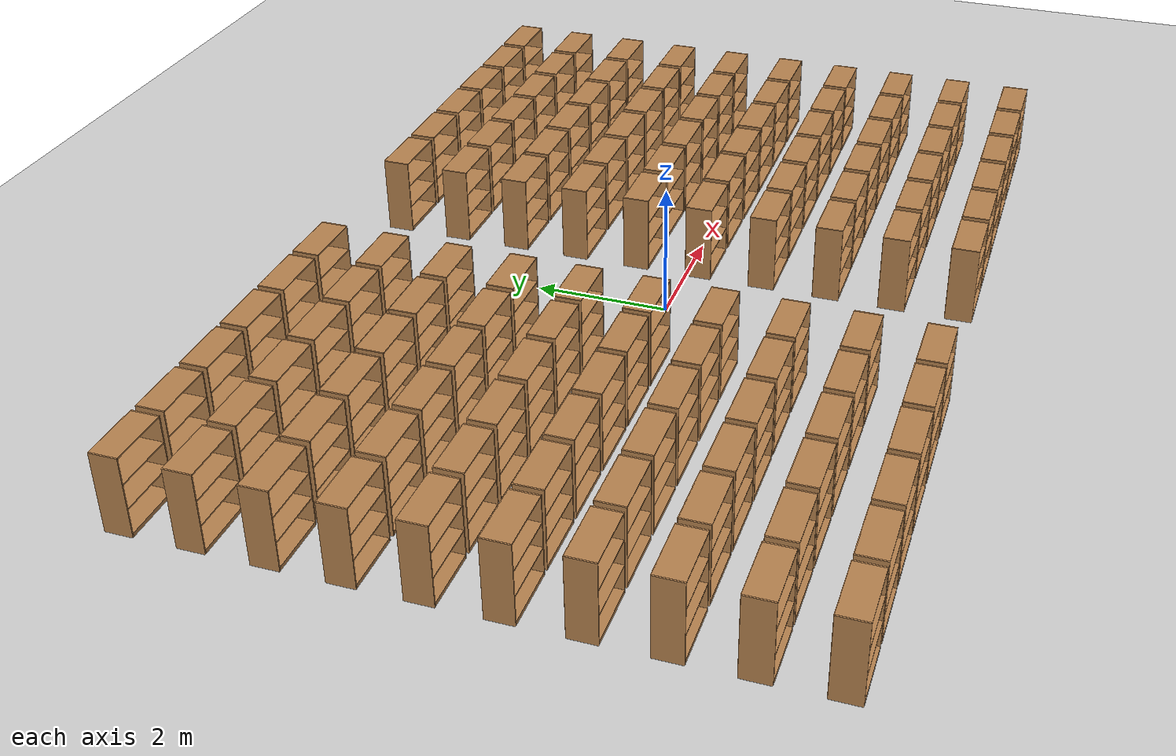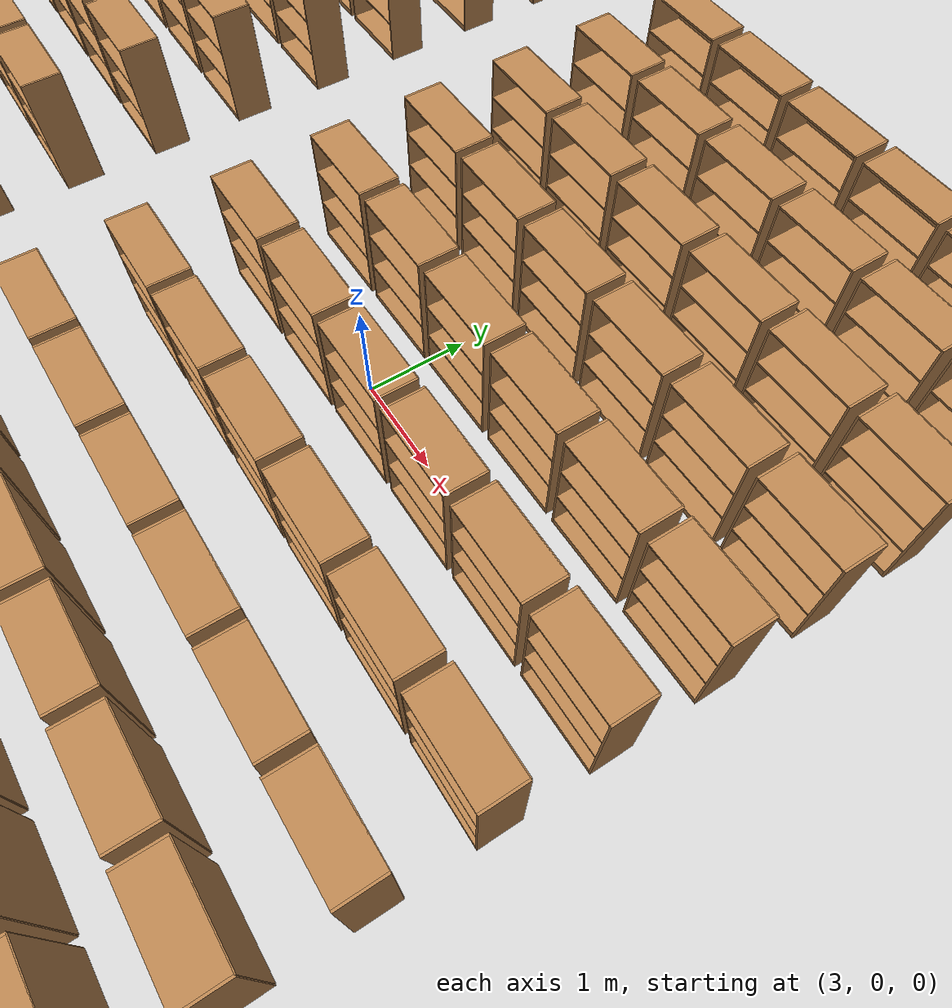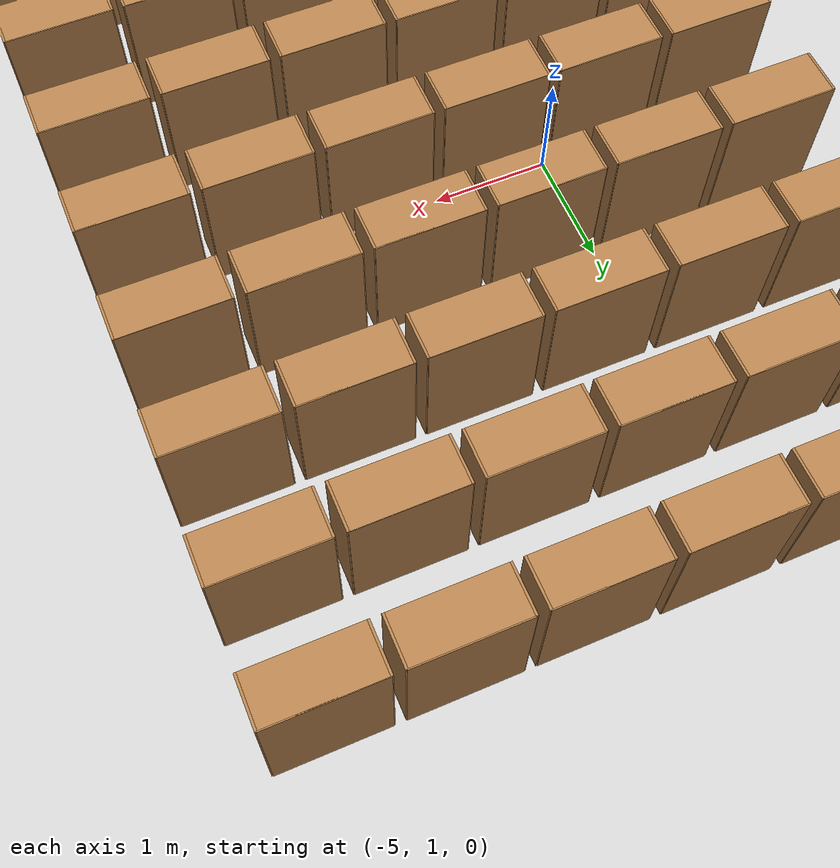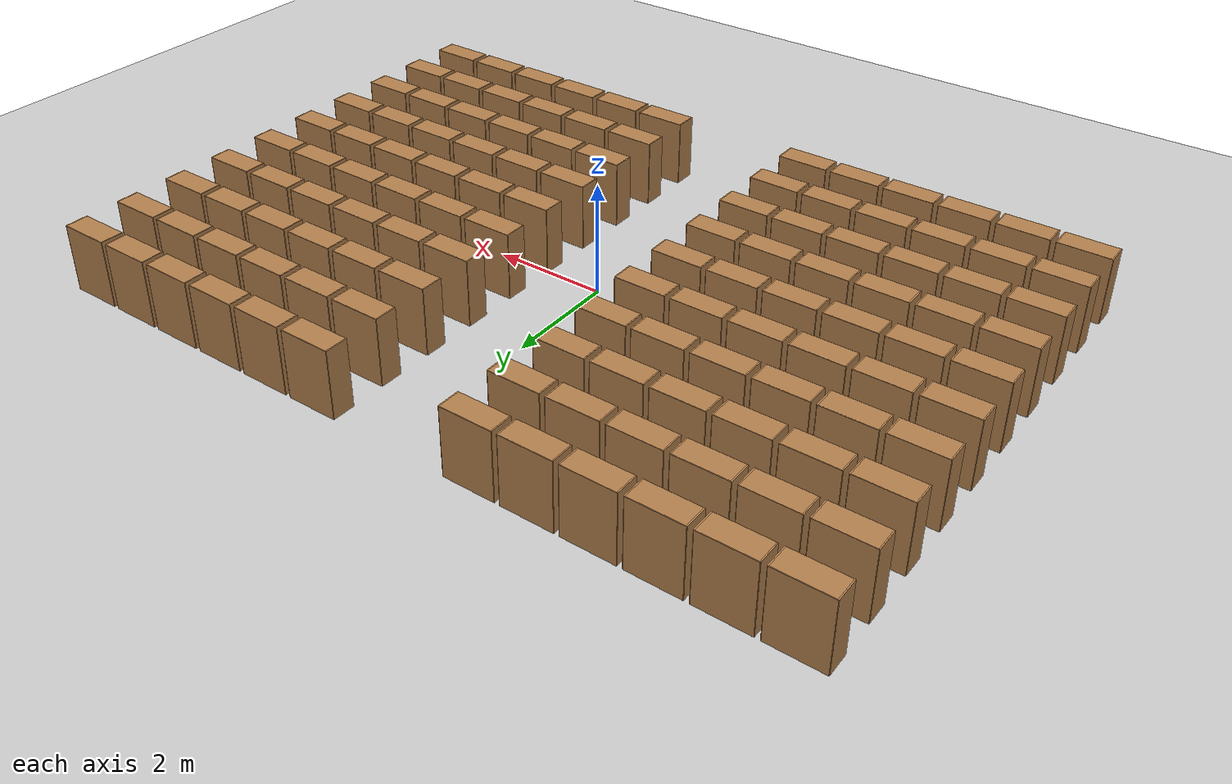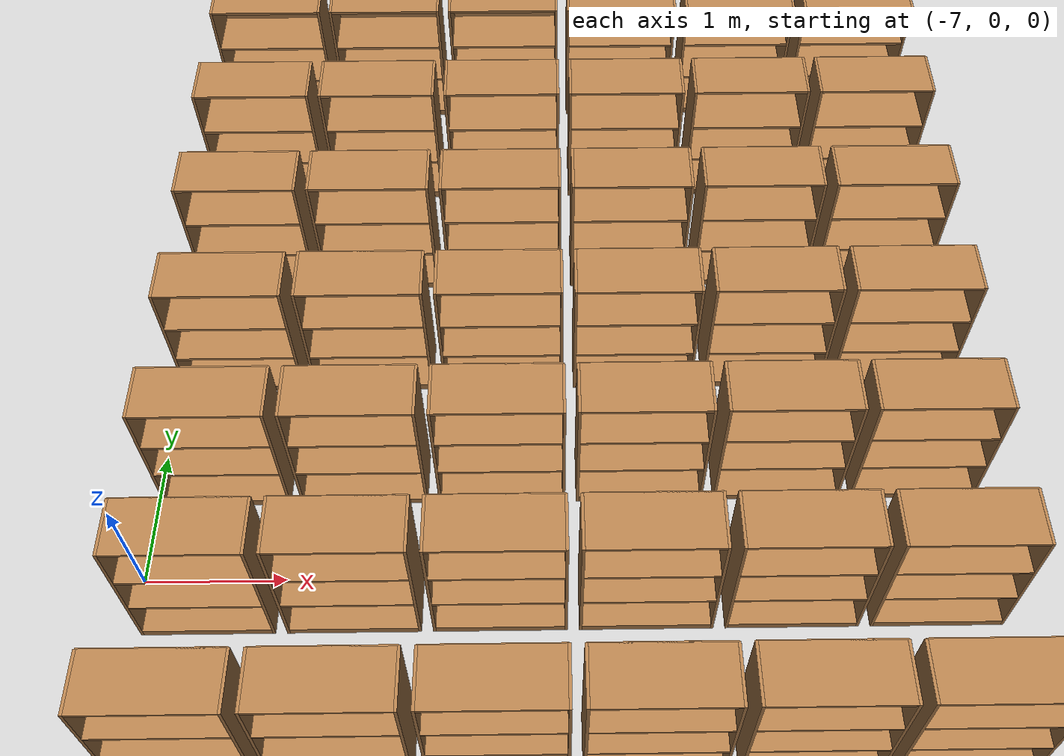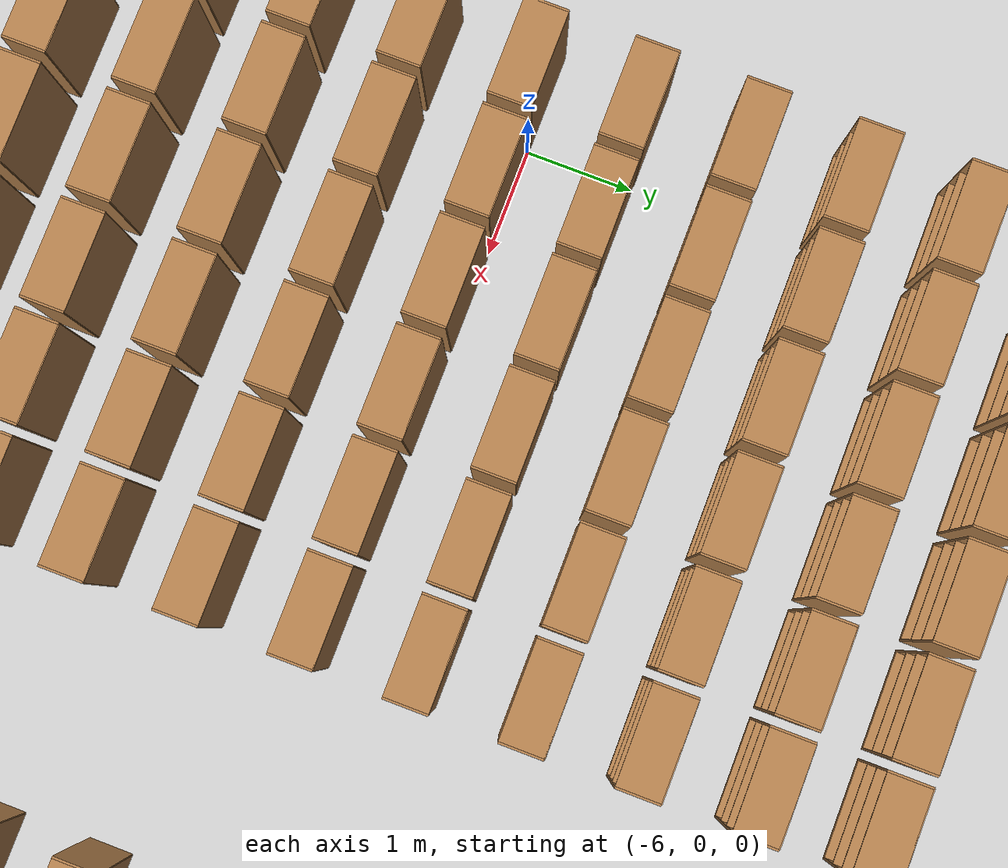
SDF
<sdf version="1.6">
 <world name="default">
  <light name="sun" type="directional">
   <pose>0 0 10 0 -0 0</pose>
   <diffuse>0.8 0.8 0.8 1</diffuse>
   <specular>0.1 0.1 0.1 1</specular>
   <attenuation>
    <range>1000</range>
    <constant>0.9</constant>
    <linear>0.01</linear>
    <quadratic>0.001</quadratic>
   </attenuation>
   <direction>-0.5 0.5 -1</direction>
  </light>
  <model name="ground_plane">
   <static>1</static>
   <link name="link">
    <collision name="collision">
     <geometry><plane><normal>0 0 1</normal><size>100 100</size></plane></geometry>
     <surface><friction><ode><mu>100</mu><mu2>50</mu2></ode></friction></surface>
    </collision>
    <visual name="visual">
     <cast_shadows>0</cast_shadows>
     <geometry><plane><normal>0 0 1</normal><size>100 100</size></plane></geometry>
     <material>
      <script><uri>file://media/materials/scripts/gazebo.material</uri><name>Gazebo/Grey</name></script>
     </material>
    </visual>
   </link>
  </model>
  <physics name="default_physics" default="0" type="ode">
   <real_time_update_rate>1000</real_time_update_rate>
   <max_step_size>0.001</max_step_size>
   <real_time_factor>1</real_time_factor>
   <ode>
    <solver>
     <type>quick</type>
     <iters>150</iters>
     <precon_iters>0</precon_iters>
     <sor>1.4</sor>
     <use_dynamic_moi_rescaling>1</use_dynamic_moi_rescaling>
    </solver>
    <constraints>
     <cfm>1e-05</cfm>
     <erp>0.2</erp>
     <contact_max_correcting_vel>2000</contact_max_correcting_vel>
     <contact_surface_layer>0.01</contact_surface_layer>
    </constraints>
   </ode>
  </physics>
  <gravity>0 0 -9.8</gravity>
  <magnetic_field>6e-06 2.3e-05 -4.2e-05</magnetic_field>
  <atmosphere type="adiabatic"/>
  <scene><ambient>0.4 0.4 0.4 1</ambient><background>0.7 0.7 0.7 1</background><shadows>1</shadows></scene>
  <spherical_coordinates>
   <surface_model>EARTH_WGS84</surface_model>
   <latitude_deg>0</latitude_deg>
   <longitude_deg>0</longitude_deg>
   <elevation>0</elevation>
   <heading_deg>0</heading_deg>
  </spherical_coordinates>
  <model name="library">
   <model name="5Bookshelves">
    <model name="BookshelfRow">
     <model name="bookshelf">
      <static>1</static>
      <link name="link">
       <inertial><mass>1</mass></inertial>
       <collision name="back">
        <pose>0 0.005 0.6 0 -0 0</pose>
        <geometry><box><size>0.9 0.01 1.2</size></box></geometry>
       </collision>
       <visual name="visual1">
        <pose>0 0.005 0.6 0 -0 0</pose>
        <geometry><box><size>0.9 0.01 1.2</size></box></geometry>
        <material>
         <script><uri>file://media/materials/scripts/gazebo.material</uri><name>Gazebo/Wood</name></script>
        </material>
       </visual>
       <collision name="left_side">
        <pose>0.45 -0.195 0.6 0 -0 0</pose>
        <geometry><box><size>0.02 0.4 1.2</size></box></geometry>
       </collision>
       <visual name="visual2">
        <pose>0.45 -0.195 0.6 0 -0 0</pose>
        <geometry><box><size>0.02 0.4 1.2</size></box></geometry>
        <material>
         <script><uri>file://media/materials/scripts/gazebo.material</uri><name>Gazebo/Wood</name></script>
        </material>
       </visual>
       <collision name="right_side">
        <pose>-0.45 -0.195 0.6 0 -0 0</pose>
        <geometry><box><size>0.02 0.4 1.2</size></box></geometry>
       </collision>
       <visual name="visual3">
        <pose>-0.45 -0.195 0.6 0 -0 0</pose>
        <geometry><box><size>0.02 0.4 1.2</size></box></geometry>
        <material>
         <script><uri>file://media/materials/scripts/gazebo.material</uri><name>Gazebo/Wood</name></script>
        </material>
       </visual>
       <collision name="bottom">
        <pose>0 -0.195 0.03 0 -0 0</pose>
        <geometry><box><size>0.88 0.4 0.06</size></box></geometry>
       </collision>
       <visual name="visual4">
        <pose>0 -0.195 0.03 0 -0 0</pose>
        <geometry><box><size>0.88 0.4 0.06</size></box></geometry>
        <material>
         <script><uri>file://media/materials/scripts/gazebo.material</uri><name>Gazebo/Wood</name></script>
        </material>
       </visual>
       <collision name="top">
        <pose>0 -0.195 1.19 0 -0 0</pose>
        <geometry><box><size>0.88 0.4 0.02</size></box></geometry>
       </collision>
       <visual name="visual5">
        <pose>0 -0.195 1.19 0 -0 0</pose>
        <geometry><box><size>0.88 0.4 0.02</size></box></geometry>
        <material>
         <script><uri>file://media/materials/scripts/gazebo.material</uri><name>Gazebo/Wood</name></script>
        </material>
       </visual>
       <collision name="low_shelf">
        <pose>0 -0.195 0.43 0 -0 0</pose>
        <geometry><box><size>0.88 0.4 0.02</size></box></geometry>
       </collision>
       <visual name="visual6">
        <pose>0 -0.195 0.43 0 -0 0</pose>
        <geometry><box><size>0.88 0.4 0.02</size></box></geometry>
        <material>
         <script><uri>file://media/materials/scripts/gazebo.material</uri><name>Gazebo/Wood</name></script>
        </material>
       </visual>
       <collision name="high_shelf">
        <pose>0 -0.195 0.8 0 -0 0</pose>
        <geometry><box><size>0.88 0.4 0.02</size></box></geometry>
       </collision>
       <visual name="visual7">
        <pose>0 -0.195 0.8 0 -0 0</pose>
        <geometry><box><size>0.88 0.4 0.02</size></box></geometry>
        <material>
         <script><uri>file://media/materials/scripts/gazebo.material</uri><name>Gazebo/Wood</name></script>
        </material>
       </visual>
      </link>
      <pose>-2.5 0 0 0 -0 0</pose>
     </model>
     <model name="bookshelf_0">
      <static>1</static>
      <link name="link">
       <inertial><mass>1</mass></inertial>
       <collision name="back">
        <pose>0 0.005 0.6 0 -0 0</pose>
        <geometry><box><size>0.9 0.01 1.2</size></box></geometry>
       </collision>
       <visual name="visual1">
        <pose>0 0.005 0.6 0 -0 0</pose>
        <geometry><box><size>0.9 0.01 1.2</size></box></geometry>
        <material>
         <script><uri>file://media/materials/scripts/gazebo.material</uri><name>Gazebo/Wood</name></script>
        </material>
       </visual>
       <collision name="left_side">
        <pose>0.45 -0.195 0.6 0 -0 0</pose>
        <geometry><box><size>0.02 0.4 1.2</size></box></geometry>
       </collision>
       <visual name="visual2">
        <pose>0.45 -0.195 0.6 0 -0 0</pose>
        <geometry><box><size>0.02 0.4 1.2</size></box></geometry>
        <material>
         <script><uri>file://media/materials/scripts/gazebo.material</uri><name>Gazebo/Wood</name></script>
        </material>
       </visual>
       <collision name="right_side">
        <pose>-0.45 -0.195 0.6 0 -0 0</pose>
        <geometry><box><size>0.02 0.4 1.2</size></box></geometry>
       </collision>
       <visual name="visual3">
        <pose>-0.45 -0.195 0.6 0 -0 0</pose>
        <geometry><box><size>0.02 0.4 1.2</size></box></geometry>
        <material>
         <script><uri>file://media/materials/scripts/gazebo.material</uri><name>Gazebo/Wood</name></script>
        </material>
       </visual>
       <collision name="bottom">
        <pose>0 -0.195 0.03 0 -0 0</pose>
        <geometry><box><size>0.88 0.4 0.06</size></box></geometry>
       </collision>
       <visual name="visual4">
        <pose>0 -0.195 0.03 0 -0 0</pose>
        <geometry><box><size>0.88 0.4 0.06</size></box></geometry>
        <material>
         <script><uri>file://media/materials/scripts/gazebo.material</uri><name>Gazebo/Wood</name></script>
        </material>
       </visual>
       <collision name="top">
        <pose>0 -0.195 1.19 0 -0 0</pose>
        <geometry><box><size>0.88 0.4 0.02</size></box></geometry>
       </collision>
       <visual name="visual5">
        <pose>0 -0.195 1.19 0 -0 0</pose>
        <geometry><box><size>0.88 0.4 0.02</size></box></geometry>
        <material>
         <script><uri>file://media/materials/scripts/gazebo.material</uri><name>Gazebo/Wood</name></script>
        </material>
       </visual>
       <collision name="low_shelf">
        <pose>0 -0.195 0.43 0 -0 0</pose>
        <geometry><box><size>0.88 0.4 0.02</size></box></geometry>
       </collision>
       <visual name="visual6">
        <pose>0 -0.195 0.43 0 -0 0</pose>
        <geometry><box><size>0.88 0.4 0.02</size></box></geometry>
        <material>
         <script><uri>file://media/materials/scripts/gazebo.material</uri><name>Gazebo/Wood</name></script>
        </material>
       </visual>
       <collision name="high_shelf">
        <pose>0 -0.195 0.8 0 -0 0</pose>
        <geometry><box><size>0.88 0.4 0.02</size></box></geometry>
       </collision>
       <visual name="visual7">
        <pose>0 -0.195 0.8 0 -0 0</pose>
        <geometry><box><size>0.88 0.4 0.02</size></box></geometry>
        <material>
         <script><uri>file://media/materials/scripts/gazebo.material</uri><name>Gazebo/Wood</name></script>
        </material>
       </visual>
      </link>
      <pose>-1.5 0 0 0 -0 0</pose>
     </model>
     <model name="bookshelf_1">
      <static>1</static>
      <link name="link">
       <inertial><mass>1</mass></inertial>
       <collision name="back">
        <pose>0 0.005 0.6 0 -0 0</pose>
        <geometry><box><size>0.9 0.01 1.2</size></box></geometry>
       </collision>
       <visual name="visual1">
        <pose>0 0.005 0.6 0 -0 0</pose>
        <geometry><box><size>0.9 0.01 1.2</size></box></geometry>
        <material>
         <script><uri>file://media/materials/scripts/gazebo.material</uri><name>Gazebo/Wood</name></script>
        </material>
       </visual>
       <collision name="left_side">
        <pose>0.45 -0.195 0.6 0 -0 0</pose>
        <geometry><box><size>0.02 0.4 1.2</size></box></geometry>
       </collision>
       <visual name="visual2">
        <pose>0.45 -0.195 0.6 0 -0 0</pose>
        <geometry><box><size>0.02 0.4 1.2</size></box></geometry>
        <material>
         <script><uri>file://media/materials/scripts/gazebo.material</uri><name>Gazebo/Wood</name></script>
        </material>
       </visual>
       <collision name="right_side">
        <pose>-0.45 -0.195 0.6 0 -0 0</pose>
        <geometry><box><size>0.02 0.4 1.2</size></box></geometry>
       </collision>
       <visual name="visual3">
        <pose>-0.45 -0.195 0.6 0 -0 0</pose>
        <geometry><box><size>0.02 0.4 1.2</size></box></geometry>
        <material>
         <script><uri>file://media/materials/scripts/gazebo.material</uri><name>Gazebo/Wood</name></script>
        </material>
       </visual>
       <collision name="bottom">
        <pose>0 -0.195 0.03 0 -0 0</pose>
        <geometry><box><size>0.88 0.4 0.06</size></box></geometry>
       </collision>
       <visual name="visual4">
        <pose>0 -0.195 0.03 0 -0 0</pose>
        <geometry><box><size>0.88 0.4 0.06</size></box></geometry>
        <material>
         <script><uri>file://media/materials/scripts/gazebo.material</uri><name>Gazebo/Wood</name></script>
        </material>
       </visual>
       <collision name="top">
        <pose>0 -0.195 1.19 0 -0 0</pose>
        <geometry><box><size>0.88 0.4 0.02</size></box></geometry>
       </collision>
       <visual name="visual5">
        <pose>0 -0.195 1.19 0 -0 0</pose>
        <geometry><box><size>0.88 0.4 0.02</size></box></geometry>
        <material>
         <script><uri>file://media/materials/scripts/gazebo.material</uri><name>Gazebo/Wood</name></script>
        </material>
       </visual>
       <collision name="low_shelf">
        <pose>0 -0.195 0.43 0 -0 0</pose>
        <geometry><box><size>0.88 0.4 0.02</size></box></geometry>
       </collision>
       <visual name="visual6">
        <pose>0 -0.195 0.43 0 -0 0</pose>
        <geometry><box><size>0.88 0.4 0.02</size></box></geometry>
        <material>
         <script><uri>file://media/materials/scripts/gazebo.material</uri><name>Gazebo/Wood</name></script>
        </material>
       </visual>
       <collision name="high_shelf">
        <pose>0 -0.195 0.8 0 -0 0</pose>
        <geometry><box><size>0.88 0.4 0.02</size></box></geometry>
       </collision>
       <visual name="visual7">
        <pose>0 -0.195 0.8 0 -0 0</pose>
        <geometry><box><size>0.88 0.4 0.02</size></box></geometry>
        <material>
         <script><uri>file://media/materials/scripts/gazebo.material</uri><name>Gazebo/Wood</name></script>
        </material>
       </visual>
      </link>
      <pose>-0.5 0 0 0 -0 0</pose>
     </model>
     <model name="bookshelf_2">
      <static>1</static>
      <link name="link">
       <inertial><mass>1</mass></inertial>
       <collision name="back">
        <pose>0 0.005 0.6 0 -0 0</pose>
        <geometry><box><size>0.9 0.01 1.2</size></box></geometry>
       </collision>
       <visual name="visual1">
        <pose>0 0.005 0.6 0 -0 0</pose>
        <geometry><box><size>0.9 0.01 1.2</size></box></geometry>
        <material>
         <script><uri>file://media/materials/scripts/gazebo.material</uri><name>Gazebo/Wood</name></script>
        </material>
       </visual>
       <collision name="left_side">
        <pose>0.45 -0.195 0.6 0 -0 0</pose>
        <geometry><box><size>0.02 0.4 1.2</size></box></geometry>
       </collision>
       <visual name="visual2">
        <pose>0.45 -0.195 0.6 0 -0 0</pose>
        <geometry><box><size>0.02 0.4 1.2</size></box></geometry>
        <material>
         <script><uri>file://media/materials/scripts/gazebo.material</uri><name>Gazebo/Wood</name></script>
        </material>
       </visual>
       <collision name="right_side">
        <pose>-0.45 -0.195 0.6 0 -0 0</pose>
        <geometry><box><size>0.02 0.4 1.2</size></box></geometry>
       </collision>
       <visual name="visual3">
        <pose>-0.45 -0.195 0.6 0 -0 0</pose>
        <geometry><box><size>0.02 0.4 1.2</size></box></geometry>
        <material>
         <script><uri>file://media/materials/scripts/gazebo.material</uri><name>Gazebo/Wood</name></script>
        </material>
       </visual>
       <collision name="bottom">
        <pose>0 -0.195 0.03 0 -0 0</pose>
        <geometry><box><size>0.88 0.4 0.06</size></box></geometry>
       </collision>
       <visual name="visual4">
        <pose>0 -0.195 0.03 0 -0 0</pose>
        <geometry><box><size>0.88 0.4 0.06</size></box></geometry>
        <material>
         <script><uri>file://media/materials/scripts/gazebo.material</uri><name>Gazebo/Wood</name></script>
        </material>
       </visual>
       <collision name="top">
        <pose>0 -0.195 1.19 0 -0 0</pose>
        <geometry><box><size>0.88 0.4 0.02</size></box></geometry>
       </collision>
       <visual name="visual5">
        <pose>0 -0.195 1.19 0 -0 0</pose>
        <geometry><box><size>0.88 0.4 0.02</size></box></geometry>
        <material>
         <script><uri>file://media/materials/scripts/gazebo.material</uri><name>Gazebo/Wood</name></script>
        </material>
       </visual>
       <collision name="low_shelf">
        <pose>0 -0.195 0.43 0 -0 0</pose>
        <geometry><box><size>0.88 0.4 0.02</size></box></geometry>
       </collision>
       <visual name="visual6">
        <pose>0 -0.195 0.43 0 -0 0</pose>
        <geometry><box><size>0.88 0.4 0.02</size></box></geometry>
        <material>
         <script><uri>file://media/materials/scripts/gazebo.material</uri><name>Gazebo/Wood</name></script>
        </material>
       </visual>
       <collision name="high_shelf">
        <pose>0 -0.195 0.8 0 -0 0</pose>
        <geometry><box><size>0.88 0.4 0.02</size></box></geometry>
       </collision>
       <visual name="visual7">
        <pose>0 -0.195 0.8 0 -0 0</pose>
        <geometry><box><size>0.88 0.4 0.02</size></box></geometry>
        <material>
         <script><uri>file://media/materials/scripts/gazebo.material</uri><name>Gazebo/Wood</name></script>
        </material>
       </visual>
      </link>
      <pose>0.5 0 0 0 -0 0</pose>
     </model>
     <model name="bookshelf_3">
      <static>1</static>
      <link name="link">
       <inertial><mass>1</mass></inertial>
       <collision name="back">
        <pose>0 0.005 0.6 0 -0 0</pose>
        <geometry><box><size>0.9 0.01 1.2</size></box></geometry>
       </collision>
       <visual name="visual1">
        <pose>0 0.005 0.6 0 -0 0</pose>
        <geometry><box><size>0.9 0.01 1.2</size></box></geometry>
        <material>
         <script><uri>file://media/materials/scripts/gazebo.material</uri><name>Gazebo/Wood</name></script>
        </material>
       </visual>
       <collision name="left_side">
        <pose>0.45 -0.195 0.6 0 -0 0</pose>
        <geometry><box><size>0.02 0.4 1.2</size></box></geometry>
       </collision>
       <visual name="visual2">
        <pose>0.45 -0.195 0.6 0 -0 0</pose>
        <geometry><box><size>0.02 0.4 1.2</size></box></geometry>
        <material>
         <script><uri>file://media/materials/scripts/gazebo.material</uri><name>Gazebo/Wood</name></script>
        </material>
       </visual>
       <collision name="right_side">
        <pose>-0.45 -0.195 0.6 0 -0 0</pose>
        <geometry><box><size>0.02 0.4 1.2</size></box></geometry>
       </collision>
       <visual name="visual3">
        <pose>-0.45 -0.195 0.6 0 -0 0</pose>
        <geometry><box><size>0.02 0.4 1.2</size></box></geometry>
        <material>
         <script><uri>file://media/materials/scripts/gazebo.material</uri><name>Gazebo/Wood</name></script>
        </material>
       </visual>
       <collision name="bottom">
        <pose>0 -0.195 0.03 0 -0 0</pose>
        <geometry><box><size>0.88 0.4 0.06</size></box></geometry>
       </collision>
       <visual name="visual4">
        <pose>0 -0.195 0.03 0 -0 0</pose>
        <geometry><box><size>0.88 0.4 0.06</size></box></geometry>
        <material>
         <script><uri>file://media/materials/scripts/gazebo.material</uri><name>Gazebo/Wood</name></script>
        </material>
       </visual>
       <collision name="top">
        <pose>0 -0.195 1.19 0 -0 0</pose>
        <geometry><box><size>0.88 0.4 0.02</size></box></geometry>
       </collision>
       <visual name="visual5">
        <pose>0 -0.195 1.19 0 -0 0</pose>
        <geometry><box><size>0.88 0.4 0.02</size></box></geometry>
        <material>
         <script><uri>file://media/materials/scripts/gazebo.material</uri><name>Gazebo/Wood</name></script>
        </material>
       </visual>
       <collision name="low_shelf">
        <pose>0 -0.195 0.43 0 -0 0</pose>
        <geometry><box><size>0.88 0.4 0.02</size></box></geometry>
       </collision>
       <visual name="visual6">
        <pose>0 -0.195 0.43 0 -0 0</pose>
        <geometry><box><size>0.88 0.4 0.02</size></box></geometry>
        <material>
         <script><uri>file://media/materials/scripts/gazebo.material</uri><name>Gazebo/Wood</name></script>
        </material>
       </visual>
       <collision name="high_shelf">
        <pose>0 -0.195 0.8 0 -0 0</pose>
        <geometry><box><size>0.88 0.4 0.02</size></box></geometry>
       </collision>
       <visual name="visual7">
        <pose>0 -0.195 0.8 0 -0 0</pose>
        <geometry><box><size>0.88 0.4 0.02</size></box></geometry>
        <material>
         <script><uri>file://media/materials/scripts/gazebo.material</uri><name>Gazebo/Wood</name></script>
        </material>
       </visual>
      </link>
      <pose>1.5 0 0 0 -0 0</pose>
     </model>
     <model name="bookshelf_4">
      <static>1</static>
      <link name="link">
       <inertial><mass>1</mass></inertial>
       <collision name="back">
        <pose>0 0.005 0.6 0 -0 0</pose>
        <geometry><box><size>0.9 0.01 1.2</size></box></geometry>
       </collision>
       <visual name="visual1">
        <pose>0 0.005 0.6 0 -0 0</pose>
        <geometry><box><size>0.9 0.01 1.2</size></box></geometry>
        <material>
         <script><uri>file://media/materials/scripts/gazebo.material</uri><name>Gazebo/Wood</name></script>
        </material>
       </visual>
       <collision name="left_side">
        <pose>0.45 -0.195 0.6 0 -0 0</pose>
        <geometry><box><size>0.02 0.4 1.2</size></box></geometry>
       </collision>
       <visual name="visual2">
        <pose>0.45 -0.195 0.6 0 -0 0</pose>
        <geometry><box><size>0.02 0.4 1.2</size></box></geometry>
        <material>
         <script><uri>file://media/materials/scripts/gazebo.material</uri><name>Gazebo/Wood</name></script>
        </material>
       </visual>
       <collision name="right_side">
        <pose>-0.45 -0.195 0.6 0 -0 0</pose>
        <geometry><box><size>0.02 0.4 1.2</size></box></geometry>
       </collision>
       <visual name="visual3">
        <pose>-0.45 -0.195 0.6 0 -0 0</pose>
        <geometry><box><size>0.02 0.4 1.2</size></box></geometry>
        <material>
         <script><uri>file://media/materials/scripts/gazebo.material</uri><name>Gazebo/Wood</name></script>
        </material>
       </visual>
       <collision name="bottom">
        <pose>0 -0.195 0.03 0 -0 0</pose>
        <geometry><box><size>0.88 0.4 0.06</size></box></geometry>
       </collision>
       <visual name="visual4">
        <pose>0 -0.195 0.03 0 -0 0</pose>
        <geometry><box><size>0.88 0.4 0.06</size></box></geometry>
        <material>
         <script><uri>file://media/materials/scripts/gazebo.material</uri><name>Gazebo/Wood</name></script>
        </material>
       </visual>
       <collision name="top">
        <pose>0 -0.195 1.19 0 -0 0</pose>
        <geometry><box><size>0.88 0.4 0.02</size></box></geometry>
       </collision>
       <visual name="visual5">
        <pose>0 -0.195 1.19 0 -0 0</pose>
        <geometry><box><size>0.88 0.4 0.02</size></box></geometry>
        <material>
         <script><uri>file://media/materials/scripts/gazebo.material</uri><name>Gazebo/Wood</name></script>
        </material>
       </visual>
       <collision name="low_shelf">
        <pose>0 -0.195 0.43 0 -0 0</pose>
        <geometry><box><size>0.88 0.4 0.02</size></box></geometry>
       </collision>
       <visual name="visual6">
        <pose>0 -0.195 0.43 0 -0 0</pose>
        <geometry><box><size>0.88 0.4 0.02</size></box></geometry>
        <material>
         <script><uri>file://media/materials/scripts/gazebo.material</uri><name>Gazebo/Wood</name></script>
        </material>
       </visual>
       <collision name="high_shelf">
        <pose>0 -0.195 0.8 0 -0 0</pose>
        <geometry><box><size>0.88 0.4 0.02</size></box></geometry>
       </collision>
       <visual name="visual7">
        <pose>0 -0.195 0.8 0 -0 0</pose>
        <geometry><box><size>0.88 0.4 0.02</size></box></geometry>
        <material>
         <script><uri>file://media/materials/scripts/gazebo.material</uri><name>Gazebo/Wood</name></script>
        </material>
       </visual>
      </link>
      <pose>2.5 0 0 0 -0 0</pose>
     </model>
     <static>0</static>
     <pose>0 -2 0 0 -0 0</pose>
    </model>
    <model name="BookshelfRow_0">
     <model name="bookshelf">
      <static>1</static>
      <link name="link">
       <inertial><mass>1</mass></inertial>
       <collision name="back">
        <pose>0 0.005 0.6 0 -0 0</pose>
        <geometry><box><size>0.9 0.01 1.2</size></box></geometry>
       </collision>
       <visual name="visual1">
        <pose>0 0.005 0.6 0 -0 0</pose>
        <geometry><box><size>0.9 0.01 1.2</size></box></geometry>
        <material>
         <script><uri>file://media/materials/scripts/gazebo.material</uri><name>Gazebo/Wood</name></script>
        </material>
       </visual>
       <collision name="left_side">
        <pose>0.45 -0.195 0.6 0 -0 0</pose>
        <geometry><box><size>0.02 0.4 1.2</size></box></geometry>
       </collision>
       <visual name="visual2">
        <pose>0.45 -0.195 0.6 0 -0 0</pose>
        <geometry><box><size>0.02 0.4 1.2</size></box></geometry>
        <material>
         <script><uri>file://media/materials/scripts/gazebo.material</uri><name>Gazebo/Wood</name></script>
        </material>
       </visual>
       <collision name="right_side">
        <pose>-0.45 -0.195 0.6 0 -0 0</pose>
        <geometry><box><size>0.02 0.4 1.2</size></box></geometry>
       </collision>
       <visual name="visual3">
        <pose>-0.45 -0.195 0.6 0 -0 0</pose>
        <geometry><box><size>0.02 0.4 1.2</size></box></geometry>
        <material>
         <script><uri>file://media/materials/scripts/gazebo.material</uri><name>Gazebo/Wood</name></script>
        </material>
       </visual>
       <collision name="bottom">
        <pose>0 -0.195 0.03 0 -0 0</pose>
        <geometry><box><size>0.88 0.4 0.06</size></box></geometry>
       </collision>
       <visual name="visual4">
        <pose>0 -0.195 0.03 0 -0 0</pose>
        <geometry><box><size>0.88 0.4 0.06</size></box></geometry>
        <material>
         <script><uri>file://media/materials/scripts/gazebo.material</uri><name>Gazebo/Wood</name></script>
        </material>
       </visual>
       <collision name="top">
        <pose>0 -0.195 1.19 0 -0 0</pose>
        <geometry><box><size>0.88 0.4 0.02</size></box></geometry>
       </collision>
       <visual name="visual5">
        <pose>0 -0.195 1.19 0 -0 0</pose>
        <geometry><box><size>0.88 0.4 0.02</size></box></geometry>
        <material>
         <script><uri>file://media/materials/scripts/gazebo.material</uri><name>Gazebo/Wood</name></script>
        </material>
       </visual>
       <collision name="low_shelf">
        <pose>0 -0.195 0.43 0 -0 0</pose>
        <geometry><box><size>0.88 0.4 0.02</size></box></geometry>
       </collision>
       <visual name="visual6">
        <pose>0 -0.195 0.43 0 -0 0</pose>
        <geometry><box><size>0.88 0.4 0.02</size></box></geometry>
        <material>
         <script><uri>file://media/materials/scripts/gazebo.material</uri><name>Gazebo/Wood</name></script>
        </material>
       </visual>
       <collision name="high_shelf">
        <pose>0 -0.195 0.8 0 -0 0</pose>
        <geometry><box><size>0.88 0.4 0.02</size></box></geometry>
       </collision>
       <visual name="visual7">
        <pose>0 -0.195 0.8 0 -0 0</pose>
        <geometry><box><size>0.88 0.4 0.02</size></box></geometry>
        <material>
         <script><uri>file://media/materials/scripts/gazebo.material</uri><name>Gazebo/Wood</name></script>
        </material>
       </visual>
      </link>
      <pose>-2.5 0 0 0 -0 0</pose>
     </model>
     <model name="bookshelf_0">
      <static>1</static>
      <link name="link">
       <inertial><mass>1</mass></inertial>
       <collision name="back">
        <pose>0 0.005 0.6 0 -0 0</pose>
        <geometry><box><size>0.9 0.01 1.2</size></box></geometry>
       </collision>
       <visual name="visual1">
        <pose>0 0.005 0.6 0 -0 0</pose>
        <geometry><box><size>0.9 0.01 1.2</size></box></geometry>
        <material>
         <script><uri>file://media/materials/scripts/gazebo.material</uri><name>Gazebo/Wood</name></script>
        </material>
       </visual>
       <collision name="left_side">
        <pose>0.45 -0.195 0.6 0 -0 0</pose>
        <geometry><box><size>0.02 0.4 1.2</size></box></geometry>
       </collision>
       <visual name="visual2">
        <pose>0.45 -0.195 0.6 0 -0 0</pose>
        <geometry><box><size>0.02 0.4 1.2</size></box></geometry>
        <material>
         <script><uri>file://media/materials/scripts/gazebo.material</uri><name>Gazebo/Wood</name></script>
        </material>
       </visual>
       <collision name="right_side">
        <pose>-0.45 -0.195 0.6 0 -0 0</pose>
        <geometry><box><size>0.02 0.4 1.2</size></box></geometry>
       </collision>
       <visual name="visual3">
        <pose>-0.45 -0.195 0.6 0 -0 0</pose>
        <geometry><box><size>0.02 0.4 1.2</size></box></geometry>
        <material>
         <script><uri>file://media/materials/scripts/gazebo.material</uri><name>Gazebo/Wood</name></script>
        </material>
       </visual>
       <collision name="bottom">
        <pose>0 -0.195 0.03 0 -0 0</pose>
        <geometry><box><size>0.88 0.4 0.06</size></box></geometry>
       </collision>
       <visual name="visual4">
        <pose>0 -0.195 0.03 0 -0 0</pose>
        <geometry><box><size>0.88 0.4 0.06</size></box></geometry>
        <material>
         <script><uri>file://media/materials/scripts/gazebo.material</uri><name>Gazebo/Wood</name></script>
        </material>
       </visual>
       <collision name="top">
        <pose>0 -0.195 1.19 0 -0 0</pose>
        <geometry><box><size>0.88 0.4 0.02</size></box></geometry>
       </collision>
       <visual name="visual5">
        <pose>0 -0.195 1.19 0 -0 0</pose>
        <geometry><box><size>0.88 0.4 0.02</size></box></geometry>
        <material>
         <script><uri>file://media/materials/scripts/gazebo.material</uri><name>Gazebo/Wood</name></script>
        </material>
       </visual>
       <collision name="low_shelf">
        <pose>0 -0.195 0.43 0 -0 0</pose>
        <geometry><box><size>0.88 0.4 0.02</size></box></geometry>
       </collision>
       <visual name="visual6">
        <pose>0 -0.195 0.43 0 -0 0</pose>
        <geometry><box><size>0.88 0.4 0.02</size></box></geometry>
        <material>
         <script><uri>file://media/materials/scripts/gazebo.material</uri><name>Gazebo/Wood</name></script>
        </material>
       </visual>
       <collision name="high_shelf">
        <pose>0 -0.195 0.8 0 -0 0</pose>
        <geometry><box><size>0.88 0.4 0.02</size></box></geometry>
       </collision>
       <visual name="visual7">
        <pose>0 -0.195 0.8 0 -0 0</pose>
        <geometry><box><size>0.88 0.4 0.02</size></box></geometry>
        <material>
         <script><uri>file://media/materials/scripts/gazebo.material</uri><name>Gazebo/Wood</name></script>
        </material>
       </visual>
      </link>
      <pose>-1.5 0 0 0 -0 0</pose>
     </model>
     <model name="bookshelf_1">
      <static>1</static>
      <link name="link">
       <inertial><mass>1</mass></inertial>
       <collision name="back">
        <pose>0 0.005 0.6 0 -0 0</pose>
        <geometry><box><size>0.9 0.01 1.2</size></box></geometry>
       </collision>
       <visual name="visual1">
        <pose>0 0.005 0.6 0 -0 0</pose>
        <geometry><box><size>0.9 0.01 1.2</size></box></geometry>
        <material>
         <script><uri>file://media/materials/scripts/gazebo.material</uri><name>Gazebo/Wood</name></script>
        </material>
       </visual>
       <collision name="left_side">
        <pose>0.45 -0.195 0.6 0 -0 0</pose>
        <geometry><box><size>0.02 0.4 1.2</size></box></geometry>
       </collision>
       <visual name="visual2">
        <pose>0.45 -0.195 0.6 0 -0 0</pose>
        <geometry><box><size>0.02 0.4 1.2</size></box></geometry>
        <material>
         <script><uri>file://media/materials/scripts/gazebo.material</uri><name>Gazebo/Wood</name></script>
        </material>
       </visual>
       <collision name="right_side">
        <pose>-0.45 -0.195 0.6 0 -0 0</pose>
        <geometry><box><size>0.02 0.4 1.2</size></box></geometry>
       </collision>
       <visual name="visual3">
        <pose>-0.45 -0.195 0.6 0 -0 0</pose>
        <geometry><box><size>0.02 0.4 1.2</size></box></geometry>
        <material>
         <script><uri>file://media/materials/scripts/gazebo.material</uri><name>Gazebo/Wood</name></script>
        </material>
       </visual>
       <collision name="bottom">
        <pose>0 -0.195 0.03 0 -0 0</pose>
        <geometry><box><size>0.88 0.4 0.06</size></box></geometry>
       </collision>
       <visual name="visual4">
        <pose>0 -0.195 0.03 0 -0 0</pose>
        <geometry><box><size>0.88 0.4 0.06</size></box></geometry>
        <material>
         <script><uri>file://media/materials/scripts/gazebo.material</uri><name>Gazebo/Wood</name></script>
        </material>
       </visual>
       <collision name="top">
        <pose>0 -0.195 1.19 0 -0 0</pose>
        <geometry><box><size>0.88 0.4 0.02</size></box></geometry>
       </collision>
       <visual name="visual5">
        <pose>0 -0.195 1.19 0 -0 0</pose>
        <geometry><box><size>0.88 0.4 0.02</size></box></geometry>
        <material>
         <script><uri>file://media/materials/scripts/gazebo.material</uri><name>Gazebo/Wood</name></script>
        </material>
       </visual>
       <collision name="low_shelf">
        <pose>0 -0.195 0.43 0 -0 0</pose>
        <geometry><box><size>0.88 0.4 0.02</size></box></geometry>
       </collision>
       <visual name="visual6">
        <pose>0 -0.195 0.43 0 -0 0</pose>
        <geometry><box><size>0.88 0.4 0.02</size></box></geometry>
        <material>
         <script><uri>file://media/materials/scripts/gazebo.material</uri><name>Gazebo/Wood</name></script>
        </material>
       </visual>
       <collision name="high_shelf">
        <pose>0 -0.195 0.8 0 -0 0</pose>
        <geometry><box><size>0.88 0.4 0.02</size></box></geometry>
       </collision>
       <visual name="visual7">
        <pose>0 -0.195 0.8 0 -0 0</pose>
        <geometry><box><size>0.88 0.4 0.02</size></box></geometry>
        <material>
         <script><uri>file://media/materials/scripts/gazebo.material</uri><name>Gazebo/Wood</name></script>
        </material>
       </visual>
      </link>
      <pose>-0.5 0 0 0 -0 0</pose>
     </model>
     <model name="bookshelf_2">
      <static>1</static>
      <link name="link">
       <inertial><mass>1</mass></inertial>
       <collision name="back">
        <pose>0 0.005 0.6 0 -0 0</pose>
        <geometry><box><size>0.9 0.01 1.2</size></box></geometry>
       </collision>
       <visual name="visual1">
        <pose>0 0.005 0.6 0 -0 0</pose>
        <geometry><box><size>0.9 0.01 1.2</size></box></geometry>
        <material>
         <script><uri>file://media/materials/scripts/gazebo.material</uri><name>Gazebo/Wood</name></script>
        </material>
       </visual>
       <collision name="left_side">
        <pose>0.45 -0.195 0.6 0 -0 0</pose>
        <geometry><box><size>0.02 0.4 1.2</size></box></geometry>
       </collision>
       <visual name="visual2">
        <pose>0.45 -0.195 0.6 0 -0 0</pose>
        <geometry><box><size>0.02 0.4 1.2</size></box></geometry>
        <material>
         <script><uri>file://media/materials/scripts/gazebo.material</uri><name>Gazebo/Wood</name></script>
        </material>
       </visual>
       <collision name="right_side">
        <pose>-0.45 -0.195 0.6 0 -0 0</pose>
        <geometry><box><size>0.02 0.4 1.2</size></box></geometry>
       </collision>
       <visual name="visual3">
        <pose>-0.45 -0.195 0.6 0 -0 0</pose>
        <geometry><box><size>0.02 0.4 1.2</size></box></geometry>
        <material>
         <script><uri>file://media/materials/scripts/gazebo.material</uri><name>Gazebo/Wood</name></script>
        </material>
       </visual>
       <collision name="bottom">
        <pose>0 -0.195 0.03 0 -0 0</pose>
        <geometry><box><size>0.88 0.4 0.06</size></box></geometry>
       </collision>
       <visual name="visual4">
        <pose>0 -0.195 0.03 0 -0 0</pose>
        <geometry><box><size>0.88 0.4 0.06</size></box></geometry>
        <material>
         <script><uri>file://media/materials/scripts/gazebo.material</uri><name>Gazebo/Wood</name></script>
        </material>
       </visual>
       <collision name="top">
        <pose>0 -0.195 1.19 0 -0 0</pose>
        <geometry><box><size>0.88 0.4 0.02</size></box></geometry>
       </collision>
       <visual name="visual5">
        <pose>0 -0.195 1.19 0 -0 0</pose>
        <geometry><box><size>0.88 0.4 0.02</size></box></geometry>
        <material>
         <script><uri>file://media/materials/scripts/gazebo.material</uri><name>Gazebo/Wood</name></script>
        </material>
       </visual>
       <collision name="low_shelf">
        <pose>0 -0.195 0.43 0 -0 0</pose>
        <geometry><box><size>0.88 0.4 0.02</size></box></geometry>
       </collision>
       <visual name="visual6">
        <pose>0 -0.195 0.43 0 -0 0</pose>
        <geometry><box><size>0.88 0.4 0.02</size></box></geometry>
        <material>
         <script><uri>file://media/materials/scripts/gazebo.material</uri><name>Gazebo/Wood</name></script>
        </material>
       </visual>
       <collision name="high_shelf">
        <pose>0 -0.195 0.8 0 -0 0</pose>
        <geometry><box><size>0.88 0.4 0.02</size></box></geometry>
       </collision>
       <visual name="visual7">
        <pose>0 -0.195 0.8 0 -0 0</pose>
        <geometry><box><size>0.88 0.4 0.02</size></box></geometry>
        <material>
         <script><uri>file://media/materials/scripts/gazebo.material</uri><name>Gazebo/Wood</name></script>
        </material>
       </visual>
      </link>
      <pose>0.5 0 0 0 -0 0</pose>
     </model>
     <model name="bookshelf_3">
      <static>1</static>
      <link name="link">
       <inertial><mass>1</mass></inertial>
       <collision name="back">
        <pose>0 0.005 0.6 0 -0 0</pose>
        <geometry><box><size>0.9 0.01 1.2</size></box></geometry>
       </collision>
       <visual name="visual1">
        <pose>0 0.005 0.6 0 -0 0</pose>
        <geometry><box><size>0.9 0.01 1.2</size></box></geometry>
        <material>
         <script><uri>file://media/materials/scripts/gazebo.material</uri><name>Gazebo/Wood</name></script>
        </material>
       </visual>
       <collision name="left_side">
        <pose>0.45 -0.195 0.6 0 -0 0</pose>
        <geometry><box><size>0.02 0.4 1.2</size></box></geometry>
       </collision>
       <visual name="visual2">
        <pose>0.45 -0.195 0.6 0 -0 0</pose>
        <geometry><box><size>0.02 0.4 1.2</size></box></geometry>
        <material>
         <script><uri>file://media/materials/scripts/gazebo.material</uri><name>Gazebo/Wood</name></script>
        </material>
       </visual>
       <collision name="right_side">
        <pose>-0.45 -0.195 0.6 0 -0 0</pose>
        <geometry><box><size>0.02 0.4 1.2</size></box></geometry>
       </collision>
       <visual name="visual3">
        <pose>-0.45 -0.195 0.6 0 -0 0</pose>
        <geometry><box><size>0.02 0.4 1.2</size></box></geometry>
        <material>
         <script><uri>file://media/materials/scripts/gazebo.material</uri><name>Gazebo/Wood</name></script>
        </material>
       </visual>
       <collision name="bottom">
        <pose>0 -0.195 0.03 0 -0 0</pose>
        <geometry><box><size>0.88 0.4 0.06</size></box></geometry>
       </collision>
       <visual name="visual4">
        <pose>0 -0.195 0.03 0 -0 0</pose>
        <geometry><box><size>0.88 0.4 0.06</size></box></geometry>
        <material>
         <script><uri>file://media/materials/scripts/gazebo.material</uri><name>Gazebo/Wood</name></script>
        </material>
       </visual>
       <collision name="top">
        <pose>0 -0.195 1.19 0 -0 0</pose>
        <geometry><box><size>0.88 0.4 0.02</size></box></geometry>
       </collision>
       <visual name="visual5">
        <pose>0 -0.195 1.19 0 -0 0</pose>
        <geometry><box><size>0.88 0.4 0.02</size></box></geometry>
        <material>
         <script><uri>file://media/materials/scripts/gazebo.material</uri><name>Gazebo/Wood</name></script>
        </material>
       </visual>
       <collision name="low_shelf">
        <pose>0 -0.195 0.43 0 -0 0</pose>
        <geometry><box><size>0.88 0.4 0.02</size></box></geometry>
       </collision>
       <visual name="visual6">
        <pose>0 -0.195 0.43 0 -0 0</pose>
        <geometry><box><size>0.88 0.4 0.02</size></box></geometry>
        <material>
         <script><uri>file://media/materials/scripts/gazebo.material</uri><name>Gazebo/Wood</name></script>
        </material>
       </visual>
       <collision name="high_shelf">
        <pose>0 -0.195 0.8 0 -0 0</pose>
        <geometry><box><size>0.88 0.4 0.02</size></box></geometry>
       </collision>
       <visual name="visual7">
        <pose>0 -0.195 0.8 0 -0 0</pose>
        <geometry><box><size>0.88 0.4 0.02</size></box></geometry>
        <material>
         <script><uri>file://media/materials/scripts/gazebo.material</uri><name>Gazebo/Wood</name></script>
        </material>
       </visual>
      </link>
      <pose>1.5 0 0 0 -0 0</pose>
     </model>
     <model name="bookshelf_4">
      <static>1</static>
      <link name="link">
       <inertial><mass>1</mass></inertial>
       <collision name="back">
        <pose>0 0.005 0.6 0 -0 0</pose>
        <geometry><box><size>0.9 0.01 1.2</size></box></geometry>
       </collision>
       <visual name="visual1">
        <pose>0 0.005 0.6 0 -0 0</pose>
        <geometry><box><size>0.9 0.01 1.2</size></box></geometry>
        <material>
         <script><uri>file://media/materials/scripts/gazebo.material</uri><name>Gazebo/Wood</name></script>
        </material>
       </visual>
       <collision name="left_side">
        <pose>0.45 -0.195 0.6 0 -0 0</pose>
        <geometry><box><size>0.02 0.4 1.2</size></box></geometry>
       </collision>
       <visual name="visual2">
        <pose>0.45 -0.195 0.6 0 -0 0</pose>
        <geometry><box><size>0.02 0.4 1.2</size></box></geometry>
        <material>
         <script><uri>file://media/materials/scripts/gazebo.material</uri><name>Gazebo/Wood</name></script>
        </material>
       </visual>
       <collision name="right_side">
        <pose>-0.45 -0.195 0.6 0 -0 0</pose>
        <geometry><box><size>0.02 0.4 1.2</size></box></geometry>
       </collision>
       <visual name="visual3">
        <pose>-0.45 -0.195 0.6 0 -0 0</pose>
        <geometry><box><size>0.02 0.4 1.2</size></box></geometry>
        <material>
         <script><uri>file://media/materials/scripts/gazebo.material</uri><name>Gazebo/Wood</name></script>
        </material>
       </visual>
       <collision name="bottom">
        <pose>0 -0.195 0.03 0 -0 0</pose>
        <geometry><box><size>0.88 0.4 0.06</size></box></geometry>
       </collision>
       <visual name="visual4">
        <pose>0 -0.195 0.03 0 -0 0</pose>
        <geometry><box><size>0.88 0.4 0.06</size></box></geometry>
        <material>
         <script><uri>file://media/materials/scripts/gazebo.material</uri><name>Gazebo/Wood</name></script>
        </material>
       </visual>
       <collision name="top">
        <pose>0 -0.195 1.19 0 -0 0</pose>
        <geometry><box><size>0.88 0.4 0.02</size></box></geometry>
       </collision>
       <visual name="visual5">
        <pose>0 -0.195 1.19 0 -0 0</pose>
        <geometry><box><size>0.88 0.4 0.02</size></box></geometry>
        <material>
         <script><uri>file://media/materials/scripts/gazebo.material</uri><name>Gazebo/Wood</name></script>
        </material>
       </visual>
       <collision name="low_shelf">
        <pose>0 -0.195 0.43 0 -0 0</pose>
        <geometry><box><size>0.88 0.4 0.02</size></box></geometry>
       </collision>
       <visual name="visual6">
        <pose>0 -0.195 0.43 0 -0 0</pose>
        <geometry><box><size>0.88 0.4 0.02</size></box></geometry>
        <material>
         <script><uri>file://media/materials/scripts/gazebo.material</uri><name>Gazebo/Wood</name></script>
        </material>
       </visual>
       <collision name="high_shelf">
        <pose>0 -0.195 0.8 0 -0 0</pose>
        <geometry><box><size>0.88 0.4 0.02</size></box></geometry>
       </collision>
       <visual name="visual7">
        <pose>0 -0.195 0.8 0 -0 0</pose>
        <geometry><box><size>0.88 0.4 0.02</size></box></geometry>
        <material>
         <script><uri>file://media/materials/scripts/gazebo.material</uri><name>Gazebo/Wood</name></script>
        </material>
       </visual>
      </link>
      <pose>2.5 0 0 0 -0 0</pose>
     </model>
     <static>0</static>
     <pose>0 -1 0 0 -0 0</pose>
    </model>
    <model name="BookshelfRow_1">
     <model name="bookshelf">
      <static>1</static>
      <link name="link">
       <inertial><mass>1</mass></inertial>
       <collision name="back">
        <pose>0 0.005 0.6 0 -0 0</pose>
        <geometry><box><size>0.9 0.01 1.2</size></box></geometry>
       </collision>
       <visual name="visual1">
        <pose>0 0.005 0.6 0 -0 0</pose>
        <geometry><box><size>0.9 0.01 1.2</size></box></geometry>
        <material>
         <script><uri>file://media/materials/scripts/gazebo.material</uri><name>Gazebo/Wood</name></script>
        </material>
       </visual>
       <collision name="left_side">
        <pose>0.45 -0.195 0.6 0 -0 0</pose>
        <geometry><box><size>0.02 0.4 1.2</size></box></geometry>
       </collision>
       <visual name="visual2">
        <pose>0.45 -0.195 0.6 0 -0 0</pose>
        <geometry><box><size>0.02 0.4 1.2</size></box></geometry>
        <material>
         <script><uri>file://media/materials/scripts/gazebo.material</uri><name>Gazebo/Wood</name></script>
        </material>
       </visual>
       <collision name="right_side">
        <pose>-0.45 -0.195 0.6 0 -0 0</pose>
        <geometry><box><size>0.02 0.4 1.2</size></box></geometry>
       </collision>
       <visual name="visual3">
        <pose>-0.45 -0.195 0.6 0 -0 0</pose>
        <geometry><box><size>0.02 0.4 1.2</size></box></geometry>
        <material>
         <script><uri>file://media/materials/scripts/gazebo.material</uri><name>Gazebo/Wood</name></script>
        </material>
       </visual>
       <collision name="bottom">
        <pose>0 -0.195 0.03 0 -0 0</pose>
        <geometry><box><size>0.88 0.4 0.06</size></box></geometry>
       </collision>
       <visual name="visual4">
        <pose>0 -0.195 0.03 0 -0 0</pose>
        <geometry><box><size>0.88 0.4 0.06</size></box></geometry>
        <material>
         <script><uri>file://media/materials/scripts/gazebo.material</uri><name>Gazebo/Wood</name></script>
        </material>
       </visual>
       <collision name="top">
        <pose>0 -0.195 1.19 0 -0 0</pose>
        <geometry><box><size>0.88 0.4 0.02</size></box></geometry>
       </collision>
       <visual name="visual5">
        <pose>0 -0.195 1.19 0 -0 0</pose>
        <geometry><box><size>0.88 0.4 0.02</size></box></geometry>
        <material>
         <script><uri>file://media/materials/scripts/gazebo.material</uri><name>Gazebo/Wood</name></script>
        </material>
       </visual>
       <collision name="low_shelf">
        <pose>0 -0.195 0.43 0 -0 0</pose>
        <geometry><box><size>0.88 0.4 0.02</size></box></geometry>
       </collision>
       <visual name="visual6">
        <pose>0 -0.195 0.43 0 -0 0</pose>
        <geometry><box><size>0.88 0.4 0.02</size></box></geometry>
        <material>
         <script><uri>file://media/materials/scripts/gazebo.material</uri><name>Gazebo/Wood</name></script>
        </material>
       </visual>
       <collision name="high_shelf">
        <pose>0 -0.195 0.8 0 -0 0</pose>
        <geometry><box><size>0.88 0.4 0.02</size></box></geometry>
       </collision>
       <visual name="visual7">
        <pose>0 -0.195 0.8 0 -0 0</pose>
        <geometry><box><size>0.88 0.4 0.02</size></box></geometry>
        <material>
         <script><uri>file://media/materials/scripts/gazebo.material</uri><name>Gazebo/Wood</name></script>
        </material>
       </visual>
      </link>
      <pose>-2.5 0 0 0 -0 0</pose>
     </model>
     <model name="bookshelf_0">
      <static>1</static>
      <link name="link">
       <inertial><mass>1</mass></inertial>
       <collision name="back">
        <pose>0 0.005 0.6 0 -0 0</pose>
        <geometry><box><size>0.9 0.01 1.2</size></box></geometry>
       </collision>
       <visual name="visual1">
        <pose>0 0.005 0.6 0 -0 0</pose>
        <geometry><box><size>0.9 0.01 1.2</size></box></geometry>
        <material>
         <script><uri>file://media/materials/scripts/gazebo.material</uri><name>Gazebo/Wood</name></script>
        </material>
       </visual>
       <collision name="left_side">
        <pose>0.45 -0.195 0.6 0 -0 0</pose>
        <geometry><box><size>0.02 0.4 1.2</size></box></geometry>
       </collision>
       <visual name="visual2">
        <pose>0.45 -0.195 0.6 0 -0 0</pose>
        <geometry><box><size>0.02 0.4 1.2</size></box></geometry>
        <material>
         <script><uri>file://media/materials/scripts/gazebo.material</uri><name>Gazebo/Wood</name></script>
        </material>
       </visual>
       <collision name="right_side">
        <pose>-0.45 -0.195 0.6 0 -0 0</pose>
        <geometry><box><size>0.02 0.4 1.2</size></box></geometry>
       </collision>
       <visual name="visual3">
        <pose>-0.45 -0.195 0.6 0 -0 0</pose>
        <geometry><box><size>0.02 0.4 1.2</size></box></geometry>
        <material>
         <script><uri>file://media/materials/scripts/gazebo.material</uri><name>Gazebo/Wood</name></script>
        </material>
       </visual>
       <collision name="bottom">
        <pose>0 -0.195 0.03 0 -0 0</pose>
        <geometry><box><size>0.88 0.4 0.06</size></box></geometry>
       </collision>
       <visual name="visual4">
        <pose>0 -0.195 0.03 0 -0 0</pose>
        <geometry><box><size>0.88 0.4 0.06</size></box></geometry>
        <material>
         <script><uri>file://media/materials/scripts/gazebo.material</uri><name>Gazebo/Wood</name></script>
        </material>
       </visual>
       <collision name="top">
        <pose>0 -0.195 1.19 0 -0 0</pose>
        <geometry><box><size>0.88 0.4 0.02</size></box></geometry>
       </collision>
       <visual name="visual5">
        <pose>0 -0.195 1.19 0 -0 0</pose>
        <geometry><box><size>0.88 0.4 0.02</size></box></geometry>
        <material>
         <script><uri>file://media/materials/scripts/gazebo.material</uri><name>Gazebo/Wood</name></script>
        </material>
       </visual>
       <collision name="low_shelf">
        <pose>0 -0.195 0.43 0 -0 0</pose>
        <geometry><box><size>0.88 0.4 0.02</size></box></geometry>
       </collision>
       <visual name="visual6">
        <pose>0 -0.195 0.43 0 -0 0</pose>
        <geometry><box><size>0.88 0.4 0.02</size></box></geometry>
        <material>
         <script><uri>file://media/materials/scripts/gazebo.material</uri><name>Gazebo/Wood</name></script>
        </material>
       </visual>
       <collision name="high_shelf">
        <pose>0 -0.195 0.8 0 -0 0</pose>
        <geometry><box><size>0.88 0.4 0.02</size></box></geometry>
       </collision>
       <visual name="visual7">
        <pose>0 -0.195 0.8 0 -0 0</pose>
        <geometry><box><size>0.88 0.4 0.02</size></box></geometry>
        <material>
         <script><uri>file://media/materials/scripts/gazebo.material</uri><name>Gazebo/Wood</name></script>
        </material>
       </visual>
      </link>
      <pose>-1.5 0 0 0 -0 0</pose>
     </model>
     <model name="bookshelf_1">
      <static>1</static>
      <link name="link">
       <inertial><mass>1</mass></inertial>
       <collision name="back">
        <pose>0 0.005 0.6 0 -0 0</pose>
        <geometry><box><size>0.9 0.01 1.2</size></box></geometry>
       </collision>
       <visual name="visual1">
        <pose>0 0.005 0.6 0 -0 0</pose>
        <geometry><box><size>0.9 0.01 1.2</size></box></geometry>
        <material>
         <script><uri>file://media/materials/scripts/gazebo.material</uri><name>Gazebo/Wood</name></script>
        </material>
       </visual>
       <collision name="left_side">
        <pose>0.45 -0.195 0.6 0 -0 0</pose>
        <geometry><box><size>0.02 0.4 1.2</size></box></geometry>
       </collision>
       <visual name="visual2">
        <pose>0.45 -0.195 0.6 0 -0 0</pose>
        <geometry><box><size>0.02 0.4 1.2</size></box></geometry>
        <material>
         <script><uri>file://media/materials/scripts/gazebo.material</uri><name>Gazebo/Wood</name></script>
        </material>
       </visual>
       <collision name="right_side">
        <pose>-0.45 -0.195 0.6 0 -0 0</pose>
        <geometry><box><size>0.02 0.4 1.2</size></box></geometry>
       </collision>
       <visual name="visual3">
        <pose>-0.45 -0.195 0.6 0 -0 0</pose>
        <geometry><box><size>0.02 0.4 1.2</size></box></geometry>
        <material>
         <script><uri>file://media/materials/scripts/gazebo.material</uri><name>Gazebo/Wood</name></script>
        </material>
       </visual>
       <collision name="bottom">
        <pose>0 -0.195 0.03 0 -0 0</pose>
        <geometry><box><size>0.88 0.4 0.06</size></box></geometry>
       </collision>
       <visual name="visual4">
        <pose>0 -0.195 0.03 0 -0 0</pose>
        <geometry><box><size>0.88 0.4 0.06</size></box></geometry>
        <material>
         <script><uri>file://media/materials/scripts/gazebo.material</uri><name>Gazebo/Wood</name></script>
        </material>
       </visual>
       <collision name="top">
        <pose>0 -0.195 1.19 0 -0 0</pose>
        <geometry><box><size>0.88 0.4 0.02</size></box></geometry>
       </collision>
       <visual name="visual5">
        <pose>0 -0.195 1.19 0 -0 0</pose>
        <geometry><box><size>0.88 0.4 0.02</size></box></geometry>
        <material>
         <script><uri>file://media/materials/scripts/gazebo.material</uri><name>Gazebo/Wood</name></script>
        </material>
       </visual>
       <collision name="low_shelf">
        <pose>0 -0.195 0.43 0 -0 0</pose>
        <geometry><box><size>0.88 0.4 0.02</size></box></geometry>
       </collision>
       <visual name="visual6">
        <pose>0 -0.195 0.43 0 -0 0</pose>
        <geometry><box><size>0.88 0.4 0.02</size></box></geometry>
        <material>
         <script><uri>file://media/materials/scripts/gazebo.material</uri><name>Gazebo/Wood</name></script>
        </material>
       </visual>
       <collision name="high_shelf">
        <pose>0 -0.195 0.8 0 -0 0</pose>
        <geometry><box><size>0.88 0.4 0.02</size></box></geometry>
       </collision>
       <visual name="visual7">
        <pose>0 -0.195 0.8 0 -0 0</pose>
        <geometry><box><size>0.88 0.4 0.02</size></box></geometry>
        <material>
         <script><uri>file://media/materials/scripts/gazebo.material</uri><name>Gazebo/Wood</name></script>
        </material>
       </visual>
      </link>
      <pose>-0.5 0 0 0 -0 0</pose>
     </model>
     <model name="bookshelf_2">
      <static>1</static>
      <link name="link">
       <inertial><mass>1</mass></inertial>
       <collision name="back">
        <pose>0 0.005 0.6 0 -0 0</pose>
        <geometry><box><size>0.9 0.01 1.2</size></box></geometry>
       </collision>
       <visual name="visual1">
        <pose>0 0.005 0.6 0 -0 0</pose>
        <geometry><box><size>0.9 0.01 1.2</size></box></geometry>
        <material>
         <script><uri>file://media/materials/scripts/gazebo.material</uri><name>Gazebo/Wood</name></script>
        </material>
       </visual>
       <collision name="left_side">
        <pose>0.45 -0.195 0.6 0 -0 0</pose>
        <geometry><box><size>0.02 0.4 1.2</size></box></geometry>
       </collision>
       <visual name="visual2">
        <pose>0.45 -0.195 0.6 0 -0 0</pose>
        <geometry><box><size>0.02 0.4 1.2</size></box></geometry>
        <material>
         <script><uri>file://media/materials/scripts/gazebo.material</uri><name>Gazebo/Wood</name></script>
        </material>
       </visual>
       <collision name="right_side">
        <pose>-0.45 -0.195 0.6 0 -0 0</pose>
        <geometry><box><size>0.02 0.4 1.2</size></box></geometry>
       </collision>
       <visual name="visual3">
        <pose>-0.45 -0.195 0.6 0 -0 0</pose>
        <geometry><box><size>0.02 0.4 1.2</size></box></geometry>
        <material>
         <script><uri>file://media/materials/scripts/gazebo.material</uri><name>Gazebo/Wood</name></script>
        </material>
       </visual>
       <collision name="bottom">
        <pose>0 -0.195 0.03 0 -0 0</pose>
        <geometry><box><size>0.88 0.4 0.06</size></box></geometry>
       </collision>
       <visual name="visual4">
        <pose>0 -0.195 0.03 0 -0 0</pose>
        <geometry><box><size>0.88 0.4 0.06</size></box></geometry>
        <material>
         <script><uri>file://media/materials/scripts/gazebo.material</uri><name>Gazebo/Wood</name></script>
        </material>
       </visual>
       <collision name="top">
        <pose>0 -0.195 1.19 0 -0 0</pose>
        <geometry><box><size>0.88 0.4 0.02</size></box></geometry>
       </collision>
       <visual name="visual5">
        <pose>0 -0.195 1.19 0 -0 0</pose>
        <geometry><box><size>0.88 0.4 0.02</size></box></geometry>
        <material>
         <script><uri>file://media/materials/scripts/gazebo.material</uri><name>Gazebo/Wood</name></script>
        </material>
       </visual>
       <collision name="low_shelf">
        <pose>0 -0.195 0.43 0 -0 0</pose>
        <geometry><box><size>0.88 0.4 0.02</size></box></geometry>
       </collision>
       <visual name="visual6">
        <pose>0 -0.195 0.43 0 -0 0</pose>
        <geometry><box><size>0.88 0.4 0.02</size></box></geometry>
        <material>
         <script><uri>file://media/materials/scripts/gazebo.material</uri><name>Gazebo/Wood</name></script>
        </material>
       </visual>
       <collision name="high_shelf">
        <pose>0 -0.195 0.8 0 -0 0</pose>
        <geometry><box><size>0.88 0.4 0.02</size></box></geometry>
       </collision>
       <visual name="visual7">
        <pose>0 -0.195 0.8 0 -0 0</pose>
        <geometry><box><size>0.88 0.4 0.02</size></box></geometry>
        <material>
         <script><uri>file://media/materials/scripts/gazebo.material</uri><name>Gazebo/Wood</name></script>
        </material>
       </visual>
      </link>
      <pose>0.5 0 0 0 -0 0</pose>
     </model>
     <model name="bookshelf_3">
      <static>1</static>
      <link name="link">
       <inertial><mass>1</mass></inertial>
       <collision name="back">
        <pose>0 0.005 0.6 0 -0 0</pose>
        <geometry><box><size>0.9 0.01 1.2</size></box></geometry>
       </collision>
       <visual name="visual1">
        <pose>0 0.005 0.6 0 -0 0</pose>
        <geometry><box><size>0.9 0.01 1.2</size></box></geometry>
        <material>
         <script><uri>file://media/materials/scripts/gazebo.material</uri><name>Gazebo/Wood</name></script>
        </material>
       </visual>
       <collision name="left_side">
        <pose>0.45 -0.195 0.6 0 -0 0</pose>
        <geometry><box><size>0.02 0.4 1.2</size></box></geometry>
       </collision>
       <visual name="visual2">
        <pose>0.45 -0.195 0.6 0 -0 0</pose>
        <geometry><box><size>0.02 0.4 1.2</size></box></geometry>
        <material>
         <script><uri>file://media/materials/scripts/gazebo.material</uri><name>Gazebo/Wood</name></script>
        </material>
       </visual>
       <collision name="right_side">
        <pose>-0.45 -0.195 0.6 0 -0 0</pose>
        <geometry><box><size>0.02 0.4 1.2</size></box></geometry>
       </collision>
       <visual name="visual3">
        <pose>-0.45 -0.195 0.6 0 -0 0</pose>
        <geometry><box><size>0.02 0.4 1.2</size></box></geometry>
        <material>
         <script><uri>file://media/materials/scripts/gazebo.material</uri><name>Gazebo/Wood</name></script>
        </material>
       </visual>
       <collision name="bottom">
        <pose>0 -0.195 0.03 0 -0 0</pose>
        <geometry><box><size>0.88 0.4 0.06</size></box></geometry>
       </collision>
       <visual name="visual4">
        <pose>0 -0.195 0.03 0 -0 0</pose>
        <geometry><box><size>0.88 0.4 0.06</size></box></geometry>
        <material>
         <script><uri>file://media/materials/scripts/gazebo.material</uri><name>Gazebo/Wood</name></script>
        </material>
       </visual>
       <collision name="top">
        <pose>0 -0.195 1.19 0 -0 0</pose>
        <geometry><box><size>0.88 0.4 0.02</size></box></geometry>
       </collision>
       <visual name="visual5">
        <pose>0 -0.195 1.19 0 -0 0</pose>
        <geometry><box><size>0.88 0.4 0.02</size></box></geometry>
        <material>
         <script><uri>file://media/materials/scripts/gazebo.material</uri><name>Gazebo/Wood</name></script>
        </material>
       </visual>
       <collision name="low_shelf">
        <pose>0 -0.195 0.43 0 -0 0</pose>
        <geometry><box><size>0.88 0.4 0.02</size></box></geometry>
       </collision>
       <visual name="visual6">
        <pose>0 -0.195 0.43 0 -0 0</pose>
        <geometry><box><size>0.88 0.4 0.02</size></box></geometry>
        <material>
         <script><uri>file://media/materials/scripts/gazebo.material</uri><name>Gazebo/Wood</name></script>
        </material>
       </visual>
       <collision name="high_shelf">
        <pose>0 -0.195 0.8 0 -0 0</pose>
        <geometry><box><size>0.88 0.4 0.02</size></box></geometry>
       </collision>
       <visual name="visual7">
        <pose>0 -0.195 0.8 0 -0 0</pose>
        <geometry><box><size>0.88 0.4 0.02</size></box></geometry>
        <material>
         <script><uri>file://media/materials/scripts/gazebo.material</uri><name>Gazebo/Wood</name></script>
        </material>
       </visual>
      </link>
      <pose>1.5 0 0 0 -0 0</pose>
     </model>
     <model name="bookshelf_4">
      <static>1</static>
      <link name="link">
       <inertial><mass>1</mass></inertial>
       <collision name="back">
        <pose>0 0.005 0.6 0 -0 0</pose>
        <geometry><box><size>0.9 0.01 1.2</size></box></geometry>
       </collision>
       <visual name="visual1">
        <pose>0 0.005 0.6 0 -0 0</pose>
        <geometry><box><size>0.9 0.01 1.2</size></box></geometry>
        <material>
         <script><uri>file://media/materials/scripts/gazebo.material</uri><name>Gazebo/Wood</name></script>
        </material>
       </visual>
       <collision name="left_side">
        <pose>0.45 -0.195 0.6 0 -0 0</pose>
        <geometry><box><size>0.02 0.4 1.2</size></box></geometry>
       </collision>
       <visual name="visual2">
        <pose>0.45 -0.195 0.6 0 -0 0</pose>
        <geometry><box><size>0.02 0.4 1.2</size></box></geometry>
        <material>
         <script><uri>file://media/materials/scripts/gazebo.material</uri><name>Gazebo/Wood</name></script>
        </material>
       </visual>
       <collision name="right_side">
        <pose>-0.45 -0.195 0.6 0 -0 0</pose>
        <geometry><box><size>0.02 0.4 1.2</size></box></geometry>
       </collision>
       <visual name="visual3">
        <pose>-0.45 -0.195 0.6 0 -0 0</pose>
        <geometry><box><size>0.02 0.4 1.2</size></box></geometry>
        <material>
         <script><uri>file://media/materials/scripts/gazebo.material</uri><name>Gazebo/Wood</name></script>
        </material>
       </visual>
       <collision name="bottom">
        <pose>0 -0.195 0.03 0 -0 0</pose>
        <geometry><box><size>0.88 0.4 0.06</size></box></geometry>
       </collision>
       <visual name="visual4">
        <pose>0 -0.195 0.03 0 -0 0</pose>
        <geometry><box><size>0.88 0.4 0.06</size></box></geometry>
        <material>
         <script><uri>file://media/materials/scripts/gazebo.material</uri><name>Gazebo/Wood</name></script>
        </material>
       </visual>
       <collision name="top">
        <pose>0 -0.195 1.19 0 -0 0</pose>
        <geometry><box><size>0.88 0.4 0.02</size></box></geometry>
       </collision>
       <visual name="visual5">
        <pose>0 -0.195 1.19 0 -0 0</pose>
        <geometry><box><size>0.88 0.4 0.02</size></box></geometry>
        <material>
         <script><uri>file://media/materials/scripts/gazebo.material</uri><name>Gazebo/Wood</name></script>
        </material>
       </visual>
       <collision name="low_shelf">
        <pose>0 -0.195 0.43 0 -0 0</pose>
        <geometry><box><size>0.88 0.4 0.02</size></box></geometry>
       </collision>
       <visual name="visual6">
        <pose>0 -0.195 0.43 0 -0 0</pose>
        <geometry><box><size>0.88 0.4 0.02</size></box></geometry>
        <material>
         <script><uri>file://media/materials/scripts/gazebo.material</uri><name>Gazebo/Wood</name></script>
        </material>
       </visual>
       <collision name="high_shelf">
        <pose>0 -0.195 0.8 0 -0 0</pose>
        <geometry><box><size>0.88 0.4 0.02</size></box></geometry>
       </collision>
       <visual name="visual7">
        <pose>0 -0.195 0.8 0 -0 0</pose>
        <geometry><box><size>0.88 0.4 0.02</size></box></geometry>
        <material>
         <script><uri>file://media/materials/scripts/gazebo.material</uri><name>Gazebo/Wood</name></script>
        </material>
       </visual>
      </link>
      <pose>2.5 0 0 0 -0 0</pose>
     </model>
     <static>0</static>
    </model>
    <model name="BookshelfRow_2">
     <model name="bookshelf">
      <static>1</static>
      <link name="link">
       <inertial><mass>1</mass></inertial>
       <collision name="back">
        <pose>0 0.005 0.6 0 -0 0</pose>
        <geometry><box><size>0.9 0.01 1.2</size></box></geometry>
       </collision>
       <visual name="visual1">
        <pose>0 0.005 0.6 0 -0 0</pose>
        <geometry><box><size>0.9 0.01 1.2</size></box></geometry>
        <material>
         <script><uri>file://media/materials/scripts/gazebo.material</uri><name>Gazebo/Wood</name></script>
        </material>
       </visual>
       <collision name="left_side">
        <pose>0.45 -0.195 0.6 0 -0 0</pose>
        <geometry><box><size>0.02 0.4 1.2</size></box></geometry>
       </collision>
       <visual name="visual2">
        <pose>0.45 -0.195 0.6 0 -0 0</pose>
        <geometry><box><size>0.02 0.4 1.2</size></box></geometry>
        <material>
         <script><uri>file://media/materials/scripts/gazebo.material</uri><name>Gazebo/Wood</name></script>
        </material>
       </visual>
       <collision name="right_side">
        <pose>-0.45 -0.195 0.6 0 -0 0</pose>
        <geometry><box><size>0.02 0.4 1.2</size></box></geometry>
       </collision>
       <visual name="visual3">
        <pose>-0.45 -0.195 0.6 0 -0 0</pose>
        <geometry><box><size>0.02 0.4 1.2</size></box></geometry>
        <material>
         <script><uri>file://media/materials/scripts/gazebo.material</uri><name>Gazebo/Wood</name></script>
        </material>
       </visual>
       <collision name="bottom">
        <pose>0 -0.195 0.03 0 -0 0</pose>
        <geometry><box><size>0.88 0.4 0.06</size></box></geometry>
       </collision>
       <visual name="visual4">
        <pose>0 -0.195 0.03 0 -0 0</pose>
        <geometry><box><size>0.88 0.4 0.06</size></box></geometry>
        <material>
         <script><uri>file://media/materials/scripts/gazebo.material</uri><name>Gazebo/Wood</name></script>
        </material>
       </visual>
       <collision name="top">
        <pose>0 -0.195 1.19 0 -0 0</pose>
        <geometry><box><size>0.88 0.4 0.02</size></box></geometry>
       </collision>
       <visual name="visual5">
        <pose>0 -0.195 1.19 0 -0 0</pose>
        <geometry><box><size>0.88 0.4 0.02</size></box></geometry>
        <material>
         <script><uri>file://media/materials/scripts/gazebo.material</uri><name>Gazebo/Wood</name></script>
        </material>
       </visual>
       <collision name="low_shelf">
        <pose>0 -0.195 0.43 0 -0 0</pose>
        <geometry><box><size>0.88 0.4 0.02</size></box></geometry>
       </collision>
       <visual name="visual6">
        <pose>0 -0.195 0.43 0 -0 0</pose>
        <geometry><box><size>0.88 0.4 0.02</size></box></geometry>
        <material>
         <script><uri>file://media/materials/scripts/gazebo.material</uri><name>Gazebo/Wood</name></script>
        </material>
       </visual>
       <collision name="high_shelf">
        <pose>0 -0.195 0.8 0 -0 0</pose>
        <geometry><box><size>0.88 0.4 0.02</size></box></geometry>
       </collision>
       <visual name="visual7">
        <pose>0 -0.195 0.8 0 -0 0</pose>
        <geometry><box><size>0.88 0.4 0.02</size></box></geometry>
        <material>
         <script><uri>file://media/materials/scripts/gazebo.material</uri><name>Gazebo/Wood</name></script>
        </material>
       </visual>
      </link>
      <pose>-2.5 0 0 0 -0 0</pose>
     </model>
     <model name="bookshelf_0">
      <static>1</static>
      <link name="link">
       <inertial><mass>1</mass></inertial>
       <collision name="back">
        <pose>0 0.005 0.6 0 -0 0</pose>
        <geometry><box><size>0.9 0.01 1.2</size></box></geometry>
       </collision>
       <visual name="visual1">
        <pose>0 0.005 0.6 0 -0 0</pose>
        <geometry><box><size>0.9 0.01 1.2</size></box></geometry>
        <material>
         <script><uri>file://media/materials/scripts/gazebo.material</uri><name>Gazebo/Wood</name></script>
        </material>
       </visual>
       <collision name="left_side">
        <pose>0.45 -0.195 0.6 0 -0 0</pose>
        <geometry><box><size>0.02 0.4 1.2</size></box></geometry>
       </collision>
       <visual name="visual2">
        <pose>0.45 -0.195 0.6 0 -0 0</pose>
        <geometry><box><size>0.02 0.4 1.2</size></box></geometry>
        <material>
         <script><uri>file://media/materials/scripts/gazebo.material</uri><name>Gazebo/Wood</name></script>
        </material>
       </visual>
       <collision name="right_side">
        <pose>-0.45 -0.195 0.6 0 -0 0</pose>
        <geometry><box><size>0.02 0.4 1.2</size></box></geometry>
       </collision>
       <visual name="visual3">
        <pose>-0.45 -0.195 0.6 0 -0 0</pose>
        <geometry><box><size>0.02 0.4 1.2</size></box></geometry>
        <material>
         <script><uri>file://media/materials/scripts/gazebo.material</uri><name>Gazebo/Wood</name></script>
        </material>
       </visual>
       <collision name="bottom">
        <pose>0 -0.195 0.03 0 -0 0</pose>
        <geometry><box><size>0.88 0.4 0.06</size></box></geometry>
       </collision>
       <visual name="visual4">
        <pose>0 -0.195 0.03 0 -0 0</pose>
        <geometry><box><size>0.88 0.4 0.06</size></box></geometry>
        <material>
         <script><uri>file://media/materials/scripts/gazebo.material</uri><name>Gazebo/Wood</name></script>
        </material>
       </visual>
       <collision name="top">
        <pose>0 -0.195 1.19 0 -0 0</pose>
        <geometry><box><size>0.88 0.4 0.02</size></box></geometry>
       </collision>
       <visual name="visual5">
        <pose>0 -0.195 1.19 0 -0 0</pose>
        <geometry><box><size>0.88 0.4 0.02</size></box></geometry>
        <material>
         <script><uri>file://media/materials/scripts/gazebo.material</uri><name>Gazebo/Wood</name></script>
        </material>
       </visual>
       <collision name="low_shelf">
        <pose>0 -0.195 0.43 0 -0 0</pose>
        <geometry><box><size>0.88 0.4 0.02</size></box></geometry>
       </collision>
       <visual name="visual6">
        <pose>0 -0.195 0.43 0 -0 0</pose>
        <geometry><box><size>0.88 0.4 0.02</size></box></geometry>
        <material>
         <script><uri>file://media/materials/scripts/gazebo.material</uri><name>Gazebo/Wood</name></script>
        </material>
       </visual>
       <collision name="high_shelf">
        <pose>0 -0.195 0.8 0 -0 0</pose>
        <geometry><box><size>0.88 0.4 0.02</size></box></geometry>
       </collision>
       <visual name="visual7">
        <pose>0 -0.195 0.8 0 -0 0</pose>
        <geometry><box><size>0.88 0.4 0.02</size></box></geometry>
        <material>
         <script><uri>file://media/materials/scripts/gazebo.material</uri><name>Gazebo/Wood</name></script>
        </material>
       </visual>
      </link>
      <pose>-1.5 0 0 0 -0 0</pose>
     </model>
     <model name="bookshelf_1">
      <static>1</static>
      <link name="link">
       <inertial><mass>1</mass></inertial>
       <collision name="back">
        <pose>0 0.005 0.6 0 -0 0</pose>
        <geometry><box><size>0.9 0.01 1.2</size></box></geometry>
       </collision>
       <visual name="visual1">
        <pose>0 0.005 0.6 0 -0 0</pose>
        <geometry><box><size>0.9 0.01 1.2</size></box></geometry>
        <material>
         <script><uri>file://media/materials/scripts/gazebo.material</uri><name>Gazebo/Wood</name></script>
        </material>
       </visual>
       <collision name="left_side">
        <pose>0.45 -0.195 0.6 0 -0 0</pose>
        <geometry><box><size>0.02 0.4 1.2</size></box></geometry>
       </collision>
       <visual name="visual2">
        <pose>0.45 -0.195 0.6 0 -0 0</pose>
        <geometry><box><size>0.02 0.4 1.2</size></box></geometry>
        <material>
         <script><uri>file://media/materials/scripts/gazebo.material</uri><name>Gazebo/Wood</name></script>
        </material>
       </visual>
       <collision name="right_side">
        <pose>-0.45 -0.195 0.6 0 -0 0</pose>
        <geometry><box><size>0.02 0.4 1.2</size></box></geometry>
       </collision>
       <visual name="visual3">
        <pose>-0.45 -0.195 0.6 0 -0 0</pose>
        <geometry><box><size>0.02 0.4 1.2</size></box></geometry>
        <material>
         <script><uri>file://media/materials/scripts/gazebo.material</uri><name>Gazebo/Wood</name></script>
        </material>
       </visual>
       <collision name="bottom">
        <pose>0 -0.195 0.03 0 -0 0</pose>
        <geometry><box><size>0.88 0.4 0.06</size></box></geometry>
       </collision>
       <visual name="visual4">
        <pose>0 -0.195 0.03 0 -0 0</pose>
        <geometry><box><size>0.88 0.4 0.06</size></box></geometry>
        <material>
         <script><uri>file://media/materials/scripts/gazebo.material</uri><name>Gazebo/Wood</name></script>
        </material>
       </visual>
       <collision name="top">
        <pose>0 -0.195 1.19 0 -0 0</pose>
        <geometry><box><size>0.88 0.4 0.02</size></box></geometry>
       </collision>
       <visual name="visual5">
        <pose>0 -0.195 1.19 0 -0 0</pose>
        <geometry><box><size>0.88 0.4 0.02</size></box></geometry>
        <material>
         <script><uri>file://media/materials/scripts/gazebo.material</uri><name>Gazebo/Wood</name></script>
        </material>
       </visual>
       <collision name="low_shelf">
        <pose>0 -0.195 0.43 0 -0 0</pose>
        <geometry><box><size>0.88 0.4 0.02</size></box></geometry>
       </collision>
       <visual name="visual6">
        <pose>0 -0.195 0.43 0 -0 0</pose>
        <geometry><box><size>0.88 0.4 0.02</size></box></geometry>
        <material>
         <script><uri>file://media/materials/scripts/gazebo.material</uri><name>Gazebo/Wood</name></script>
        </material>
       </visual>
       <collision name="high_shelf">
        <pose>0 -0.195 0.8 0 -0 0</pose>
        <geometry><box><size>0.88 0.4 0.02</size></box></geometry>
       </collision>
       <visual name="visual7">
        <pose>0 -0.195 0.8 0 -0 0</pose>
        <geometry><box><size>0.88 0.4 0.02</size></box></geometry>
        <material>
         <script><uri>file://media/materials/scripts/gazebo.material</uri><name>Gazebo/Wood</name></script>
        </material>
       </visual>
      </link>
      <pose>-0.5 0 0 0 -0 0</pose>
     </model>
     <model name="bookshelf_2">
      <static>1</static>
      <link name="link">
       <inertial><mass>1</mass></inertial>
       <collision name="back">
        <pose>0 0.005 0.6 0 -0 0</pose>
        <geometry><box><size>0.9 0.01 1.2</size></box></geometry>
       </collision>
       <visual name="visual1">
        <pose>0 0.005 0.6 0 -0 0</pose>
        <geometry><box><size>0.9 0.01 1.2</size></box></geometry>
        <material>
         <script><uri>file://media/materials/scripts/gazebo.material</uri><name>Gazebo/Wood</name></script>
        </material>
       </visual>
       <collision name="left_side">
        <pose>0.45 -0.195 0.6 0 -0 0</pose>
        <geometry><box><size>0.02 0.4 1.2</size></box></geometry>
       </collision>
       <visual name="visual2">
        <pose>0.45 -0.195 0.6 0 -0 0</pose>
        <geometry><box><size>0.02 0.4 1.2</size></box></geometry>
        <material>
         <script><uri>file://media/materials/scripts/gazebo.material</uri><name>Gazebo/Wood</name></script>
        </material>
       </visual>
       <collision name="right_side">
        <pose>-0.45 -0.195 0.6 0 -0 0</pose>
        <geometry><box><size>0.02 0.4 1.2</size></box></geometry>
       </collision>
       <visual name="visual3">
        <pose>-0.45 -0.195 0.6 0 -0 0</pose>
        <geometry><box><size>0.02 0.4 1.2</size></box></geometry>
        <material>
         <script><uri>file://media/materials/scripts/gazebo.material</uri><name>Gazebo/Wood</name></script>
        </material>
       </visual>
       <collision name="bottom">
        <pose>0 -0.195 0.03 0 -0 0</pose>
        <geometry><box><size>0.88 0.4 0.06</size></box></geometry>
       </collision>
       <visual name="visual4">
        <pose>0 -0.195 0.03 0 -0 0</pose>
        <geometry><box><size>0.88 0.4 0.06</size></box></geometry>
        <material>
         <script><uri>file://media/materials/scripts/gazebo.material</uri><name>Gazebo/Wood</name></script>
        </material>
       </visual>
       <collision name="top">
        <pose>0 -0.195 1.19 0 -0 0</pose>
        <geometry><box><size>0.88 0.4 0.02</size></box></geometry>
       </collision>
       <visual name="visual5">
        <pose>0 -0.195 1.19 0 -0 0</pose>
        <geometry><box><size>0.88 0.4 0.02</size></box></geometry>
        <material>
         <script><uri>file://media/materials/scripts/gazebo.material</uri><name>Gazebo/Wood</name></script>
        </material>
       </visual>
       <collision name="low_shelf">
        <pose>0 -0.195 0.43 0 -0 0</pose>
        <geometry><box><size>0.88 0.4 0.02</size></box></geometry>
       </collision>
       <visual name="visual6">
        <pose>0 -0.195 0.43 0 -0 0</pose>
        <geometry><box><size>0.88 0.4 0.02</size></box></geometry>
        <material>
         <script><uri>file://media/materials/scripts/gazebo.material</uri><name>Gazebo/Wood</name></script>
        </material>
       </visual>
       <collision name="high_shelf">
        <pose>0 -0.195 0.8 0 -0 0</pose>
        <geometry><box><size>0.88 0.4 0.02</size></box></geometry>
       </collision>
       <visual name="visual7">
        <pose>0 -0.195 0.8 0 -0 0</pose>
        <geometry><box><size>0.88 0.4 0.02</size></box></geometry>
        <material>
         <script><uri>file://media/materials/scripts/gazebo.material</uri><name>Gazebo/Wood</name></script>
        </material>
       </visual>
      </link>
      <pose>0.5 0 0 0 -0 0</pose>
     </model>
     <model name="bookshelf_3">
      <static>1</static>
      <link name="link">
       <inertial><mass>1</mass></inertial>
       <collision name="back">
        <pose>0 0.005 0.6 0 -0 0</pose>
        <geometry><box><size>0.9 0.01 1.2</size></box></geometry>
       </collision>
       <visual name="visual1">
        <pose>0 0.005 0.6 0 -0 0</pose>
        <geometry><box><size>0.9 0.01 1.2</size></box></geometry>
        <material>
         <script><uri>file://media/materials/scripts/gazebo.material</uri><name>Gazebo/Wood</name></script>
        </material>
       </visual>
       <collision name="left_side">
        <pose>0.45 -0.195 0.6 0 -0 0</pose>
        <geometry><box><size>0.02 0.4 1.2</size></box></geometry>
       </collision>
       <visual name="visual2">
        <pose>0.45 -0.195 0.6 0 -0 0</pose>
        <geometry><box><size>0.02 0.4 1.2</size></box></geometry>
        <material>
         <script><uri>file://media/materials/scripts/gazebo.material</uri><name>Gazebo/Wood</name></script>
        </material>
       </visual>
       <collision name="right_side">
        <pose>-0.45 -0.195 0.6 0 -0 0</pose>
        <geometry><box><size>0.02 0.4 1.2</size></box></geometry>
       </collision>
       <visual name="visual3">
        <pose>-0.45 -0.195 0.6 0 -0 0</pose>
        <geometry><box><size>0.02 0.4 1.2</size></box></geometry>
        <material>
         <script><uri>file://media/materials/scripts/gazebo.material</uri><name>Gazebo/Wood</name></script>
        </material>
       </visual>
       <collision name="bottom">
        <pose>0 -0.195 0.03 0 -0 0</pose>
        <geometry><box><size>0.88 0.4 0.06</size></box></geometry>
       </collision>
       <visual name="visual4">
        <pose>0 -0.195 0.03 0 -0 0</pose>
        <geometry><box><size>0.88 0.4 0.06</size></box></geometry>
        <material>
         <script><uri>file://media/materials/scripts/gazebo.material</uri><name>Gazebo/Wood</name></script>
        </material>
       </visual>
       <collision name="top">
        <pose>0 -0.195 1.19 0 -0 0</pose>
        <geometry><box><size>0.88 0.4 0.02</size></box></geometry>
       </collision>
       <visual name="visual5">
        <pose>0 -0.195 1.19 0 -0 0</pose>
        <geometry><box><size>0.88 0.4 0.02</size></box></geometry>
        <material>
         <script><uri>file://media/materials/scripts/gazebo.material</uri><name>Gazebo/Wood</name></script>
        </material>
       </visual>
       <collision name="low_shelf">
        <pose>0 -0.195 0.43 0 -0 0</pose>
        <geometry><box><size>0.88 0.4 0.02</size></box></geometry>
       </collision>
       <visual name="visual6">
        <pose>0 -0.195 0.43 0 -0 0</pose>
        <geometry><box><size>0.88 0.4 0.02</size></box></geometry>
        <material>
         <script><uri>file://media/materials/scripts/gazebo.material</uri><name>Gazebo/Wood</name></script>
        </material>
       </visual>
       <collision name="high_shelf">
        <pose>0 -0.195 0.8 0 -0 0</pose>
        <geometry><box><size>0.88 0.4 0.02</size></box></geometry>
       </collision>
       <visual name="visual7">
        <pose>0 -0.195 0.8 0 -0 0</pose>
        <geometry><box><size>0.88 0.4 0.02</size></box></geometry>
        <material>
         <script><uri>file://media/materials/scripts/gazebo.material</uri><name>Gazebo/Wood</name></script>
        </material>
       </visual>
      </link>
      <pose>1.5 0 0 0 -0 0</pose>
     </model>
     <model name="bookshelf_4">
      <static>1</static>
      <link name="link">
       <inertial><mass>1</mass></inertial>
       <collision name="back">
        <pose>0 0.005 0.6 0 -0 0</pose>
        <geometry><box><size>0.9 0.01 1.2</size></box></geometry>
       </collision>
       <visual name="visual1">
        <pose>0 0.005 0.6 0 -0 0</pose>
        <geometry><box><size>0.9 0.01 1.2</size></box></geometry>
        <material>
         <script><uri>file://media/materials/scripts/gazebo.material</uri><name>Gazebo/Wood</name></script>
        </material>
       </visual>
       <collision name="left_side">
        <pose>0.45 -0.195 0.6 0 -0 0</pose>
        <geometry><box><size>0.02 0.4 1.2</size></box></geometry>
       </collision>
       <visual name="visual2">
        <pose>0.45 -0.195 0.6 0 -0 0</pose>
        <geometry><box><size>0.02 0.4 1.2</size></box></geometry>
        <material>
         <script><uri>file://media/materials/scripts/gazebo.material</uri><name>Gazebo/Wood</name></script>
        </material>
       </visual>
       <collision name="right_side">
        <pose>-0.45 -0.195 0.6 0 -0 0</pose>
        <geometry><box><size>0.02 0.4 1.2</size></box></geometry>
       </collision>
       <visual name="visual3">
        <pose>-0.45 -0.195 0.6 0 -0 0</pose>
        <geometry><box><size>0.02 0.4 1.2</size></box></geometry>
        <material>
         <script><uri>file://media/materials/scripts/gazebo.material</uri><name>Gazebo/Wood</name></script>
        </material>
       </visual>
       <collision name="bottom">
        <pose>0 -0.195 0.03 0 -0 0</pose>
        <geometry><box><size>0.88 0.4 0.06</size></box></geometry>
       </collision>
       <visual name="visual4">
        <pose>0 -0.195 0.03 0 -0 0</pose>
        <geometry><box><size>0.88 0.4 0.06</size></box></geometry>
        <material>
         <script><uri>file://media/materials/scripts/gazebo.material</uri><name>Gazebo/Wood</name></script>
        </material>
       </visual>
       <collision name="top">
        <pose>0 -0.195 1.19 0 -0 0</pose>
        <geometry><box><size>0.88 0.4 0.02</size></box></geometry>
       </collision>
       <visual name="visual5">
        <pose>0 -0.195 1.19 0 -0 0</pose>
        <geometry><box><size>0.88 0.4 0.02</size></box></geometry>
        <material>
         <script><uri>file://media/materials/scripts/gazebo.material</uri><name>Gazebo/Wood</name></script>
        </material>
       </visual>
       <collision name="low_shelf">
        <pose>0 -0.195 0.43 0 -0 0</pose>
        <geometry><box><size>0.88 0.4 0.02</size></box></geometry>
       </collision>
       <visual name="visual6">
        <pose>0 -0.195 0.43 0 -0 0</pose>
        <geometry><box><size>0.88 0.4 0.02</size></box></geometry>
        <material>
         <script><uri>file://media/materials/scripts/gazebo.material</uri><name>Gazebo/Wood</name></script>
        </material>
       </visual>
       <collision name="high_shelf">
        <pose>0 -0.195 0.8 0 -0 0</pose>
        <geometry><box><size>0.88 0.4 0.02</size></box></geometry>
       </collision>
       <visual name="visual7">
        <pose>0 -0.195 0.8 0 -0 0</pose>
        <geometry><box><size>0.88 0.4 0.02</size></box></geometry>
        <material>
         <script><uri>file://media/materials/scripts/gazebo.material</uri><name>Gazebo/Wood</name></script>
        </material>
       </visual>
      </link>
      <pose>2.5 0 0 0 -0 0</pose>
     </model>
     <static>0</static>
     <pose>0 1 0 0 -0 0</pose>
    </model>
    <model name="BookshelfRow_3">
     <model name="bookshelf">
      <static>1</static>
      <link name="link">
       <inertial><mass>1</mass></inertial>
       <collision name="back">
        <pose>0 0.005 0.6 0 -0 0</pose>
        <geometry><box><size>0.9 0.01 1.2</size></box></geometry>
       </collision>
       <visual name="visual1">
        <pose>0 0.005 0.6 0 -0 0</pose>
        <geometry><box><size>0.9 0.01 1.2</size></box></geometry>
        <material>
         <script><uri>file://media/materials/scripts/gazebo.material</uri><name>Gazebo/Wood</name></script>
        </material>
       </visual>
       <collision name="left_side">
        <pose>0.45 -0.195 0.6 0 -0 0</pose>
        <geometry><box><size>0.02 0.4 1.2</size></box></geometry>
       </collision>
       <visual name="visual2">
        <pose>0.45 -0.195 0.6 0 -0 0</pose>
        <geometry><box><size>0.02 0.4 1.2</size></box></geometry>
        <material>
         <script><uri>file://media/materials/scripts/gazebo.material</uri><name>Gazebo/Wood</name></script>
        </material>
       </visual>
       <collision name="right_side">
        <pose>-0.45 -0.195 0.6 0 -0 0</pose>
        <geometry><box><size>0.02 0.4 1.2</size></box></geometry>
       </collision>
       <visual name="visual3">
        <pose>-0.45 -0.195 0.6 0 -0 0</pose>
        <geometry><box><size>0.02 0.4 1.2</size></box></geometry>
        <material>
         <script><uri>file://media/materials/scripts/gazebo.material</uri><name>Gazebo/Wood</name></script>
        </material>
       </visual>
       <collision name="bottom">
        <pose>0 -0.195 0.03 0 -0 0</pose>
        <geometry><box><size>0.88 0.4 0.06</size></box></geometry>
       </collision>
       <visual name="visual4">
        <pose>0 -0.195 0.03 0 -0 0</pose>
        <geometry><box><size>0.88 0.4 0.06</size></box></geometry>
        <material>
         <script><uri>file://media/materials/scripts/gazebo.material</uri><name>Gazebo/Wood</name></script>
        </material>
       </visual>
       <collision name="top">
        <pose>0 -0.195 1.19 0 -0 0</pose>
        <geometry><box><size>0.88 0.4 0.02</size></box></geometry>
       </collision>
       <visual name="visual5">
        <pose>0 -0.195 1.19 0 -0 0</pose>
        <geometry><box><size>0.88 0.4 0.02</size></box></geometry>
        <material>
         <script><uri>file://media/materials/scripts/gazebo.material</uri><name>Gazebo/Wood</name></script>
        </material>
       </visual>
       <collision name="low_shelf">
        <pose>0 -0.195 0.43 0 -0 0</pose>
        <geometry><box><size>0.88 0.4 0.02</size></box></geometry>
       </collision>
       <visual name="visual6">
        <pose>0 -0.195 0.43 0 -0 0</pose>
        <geometry><box><size>0.88 0.4 0.02</size></box></geometry>
        <material>
         <script><uri>file://media/materials/scripts/gazebo.material</uri><name>Gazebo/Wood</name></script>
        </material>
       </visual>
       <collision name="high_shelf">
        <pose>0 -0.195 0.8 0 -0 0</pose>
        <geometry><box><size>0.88 0.4 0.02</size></box></geometry>
       </collision>
       <visual name="visual7">
        <pose>0 -0.195 0.8 0 -0 0</pose>
        <geometry><box><size>0.88 0.4 0.02</size></box></geometry>
        <material>
         <script><uri>file://media/materials/scripts/gazebo.material</uri><name>Gazebo/Wood</name></script>
        </material>
       </visual>
      </link>
      <pose>-2.5 0 0 0 -0 0</pose>
     </model>
     <model name="bookshelf_0">
      <static>1</static>
      <link name="link">
       <inertial><mass>1</mass></inertial>
       <collision name="back">
        <pose>0 0.005 0.6 0 -0 0</pose>
        <geometry><box><size>0.9 0.01 1.2</size></box></geometry>
       </collision>
       <visual name="visual1">
        <pose>0 0.005 0.6 0 -0 0</pose>
        <geometry><box><size>0.9 0.01 1.2</size></box></geometry>
        <material>
         <script><uri>file://media/materials/scripts/gazebo.material</uri><name>Gazebo/Wood</name></script>
        </material>
       </visual>
       <collision name="left_side">
        <pose>0.45 -0.195 0.6 0 -0 0</pose>
        <geometry><box><size>0.02 0.4 1.2</size></box></geometry>
       </collision>
       <visual name="visual2">
        <pose>0.45 -0.195 0.6 0 -0 0</pose>
        <geometry><box><size>0.02 0.4 1.2</size></box></geometry>
        <material>
         <script><uri>file://media/materials/scripts/gazebo.material</uri><name>Gazebo/Wood</name></script>
        </material>
       </visual>
       <collision name="right_side">
        <pose>-0.45 -0.195 0.6 0 -0 0</pose>
        <geometry><box><size>0.02 0.4 1.2</size></box></geometry>
       </collision>
       <visual name="visual3">
        <pose>-0.45 -0.195 0.6 0 -0 0</pose>
        <geometry><box><size>0.02 0.4 1.2</size></box></geometry>
        <material>
         <script><uri>file://media/materials/scripts/gazebo.material</uri><name>Gazebo/Wood</name></script>
        </material>
       </visual>
       <collision name="bottom">
        <pose>0 -0.195 0.03 0 -0 0</pose>
        <geometry><box><size>0.88 0.4 0.06</size></box></geometry>
       </collision>
       <visual name="visual4">
        <pose>0 -0.195 0.03 0 -0 0</pose>
        <geometry><box><size>0.88 0.4 0.06</size></box></geometry>
        <material>
         <script><uri>file://media/materials/scripts/gazebo.material</uri><name>Gazebo/Wood</name></script>
        </material>
       </visual>
       <collision name="top">
        <pose>0 -0.195 1.19 0 -0 0</pose>
        <geometry><box><size>0.88 0.4 0.02</size></box></geometry>
       </collision>
       <visual name="visual5">
        <pose>0 -0.195 1.19 0 -0 0</pose>
        <geometry><box><size>0.88 0.4 0.02</size></box></geometry>
        <material>
         <script><uri>file://media/materials/scripts/gazebo.material</uri><name>Gazebo/Wood</name></script>
        </material>
       </visual>
       <collision name="low_shelf">
        <pose>0 -0.195 0.43 0 -0 0</pose>
        <geometry><box><size>0.88 0.4 0.02</size></box></geometry>
       </collision>
       <visual name="visual6">
        <pose>0 -0.195 0.43 0 -0 0</pose>
        <geometry><box><size>0.88 0.4 0.02</size></box></geometry>
        <material>
         <script><uri>file://media/materials/scripts/gazebo.material</uri><name>Gazebo/Wood</name></script>
        </material>
       </visual>
       <collision name="high_shelf">
        <pose>0 -0.195 0.8 0 -0 0</pose>
        <geometry><box><size>0.88 0.4 0.02</size></box></geometry>
       </collision>
       <visual name="visual7">
        <pose>0 -0.195 0.8 0 -0 0</pose>
        <geometry><box><size>0.88 0.4 0.02</size></box></geometry>
        <material>
         <script><uri>file://media/materials/scripts/gazebo.material</uri><name>Gazebo/Wood</name></script>
        </material>
       </visual>
      </link>
      <pose>-1.5 0 0 0 -0 0</pose>
     </model>
     <model name="bookshelf_1">
      <static>1</static>
      <link name="link">
       <inertial><mass>1</mass></inertial>
       <collision name="back">
        <pose>0 0.005 0.6 0 -0 0</pose>
        <geometry><box><size>0.9 0.01 1.2</size></box></geometry>
       </collision>
       <visual name="visual1">
        <pose>0 0.005 0.6 0 -0 0</pose>
        <geometry><box><size>0.9 0.01 1.2</size></box></geometry>
        <material>
         <script><uri>file://media/materials/scripts/gazebo.material</uri><name>Gazebo/Wood</name></script>
        </material>
       </visual>
       <collision name="left_side">
        <pose>0.45 -0.195 0.6 0 -0 0</pose>
        <geometry><box><size>0.02 0.4 1.2</size></box></geometry>
       </collision>
       <visual name="visual2">
        <pose>0.45 -0.195 0.6 0 -0 0</pose>
        <geometry><box><size>0.02 0.4 1.2</size></box></geometry>
        <material>
         <script><uri>file://media/materials/scripts/gazebo.material</uri><name>Gazebo/Wood</name></script>
        </material>
       </visual>
       <collision name="right_side">
        <pose>-0.45 -0.195 0.6 0 -0 0</pose>
        <geometry><box><size>0.02 0.4 1.2</size></box></geometry>
       </collision>
       <visual name="visual3">
        <pose>-0.45 -0.195 0.6 0 -0 0</pose>
        <geometry><box><size>0.02 0.4 1.2</size></box></geometry>
        <material>
         <script><uri>file://media/materials/scripts/gazebo.material</uri><name>Gazebo/Wood</name></script>
        </material>
       </visual>
       <collision name="bottom">
        <pose>0 -0.195 0.03 0 -0 0</pose>
        <geometry><box><size>0.88 0.4 0.06</size></box></geometry>
       </collision>
       <visual name="visual4">
        <pose>0 -0.195 0.03 0 -0 0</pose>
        <geometry><box><size>0.88 0.4 0.06</size></box></geometry>
        <material>
         <script><uri>file://media/materials/scripts/gazebo.material</uri><name>Gazebo/Wood</name></script>
        </material>
       </visual>
       <collision name="top">
        <pose>0 -0.195 1.19 0 -0 0</pose>
        <geometry><box><size>0.88 0.4 0.02</size></box></geometry>
       </collision>
       <visual name="visual5">
        <pose>0 -0.195 1.19 0 -0 0</pose>
        <geometry><box><size>0.88 0.4 0.02</size></box></geometry>
        <material>
         <script><uri>file://media/materials/scripts/gazebo.material</uri><name>Gazebo/Wood</name></script>
        </material>
       </visual>
       <collision name="low_shelf">
        <pose>0 -0.195 0.43 0 -0 0</pose>
        <geometry><box><size>0.88 0.4 0.02</size></box></geometry>
       </collision>
       <visual name="visual6">
        <pose>0 -0.195 0.43 0 -0 0</pose>
        <geometry><box><size>0.88 0.4 0.02</size></box></geometry>
        <material>
         <script><uri>file://media/materials/scripts/gazebo.material</uri><name>Gazebo/Wood</name></script>
        </material>
       </visual>
       <collision name="high_shelf">
        <pose>0 -0.195 0.8 0 -0 0</pose>
        <geometry><box><size>0.88 0.4 0.02</size></box></geometry>
       </collision>
       <visual name="visual7">
        <pose>0 -0.195 0.8 0 -0 0</pose>
        <geometry><box><size>0.88 0.4 0.02</size></box></geometry>
        <material>
         <script><uri>file://media/materials/scripts/gazebo.material</uri><name>Gazebo/Wood</name></script>
        </material>
       </visual>
      </link>
      <pose>-0.5 0 0 0 -0 0</pose>
     </model>
     <model name="bookshelf_2">
      <static>1</static>
      <link name="link">
       <inertial><mass>1</mass></inertial>
       <collision name="back">
        <pose>0 0.005 0.6 0 -0 0</pose>
        <geometry><box><size>0.9 0.01 1.2</size></box></geometry>
       </collision>
       <visual name="visual1">
        <pose>0 0.005 0.6 0 -0 0</pose>
        <geometry><box><size>0.9 0.01 1.2</size></box></geometry>
        <material>
         <script><uri>file://media/materials/scripts/gazebo.material</uri><name>Gazebo/Wood</name></script>
        </material>
       </visual>
       <collision name="left_side">
        <pose>0.45 -0.195 0.6 0 -0 0</pose>
        <geometry><box><size>0.02 0.4 1.2</size></box></geometry>
       </collision>
       <visual name="visual2">
        <pose>0.45 -0.195 0.6 0 -0 0</pose>
        <geometry><box><size>0.02 0.4 1.2</size></box></geometry>
        <material>
         <script><uri>file://media/materials/scripts/gazebo.material</uri><name>Gazebo/Wood</name></script>
        </material>
       </visual>
       <collision name="right_side">
        <pose>-0.45 -0.195 0.6 0 -0 0</pose>
        <geometry><box><size>0.02 0.4 1.2</size></box></geometry>
       </collision>
       <visual name="visual3">
        <pose>-0.45 -0.195 0.6 0 -0 0</pose>
        <geometry><box><size>0.02 0.4 1.2</size></box></geometry>
        <material>
         <script><uri>file://media/materials/scripts/gazebo.material</uri><name>Gazebo/Wood</name></script>
        </material>
       </visual>
       <collision name="bottom">
        <pose>0 -0.195 0.03 0 -0 0</pose>
        <geometry><box><size>0.88 0.4 0.06</size></box></geometry>
       </collision>
       <visual name="visual4">
        <pose>0 -0.195 0.03 0 -0 0</pose>
        <geometry><box><size>0.88 0.4 0.06</size></box></geometry>
        <material>
         <script><uri>file://media/materials/scripts/gazebo.material</uri><name>Gazebo/Wood</name></script>
        </material>
       </visual>
       <collision name="top">
        <pose>0 -0.195 1.19 0 -0 0</pose>
        <geometry><box><size>0.88 0.4 0.02</size></box></geometry>
       </collision>
       <visual name="visual5">
        <pose>0 -0.195 1.19 0 -0 0</pose>
        <geometry><box><size>0.88 0.4 0.02</size></box></geometry>
        <material>
         <script><uri>file://media/materials/scripts/gazebo.material</uri><name>Gazebo/Wood</name></script>
        </material>
       </visual>
       <collision name="low_shelf">
        <pose>0 -0.195 0.43 0 -0 0</pose>
        <geometry><box><size>0.88 0.4 0.02</size></box></geometry>
       </collision>
       <visual name="visual6">
        <pose>0 -0.195 0.43 0 -0 0</pose>
        <geometry><box><size>0.88 0.4 0.02</size></box></geometry>
        <material>
         <script><uri>file://media/materials/scripts/gazebo.material</uri><name>Gazebo/Wood</name></script>
        </material>
       </visual>
       <collision name="high_shelf">
        <pose>0 -0.195 0.8 0 -0 0</pose>
        <geometry><box><size>0.88 0.4 0.02</size></box></geometry>
       </collision>
       <visual name="visual7">
        <pose>0 -0.195 0.8 0 -0 0</pose>
        <geometry><box><size>0.88 0.4 0.02</size></box></geometry>
        <material>
         <script><uri>file://media/materials/scripts/gazebo.material</uri><name>Gazebo/Wood</name></script>
        </material>
       </visual>
      </link>
      <pose>0.5 0 0 0 -0 0</pose>
     </model>
     <model name="bookshelf_3">
      <static>1</static>
      <link name="link">
       <inertial><mass>1</mass></inertial>
       <collision name="back">
        <pose>0 0.005 0.6 0 -0 0</pose>
        <geometry><box><size>0.9 0.01 1.2</size></box></geometry>
       </collision>
       <visual name="visual1">
        <pose>0 0.005 0.6 0 -0 0</pose>
        <geometry><box><size>0.9 0.01 1.2</size></box></geometry>
        <material>
         <script><uri>file://media/materials/scripts/gazebo.material</uri><name>Gazebo/Wood</name></script>
        </material>
       </visual>
       <collision name="left_side">
        <pose>0.45 -0.195 0.6 0 -0 0</pose>
        <geometry><box><size>0.02 0.4 1.2</size></box></geometry>
       </collision>
       <visual name="visual2">
        <pose>0.45 -0.195 0.6 0 -0 0</pose>
        <geometry><box><size>0.02 0.4 1.2</size></box></geometry>
        <material>
         <script><uri>file://media/materials/scripts/gazebo.material</uri><name>Gazebo/Wood</name></script>
        </material>
       </visual>
       <collision name="right_side">
        <pose>-0.45 -0.195 0.6 0 -0 0</pose>
        <geometry><box><size>0.02 0.4 1.2</size></box></geometry>
       </collision>
       <visual name="visual3">
        <pose>-0.45 -0.195 0.6 0 -0 0</pose>
        <geometry><box><size>0.02 0.4 1.2</size></box></geometry>
        <material>
         <script><uri>file://media/materials/scripts/gazebo.material</uri><name>Gazebo/Wood</name></script>
        </material>
       </visual>
       <collision name="bottom">
        <pose>0 -0.195 0.03 0 -0 0</pose>
        <geometry><box><size>0.88 0.4 0.06</size></box></geometry>
       </collision>
       <visual name="visual4">
        <pose>0 -0.195 0.03 0 -0 0</pose>
        <geometry><box><size>0.88 0.4 0.06</size></box></geometry>
        <material>
         <script><uri>file://media/materials/scripts/gazebo.material</uri><name>Gazebo/Wood</name></script>
        </material>
       </visual>
       <collision name="top">
        <pose>0 -0.195 1.19 0 -0 0</pose>
        <geometry><box><size>0.88 0.4 0.02</size></box></geometry>
       </collision>
       <visual name="visual5">
        <pose>0 -0.195 1.19 0 -0 0</pose>
        <geometry><box><size>0.88 0.4 0.02</size></box></geometry>
        <material>
         <script><uri>file://media/materials/scripts/gazebo.material</uri><name>Gazebo/Wood</name></script>
        </material>
       </visual>
       <collision name="low_shelf">
        <pose>0 -0.195 0.43 0 -0 0</pose>
        <geometry><box><size>0.88 0.4 0.02</size></box></geometry>
       </collision>
       <visual name="visual6">
        <pose>0 -0.195 0.43 0 -0 0</pose>
        <geometry><box><size>0.88 0.4 0.02</size></box></geometry>
        <material>
         <script><uri>file://media/materials/scripts/gazebo.material</uri><name>Gazebo/Wood</name></script>
        </material>
       </visual>
       <collision name="high_shelf">
        <pose>0 -0.195 0.8 0 -0 0</pose>
        <geometry><box><size>0.88 0.4 0.02</size></box></geometry>
       </collision>
       <visual name="visual7">
        <pose>0 -0.195 0.8 0 -0 0</pose>
        <geometry><box><size>0.88 0.4 0.02</size></box></geometry>
        <material>
         <script><uri>file://media/materials/scripts/gazebo.material</uri><name>Gazebo/Wood</name></script>
        </material>
       </visual>
      </link>
      <pose>1.5 0 0 0 -0 0</pose>
     </model>
     <model name="bookshelf_4">
      <static>1</static>
      <link name="link">
       <inertial><mass>1</mass></inertial>
       <collision name="back">
        <pose>0 0.005 0.6 0 -0 0</pose>
        <geometry><box><size>0.9 0.01 1.2</size></box></geometry>
       </collision>
       <visual name="visual1">
        <pose>0 0.005 0.6 0 -0 0</pose>
        <geometry><box><size>0.9 0.01 1.2</size></box></geometry>
        <material>
         <script><uri>file://media/materials/scripts/gazebo.material</uri><name>Gazebo/Wood</name></script>
        </material>
       </visual>
       <collision name="left_side">
        <pose>0.45 -0.195 0.6 0 -0 0</pose>
        <geometry><box><size>0.02 0.4 1.2</size></box></geometry>
       </collision>
       <visual name="visual2">
        <pose>0.45 -0.195 0.6 0 -0 0</pose>
        <geometry><box><size>0.02 0.4 1.2</size></box></geometry>
        <material>
         <script><uri>file://media/materials/scripts/gazebo.material</uri><name>Gazebo/Wood</name></script>
        </material>
       </visual>
       <collision name="right_side">
        <pose>-0.45 -0.195 0.6 0 -0 0</pose>
        <geometry><box><size>0.02 0.4 1.2</size></box></geometry>
       </collision>
       <visual name="visual3">
        <pose>-0.45 -0.195 0.6 0 -0 0</pose>
        <geometry><box><size>0.02 0.4 1.2</size></box></geometry>
        <material>
         <script><uri>file://media/materials/scripts/gazebo.material</uri><name>Gazebo/Wood</name></script>
        </material>
       </visual>
       <collision name="bottom">
        <pose>0 -0.195 0.03 0 -0 0</pose>
        <geometry><box><size>0.88 0.4 0.06</size></box></geometry>
       </collision>
       <visual name="visual4">
        <pose>0 -0.195 0.03 0 -0 0</pose>
        <geometry><box><size>0.88 0.4 0.06</size></box></geometry>
        <material>
         <script><uri>file://media/materials/scripts/gazebo.material</uri><name>Gazebo/Wood</name></script>
        </material>
       </visual>
       <collision name="top">
        <pose>0 -0.195 1.19 0 -0 0</pose>
        <geometry><box><size>0.88 0.4 0.02</size></box></geometry>
       </collision>
       <visual name="visual5">
        <pose>0 -0.195 1.19 0 -0 0</pose>
        <geometry><box><size>0.88 0.4 0.02</size></box></geometry>
        <material>
         <script><uri>file://media/materials/scripts/gazebo.material</uri><name>Gazebo/Wood</name></script>
        </material>
       </visual>
       <collision name="low_shelf">
        <pose>0 -0.195 0.43 0 -0 0</pose>
        <geometry><box><size>0.88 0.4 0.02</size></box></geometry>
       </collision>
       <visual name="visual6">
        <pose>0 -0.195 0.43 0 -0 0</pose>
        <geometry><box><size>0.88 0.4 0.02</size></box></geometry>
        <material>
         <script><uri>file://media/materials/scripts/gazebo.material</uri><name>Gazebo/Wood</name></script>
        </material>
       </visual>
       <collision name="high_shelf">
        <pose>0 -0.195 0.8 0 -0 0</pose>
        <geometry><box><size>0.88 0.4 0.02</size></box></geometry>
       </collision>
       <visual name="visual7">
        <pose>0 -0.195 0.8 0 -0 0</pose>
        <geometry><box><size>0.88 0.4 0.02</size></box></geometry>
        <material>
         <script><uri>file://media/materials/scripts/gazebo.material</uri><name>Gazebo/Wood</name></script>
        </material>
       </visual>
      </link>
      <pose>2.5 0 0 0 -0 0</pose>
     </model>
     <static>0</static>
     <pose>0 2 0 0 -0 0</pose>
    </model>
    <static>0</static>
    <pose>-4 2.5 0 0 -0 0</pose>
   </model>
   <model name="5Bookshelves_0">
    <model name="BookshelfRow">
     <model name="bookshelf">
      <static>1</static>
      <link name="link">
       <inertial><mass>1</mass></inertial>
       <collision name="back">
        <pose>0 0.005 0.6 0 -0 0</pose>
        <geometry><box><size>0.9 0.01 1.2</size></box></geometry>
       </collision>
       <visual name="visual1">
        <pose>0 0.005 0.6 0 -0 0</pose>
        <geometry><box><size>0.9 0.01 1.2</size></box></geometry>
        <material>
         <script><uri>file://media/materials/scripts/gazebo.material</uri><name>Gazebo/Wood</name></script>
        </material>
       </visual>
       <collision name="left_side">
        <pose>0.45 -0.195 0.6 0 -0 0</pose>
        <geometry><box><size>0.02 0.4 1.2</size></box></geometry>
       </collision>
       <visual name="visual2">
        <pose>0.45 -0.195 0.6 0 -0 0</pose>
        <geometry><box><size>0.02 0.4 1.2</size></box></geometry>
        <material>
         <script><uri>file://media/materials/scripts/gazebo.material</uri><name>Gazebo/Wood</name></script>
        </material>
       </visual>
       <collision name="right_side">
        <pose>-0.45 -0.195 0.6 0 -0 0</pose>
        <geometry><box><size>0.02 0.4 1.2</size></box></geometry>
       </collision>
       <visual name="visual3">
        <pose>-0.45 -0.195 0.6 0 -0 0</pose>
        <geometry><box><size>0.02 0.4 1.2</size></box></geometry>
        <material>
         <script><uri>file://media/materials/scripts/gazebo.material</uri><name>Gazebo/Wood</name></script>
        </material>
       </visual>
       <collision name="bottom">
        <pose>0 -0.195 0.03 0 -0 0</pose>
        <geometry><box><size>0.88 0.4 0.06</size></box></geometry>
       </collision>
       <visual name="visual4">
        <pose>0 -0.195 0.03 0 -0 0</pose>
        <geometry><box><size>0.88 0.4 0.06</size></box></geometry>
        <material>
         <script><uri>file://media/materials/scripts/gazebo.material</uri><name>Gazebo/Wood</name></script>
        </material>
       </visual>
       <collision name="top">
        <pose>0 -0.195 1.19 0 -0 0</pose>
        <geometry><box><size>0.88 0.4 0.02</size></box></geometry>
       </collision>
       <visual name="visual5">
        <pose>0 -0.195 1.19 0 -0 0</pose>
        <geometry><box><size>0.88 0.4 0.02</size></box></geometry>
        <material>
         <script><uri>file://media/materials/scripts/gazebo.material</uri><name>Gazebo/Wood</name></script>
        </material>
       </visual>
       <collision name="low_shelf">
        <pose>0 -0.195 0.43 0 -0 0</pose>
        <geometry><box><size>0.88 0.4 0.02</size></box></geometry>
       </collision>
       <visual name="visual6">
        <pose>0 -0.195 0.43 0 -0 0</pose>
        <geometry><box><size>0.88 0.4 0.02</size></box></geometry>
        <material>
         <script><uri>file://media/materials/scripts/gazebo.material</uri><name>Gazebo/Wood</name></script>
        </material>
       </visual>
       <collision name="high_shelf">
        <pose>0 -0.195 0.8 0 -0 0</pose>
        <geometry><box><size>0.88 0.4 0.02</size></box></geometry>
       </collision>
       <visual name="visual7">
        <pose>0 -0.195 0.8 0 -0 0</pose>
        <geometry><box><size>0.88 0.4 0.02</size></box></geometry>
        <material>
         <script><uri>file://media/materials/scripts/gazebo.material</uri><name>Gazebo/Wood</name></script>
        </material>
       </visual>
      </link>
      <pose>-2.5 0 0 0 -0 0</pose>
     </model>
     <model name="bookshelf_0">
      <static>1</static>
      <link name="link">
       <inertial><mass>1</mass></inertial>
       <collision name="back">
        <pose>0 0.005 0.6 0 -0 0</pose>
        <geometry><box><size>0.9 0.01 1.2</size></box></geometry>
       </collision>
       <visual name="visual1">
        <pose>0 0.005 0.6 0 -0 0</pose>
        <geometry><box><size>0.9 0.01 1.2</size></box></geometry>
        <material>
         <script><uri>file://media/materials/scripts/gazebo.material</uri><name>Gazebo/Wood</name></script>
        </material>
       </visual>
       <collision name="left_side">
        <pose>0.45 -0.195 0.6 0 -0 0</pose>
        <geometry><box><size>0.02 0.4 1.2</size></box></geometry>
       </collision>
       <visual name="visual2">
        <pose>0.45 -0.195 0.6 0 -0 0</pose>
        <geometry><box><size>0.02 0.4 1.2</size></box></geometry>
        <material>
         <script><uri>file://media/materials/scripts/gazebo.material</uri><name>Gazebo/Wood</name></script>
        </material>
       </visual>
       <collision name="right_side">
        <pose>-0.45 -0.195 0.6 0 -0 0</pose>
        <geometry><box><size>0.02 0.4 1.2</size></box></geometry>
       </collision>
       <visual name="visual3">
        <pose>-0.45 -0.195 0.6 0 -0 0</pose>
        <geometry><box><size>0.02 0.4 1.2</size></box></geometry>
        <material>
         <script><uri>file://media/materials/scripts/gazebo.material</uri><name>Gazebo/Wood</name></script>
        </material>
       </visual>
       <collision name="bottom">
        <pose>0 -0.195 0.03 0 -0 0</pose>
        <geometry><box><size>0.88 0.4 0.06</size></box></geometry>
       </collision>
       <visual name="visual4">
        <pose>0 -0.195 0.03 0 -0 0</pose>
        <geometry><box><size>0.88 0.4 0.06</size></box></geometry>
        <material>
         <script><uri>file://media/materials/scripts/gazebo.material</uri><name>Gazebo/Wood</name></script>
        </material>
       </visual>
       <collision name="top">
        <pose>0 -0.195 1.19 0 -0 0</pose>
        <geometry><box><size>0.88 0.4 0.02</size></box></geometry>
       </collision>
       <visual name="visual5">
        <pose>0 -0.195 1.19 0 -0 0</pose>
        <geometry><box><size>0.88 0.4 0.02</size></box></geometry>
        <material>
         <script><uri>file://media/materials/scripts/gazebo.material</uri><name>Gazebo/Wood</name></script>
        </material>
       </visual>
       <collision name="low_shelf">
        <pose>0 -0.195 0.43 0 -0 0</pose>
        <geometry><box><size>0.88 0.4 0.02</size></box></geometry>
       </collision>
       <visual name="visual6">
        <pose>0 -0.195 0.43 0 -0 0</pose>
        <geometry><box><size>0.88 0.4 0.02</size></box></geometry>
        <material>
         <script><uri>file://media/materials/scripts/gazebo.material</uri><name>Gazebo/Wood</name></script>
        </material>
       </visual>
       <collision name="high_shelf">
        <pose>0 -0.195 0.8 0 -0 0</pose>
        <geometry><box><size>0.88 0.4 0.02</size></box></geometry>
       </collision>
       <visual name="visual7">
        <pose>0 -0.195 0.8 0 -0 0</pose>
        <geometry><box><size>0.88 0.4 0.02</size></box></geometry>
        <material>
         <script><uri>file://media/materials/scripts/gazebo.material</uri><name>Gazebo/Wood</name></script>
        </material>
       </visual>
      </link>
      <pose>-1.5 0 0 0 -0 0</pose>
     </model>
     <model name="bookshelf_1">
      <static>1</static>
      <link name="link">
       <inertial><mass>1</mass></inertial>
       <collision name="back">
        <pose>0 0.005 0.6 0 -0 0</pose>
        <geometry><box><size>0.9 0.01 1.2</size></box></geometry>
       </collision>
       <visual name="visual1">
        <pose>0 0.005 0.6 0 -0 0</pose>
        <geometry><box><size>0.9 0.01 1.2</size></box></geometry>
        <material>
         <script><uri>file://media/materials/scripts/gazebo.material</uri><name>Gazebo/Wood</name></script>
        </material>
       </visual>
       <collision name="left_side">
        <pose>0.45 -0.195 0.6 0 -0 0</pose>
        <geometry><box><size>0.02 0.4 1.2</size></box></geometry>
       </collision>
       <visual name="visual2">
        <pose>0.45 -0.195 0.6 0 -0 0</pose>
        <geometry><box><size>0.02 0.4 1.2</size></box></geometry>
        <material>
         <script><uri>file://media/materials/scripts/gazebo.material</uri><name>Gazebo/Wood</name></script>
        </material>
       </visual>
       <collision name="right_side">
        <pose>-0.45 -0.195 0.6 0 -0 0</pose>
        <geometry><box><size>0.02 0.4 1.2</size></box></geometry>
       </collision>
       <visual name="visual3">
        <pose>-0.45 -0.195 0.6 0 -0 0</pose>
        <geometry><box><size>0.02 0.4 1.2</size></box></geometry>
        <material>
         <script><uri>file://media/materials/scripts/gazebo.material</uri><name>Gazebo/Wood</name></script>
        </material>
       </visual>
       <collision name="bottom">
        <pose>0 -0.195 0.03 0 -0 0</pose>
        <geometry><box><size>0.88 0.4 0.06</size></box></geometry>
       </collision>
       <visual name="visual4">
        <pose>0 -0.195 0.03 0 -0 0</pose>
        <geometry><box><size>0.88 0.4 0.06</size></box></geometry>
        <material>
         <script><uri>file://media/materials/scripts/gazebo.material</uri><name>Gazebo/Wood</name></script>
        </material>
       </visual>
       <collision name="top">
        <pose>0 -0.195 1.19 0 -0 0</pose>
        <geometry><box><size>0.88 0.4 0.02</size></box></geometry>
       </collision>
       <visual name="visual5">
        <pose>0 -0.195 1.19 0 -0 0</pose>
        <geometry><box><size>0.88 0.4 0.02</size></box></geometry>
        <material>
         <script><uri>file://media/materials/scripts/gazebo.material</uri><name>Gazebo/Wood</name></script>
        </material>
       </visual>
       <collision name="low_shelf">
        <pose>0 -0.195 0.43 0 -0 0</pose>
        <geometry><box><size>0.88 0.4 0.02</size></box></geometry>
       </collision>
       <visual name="visual6">
        <pose>0 -0.195 0.43 0 -0 0</pose>
        <geometry><box><size>0.88 0.4 0.02</size></box></geometry>
        <material>
         <script><uri>file://media/materials/scripts/gazebo.material</uri><name>Gazebo/Wood</name></script>
        </material>
       </visual>
       <collision name="high_shelf">
        <pose>0 -0.195 0.8 0 -0 0</pose>
        <geometry><box><size>0.88 0.4 0.02</size></box></geometry>
       </collision>
       <visual name="visual7">
        <pose>0 -0.195 0.8 0 -0 0</pose>
        <geometry><box><size>0.88 0.4 0.02</size></box></geometry>
        <material>
         <script><uri>file://media/materials/scripts/gazebo.material</uri><name>Gazebo/Wood</name></script>
        </material>
       </visual>
      </link>
      <pose>-0.5 0 0 0 -0 0</pose>
     </model>
     <model name="bookshelf_2">
      <static>1</static>
      <link name="link">
       <inertial><mass>1</mass></inertial>
       <collision name="back">
        <pose>0 0.005 0.6 0 -0 0</pose>
        <geometry><box><size>0.9 0.01 1.2</size></box></geometry>
       </collision>
       <visual name="visual1">
        <pose>0 0.005 0.6 0 -0 0</pose>
        <geometry><box><size>0.9 0.01 1.2</size></box></geometry>
        <material>
         <script><uri>file://media/materials/scripts/gazebo.material</uri><name>Gazebo/Wood</name></script>
        </material>
       </visual>
       <collision name="left_side">
        <pose>0.45 -0.195 0.6 0 -0 0</pose>
        <geometry><box><size>0.02 0.4 1.2</size></box></geometry>
       </collision>
       <visual name="visual2">
        <pose>0.45 -0.195 0.6 0 -0 0</pose>
        <geometry><box><size>0.02 0.4 1.2</size></box></geometry>
        <material>
         <script><uri>file://media/materials/scripts/gazebo.material</uri><name>Gazebo/Wood</name></script>
        </material>
       </visual>
       <collision name="right_side">
        <pose>-0.45 -0.195 0.6 0 -0 0</pose>
        <geometry><box><size>0.02 0.4 1.2</size></box></geometry>
       </collision>
       <visual name="visual3">
        <pose>-0.45 -0.195 0.6 0 -0 0</pose>
        <geometry><box><size>0.02 0.4 1.2</size></box></geometry>
        <material>
         <script><uri>file://media/materials/scripts/gazebo.material</uri><name>Gazebo/Wood</name></script>
        </material>
       </visual>
       <collision name="bottom">
        <pose>0 -0.195 0.03 0 -0 0</pose>
        <geometry><box><size>0.88 0.4 0.06</size></box></geometry>
       </collision>
       <visual name="visual4">
        <pose>0 -0.195 0.03 0 -0 0</pose>
        <geometry><box><size>0.88 0.4 0.06</size></box></geometry>
        <material>
         <script><uri>file://media/materials/scripts/gazebo.material</uri><name>Gazebo/Wood</name></script>
        </material>
       </visual>
       <collision name="top">
        <pose>0 -0.195 1.19 0 -0 0</pose>
        <geometry><box><size>0.88 0.4 0.02</size></box></geometry>
       </collision>
       <visual name="visual5">
        <pose>0 -0.195 1.19 0 -0 0</pose>
        <geometry><box><size>0.88 0.4 0.02</size></box></geometry>
        <material>
         <script><uri>file://media/materials/scripts/gazebo.material</uri><name>Gazebo/Wood</name></script>
        </material>
       </visual>
       <collision name="low_shelf">
        <pose>0 -0.195 0.43 0 -0 0</pose>
        <geometry><box><size>0.88 0.4 0.02</size></box></geometry>
       </collision>
       <visual name="visual6">
        <pose>0 -0.195 0.43 0 -0 0</pose>
        <geometry><box><size>0.88 0.4 0.02</size></box></geometry>
        <material>
         <script><uri>file://media/materials/scripts/gazebo.material</uri><name>Gazebo/Wood</name></script>
        </material>
       </visual>
       <collision name="high_shelf">
        <pose>0 -0.195 0.8 0 -0 0</pose>
        <geometry><box><size>0.88 0.4 0.02</size></box></geometry>
       </collision>
       <visual name="visual7">
        <pose>0 -0.195 0.8 0 -0 0</pose>
        <geometry><box><size>0.88 0.4 0.02</size></box></geometry>
        <material>
         <script><uri>file://media/materials/scripts/gazebo.material</uri><name>Gazebo/Wood</name></script>
        </material>
       </visual>
      </link>
      <pose>0.5 0 0 0 -0 0</pose>
     </model>
     <model name="bookshelf_3">
      <static>1</static>
      <link name="link">
       <inertial><mass>1</mass></inertial>
       <collision name="back">
        <pose>0 0.005 0.6 0 -0 0</pose>
        <geometry><box><size>0.9 0.01 1.2</size></box></geometry>
       </collision>
       <visual name="visual1">
        <pose>0 0.005 0.6 0 -0 0</pose>
        <geometry><box><size>0.9 0.01 1.2</size></box></geometry>
        <material>
         <script><uri>file://media/materials/scripts/gazebo.material</uri><name>Gazebo/Wood</name></script>
        </material>
       </visual>
       <collision name="left_side">
        <pose>0.45 -0.195 0.6 0 -0 0</pose>
        <geometry><box><size>0.02 0.4 1.2</size></box></geometry>
       </collision>
       <visual name="visual2">
        <pose>0.45 -0.195 0.6 0 -0 0</pose>
        <geometry><box><size>0.02 0.4 1.2</size></box></geometry>
        <material>
         <script><uri>file://media/materials/scripts/gazebo.material</uri><name>Gazebo/Wood</name></script>
        </material>
       </visual>
       <collision name="right_side">
        <pose>-0.45 -0.195 0.6 0 -0 0</pose>
        <geometry><box><size>0.02 0.4 1.2</size></box></geometry>
       </collision>
       <visual name="visual3">
        <pose>-0.45 -0.195 0.6 0 -0 0</pose>
        <geometry><box><size>0.02 0.4 1.2</size></box></geometry>
        <material>
         <script><uri>file://media/materials/scripts/gazebo.material</uri><name>Gazebo/Wood</name></script>
        </material>
       </visual>
       <collision name="bottom">
        <pose>0 -0.195 0.03 0 -0 0</pose>
        <geometry><box><size>0.88 0.4 0.06</size></box></geometry>
       </collision>
       <visual name="visual4">
        <pose>0 -0.195 0.03 0 -0 0</pose>
        <geometry><box><size>0.88 0.4 0.06</size></box></geometry>
        <material>
         <script><uri>file://media/materials/scripts/gazebo.material</uri><name>Gazebo/Wood</name></script>
        </material>
       </visual>
       <collision name="top">
        <pose>0 -0.195 1.19 0 -0 0</pose>
        <geometry><box><size>0.88 0.4 0.02</size></box></geometry>
       </collision>
       <visual name="visual5">
        <pose>0 -0.195 1.19 0 -0 0</pose>
        <geometry><box><size>0.88 0.4 0.02</size></box></geometry>
        <material>
         <script><uri>file://media/materials/scripts/gazebo.material</uri><name>Gazebo/Wood</name></script>
        </material>
       </visual>
       <collision name="low_shelf">
        <pose>0 -0.195 0.43 0 -0 0</pose>
        <geometry><box><size>0.88 0.4 0.02</size></box></geometry>
       </collision>
       <visual name="visual6">
        <pose>0 -0.195 0.43 0 -0 0</pose>
        <geometry><box><size>0.88 0.4 0.02</size></box></geometry>
        <material>
         <script><uri>file://media/materials/scripts/gazebo.material</uri><name>Gazebo/Wood</name></script>
        </material>
       </visual>
       <collision name="high_shelf">
        <pose>0 -0.195 0.8 0 -0 0</pose>
        <geometry><box><size>0.88 0.4 0.02</size></box></geometry>
       </collision>
       <visual name="visual7">
        <pose>0 -0.195 0.8 0 -0 0</pose>
        <geometry><box><size>0.88 0.4 0.02</size></box></geometry>
        <material>
         <script><uri>file://media/materials/scripts/gazebo.material</uri><name>Gazebo/Wood</name></script>
        </material>
       </visual>
      </link>
      <pose>1.5 0 0 0 -0 0</pose>
     </model>
     <model name="bookshelf_4">
      <static>1</static>
      <link name="link">
       <inertial><mass>1</mass></inertial>
       <collision name="back">
        <pose>0 0.005 0.6 0 -0 0</pose>
        <geometry><box><size>0.9 0.01 1.2</size></box></geometry>
       </collision>
       <visual name="visual1">
        <pose>0 0.005 0.6 0 -0 0</pose>
        <geometry><box><size>0.9 0.01 1.2</size></box></geometry>
        <material>
         <script><uri>file://media/materials/scripts/gazebo.material</uri><name>Gazebo/Wood</name></script>
        </material>
       </visual>
       <collision name="left_side">
        <pose>0.45 -0.195 0.6 0 -0 0</pose>
        <geometry><box><size>0.02 0.4 1.2</size></box></geometry>
       </collision>
       <visual name="visual2">
        <pose>0.45 -0.195 0.6 0 -0 0</pose>
        <geometry><box><size>0.02 0.4 1.2</size></box></geometry>
        <material>
         <script><uri>file://media/materials/scripts/gazebo.material</uri><name>Gazebo/Wood</name></script>
        </material>
       </visual>
       <collision name="right_side">
        <pose>-0.45 -0.195 0.6 0 -0 0</pose>
        <geometry><box><size>0.02 0.4 1.2</size></box></geometry>
       </collision>
       <visual name="visual3">
        <pose>-0.45 -0.195 0.6 0 -0 0</pose>
        <geometry><box><size>0.02 0.4 1.2</size></box></geometry>
        <material>
         <script><uri>file://media/materials/scripts/gazebo.material</uri><name>Gazebo/Wood</name></script>
        </material>
       </visual>
       <collision name="bottom">
        <pose>0 -0.195 0.03 0 -0 0</pose>
        <geometry><box><size>0.88 0.4 0.06</size></box></geometry>
       </collision>
       <visual name="visual4">
        <pose>0 -0.195 0.03 0 -0 0</pose>
        <geometry><box><size>0.88 0.4 0.06</size></box></geometry>
        <material>
         <script><uri>file://media/materials/scripts/gazebo.material</uri><name>Gazebo/Wood</name></script>
        </material>
       </visual>
       <collision name="top">
        <pose>0 -0.195 1.19 0 -0 0</pose>
        <geometry><box><size>0.88 0.4 0.02</size></box></geometry>
       </collision>
       <visual name="visual5">
        <pose>0 -0.195 1.19 0 -0 0</pose>
        <geometry><box><size>0.88 0.4 0.02</size></box></geometry>
        <material>
         <script><uri>file://media/materials/scripts/gazebo.material</uri><name>Gazebo/Wood</name></script>
        </material>
       </visual>
       <collision name="low_shelf">
        <pose>0 -0.195 0.43 0 -0 0</pose>
        <geometry><box><size>0.88 0.4 0.02</size></box></geometry>
       </collision>
       <visual name="visual6">
        <pose>0 -0.195 0.43 0 -0 0</pose>
        <geometry><box><size>0.88 0.4 0.02</size></box></geometry>
        <material>
         <script><uri>file://media/materials/scripts/gazebo.material</uri><name>Gazebo/Wood</name></script>
        </material>
       </visual>
       <collision name="high_shelf">
        <pose>0 -0.195 0.8 0 -0 0</pose>
        <geometry><box><size>0.88 0.4 0.02</size></box></geometry>
       </collision>
       <visual name="visual7">
        <pose>0 -0.195 0.8 0 -0 0</pose>
        <geometry><box><size>0.88 0.4 0.02</size></box></geometry>
        <material>
         <script><uri>file://media/materials/scripts/gazebo.material</uri><name>Gazebo/Wood</name></script>
        </material>
       </visual>
      </link>
      <pose>2.5 0 0 0 -0 0</pose>
     </model>
     <static>0</static>
     <pose>0 -2 0 0 -0 0</pose>
    </model>
    <model name="BookshelfRow_0">
     <model name="bookshelf">
      <static>1</static>
      <link name="link">
       <inertial><mass>1</mass></inertial>
       <collision name="back">
        <pose>0 0.005 0.6 0 -0 0</pose>
        <geometry><box><size>0.9 0.01 1.2</size></box></geometry>
       </collision>
       <visual name="visual1">
        <pose>0 0.005 0.6 0 -0 0</pose>
        <geometry><box><size>0.9 0.01 1.2</size></box></geometry>
        <material>
         <script><uri>file://media/materials/scripts/gazebo.material</uri><name>Gazebo/Wood</name></script>
        </material>
       </visual>
       <collision name="left_side">
        <pose>0.45 -0.195 0.6 0 -0 0</pose>
        <geometry><box><size>0.02 0.4 1.2</size></box></geometry>
       </collision>
       <visual name="visual2">
        <pose>0.45 -0.195 0.6 0 -0 0</pose>
        <geometry><box><size>0.02 0.4 1.2</size></box></geometry>
        <material>
         <script><uri>file://media/materials/scripts/gazebo.material</uri><name>Gazebo/Wood</name></script>
        </material>
       </visual>
       <collision name="right_side">
        <pose>-0.45 -0.195 0.6 0 -0 0</pose>
        <geometry><box><size>0.02 0.4 1.2</size></box></geometry>
       </collision>
       <visual name="visual3">
        <pose>-0.45 -0.195 0.6 0 -0 0</pose>
        <geometry><box><size>0.02 0.4 1.2</size></box></geometry>
        <material>
         <script><uri>file://media/materials/scripts/gazebo.material</uri><name>Gazebo/Wood</name></script>
        </material>
       </visual>
       <collision name="bottom">
        <pose>0 -0.195 0.03 0 -0 0</pose>
        <geometry><box><size>0.88 0.4 0.06</size></box></geometry>
       </collision>
       <visual name="visual4">
        <pose>0 -0.195 0.03 0 -0 0</pose>
        <geometry><box><size>0.88 0.4 0.06</size></box></geometry>
        <material>
         <script><uri>file://media/materials/scripts/gazebo.material</uri><name>Gazebo/Wood</name></script>
        </material>
       </visual>
       <collision name="top">
        <pose>0 -0.195 1.19 0 -0 0</pose>
        <geometry><box><size>0.88 0.4 0.02</size></box></geometry>
       </collision>
       <visual name="visual5">
        <pose>0 -0.195 1.19 0 -0 0</pose>
        <geometry><box><size>0.88 0.4 0.02</size></box></geometry>
        <material>
         <script><uri>file://media/materials/scripts/gazebo.material</uri><name>Gazebo/Wood</name></script>
        </material>
       </visual>
       <collision name="low_shelf">
        <pose>0 -0.195 0.43 0 -0 0</pose>
        <geometry><box><size>0.88 0.4 0.02</size></box></geometry>
       </collision>
       <visual name="visual6">
        <pose>0 -0.195 0.43 0 -0 0</pose>
        <geometry><box><size>0.88 0.4 0.02</size></box></geometry>
        <material>
         <script><uri>file://media/materials/scripts/gazebo.material</uri><name>Gazebo/Wood</name></script>
        </material>
       </visual>
       <collision name="high_shelf">
        <pose>0 -0.195 0.8 0 -0 0</pose>
        <geometry><box><size>0.88 0.4 0.02</size></box></geometry>
       </collision>
       <visual name="visual7">
        <pose>0 -0.195 0.8 0 -0 0</pose>
        <geometry><box><size>0.88 0.4 0.02</size></box></geometry>
        <material>
         <script><uri>file://media/materials/scripts/gazebo.material</uri><name>Gazebo/Wood</name></script>
        </material>
       </visual>
      </link>
      <pose>-2.5 0 0 0 -0 0</pose>
     </model>
     <model name="bookshelf_0">
      <static>1</static>
      <link name="link">
       <inertial><mass>1</mass></inertial>
       <collision name="back">
        <pose>0 0.005 0.6 0 -0 0</pose>
        <geometry><box><size>0.9 0.01 1.2</size></box></geometry>
       </collision>
       <visual name="visual1">
        <pose>0 0.005 0.6 0 -0 0</pose>
        <geometry><box><size>0.9 0.01 1.2</size></box></geometry>
        <material>
         <script><uri>file://media/materials/scripts/gazebo.material</uri><name>Gazebo/Wood</name></script>
        </material>
       </visual>
       <collision name="left_side">
        <pose>0.45 -0.195 0.6 0 -0 0</pose>
        <geometry><box><size>0.02 0.4 1.2</size></box></geometry>
       </collision>
       <visual name="visual2">
        <pose>0.45 -0.195 0.6 0 -0 0</pose>
        <geometry><box><size>0.02 0.4 1.2</size></box></geometry>
        <material>
         <script><uri>file://media/materials/scripts/gazebo.material</uri><name>Gazebo/Wood</name></script>
        </material>
       </visual>
       <collision name="right_side">
        <pose>-0.45 -0.195 0.6 0 -0 0</pose>
        <geometry><box><size>0.02 0.4 1.2</size></box></geometry>
       </collision>
       <visual name="visual3">
        <pose>-0.45 -0.195 0.6 0 -0 0</pose>
        <geometry><box><size>0.02 0.4 1.2</size></box></geometry>
        <material>
         <script><uri>file://media/materials/scripts/gazebo.material</uri><name>Gazebo/Wood</name></script>
        </material>
       </visual>
       <collision name="bottom">
        <pose>0 -0.195 0.03 0 -0 0</pose>
        <geometry><box><size>0.88 0.4 0.06</size></box></geometry>
       </collision>
       <visual name="visual4">
        <pose>0 -0.195 0.03 0 -0 0</pose>
        <geometry><box><size>0.88 0.4 0.06</size></box></geometry>
        <material>
         <script><uri>file://media/materials/scripts/gazebo.material</uri><name>Gazebo/Wood</name></script>
        </material>
       </visual>
       <collision name="top">
        <pose>0 -0.195 1.19 0 -0 0</pose>
        <geometry><box><size>0.88 0.4 0.02</size></box></geometry>
       </collision>
       <visual name="visual5">
        <pose>0 -0.195 1.19 0 -0 0</pose>
        <geometry><box><size>0.88 0.4 0.02</size></box></geometry>
        <material>
         <script><uri>file://media/materials/scripts/gazebo.material</uri><name>Gazebo/Wood</name></script>
        </material>
       </visual>
       <collision name="low_shelf">
        <pose>0 -0.195 0.43 0 -0 0</pose>
        <geometry><box><size>0.88 0.4 0.02</size></box></geometry>
       </collision>
       <visual name="visual6">
        <pose>0 -0.195 0.43 0 -0 0</pose>
        <geometry><box><size>0.88 0.4 0.02</size></box></geometry>
        <material>
         <script><uri>file://media/materials/scripts/gazebo.material</uri><name>Gazebo/Wood</name></script>
        </material>
       </visual>
       <collision name="high_shelf">
        <pose>0 -0.195 0.8 0 -0 0</pose>
        <geometry><box><size>0.88 0.4 0.02</size></box></geometry>
       </collision>
       <visual name="visual7">
        <pose>0 -0.195 0.8 0 -0 0</pose>
        <geometry><box><size>0.88 0.4 0.02</size></box></geometry>
        <material>
         <script><uri>file://media/materials/scripts/gazebo.material</uri><name>Gazebo/Wood</name></script>
        </material>
       </visual>
      </link>
      <pose>-1.5 0 0 0 -0 0</pose>
     </model>
     <model name="bookshelf_1">
      <static>1</static>
      <link name="link">
       <inertial><mass>1</mass></inertial>
       <collision name="back">
        <pose>0 0.005 0.6 0 -0 0</pose>
        <geometry><box><size>0.9 0.01 1.2</size></box></geometry>
       </collision>
       <visual name="visual1">
        <pose>0 0.005 0.6 0 -0 0</pose>
        <geometry><box><size>0.9 0.01 1.2</size></box></geometry>
        <material>
         <script><uri>file://media/materials/scripts/gazebo.material</uri><name>Gazebo/Wood</name></script>
        </material>
       </visual>
       <collision name="left_side">
        <pose>0.45 -0.195 0.6 0 -0 0</pose>
        <geometry><box><size>0.02 0.4 1.2</size></box></geometry>
       </collision>
       <visual name="visual2">
        <pose>0.45 -0.195 0.6 0 -0 0</pose>
        <geometry><box><size>0.02 0.4 1.2</size></box></geometry>
        <material>
         <script><uri>file://media/materials/scripts/gazebo.material</uri><name>Gazebo/Wood</name></script>
        </material>
       </visual>
       <collision name="right_side">
        <pose>-0.45 -0.195 0.6 0 -0 0</pose>
        <geometry><box><size>0.02 0.4 1.2</size></box></geometry>
       </collision>
       <visual name="visual3">
        <pose>-0.45 -0.195 0.6 0 -0 0</pose>
        <geometry><box><size>0.02 0.4 1.2</size></box></geometry>
        <material>
         <script><uri>file://media/materials/scripts/gazebo.material</uri><name>Gazebo/Wood</name></script>
        </material>
       </visual>
       <collision name="bottom">
        <pose>0 -0.195 0.03 0 -0 0</pose>
        <geometry><box><size>0.88 0.4 0.06</size></box></geometry>
       </collision>
       <visual name="visual4">
        <pose>0 -0.195 0.03 0 -0 0</pose>
        <geometry><box><size>0.88 0.4 0.06</size></box></geometry>
        <material>
         <script><uri>file://media/materials/scripts/gazebo.material</uri><name>Gazebo/Wood</name></script>
        </material>
       </visual>
       <collision name="top">
        <pose>0 -0.195 1.19 0 -0 0</pose>
        <geometry><box><size>0.88 0.4 0.02</size></box></geometry>
       </collision>
       <visual name="visual5">
        <pose>0 -0.195 1.19 0 -0 0</pose>
        <geometry><box><size>0.88 0.4 0.02</size></box></geometry>
        <material>
         <script><uri>file://media/materials/scripts/gazebo.material</uri><name>Gazebo/Wood</name></script>
        </material>
       </visual>
       <collision name="low_shelf">
        <pose>0 -0.195 0.43 0 -0 0</pose>
        <geometry><box><size>0.88 0.4 0.02</size></box></geometry>
       </collision>
       <visual name="visual6">
        <pose>0 -0.195 0.43 0 -0 0</pose>
        <geometry><box><size>0.88 0.4 0.02</size></box></geometry>
        <material>
         <script><uri>file://media/materials/scripts/gazebo.material</uri><name>Gazebo/Wood</name></script>
        </material>
       </visual>
       <collision name="high_shelf">
        <pose>0 -0.195 0.8 0 -0 0</pose>
        <geometry><box><size>0.88 0.4 0.02</size></box></geometry>
       </collision>
       <visual name="visual7">
        <pose>0 -0.195 0.8 0 -0 0</pose>
        <geometry><box><size>0.88 0.4 0.02</size></box></geometry>
        <material>
         <script><uri>file://media/materials/scripts/gazebo.material</uri><name>Gazebo/Wood</name></script>
        </material>
       </visual>
      </link>
      <pose>-0.5 0 0 0 -0 0</pose>
     </model>
     <model name="bookshelf_2">
      <static>1</static>
      <link name="link">
       <inertial><mass>1</mass></inertial>
       <collision name="back">
        <pose>0 0.005 0.6 0 -0 0</pose>
        <geometry><box><size>0.9 0.01 1.2</size></box></geometry>
       </collision>
       <visual name="visual1">
        <pose>0 0.005 0.6 0 -0 0</pose>
        <geometry><box><size>0.9 0.01 1.2</size></box></geometry>
        <material>
         <script><uri>file://media/materials/scripts/gazebo.material</uri><name>Gazebo/Wood</name></script>
        </material>
       </visual>
       <collision name="left_side">
        <pose>0.45 -0.195 0.6 0 -0 0</pose>
        <geometry><box><size>0.02 0.4 1.2</size></box></geometry>
       </collision>
       <visual name="visual2">
        <pose>0.45 -0.195 0.6 0 -0 0</pose>
        <geometry><box><size>0.02 0.4 1.2</size></box></geometry>
        <material>
         <script><uri>file://media/materials/scripts/gazebo.material</uri><name>Gazebo/Wood</name></script>
        </material>
       </visual>
       <collision name="right_side">
        <pose>-0.45 -0.195 0.6 0 -0 0</pose>
        <geometry><box><size>0.02 0.4 1.2</size></box></geometry>
       </collision>
       <visual name="visual3">
        <pose>-0.45 -0.195 0.6 0 -0 0</pose>
        <geometry><box><size>0.02 0.4 1.2</size></box></geometry>
        <material>
         <script><uri>file://media/materials/scripts/gazebo.material</uri><name>Gazebo/Wood</name></script>
        </material>
       </visual>
       <collision name="bottom">
        <pose>0 -0.195 0.03 0 -0 0</pose>
        <geometry><box><size>0.88 0.4 0.06</size></box></geometry>
       </collision>
       <visual name="visual4">
        <pose>0 -0.195 0.03 0 -0 0</pose>
        <geometry><box><size>0.88 0.4 0.06</size></box></geometry>
        <material>
         <script><uri>file://media/materials/scripts/gazebo.material</uri><name>Gazebo/Wood</name></script>
        </material>
       </visual>
       <collision name="top">
        <pose>0 -0.195 1.19 0 -0 0</pose>
        <geometry><box><size>0.88 0.4 0.02</size></box></geometry>
       </collision>
       <visual name="visual5">
        <pose>0 -0.195 1.19 0 -0 0</pose>
        <geometry><box><size>0.88 0.4 0.02</size></box></geometry>
        <material>
         <script><uri>file://media/materials/scripts/gazebo.material</uri><name>Gazebo/Wood</name></script>
        </material>
       </visual>
       <collision name="low_shelf">
        <pose>0 -0.195 0.43 0 -0 0</pose>
        <geometry><box><size>0.88 0.4 0.02</size></box></geometry>
       </collision>
       <visual name="visual6">
        <pose>0 -0.195 0.43 0 -0 0</pose>
        <geometry><box><size>0.88 0.4 0.02</size></box></geometry>
        <material>
         <script><uri>file://media/materials/scripts/gazebo.material</uri><name>Gazebo/Wood</name></script>
        </material>
       </visual>
       <collision name="high_shelf">
        <pose>0 -0.195 0.8 0 -0 0</pose>
        <geometry><box><size>0.88 0.4 0.02</size></box></geometry>
       </collision>
       <visual name="visual7">
        <pose>0 -0.195 0.8 0 -0 0</pose>
        <geometry><box><size>0.88 0.4 0.02</size></box></geometry>
        <material>
         <script><uri>file://media/materials/scripts/gazebo.material</uri><name>Gazebo/Wood</name></script>
        </material>
       </visual>
      </link>
      <pose>0.5 0 0 0 -0 0</pose>
     </model>
     <model name="bookshelf_3">
      <static>1</static>
      <link name="link">
       <inertial><mass>1</mass></inertial>
       <collision name="back">
        <pose>0 0.005 0.6 0 -0 0</pose>
        <geometry><box><size>0.9 0.01 1.2</size></box></geometry>
       </collision>
       <visual name="visual1">
        <pose>0 0.005 0.6 0 -0 0</pose>
        <geometry><box><size>0.9 0.01 1.2</size></box></geometry>
        <material>
         <script><uri>file://media/materials/scripts/gazebo.material</uri><name>Gazebo/Wood</name></script>
        </material>
       </visual>
       <collision name="left_side">
        <pose>0.45 -0.195 0.6 0 -0 0</pose>
        <geometry><box><size>0.02 0.4 1.2</size></box></geometry>
       </collision>
       <visual name="visual2">
        <pose>0.45 -0.195 0.6 0 -0 0</pose>
        <geometry><box><size>0.02 0.4 1.2</size></box></geometry>
        <material>
         <script><uri>file://media/materials/scripts/gazebo.material</uri><name>Gazebo/Wood</name></script>
        </material>
       </visual>
       <collision name="right_side">
        <pose>-0.45 -0.195 0.6 0 -0 0</pose>
        <geometry><box><size>0.02 0.4 1.2</size></box></geometry>
       </collision>
       <visual name="visual3">
        <pose>-0.45 -0.195 0.6 0 -0 0</pose>
        <geometry><box><size>0.02 0.4 1.2</size></box></geometry>
        <material>
         <script><uri>file://media/materials/scripts/gazebo.material</uri><name>Gazebo/Wood</name></script>
        </material>
       </visual>
       <collision name="bottom">
        <pose>0 -0.195 0.03 0 -0 0</pose>
        <geometry><box><size>0.88 0.4 0.06</size></box></geometry>
       </collision>
       <visual name="visual4">
        <pose>0 -0.195 0.03 0 -0 0</pose>
        <geometry><box><size>0.88 0.4 0.06</size></box></geometry>
        <material>
         <script><uri>file://media/materials/scripts/gazebo.material</uri><name>Gazebo/Wood</name></script>
        </material>
       </visual>
       <collision name="top">
        <pose>0 -0.195 1.19 0 -0 0</pose>
        <geometry><box><size>0.88 0.4 0.02</size></box></geometry>
       </collision>
       <visual name="visual5">
        <pose>0 -0.195 1.19 0 -0 0</pose>
        <geometry><box><size>0.88 0.4 0.02</size></box></geometry>
        <material>
         <script><uri>file://media/materials/scripts/gazebo.material</uri><name>Gazebo/Wood</name></script>
        </material>
       </visual>
       <collision name="low_shelf">
        <pose>0 -0.195 0.43 0 -0 0</pose>
        <geometry><box><size>0.88 0.4 0.02</size></box></geometry>
       </collision>
       <visual name="visual6">
        <pose>0 -0.195 0.43 0 -0 0</pose>
        <geometry><box><size>0.88 0.4 0.02</size></box></geometry>
        <material>
         <script><uri>file://media/materials/scripts/gazebo.material</uri><name>Gazebo/Wood</name></script>
        </material>
       </visual>
       <collision name="high_shelf">
        <pose>0 -0.195 0.8 0 -0 0</pose>
        <geometry><box><size>0.88 0.4 0.02</size></box></geometry>
       </collision>
       <visual name="visual7">
        <pose>0 -0.195 0.8 0 -0 0</pose>
        <geometry><box><size>0.88 0.4 0.02</size></box></geometry>
        <material>
         <script><uri>file://media/materials/scripts/gazebo.material</uri><name>Gazebo/Wood</name></script>
        </material>
       </visual>
      </link>
      <pose>1.5 0 0 0 -0 0</pose>
     </model>
     <model name="bookshelf_4">
      <static>1</static>
      <link name="link">
       <inertial><mass>1</mass></inertial>
       <collision name="back">
        <pose>0 0.005 0.6 0 -0 0</pose>
        <geometry><box><size>0.9 0.01 1.2</size></box></geometry>
       </collision>
       <visual name="visual1">
        <pose>0 0.005 0.6 0 -0 0</pose>
        <geometry><box><size>0.9 0.01 1.2</size></box></geometry>
        <material>
         <script><uri>file://media/materials/scripts/gazebo.material</uri><name>Gazebo/Wood</name></script>
        </material>
       </visual>
       <collision name="left_side">
        <pose>0.45 -0.195 0.6 0 -0 0</pose>
        <geometry><box><size>0.02 0.4 1.2</size></box></geometry>
       </collision>
       <visual name="visual2">
        <pose>0.45 -0.195 0.6 0 -0 0</pose>
        <geometry><box><size>0.02 0.4 1.2</size></box></geometry>
        <material>
         <script><uri>file://media/materials/scripts/gazebo.material</uri><name>Gazebo/Wood</name></script>
        </material>
       </visual>
       <collision name="right_side">
        <pose>-0.45 -0.195 0.6 0 -0 0</pose>
        <geometry><box><size>0.02 0.4 1.2</size></box></geometry>
       </collision>
       <visual name="visual3">
        <pose>-0.45 -0.195 0.6 0 -0 0</pose>
        <geometry><box><size>0.02 0.4 1.2</size></box></geometry>
        <material>
         <script><uri>file://media/materials/scripts/gazebo.material</uri><name>Gazebo/Wood</name></script>
        </material>
       </visual>
       <collision name="bottom">
        <pose>0 -0.195 0.03 0 -0 0</pose>
        <geometry><box><size>0.88 0.4 0.06</size></box></geometry>
       </collision>
       <visual name="visual4">
        <pose>0 -0.195 0.03 0 -0 0</pose>
        <geometry><box><size>0.88 0.4 0.06</size></box></geometry>
        <material>
         <script><uri>file://media/materials/scripts/gazebo.material</uri><name>Gazebo/Wood</name></script>
        </material>
       </visual>
       <collision name="top">
        <pose>0 -0.195 1.19 0 -0 0</pose>
        <geometry><box><size>0.88 0.4 0.02</size></box></geometry>
       </collision>
       <visual name="visual5">
        <pose>0 -0.195 1.19 0 -0 0</pose>
        <geometry><box><size>0.88 0.4 0.02</size></box></geometry>
        <material>
         <script><uri>file://media/materials/scripts/gazebo.material</uri><name>Gazebo/Wood</name></script>
        </material>
       </visual>
       <collision name="low_shelf">
        <pose>0 -0.195 0.43 0 -0 0</pose>
        <geometry><box><size>0.88 0.4 0.02</size></box></geometry>
       </collision>
       <visual name="visual6">
        <pose>0 -0.195 0.43 0 -0 0</pose>
        <geometry><box><size>0.88 0.4 0.02</size></box></geometry>
        <material>
         <script><uri>file://media/materials/scripts/gazebo.material</uri><name>Gazebo/Wood</name></script>
        </material>
       </visual>
       <collision name="high_shelf">
        <pose>0 -0.195 0.8 0 -0 0</pose>
        <geometry><box><size>0.88 0.4 0.02</size></box></geometry>
       </collision>
       <visual name="visual7">
        <pose>0 -0.195 0.8 0 -0 0</pose>
        <geometry><box><size>0.88 0.4 0.02</size></box></geometry>
        <material>
         <script><uri>file://media/materials/scripts/gazebo.material</uri><name>Gazebo/Wood</name></script>
        </material>
       </visual>
      </link>
      <pose>2.5 0 0 0 -0 0</pose>
     </model>
     <static>0</static>
     <pose>0 -1 0 0 -0 0</pose>
    </model>
    <model name="BookshelfRow_1">
     <model name="bookshelf">
      <static>1</static>
      <link name="link">
       <inertial><mass>1</mass></inertial>
       <collision name="back">
        <pose>0 0.005 0.6 0 -0 0</pose>
        <geometry><box><size>0.9 0.01 1.2</size></box></geometry>
       </collision>
       <visual name="visual1">
        <pose>0 0.005 0.6 0 -0 0</pose>
        <geometry><box><size>0.9 0.01 1.2</size></box></geometry>
        <material>
         <script><uri>file://media/materials/scripts/gazebo.material</uri><name>Gazebo/Wood</name></script>
        </material>
       </visual>
       <collision name="left_side">
        <pose>0.45 -0.195 0.6 0 -0 0</pose>
        <geometry><box><size>0.02 0.4 1.2</size></box></geometry>
       </collision>
       <visual name="visual2">
        <pose>0.45 -0.195 0.6 0 -0 0</pose>
        <geometry><box><size>0.02 0.4 1.2</size></box></geometry>
        <material>
         <script><uri>file://media/materials/scripts/gazebo.material</uri><name>Gazebo/Wood</name></script>
        </material>
       </visual>
       <collision name="right_side">
        <pose>-0.45 -0.195 0.6 0 -0 0</pose>
        <geometry><box><size>0.02 0.4 1.2</size></box></geometry>
       </collision>
       <visual name="visual3">
        <pose>-0.45 -0.195 0.6 0 -0 0</pose>
        <geometry><box><size>0.02 0.4 1.2</size></box></geometry>
        <material>
         <script><uri>file://media/materials/scripts/gazebo.material</uri><name>Gazebo/Wood</name></script>
        </material>
       </visual>
       <collision name="bottom">
        <pose>0 -0.195 0.03 0 -0 0</pose>
        <geometry><box><size>0.88 0.4 0.06</size></box></geometry>
       </collision>
       <visual name="visual4">
        <pose>0 -0.195 0.03 0 -0 0</pose>
        <geometry><box><size>0.88 0.4 0.06</size></box></geometry>
        <material>
         <script><uri>file://media/materials/scripts/gazebo.material</uri><name>Gazebo/Wood</name></script>
        </material>
       </visual>
       <collision name="top">
        <pose>0 -0.195 1.19 0 -0 0</pose>
        <geometry><box><size>0.88 0.4 0.02</size></box></geometry>
       </collision>
       <visual name="visual5">
        <pose>0 -0.195 1.19 0 -0 0</pose>
        <geometry><box><size>0.88 0.4 0.02</size></box></geometry>
        <material>
         <script><uri>file://media/materials/scripts/gazebo.material</uri><name>Gazebo/Wood</name></script>
        </material>
       </visual>
       <collision name="low_shelf">
        <pose>0 -0.195 0.43 0 -0 0</pose>
        <geometry><box><size>0.88 0.4 0.02</size></box></geometry>
       </collision>
       <visual name="visual6">
        <pose>0 -0.195 0.43 0 -0 0</pose>
        <geometry><box><size>0.88 0.4 0.02</size></box></geometry>
        <material>
         <script><uri>file://media/materials/scripts/gazebo.material</uri><name>Gazebo/Wood</name></script>
        </material>
       </visual>
       <collision name="high_shelf">
        <pose>0 -0.195 0.8 0 -0 0</pose>
        <geometry><box><size>0.88 0.4 0.02</size></box></geometry>
       </collision>
       <visual name="visual7">
        <pose>0 -0.195 0.8 0 -0 0</pose>
        <geometry><box><size>0.88 0.4 0.02</size></box></geometry>
        <material>
         <script><uri>file://media/materials/scripts/gazebo.material</uri><name>Gazebo/Wood</name></script>
        </material>
       </visual>
      </link>
      <pose>-2.5 0 0 0 -0 0</pose>
     </model>
     <model name="bookshelf_0">
      <static>1</static>
      <link name="link">
       <inertial><mass>1</mass></inertial>
       <collision name="back">
        <pose>0 0.005 0.6 0 -0 0</pose>
        <geometry><box><size>0.9 0.01 1.2</size></box></geometry>
       </collision>
       <visual name="visual1">
        <pose>0 0.005 0.6 0 -0 0</pose>
        <geometry><box><size>0.9 0.01 1.2</size></box></geometry>
        <material>
         <script><uri>file://media/materials/scripts/gazebo.material</uri><name>Gazebo/Wood</name></script>
        </material>
       </visual>
       <collision name="left_side">
        <pose>0.45 -0.195 0.6 0 -0 0</pose>
        <geometry><box><size>0.02 0.4 1.2</size></box></geometry>
       </collision>
       <visual name="visual2">
        <pose>0.45 -0.195 0.6 0 -0 0</pose>
        <geometry><box><size>0.02 0.4 1.2</size></box></geometry>
        <material>
         <script><uri>file://media/materials/scripts/gazebo.material</uri><name>Gazebo/Wood</name></script>
        </material>
       </visual>
       <collision name="right_side">
        <pose>-0.45 -0.195 0.6 0 -0 0</pose>
        <geometry><box><size>0.02 0.4 1.2</size></box></geometry>
       </collision>
       <visual name="visual3">
        <pose>-0.45 -0.195 0.6 0 -0 0</pose>
        <geometry><box><size>0.02 0.4 1.2</size></box></geometry>
        <material>
         <script><uri>file://media/materials/scripts/gazebo.material</uri><name>Gazebo/Wood</name></script>
        </material>
       </visual>
       <collision name="bottom">
        <pose>0 -0.195 0.03 0 -0 0</pose>
        <geometry><box><size>0.88 0.4 0.06</size></box></geometry>
       </collision>
       <visual name="visual4">
        <pose>0 -0.195 0.03 0 -0 0</pose>
        <geometry><box><size>0.88 0.4 0.06</size></box></geometry>
        <material>
         <script><uri>file://media/materials/scripts/gazebo.material</uri><name>Gazebo/Wood</name></script>
        </material>
       </visual>
       <collision name="top">
        <pose>0 -0.195 1.19 0 -0 0</pose>
        <geometry><box><size>0.88 0.4 0.02</size></box></geometry>
       </collision>
       <visual name="visual5">
        <pose>0 -0.195 1.19 0 -0 0</pose>
        <geometry><box><size>0.88 0.4 0.02</size></box></geometry>
        <material>
         <script><uri>file://media/materials/scripts/gazebo.material</uri><name>Gazebo/Wood</name></script>
        </material>
       </visual>
       <collision name="low_shelf">
        <pose>0 -0.195 0.43 0 -0 0</pose>
        <geometry><box><size>0.88 0.4 0.02</size></box></geometry>
       </collision>
       <visual name="visual6">
        <pose>0 -0.195 0.43 0 -0 0</pose>
        <geometry><box><size>0.88 0.4 0.02</size></box></geometry>
        <material>
         <script><uri>file://media/materials/scripts/gazebo.material</uri><name>Gazebo/Wood</name></script>
        </material>
       </visual>
       <collision name="high_shelf">
        <pose>0 -0.195 0.8 0 -0 0</pose>
        <geometry><box><size>0.88 0.4 0.02</size></box></geometry>
       </collision>
       <visual name="visual7">
        <pose>0 -0.195 0.8 0 -0 0</pose>
        <geometry><box><size>0.88 0.4 0.02</size></box></geometry>
        <material>
         <script><uri>file://media/materials/scripts/gazebo.material</uri><name>Gazebo/Wood</name></script>
        </material>
       </visual>
      </link>
      <pose>-1.5 0 0 0 -0 0</pose>
     </model>
     <model name="bookshelf_1">
      <static>1</static>
      <link name="link">
       <inertial><mass>1</mass></inertial>
       <collision name="back">
        <pose>0 0.005 0.6 0 -0 0</pose>
        <geometry><box><size>0.9 0.01 1.2</size></box></geometry>
       </collision>
       <visual name="visual1">
        <pose>0 0.005 0.6 0 -0 0</pose>
        <geometry><box><size>0.9 0.01 1.2</size></box></geometry>
        <material>
         <script><uri>file://media/materials/scripts/gazebo.material</uri><name>Gazebo/Wood</name></script>
        </material>
       </visual>
       <collision name="left_side">
        <pose>0.45 -0.195 0.6 0 -0 0</pose>
        <geometry><box><size>0.02 0.4 1.2</size></box></geometry>
       </collision>
       <visual name="visual2">
        <pose>0.45 -0.195 0.6 0 -0 0</pose>
        <geometry><box><size>0.02 0.4 1.2</size></box></geometry>
        <material>
         <script><uri>file://media/materials/scripts/gazebo.material</uri><name>Gazebo/Wood</name></script>
        </material>
       </visual>
       <collision name="right_side">
        <pose>-0.45 -0.195 0.6 0 -0 0</pose>
        <geometry><box><size>0.02 0.4 1.2</size></box></geometry>
       </collision>
       <visual name="visual3">
        <pose>-0.45 -0.195 0.6 0 -0 0</pose>
        <geometry><box><size>0.02 0.4 1.2</size></box></geometry>
        <material>
         <script><uri>file://media/materials/scripts/gazebo.material</uri><name>Gazebo/Wood</name></script>
        </material>
       </visual>
       <collision name="bottom">
        <pose>0 -0.195 0.03 0 -0 0</pose>
        <geometry><box><size>0.88 0.4 0.06</size></box></geometry>
       </collision>
       <visual name="visual4">
        <pose>0 -0.195 0.03 0 -0 0</pose>
        <geometry><box><size>0.88 0.4 0.06</size></box></geometry>
        <material>
         <script><uri>file://media/materials/scripts/gazebo.material</uri><name>Gazebo/Wood</name></script>
        </material>
       </visual>
       <collision name="top">
        <pose>0 -0.195 1.19 0 -0 0</pose>
        <geometry><box><size>0.88 0.4 0.02</size></box></geometry>
       </collision>
       <visual name="visual5">
        <pose>0 -0.195 1.19 0 -0 0</pose>
        <geometry><box><size>0.88 0.4 0.02</size></box></geometry>
        <material>
         <script><uri>file://media/materials/scripts/gazebo.material</uri><name>Gazebo/Wood</name></script>
        </material>
       </visual>
       <collision name="low_shelf">
        <pose>0 -0.195 0.43 0 -0 0</pose>
        <geometry><box><size>0.88 0.4 0.02</size></box></geometry>
       </collision>
       <visual name="visual6">
        <pose>0 -0.195 0.43 0 -0 0</pose>
        <geometry><box><size>0.88 0.4 0.02</size></box></geometry>
        <material>
         <script><uri>file://media/materials/scripts/gazebo.material</uri><name>Gazebo/Wood</name></script>
        </material>
       </visual>
       <collision name="high_shelf">
        <pose>0 -0.195 0.8 0 -0 0</pose>
        <geometry><box><size>0.88 0.4 0.02</size></box></geometry>
       </collision>
       <visual name="visual7">
        <pose>0 -0.195 0.8 0 -0 0</pose>
        <geometry><box><size>0.88 0.4 0.02</size></box></geometry>
        <material>
         <script><uri>file://media/materials/scripts/gazebo.material</uri><name>Gazebo/Wood</name></script>
        </material>
       </visual>
      </link>
      <pose>-0.5 0 0 0 -0 0</pose>
     </model>
     <model name="bookshelf_2">
      <static>1</static>
      <link name="link">
       <inertial><mass>1</mass></inertial>
       <collision name="back">
        <pose>0 0.005 0.6 0 -0 0</pose>
        <geometry><box><size>0.9 0.01 1.2</size></box></geometry>
       </collision>
       <visual name="visual1">
        <pose>0 0.005 0.6 0 -0 0</pose>
        <geometry><box><size>0.9 0.01 1.2</size></box></geometry>
        <material>
         <script><uri>file://media/materials/scripts/gazebo.material</uri><name>Gazebo/Wood</name></script>
        </material>
       </visual>
       <collision name="left_side">
        <pose>0.45 -0.195 0.6 0 -0 0</pose>
        <geometry><box><size>0.02 0.4 1.2</size></box></geometry>
       </collision>
       <visual name="visual2">
        <pose>0.45 -0.195 0.6 0 -0 0</pose>
        <geometry><box><size>0.02 0.4 1.2</size></box></geometry>
        <material>
         <script><uri>file://media/materials/scripts/gazebo.material</uri><name>Gazebo/Wood</name></script>
        </material>
       </visual>
       <collision name="right_side">
        <pose>-0.45 -0.195 0.6 0 -0 0</pose>
        <geometry><box><size>0.02 0.4 1.2</size></box></geometry>
       </collision>
       <visual name="visual3">
        <pose>-0.45 -0.195 0.6 0 -0 0</pose>
        <geometry><box><size>0.02 0.4 1.2</size></box></geometry>
        <material>
         <script><uri>file://media/materials/scripts/gazebo.material</uri><name>Gazebo/Wood</name></script>
        </material>
       </visual>
       <collision name="bottom">
        <pose>0 -0.195 0.03 0 -0 0</pose>
        <geometry><box><size>0.88 0.4 0.06</size></box></geometry>
       </collision>
       <visual name="visual4">
        <pose>0 -0.195 0.03 0 -0 0</pose>
        <geometry><box><size>0.88 0.4 0.06</size></box></geometry>
        <material>
         <script><uri>file://media/materials/scripts/gazebo.material</uri><name>Gazebo/Wood</name></script>
        </material>
       </visual>
       <collision name="top">
        <pose>0 -0.195 1.19 0 -0 0</pose>
        <geometry><box><size>0.88 0.4 0.02</size></box></geometry>
       </collision>
       <visual name="visual5">
        <pose>0 -0.195 1.19 0 -0 0</pose>
        <geometry><box><size>0.88 0.4 0.02</size></box></geometry>
        <material>
         <script><uri>file://media/materials/scripts/gazebo.material</uri><name>Gazebo/Wood</name></script>
        </material>
       </visual>
       <collision name="low_shelf">
        <pose>0 -0.195 0.43 0 -0 0</pose>
        <geometry><box><size>0.88 0.4 0.02</size></box></geometry>
       </collision>
       <visual name="visual6">
        <pose>0 -0.195 0.43 0 -0 0</pose>
        <geometry><box><size>0.88 0.4 0.02</size></box></geometry>
        <material>
         <script><uri>file://media/materials/scripts/gazebo.material</uri><name>Gazebo/Wood</name></script>
        </material>
       </visual>
       <collision name="high_shelf">
        <pose>0 -0.195 0.8 0 -0 0</pose>
        <geometry><box><size>0.88 0.4 0.02</size></box></geometry>
       </collision>
       <visual name="visual7">
        <pose>0 -0.195 0.8 0 -0 0</pose>
        <geometry><box><size>0.88 0.4 0.02</size></box></geometry>
        <material>
         <script><uri>file://media/materials/scripts/gazebo.material</uri><name>Gazebo/Wood</name></script>
        </material>
       </visual>
      </link>
      <pose>0.5 0 0 0 -0 0</pose>
     </model>
     <model name="bookshelf_3">
      <static>1</static>
      <link name="link">
       <inertial><mass>1</mass></inertial>
       <collision name="back">
        <pose>0 0.005 0.6 0 -0 0</pose>
        <geometry><box><size>0.9 0.01 1.2</size></box></geometry>
       </collision>
       <visual name="visual1">
        <pose>0 0.005 0.6 0 -0 0</pose>
        <geometry><box><size>0.9 0.01 1.2</size></box></geometry>
        <material>
         <script><uri>file://media/materials/scripts/gazebo.material</uri><name>Gazebo/Wood</name></script>
        </material>
       </visual>
       <collision name="left_side">
        <pose>0.45 -0.195 0.6 0 -0 0</pose>
        <geometry><box><size>0.02 0.4 1.2</size></box></geometry>
       </collision>
       <visual name="visual2">
        <pose>0.45 -0.195 0.6 0 -0 0</pose>
        <geometry><box><size>0.02 0.4 1.2</size></box></geometry>
        <material>
         <script><uri>file://media/materials/scripts/gazebo.material</uri><name>Gazebo/Wood</name></script>
        </material>
       </visual>
       <collision name="right_side">
        <pose>-0.45 -0.195 0.6 0 -0 0</pose>
        <geometry><box><size>0.02 0.4 1.2</size></box></geometry>
       </collision>
       <visual name="visual3">
        <pose>-0.45 -0.195 0.6 0 -0 0</pose>
        <geometry><box><size>0.02 0.4 1.2</size></box></geometry>
        <material>
         <script><uri>file://media/materials/scripts/gazebo.material</uri><name>Gazebo/Wood</name></script>
        </material>
       </visual>
       <collision name="bottom">
        <pose>0 -0.195 0.03 0 -0 0</pose>
        <geometry><box><size>0.88 0.4 0.06</size></box></geometry>
       </collision>
       <visual name="visual4">
        <pose>0 -0.195 0.03 0 -0 0</pose>
        <geometry><box><size>0.88 0.4 0.06</size></box></geometry>
        <material>
         <script><uri>file://media/materials/scripts/gazebo.material</uri><name>Gazebo/Wood</name></script>
        </material>
       </visual>
       <collision name="top">
        <pose>0 -0.195 1.19 0 -0 0</pose>
        <geometry><box><size>0.88 0.4 0.02</size></box></geometry>
       </collision>
       <visual name="visual5">
        <pose>0 -0.195 1.19 0 -0 0</pose>
        <geometry><box><size>0.88 0.4 0.02</size></box></geometry>
        <material>
         <script><uri>file://media/materials/scripts/gazebo.material</uri><name>Gazebo/Wood</name></script>
        </material>
       </visual>
       <collision name="low_shelf">
        <pose>0 -0.195 0.43 0 -0 0</pose>
        <geometry><box><size>0.88 0.4 0.02</size></box></geometry>
       </collision>
       <visual name="visual6">
        <pose>0 -0.195 0.43 0 -0 0</pose>
        <geometry><box><size>0.88 0.4 0.02</size></box></geometry>
        <material>
         <script><uri>file://media/materials/scripts/gazebo.material</uri><name>Gazebo/Wood</name></script>
        </material>
       </visual>
       <collision name="high_shelf">
        <pose>0 -0.195 0.8 0 -0 0</pose>
        <geometry><box><size>0.88 0.4 0.02</size></box></geometry>
       </collision>
       <visual name="visual7">
        <pose>0 -0.195 0.8 0 -0 0</pose>
        <geometry><box><size>0.88 0.4 0.02</size></box></geometry>
        <material>
         <script><uri>file://media/materials/scripts/gazebo.material</uri><name>Gazebo/Wood</name></script>
        </material>
       </visual>
      </link>
      <pose>1.5 0 0 0 -0 0</pose>
     </model>
     <model name="bookshelf_4">
      <static>1</static>
      <link name="link">
       <inertial><mass>1</mass></inertial>
       <collision name="back">
        <pose>0 0.005 0.6 0 -0 0</pose>
        <geometry><box><size>0.9 0.01 1.2</size></box></geometry>
       </collision>
       <visual name="visual1">
        <pose>0 0.005 0.6 0 -0 0</pose>
        <geometry><box><size>0.9 0.01 1.2</size></box></geometry>
        <material>
         <script><uri>file://media/materials/scripts/gazebo.material</uri><name>Gazebo/Wood</name></script>
        </material>
       </visual>
       <collision name="left_side">
        <pose>0.45 -0.195 0.6 0 -0 0</pose>
        <geometry><box><size>0.02 0.4 1.2</size></box></geometry>
       </collision>
       <visual name="visual2">
        <pose>0.45 -0.195 0.6 0 -0 0</pose>
        <geometry><box><size>0.02 0.4 1.2</size></box></geometry>
        <material>
         <script><uri>file://media/materials/scripts/gazebo.material</uri><name>Gazebo/Wood</name></script>
        </material>
       </visual>
       <collision name="right_side">
        <pose>-0.45 -0.195 0.6 0 -0 0</pose>
        <geometry><box><size>0.02 0.4 1.2</size></box></geometry>
       </collision>
       <visual name="visual3">
        <pose>-0.45 -0.195 0.6 0 -0 0</pose>
        <geometry><box><size>0.02 0.4 1.2</size></box></geometry>
        <material>
         <script><uri>file://media/materials/scripts/gazebo.material</uri><name>Gazebo/Wood</name></script>
        </material>
       </visual>
       <collision name="bottom">
        <pose>0 -0.195 0.03 0 -0 0</pose>
        <geometry><box><size>0.88 0.4 0.06</size></box></geometry>
       </collision>
       <visual name="visual4">
        <pose>0 -0.195 0.03 0 -0 0</pose>
        <geometry><box><size>0.88 0.4 0.06</size></box></geometry>
        <material>
         <script><uri>file://media/materials/scripts/gazebo.material</uri><name>Gazebo/Wood</name></script>
        </material>
       </visual>
       <collision name="top">
        <pose>0 -0.195 1.19 0 -0 0</pose>
        <geometry><box><size>0.88 0.4 0.02</size></box></geometry>
       </collision>
       <visual name="visual5">
        <pose>0 -0.195 1.19 0 -0 0</pose>
        <geometry><box><size>0.88 0.4 0.02</size></box></geometry>
        <material>
         <script><uri>file://media/materials/scripts/gazebo.material</uri><name>Gazebo/Wood</name></script>
        </material>
       </visual>
       <collision name="low_shelf">
        <pose>0 -0.195 0.43 0 -0 0</pose>
        <geometry><box><size>0.88 0.4 0.02</size></box></geometry>
       </collision>
       <visual name="visual6">
        <pose>0 -0.195 0.43 0 -0 0</pose>
        <geometry><box><size>0.88 0.4 0.02</size></box></geometry>
        <material>
         <script><uri>file://media/materials/scripts/gazebo.material</uri><name>Gazebo/Wood</name></script>
        </material>
       </visual>
       <collision name="high_shelf">
        <pose>0 -0.195 0.8 0 -0 0</pose>
        <geometry><box><size>0.88 0.4 0.02</size></box></geometry>
       </collision>
       <visual name="visual7">
        <pose>0 -0.195 0.8 0 -0 0</pose>
        <geometry><box><size>0.88 0.4 0.02</size></box></geometry>
        <material>
         <script><uri>file://media/materials/scripts/gazebo.material</uri><name>Gazebo/Wood</name></script>
        </material>
       </visual>
      </link>
      <pose>2.5 0 0 0 -0 0</pose>
     </model>
     <static>0</static>
    </model>
    <model name="BookshelfRow_2">
     <model name="bookshelf">
      <static>1</static>
      <link name="link">
       <inertial><mass>1</mass></inertial>
       <collision name="back">
        <pose>0 0.005 0.6 0 -0 0</pose>
        <geometry><box><size>0.9 0.01 1.2</size></box></geometry>
       </collision>
       <visual name="visual1">
        <pose>0 0.005 0.6 0 -0 0</pose>
        <geometry><box><size>0.9 0.01 1.2</size></box></geometry>
        <material>
         <script><uri>file://media/materials/scripts/gazebo.material</uri><name>Gazebo/Wood</name></script>
        </material>
       </visual>
       <collision name="left_side">
        <pose>0.45 -0.195 0.6 0 -0 0</pose>
        <geometry><box><size>0.02 0.4 1.2</size></box></geometry>
       </collision>
       <visual name="visual2">
        <pose>0.45 -0.195 0.6 0 -0 0</pose>
        <geometry><box><size>0.02 0.4 1.2</size></box></geometry>
        <material>
         <script><uri>file://media/materials/scripts/gazebo.material</uri><name>Gazebo/Wood</name></script>
        </material>
       </visual>
       <collision name="right_side">
        <pose>-0.45 -0.195 0.6 0 -0 0</pose>
        <geometry><box><size>0.02 0.4 1.2</size></box></geometry>
       </collision>
       <visual name="visual3">
        <pose>-0.45 -0.195 0.6 0 -0 0</pose>
        <geometry><box><size>0.02 0.4 1.2</size></box></geometry>
        <material>
         <script><uri>file://media/materials/scripts/gazebo.material</uri><name>Gazebo/Wood</name></script>
        </material>
       </visual>
       <collision name="bottom">
        <pose>0 -0.195 0.03 0 -0 0</pose>
        <geometry><box><size>0.88 0.4 0.06</size></box></geometry>
       </collision>
       <visual name="visual4">
        <pose>0 -0.195 0.03 0 -0 0</pose>
        <geometry><box><size>0.88 0.4 0.06</size></box></geometry>
        <material>
         <script><uri>file://media/materials/scripts/gazebo.material</uri><name>Gazebo/Wood</name></script>
        </material>
       </visual>
       <collision name="top">
        <pose>0 -0.195 1.19 0 -0 0</pose>
        <geometry><box><size>0.88 0.4 0.02</size></box></geometry>
       </collision>
       <visual name="visual5">
        <pose>0 -0.195 1.19 0 -0 0</pose>
        <geometry><box><size>0.88 0.4 0.02</size></box></geometry>
        <material>
         <script><uri>file://media/materials/scripts/gazebo.material</uri><name>Gazebo/Wood</name></script>
        </material>
       </visual>
       <collision name="low_shelf">
        <pose>0 -0.195 0.43 0 -0 0</pose>
        <geometry><box><size>0.88 0.4 0.02</size></box></geometry>
       </collision>
       <visual name="visual6">
        <pose>0 -0.195 0.43 0 -0 0</pose>
        <geometry><box><size>0.88 0.4 0.02</size></box></geometry>
        <material>
         <script><uri>file://media/materials/scripts/gazebo.material</uri><name>Gazebo/Wood</name></script>
        </material>
       </visual>
       <collision name="high_shelf">
        <pose>0 -0.195 0.8 0 -0 0</pose>
        <geometry><box><size>0.88 0.4 0.02</size></box></geometry>
       </collision>
       <visual name="visual7">
        <pose>0 -0.195 0.8 0 -0 0</pose>
        <geometry><box><size>0.88 0.4 0.02</size></box></geometry>
        <material>
         <script><uri>file://media/materials/scripts/gazebo.material</uri><name>Gazebo/Wood</name></script>
        </material>
       </visual>
      </link>
      <pose>-2.5 0 0 0 -0 0</pose>
     </model>
     <model name="bookshelf_0">
      <static>1</static>
      <link name="link">
       <inertial><mass>1</mass></inertial>
       <collision name="back">
        <pose>0 0.005 0.6 0 -0 0</pose>
        <geometry><box><size>0.9 0.01 1.2</size></box></geometry>
       </collision>
       <visual name="visual1">
        <pose>0 0.005 0.6 0 -0 0</pose>
        <geometry><box><size>0.9 0.01 1.2</size></box></geometry>
        <material>
         <script><uri>file://media/materials/scripts/gazebo.material</uri><name>Gazebo/Wood</name></script>
        </material>
       </visual>
       <collision name="left_side">
        <pose>0.45 -0.195 0.6 0 -0 0</pose>
        <geometry><box><size>0.02 0.4 1.2</size></box></geometry>
       </collision>
       <visual name="visual2">
        <pose>0.45 -0.195 0.6 0 -0 0</pose>
        <geometry><box><size>0.02 0.4 1.2</size></box></geometry>
        <material>
         <script><uri>file://media/materials/scripts/gazebo.material</uri><name>Gazebo/Wood</name></script>
        </material>
       </visual>
       <collision name="right_side">
        <pose>-0.45 -0.195 0.6 0 -0 0</pose>
        <geometry><box><size>0.02 0.4 1.2</size></box></geometry>
       </collision>
       <visual name="visual3">
        <pose>-0.45 -0.195 0.6 0 -0 0</pose>
        <geometry><box><size>0.02 0.4 1.2</size></box></geometry>
        <material>
         <script><uri>file://media/materials/scripts/gazebo.material</uri><name>Gazebo/Wood</name></script>
        </material>
       </visual>
       <collision name="bottom">
        <pose>0 -0.195 0.03 0 -0 0</pose>
        <geometry><box><size>0.88 0.4 0.06</size></box></geometry>
       </collision>
       <visual name="visual4">
        <pose>0 -0.195 0.03 0 -0 0</pose>
        <geometry><box><size>0.88 0.4 0.06</size></box></geometry>
        <material>
         <script><uri>file://media/materials/scripts/gazebo.material</uri><name>Gazebo/Wood</name></script>
        </material>
       </visual>
       <collision name="top">
        <pose>0 -0.195 1.19 0 -0 0</pose>
        <geometry><box><size>0.88 0.4 0.02</size></box></geometry>
       </collision>
       <visual name="visual5">
        <pose>0 -0.195 1.19 0 -0 0</pose>
        <geometry><box><size>0.88 0.4 0.02</size></box></geometry>
        <material>
         <script><uri>file://media/materials/scripts/gazebo.material</uri><name>Gazebo/Wood</name></script>
        </material>
       </visual>
       <collision name="low_shelf">
        <pose>0 -0.195 0.43 0 -0 0</pose>
        <geometry><box><size>0.88 0.4 0.02</size></box></geometry>
       </collision>
       <visual name="visual6">
        <pose>0 -0.195 0.43 0 -0 0</pose>
        <geometry><box><size>0.88 0.4 0.02</size></box></geometry>
        <material>
         <script><uri>file://media/materials/scripts/gazebo.material</uri><name>Gazebo/Wood</name></script>
        </material>
       </visual>
       <collision name="high_shelf">
        <pose>0 -0.195 0.8 0 -0 0</pose>
        <geometry><box><size>0.88 0.4 0.02</size></box></geometry>
       </collision>
       <visual name="visual7">
        <pose>0 -0.195 0.8 0 -0 0</pose>
        <geometry><box><size>0.88 0.4 0.02</size></box></geometry>
        <material>
         <script><uri>file://media/materials/scripts/gazebo.material</uri><name>Gazebo/Wood</name></script>
        </material>
       </visual>
      </link>
      <pose>-1.5 0 0 0 -0 0</pose>
     </model>
     <model name="bookshelf_1">
      <static>1</static>
      <link name="link">
       <inertial><mass>1</mass></inertial>
       <collision name="back">
        <pose>0 0.005 0.6 0 -0 0</pose>
        <geometry><box><size>0.9 0.01 1.2</size></box></geometry>
       </collision>
       <visual name="visual1">
        <pose>0 0.005 0.6 0 -0 0</pose>
        <geometry><box><size>0.9 0.01 1.2</size></box></geometry>
        <material>
         <script><uri>file://media/materials/scripts/gazebo.material</uri><name>Gazebo/Wood</name></script>
        </material>
       </visual>
       <collision name="left_side">
        <pose>0.45 -0.195 0.6 0 -0 0</pose>
        <geometry><box><size>0.02 0.4 1.2</size></box></geometry>
       </collision>
       <visual name="visual2">
        <pose>0.45 -0.195 0.6 0 -0 0</pose>
        <geometry><box><size>0.02 0.4 1.2</size></box></geometry>
        <material>
         <script><uri>file://media/materials/scripts/gazebo.material</uri><name>Gazebo/Wood</name></script>
        </material>
       </visual>
       <collision name="right_side">
        <pose>-0.45 -0.195 0.6 0 -0 0</pose>
        <geometry><box><size>0.02 0.4 1.2</size></box></geometry>
       </collision>
       <visual name="visual3">
        <pose>-0.45 -0.195 0.6 0 -0 0</pose>
        <geometry><box><size>0.02 0.4 1.2</size></box></geometry>
        <material>
         <script><uri>file://media/materials/scripts/gazebo.material</uri><name>Gazebo/Wood</name></script>
        </material>
       </visual>
       <collision name="bottom">
        <pose>0 -0.195 0.03 0 -0 0</pose>
        <geometry><box><size>0.88 0.4 0.06</size></box></geometry>
       </collision>
       <visual name="visual4">
        <pose>0 -0.195 0.03 0 -0 0</pose>
        <geometry><box><size>0.88 0.4 0.06</size></box></geometry>
        <material>
         <script><uri>file://media/materials/scripts/gazebo.material</uri><name>Gazebo/Wood</name></script>
        </material>
       </visual>
       <collision name="top">
        <pose>0 -0.195 1.19 0 -0 0</pose>
        <geometry><box><size>0.88 0.4 0.02</size></box></geometry>
       </collision>
       <visual name="visual5">
        <pose>0 -0.195 1.19 0 -0 0</pose>
        <geometry><box><size>0.88 0.4 0.02</size></box></geometry>
        <material>
         <script><uri>file://media/materials/scripts/gazebo.material</uri><name>Gazebo/Wood</name></script>
        </material>
       </visual>
       <collision name="low_shelf">
        <pose>0 -0.195 0.43 0 -0 0</pose>
        <geometry><box><size>0.88 0.4 0.02</size></box></geometry>
       </collision>
       <visual name="visual6">
        <pose>0 -0.195 0.43 0 -0 0</pose>
        <geometry><box><size>0.88 0.4 0.02</size></box></geometry>
        <material>
         <script><uri>file://media/materials/scripts/gazebo.material</uri><name>Gazebo/Wood</name></script>
        </material>
       </visual>
       <collision name="high_shelf">
        <pose>0 -0.195 0.8 0 -0 0</pose>
        <geometry><box><size>0.88 0.4 0.02</size></box></geometry>
       </collision>
       <visual name="visual7">
        <pose>0 -0.195 0.8 0 -0 0</pose>
        <geometry><box><size>0.88 0.4 0.02</size></box></geometry>
        <material>
         <script><uri>file://media/materials/scripts/gazebo.material</uri><name>Gazebo/Wood</name></script>
        </material>
       </visual>
      </link>
      <pose>-0.5 0 0 0 -0 0</pose>
     </model>
     <model name="bookshelf_2">
      <static>1</static>
      <link name="link">
       <inertial><mass>1</mass></inertial>
       <collision name="back">
        <pose>0 0.005 0.6 0 -0 0</pose>
        <geometry><box><size>0.9 0.01 1.2</size></box></geometry>
       </collision>
       <visual name="visual1">
        <pose>0 0.005 0.6 0 -0 0</pose>
        <geometry><box><size>0.9 0.01 1.2</size></box></geometry>
        <material>
         <script><uri>file://media/materials/scripts/gazebo.material</uri><name>Gazebo/Wood</name></script>
        </material>
       </visual>
       <collision name="left_side">
        <pose>0.45 -0.195 0.6 0 -0 0</pose>
        <geometry><box><size>0.02 0.4 1.2</size></box></geometry>
       </collision>
       <visual name="visual2">
        <pose>0.45 -0.195 0.6 0 -0 0</pose>
        <geometry><box><size>0.02 0.4 1.2</size></box></geometry>
        <material>
         <script><uri>file://media/materials/scripts/gazebo.material</uri><name>Gazebo/Wood</name></script>
        </material>
       </visual>
       <collision name="right_side">
        <pose>-0.45 -0.195 0.6 0 -0 0</pose>
        <geometry><box><size>0.02 0.4 1.2</size></box></geometry>
       </collision>
       <visual name="visual3">
        <pose>-0.45 -0.195 0.6 0 -0 0</pose>
        <geometry><box><size>0.02 0.4 1.2</size></box></geometry>
        <material>
         <script><uri>file://media/materials/scripts/gazebo.material</uri><name>Gazebo/Wood</name></script>
        </material>
       </visual>
       <collision name="bottom">
        <pose>0 -0.195 0.03 0 -0 0</pose>
        <geometry><box><size>0.88 0.4 0.06</size></box></geometry>
       </collision>
       <visual name="visual4">
        <pose>0 -0.195 0.03 0 -0 0</pose>
        <geometry><box><size>0.88 0.4 0.06</size></box></geometry>
        <material>
         <script><uri>file://media/materials/scripts/gazebo.material</uri><name>Gazebo/Wood</name></script>
        </material>
       </visual>
       <collision name="top">
        <pose>0 -0.195 1.19 0 -0 0</pose>
        <geometry><box><size>0.88 0.4 0.02</size></box></geometry>
       </collision>
       <visual name="visual5">
        <pose>0 -0.195 1.19 0 -0 0</pose>
        <geometry><box><size>0.88 0.4 0.02</size></box></geometry>
        <material>
         <script><uri>file://media/materials/scripts/gazebo.material</uri><name>Gazebo/Wood</name></script>
        </material>
       </visual>
       <collision name="low_shelf">
        <pose>0 -0.195 0.43 0 -0 0</pose>
        <geometry><box><size>0.88 0.4 0.02</size></box></geometry>
       </collision>
       <visual name="visual6">
        <pose>0 -0.195 0.43 0 -0 0</pose>
        <geometry><box><size>0.88 0.4 0.02</size></box></geometry>
        <material>
         <script><uri>file://media/materials/scripts/gazebo.material</uri><name>Gazebo/Wood</name></script>
        </material>
       </visual>
       <collision name="high_shelf">
        <pose>0 -0.195 0.8 0 -0 0</pose>
        <geometry><box><size>0.88 0.4 0.02</size></box></geometry>
       </collision>
       <visual name="visual7">
        <pose>0 -0.195 0.8 0 -0 0</pose>
        <geometry><box><size>0.88 0.4 0.02</size></box></geometry>
        <material>
         <script><uri>file://media/materials/scripts/gazebo.material</uri><name>Gazebo/Wood</name></script>
        </material>
       </visual>
      </link>
      <pose>0.5 0 0 0 -0 0</pose>
     </model>
     <model name="bookshelf_3">
      <static>1</static>
      <link name="link">
       <inertial><mass>1</mass></inertial>
       <collision name="back">
        <pose>0 0.005 0.6 0 -0 0</pose>
        <geometry><box><size>0.9 0.01 1.2</size></box></geometry>
       </collision>
       <visual name="visual1">
        <pose>0 0.005 0.6 0 -0 0</pose>
        <geometry><box><size>0.9 0.01 1.2</size></box></geometry>
        <material>
         <script><uri>file://media/materials/scripts/gazebo.material</uri><name>Gazebo/Wood</name></script>
        </material>
       </visual>
       <collision name="left_side">
        <pose>0.45 -0.195 0.6 0 -0 0</pose>
        <geometry><box><size>0.02 0.4 1.2</size></box></geometry>
       </collision>
       <visual name="visual2">
        <pose>0.45 -0.195 0.6 0 -0 0</pose>
        <geometry><box><size>0.02 0.4 1.2</size></box></geometry>
        <material>
         <script><uri>file://media/materials/scripts/gazebo.material</uri><name>Gazebo/Wood</name></script>
        </material>
       </visual>
       <collision name="right_side">
        <pose>-0.45 -0.195 0.6 0 -0 0</pose>
        <geometry><box><size>0.02 0.4 1.2</size></box></geometry>
       </collision>
       <visual name="visual3">
        <pose>-0.45 -0.195 0.6 0 -0 0</pose>
        <geometry><box><size>0.02 0.4 1.2</size></box></geometry>
        <material>
         <script><uri>file://media/materials/scripts/gazebo.material</uri><name>Gazebo/Wood</name></script>
        </material>
       </visual>
       <collision name="bottom">
        <pose>0 -0.195 0.03 0 -0 0</pose>
        <geometry><box><size>0.88 0.4 0.06</size></box></geometry>
       </collision>
       <visual name="visual4">
        <pose>0 -0.195 0.03 0 -0 0</pose>
        <geometry><box><size>0.88 0.4 0.06</size></box></geometry>
        <material>
         <script><uri>file://media/materials/scripts/gazebo.material</uri><name>Gazebo/Wood</name></script>
        </material>
       </visual>
       <collision name="top">
        <pose>0 -0.195 1.19 0 -0 0</pose>
        <geometry><box><size>0.88 0.4 0.02</size></box></geometry>
       </collision>
       <visual name="visual5">
        <pose>0 -0.195 1.19 0 -0 0</pose>
        <geometry><box><size>0.88 0.4 0.02</size></box></geometry>
        <material>
         <script><uri>file://media/materials/scripts/gazebo.material</uri><name>Gazebo/Wood</name></script>
        </material>
       </visual>
       <collision name="low_shelf">
        <pose>0 -0.195 0.43 0 -0 0</pose>
        <geometry><box><size>0.88 0.4 0.02</size></box></geometry>
       </collision>
       <visual name="visual6">
        <pose>0 -0.195 0.43 0 -0 0</pose>
        <geometry><box><size>0.88 0.4 0.02</size></box></geometry>
        <material>
         <script><uri>file://media/materials/scripts/gazebo.material</uri><name>Gazebo/Wood</name></script>
        </material>
       </visual>
       <collision name="high_shelf">
        <pose>0 -0.195 0.8 0 -0 0</pose>
        <geometry><box><size>0.88 0.4 0.02</size></box></geometry>
       </collision>
       <visual name="visual7">
        <pose>0 -0.195 0.8 0 -0 0</pose>
        <geometry><box><size>0.88 0.4 0.02</size></box></geometry>
        <material>
         <script><uri>file://media/materials/scripts/gazebo.material</uri><name>Gazebo/Wood</name></script>
        </material>
       </visual>
      </link>
      <pose>1.5 0 0 0 -0 0</pose>
     </model>
     <model name="bookshelf_4">
      <static>1</static>
      <link name="link">
       <inertial><mass>1</mass></inertial>
       <collision name="back">
        <pose>0 0.005 0.6 0 -0 0</pose>
        <geometry><box><size>0.9 0.01 1.2</size></box></geometry>
       </collision>
       <visual name="visual1">
        <pose>0 0.005 0.6 0 -0 0</pose>
        <geometry><box><size>0.9 0.01 1.2</size></box></geometry>
        <material>
         <script><uri>file://media/materials/scripts/gazebo.material</uri><name>Gazebo/Wood</name></script>
        </material>
       </visual>
       <collision name="left_side">
        <pose>0.45 -0.195 0.6 0 -0 0</pose>
        <geometry><box><size>0.02 0.4 1.2</size></box></geometry>
       </collision>
       <visual name="visual2">
        <pose>0.45 -0.195 0.6 0 -0 0</pose>
        <geometry><box><size>0.02 0.4 1.2</size></box></geometry>
        <material>
         <script><uri>file://media/materials/scripts/gazebo.material</uri><name>Gazebo/Wood</name></script>
        </material>
       </visual>
       <collision name="right_side">
        <pose>-0.45 -0.195 0.6 0 -0 0</pose>
        <geometry><box><size>0.02 0.4 1.2</size></box></geometry>
       </collision>
       <visual name="visual3">
        <pose>-0.45 -0.195 0.6 0 -0 0</pose>
        <geometry><box><size>0.02 0.4 1.2</size></box></geometry>
        <material>
         <script><uri>file://media/materials/scripts/gazebo.material</uri><name>Gazebo/Wood</name></script>
        </material>
       </visual>
       <collision name="bottom">
        <pose>0 -0.195 0.03 0 -0 0</pose>
        <geometry><box><size>0.88 0.4 0.06</size></box></geometry>
       </collision>
       <visual name="visual4">
        <pose>0 -0.195 0.03 0 -0 0</pose>
        <geometry><box><size>0.88 0.4 0.06</size></box></geometry>
        <material>
         <script><uri>file://media/materials/scripts/gazebo.material</uri><name>Gazebo/Wood</name></script>
        </material>
       </visual>
       <collision name="top">
        <pose>0 -0.195 1.19 0 -0 0</pose>
        <geometry><box><size>0.88 0.4 0.02</size></box></geometry>
       </collision>
       <visual name="visual5">
        <pose>0 -0.195 1.19 0 -0 0</pose>
        <geometry><box><size>0.88 0.4 0.02</size></box></geometry>
        <material>
         <script><uri>file://media/materials/scripts/gazebo.material</uri><name>Gazebo/Wood</name></script>
        </material>
       </visual>
       <collision name="low_shelf">
        <pose>0 -0.195 0.43 0 -0 0</pose>
        <geometry><box><size>0.88 0.4 0.02</size></box></geometry>
       </collision>
       <visual name="visual6">
        <pose>0 -0.195 0.43 0 -0 0</pose>
        <geometry><box><size>0.88 0.4 0.02</size></box></geometry>
        <material>
         <script><uri>file://media/materials/scripts/gazebo.material</uri><name>Gazebo/Wood</name></script>
        </material>
       </visual>
       <collision name="high_shelf">
        <pose>0 -0.195 0.8 0 -0 0</pose>
        <geometry><box><size>0.88 0.4 0.02</size></box></geometry>
       </collision>
       <visual name="visual7">
        <pose>0 -0.195 0.8 0 -0 0</pose>
        <geometry><box><size>0.88 0.4 0.02</size></box></geometry>
        <material>
         <script><uri>file://media/materials/scripts/gazebo.material</uri><name>Gazebo/Wood</name></script>
        </material>
       </visual>
      </link>
      <pose>2.5 0 0 0 -0 0</pose>
     </model>
     <static>0</static>
     <pose>0 1 0 0 -0 0</pose>
    </model>
    <model name="BookshelfRow_3">
     <model name="bookshelf">
      <static>1</static>
      <link name="link">
       <inertial><mass>1</mass></inertial>
       <collision name="back">
        <pose>0 0.005 0.6 0 -0 0</pose>
        <geometry><box><size>0.9 0.01 1.2</size></box></geometry>
       </collision>
       <visual name="visual1">
        <pose>0 0.005 0.6 0 -0 0</pose>
        <geometry><box><size>0.9 0.01 1.2</size></box></geometry>
        <material>
         <script><uri>file://media/materials/scripts/gazebo.material</uri><name>Gazebo/Wood</name></script>
        </material>
       </visual>
       <collision name="left_side">
        <pose>0.45 -0.195 0.6 0 -0 0</pose>
        <geometry><box><size>0.02 0.4 1.2</size></box></geometry>
       </collision>
       <visual name="visual2">
        <pose>0.45 -0.195 0.6 0 -0 0</pose>
        <geometry><box><size>0.02 0.4 1.2</size></box></geometry>
        <material>
         <script><uri>file://media/materials/scripts/gazebo.material</uri><name>Gazebo/Wood</name></script>
        </material>
       </visual>
       <collision name="right_side">
        <pose>-0.45 -0.195 0.6 0 -0 0</pose>
        <geometry><box><size>0.02 0.4 1.2</size></box></geometry>
       </collision>
       <visual name="visual3">
        <pose>-0.45 -0.195 0.6 0 -0 0</pose>
        <geometry><box><size>0.02 0.4 1.2</size></box></geometry>
        <material>
         <script><uri>file://media/materials/scripts/gazebo.material</uri><name>Gazebo/Wood</name></script>
        </material>
       </visual>
       <collision name="bottom">
        <pose>0 -0.195 0.03 0 -0 0</pose>
        <geometry><box><size>0.88 0.4 0.06</size></box></geometry>
       </collision>
       <visual name="visual4">
        <pose>0 -0.195 0.03 0 -0 0</pose>
        <geometry><box><size>0.88 0.4 0.06</size></box></geometry>
        <material>
         <script><uri>file://media/materials/scripts/gazebo.material</uri><name>Gazebo/Wood</name></script>
        </material>
       </visual>
       <collision name="top">
        <pose>0 -0.195 1.19 0 -0 0</pose>
        <geometry><box><size>0.88 0.4 0.02</size></box></geometry>
       </collision>
       <visual name="visual5">
        <pose>0 -0.195 1.19 0 -0 0</pose>
        <geometry><box><size>0.88 0.4 0.02</size></box></geometry>
        <material>
         <script><uri>file://media/materials/scripts/gazebo.material</uri><name>Gazebo/Wood</name></script>
        </material>
       </visual>
       <collision name="low_shelf">
        <pose>0 -0.195 0.43 0 -0 0</pose>
        <geometry><box><size>0.88 0.4 0.02</size></box></geometry>
       </collision>
       <visual name="visual6">
        <pose>0 -0.195 0.43 0 -0 0</pose>
        <geometry><box><size>0.88 0.4 0.02</size></box></geometry>
        <material>
         <script><uri>file://media/materials/scripts/gazebo.material</uri><name>Gazebo/Wood</name></script>
        </material>
       </visual>
       <collision name="high_shelf">
        <pose>0 -0.195 0.8 0 -0 0</pose>
        <geometry><box><size>0.88 0.4 0.02</size></box></geometry>
       </collision>
       <visual name="visual7">
        <pose>0 -0.195 0.8 0 -0 0</pose>
        <geometry><box><size>0.88 0.4 0.02</size></box></geometry>
        <material>
         <script><uri>file://media/materials/scripts/gazebo.material</uri><name>Gazebo/Wood</name></script>
        </material>
       </visual>
      </link>
      <pose>-2.5 0 0 0 -0 0</pose>
     </model>
     <model name="bookshelf_0">
      <static>1</static>
      <link name="link">
       <inertial><mass>1</mass></inertial>
       <collision name="back">
        <pose>0 0.005 0.6 0 -0 0</pose>
        <geometry><box><size>0.9 0.01 1.2</size></box></geometry>
       </collision>
       <visual name="visual1">
        <pose>0 0.005 0.6 0 -0 0</pose>
        <geometry><box><size>0.9 0.01 1.2</size></box></geometry>
        <material>
         <script><uri>file://media/materials/scripts/gazebo.material</uri><name>Gazebo/Wood</name></script>
        </material>
       </visual>
       <collision name="left_side">
        <pose>0.45 -0.195 0.6 0 -0 0</pose>
        <geometry><box><size>0.02 0.4 1.2</size></box></geometry>
       </collision>
       <visual name="visual2">
        <pose>0.45 -0.195 0.6 0 -0 0</pose>
        <geometry><box><size>0.02 0.4 1.2</size></box></geometry>
        <material>
         <script><uri>file://media/materials/scripts/gazebo.material</uri><name>Gazebo/Wood</name></script>
        </material>
       </visual>
       <collision name="right_side">
        <pose>-0.45 -0.195 0.6 0 -0 0</pose>
        <geometry><box><size>0.02 0.4 1.2</size></box></geometry>
       </collision>
       <visual name="visual3">
        <pose>-0.45 -0.195 0.6 0 -0 0</pose>
        <geometry><box><size>0.02 0.4 1.2</size></box></geometry>
        <material>
         <script><uri>file://media/materials/scripts/gazebo.material</uri><name>Gazebo/Wood</name></script>
        </material>
       </visual>
       <collision name="bottom">
        <pose>0 -0.195 0.03 0 -0 0</pose>
        <geometry><box><size>0.88 0.4 0.06</size></box></geometry>
       </collision>
       <visual name="visual4">
        <pose>0 -0.195 0.03 0 -0 0</pose>
        <geometry><box><size>0.88 0.4 0.06</size></box></geometry>
        <material>
         <script><uri>file://media/materials/scripts/gazebo.material</uri><name>Gazebo/Wood</name></script>
        </material>
       </visual>
       <collision name="top">
        <pose>0 -0.195 1.19 0 -0 0</pose>
        <geometry><box><size>0.88 0.4 0.02</size></box></geometry>
       </collision>
       <visual name="visual5">
        <pose>0 -0.195 1.19 0 -0 0</pose>
        <geometry><box><size>0.88 0.4 0.02</size></box></geometry>
        <material>
         <script><uri>file://media/materials/scripts/gazebo.material</uri><name>Gazebo/Wood</name></script>
        </material>
       </visual>
       <collision name="low_shelf">
        <pose>0 -0.195 0.43 0 -0 0</pose>
        <geometry><box><size>0.88 0.4 0.02</size></box></geometry>
       </collision>
       <visual name="visual6">
        <pose>0 -0.195 0.43 0 -0 0</pose>
        <geometry><box><size>0.88 0.4 0.02</size></box></geometry>
        <material>
         <script><uri>file://media/materials/scripts/gazebo.material</uri><name>Gazebo/Wood</name></script>
        </material>
       </visual>
       <collision name="high_shelf">
        <pose>0 -0.195 0.8 0 -0 0</pose>
        <geometry><box><size>0.88 0.4 0.02</size></box></geometry>
       </collision>
       <visual name="visual7">
        <pose>0 -0.195 0.8 0 -0 0</pose>
        <geometry><box><size>0.88 0.4 0.02</size></box></geometry>
        <material>
         <script><uri>file://media/materials/scripts/gazebo.material</uri><name>Gazebo/Wood</name></script>
        </material>
       </visual>
      </link>
      <pose>-1.5 0 0 0 -0 0</pose>
     </model>
     <model name="bookshelf_1">
      <static>1</static>
      <link name="link">
       <inertial><mass>1</mass></inertial>
       <collision name="back">
        <pose>0 0.005 0.6 0 -0 0</pose>
        <geometry><box><size>0.9 0.01 1.2</size></box></geometry>
       </collision>
       <visual name="visual1">
        <pose>0 0.005 0.6 0 -0 0</pose>
        <geometry><box><size>0.9 0.01 1.2</size></box></geometry>
        <material>
         <script><uri>file://media/materials/scripts/gazebo.material</uri><name>Gazebo/Wood</name></script>
        </material>
       </visual>
       <collision name="left_side">
        <pose>0.45 -0.195 0.6 0 -0 0</pose>
        <geometry><box><size>0.02 0.4 1.2</size></box></geometry>
       </collision>
       <visual name="visual2">
        <pose>0.45 -0.195 0.6 0 -0 0</pose>
        <geometry><box><size>0.02 0.4 1.2</size></box></geometry>
        <material>
         <script><uri>file://media/materials/scripts/gazebo.material</uri><name>Gazebo/Wood</name></script>
        </material>
       </visual>
       <collision name="right_side">
        <pose>-0.45 -0.195 0.6 0 -0 0</pose>
        <geometry><box><size>0.02 0.4 1.2</size></box></geometry>
       </collision>
       <visual name="visual3">
        <pose>-0.45 -0.195 0.6 0 -0 0</pose>
        <geometry><box><size>0.02 0.4 1.2</size></box></geometry>
        <material>
         <script><uri>file://media/materials/scripts/gazebo.material</uri><name>Gazebo/Wood</name></script>
        </material>
       </visual>
       <collision name="bottom">
        <pose>0 -0.195 0.03 0 -0 0</pose>
        <geometry><box><size>0.88 0.4 0.06</size></box></geometry>
       </collision>
       <visual name="visual4">
        <pose>0 -0.195 0.03 0 -0 0</pose>
        <geometry><box><size>0.88 0.4 0.06</size></box></geometry>
        <material>
         <script><uri>file://media/materials/scripts/gazebo.material</uri><name>Gazebo/Wood</name></script>
        </material>
       </visual>
       <collision name="top">
        <pose>0 -0.195 1.19 0 -0 0</pose>
        <geometry><box><size>0.88 0.4 0.02</size></box></geometry>
       </collision>
       <visual name="visual5">
        <pose>0 -0.195 1.19 0 -0 0</pose>
        <geometry><box><size>0.88 0.4 0.02</size></box></geometry>
        <material>
         <script><uri>file://media/materials/scripts/gazebo.material</uri><name>Gazebo/Wood</name></script>
        </material>
       </visual>
       <collision name="low_shelf">
        <pose>0 -0.195 0.43 0 -0 0</pose>
        <geometry><box><size>0.88 0.4 0.02</size></box></geometry>
       </collision>
       <visual name="visual6">
        <pose>0 -0.195 0.43 0 -0 0</pose>
        <geometry><box><size>0.88 0.4 0.02</size></box></geometry>
        <material>
         <script><uri>file://media/materials/scripts/gazebo.material</uri><name>Gazebo/Wood</name></script>
        </material>
       </visual>
       <collision name="high_shelf">
        <pose>0 -0.195 0.8 0 -0 0</pose>
        <geometry><box><size>0.88 0.4 0.02</size></box></geometry>
       </collision>
       <visual name="visual7">
        <pose>0 -0.195 0.8 0 -0 0</pose>
        <geometry><box><size>0.88 0.4 0.02</size></box></geometry>
        <material>
         <script><uri>file://media/materials/scripts/gazebo.material</uri><name>Gazebo/Wood</name></script>
        </material>
       </visual>
      </link>
      <pose>-0.5 0 0 0 -0 0</pose>
     </model>
     <model name="bookshelf_2">
      <static>1</static>
      <link name="link">
       <inertial><mass>1</mass></inertial>
       <collision name="back">
        <pose>0 0.005 0.6 0 -0 0</pose>
        <geometry><box><size>0.9 0.01 1.2</size></box></geometry>
       </collision>
       <visual name="visual1">
        <pose>0 0.005 0.6 0 -0 0</pose>
        <geometry><box><size>0.9 0.01 1.2</size></box></geometry>
        <material>
         <script><uri>file://media/materials/scripts/gazebo.material</uri><name>Gazebo/Wood</name></script>
        </material>
       </visual>
       <collision name="left_side">
        <pose>0.45 -0.195 0.6 0 -0 0</pose>
        <geometry><box><size>0.02 0.4 1.2</size></box></geometry>
       </collision>
       <visual name="visual2">
        <pose>0.45 -0.195 0.6 0 -0 0</pose>
        <geometry><box><size>0.02 0.4 1.2</size></box></geometry>
        <material>
         <script><uri>file://media/materials/scripts/gazebo.material</uri><name>Gazebo/Wood</name></script>
        </material>
       </visual>
       <collision name="right_side">
        <pose>-0.45 -0.195 0.6 0 -0 0</pose>
        <geometry><box><size>0.02 0.4 1.2</size></box></geometry>
       </collision>
       <visual name="visual3">
        <pose>-0.45 -0.195 0.6 0 -0 0</pose>
        <geometry><box><size>0.02 0.4 1.2</size></box></geometry>
        <material>
         <script><uri>file://media/materials/scripts/gazebo.material</uri><name>Gazebo/Wood</name></script>
        </material>
       </visual>
       <collision name="bottom">
        <pose>0 -0.195 0.03 0 -0 0</pose>
        <geometry><box><size>0.88 0.4 0.06</size></box></geometry>
       </collision>
       <visual name="visual4">
        <pose>0 -0.195 0.03 0 -0 0</pose>
        <geometry><box><size>0.88 0.4 0.06</size></box></geometry>
        <material>
         <script><uri>file://media/materials/scripts/gazebo.material</uri><name>Gazebo/Wood</name></script>
        </material>
       </visual>
       <collision name="top">
        <pose>0 -0.195 1.19 0 -0 0</pose>
        <geometry><box><size>0.88 0.4 0.02</size></box></geometry>
       </collision>
       <visual name="visual5">
        <pose>0 -0.195 1.19 0 -0 0</pose>
        <geometry><box><size>0.88 0.4 0.02</size></box></geometry>
        <material>
         <script><uri>file://media/materials/scripts/gazebo.material</uri><name>Gazebo/Wood</name></script>
        </material>
       </visual>
       <collision name="low_shelf">
        <pose>0 -0.195 0.43 0 -0 0</pose>
        <geometry><box><size>0.88 0.4 0.02</size></box></geometry>
       </collision>
       <visual name="visual6">
        <pose>0 -0.195 0.43 0 -0 0</pose>
        <geometry><box><size>0.88 0.4 0.02</size></box></geometry>
        <material>
         <script><uri>file://media/materials/scripts/gazebo.material</uri><name>Gazebo/Wood</name></script>
        </material>
       </visual>
       <collision name="high_shelf">
        <pose>0 -0.195 0.8 0 -0 0</pose>
        <geometry><box><size>0.88 0.4 0.02</size></box></geometry>
       </collision>
       <visual name="visual7">
        <pose>0 -0.195 0.8 0 -0 0</pose>
        <geometry><box><size>0.88 0.4 0.02</size></box></geometry>
        <material>
         <script><uri>file://media/materials/scripts/gazebo.material</uri><name>Gazebo/Wood</name></script>
        </material>
       </visual>
      </link>
      <pose>0.5 0 0 0 -0 0</pose>
     </model>
     <model name="bookshelf_3">
      <static>1</static>
      <link name="link">
       <inertial><mass>1</mass></inertial>
       <collision name="back">
        <pose>0 0.005 0.6 0 -0 0</pose>
        <geometry><box><size>0.9 0.01 1.2</size></box></geometry>
       </collision>
       <visual name="visual1">
        <pose>0 0.005 0.6 0 -0 0</pose>
        <geometry><box><size>0.9 0.01 1.2</size></box></geometry>
        <material>
         <script><uri>file://media/materials/scripts/gazebo.material</uri><name>Gazebo/Wood</name></script>
        </material>
       </visual>
       <collision name="left_side">
        <pose>0.45 -0.195 0.6 0 -0 0</pose>
        <geometry><box><size>0.02 0.4 1.2</size></box></geometry>
       </collision>
       <visual name="visual2">
        <pose>0.45 -0.195 0.6 0 -0 0</pose>
        <geometry><box><size>0.02 0.4 1.2</size></box></geometry>
        <material>
         <script><uri>file://media/materials/scripts/gazebo.material</uri><name>Gazebo/Wood</name></script>
        </material>
       </visual>
       <collision name="right_side">
        <pose>-0.45 -0.195 0.6 0 -0 0</pose>
        <geometry><box><size>0.02 0.4 1.2</size></box></geometry>
       </collision>
       <visual name="visual3">
        <pose>-0.45 -0.195 0.6 0 -0 0</pose>
        <geometry><box><size>0.02 0.4 1.2</size></box></geometry>
        <material>
         <script><uri>file://media/materials/scripts/gazebo.material</uri><name>Gazebo/Wood</name></script>
        </material>
       </visual>
       <collision name="bottom">
        <pose>0 -0.195 0.03 0 -0 0</pose>
        <geometry><box><size>0.88 0.4 0.06</size></box></geometry>
       </collision>
       <visual name="visual4">
        <pose>0 -0.195 0.03 0 -0 0</pose>
        <geometry><box><size>0.88 0.4 0.06</size></box></geometry>
        <material>
         <script><uri>file://media/materials/scripts/gazebo.material</uri><name>Gazebo/Wood</name></script>
        </material>
       </visual>
       <collision name="top">
        <pose>0 -0.195 1.19 0 -0 0</pose>
        <geometry><box><size>0.88 0.4 0.02</size></box></geometry>
       </collision>
       <visual name="visual5">
        <pose>0 -0.195 1.19 0 -0 0</pose>
        <geometry><box><size>0.88 0.4 0.02</size></box></geometry>
        <material>
         <script><uri>file://media/materials/scripts/gazebo.material</uri><name>Gazebo/Wood</name></script>
        </material>
       </visual>
       <collision name="low_shelf">
        <pose>0 -0.195 0.43 0 -0 0</pose>
        <geometry><box><size>0.88 0.4 0.02</size></box></geometry>
       </collision>
       <visual name="visual6">
        <pose>0 -0.195 0.43 0 -0 0</pose>
        <geometry><box><size>0.88 0.4 0.02</size></box></geometry>
        <material>
         <script><uri>file://media/materials/scripts/gazebo.material</uri><name>Gazebo/Wood</name></script>
        </material>
       </visual>
       <collision name="high_shelf">
        <pose>0 -0.195 0.8 0 -0 0</pose>
        <geometry><box><size>0.88 0.4 0.02</size></box></geometry>
       </collision>
       <visual name="visual7">
        <pose>0 -0.195 0.8 0 -0 0</pose>
        <geometry><box><size>0.88 0.4 0.02</size></box></geometry>
        <material>
         <script><uri>file://media/materials/scripts/gazebo.material</uri><name>Gazebo/Wood</name></script>
        </material>
       </visual>
      </link>
      <pose>1.5 0 0 0 -0 0</pose>
     </model>
     <model name="bookshelf_4">
      <static>1</static>
      <link name="link">
       <inertial><mass>1</mass></inertial>
       <collision name="back">
        <pose>0 0.005 0.6 0 -0 0</pose>
        <geometry><box><size>0.9 0.01 1.2</size></box></geometry>
       </collision>
       <visual name="visual1">
        <pose>0 0.005 0.6 0 -0 0</pose>
        <geometry><box><size>0.9 0.01 1.2</size></box></geometry>
        <material>
         <script><uri>file://media/materials/scripts/gazebo.material</uri><name>Gazebo/Wood</name></script>
        </material>
       </visual>
       <collision name="left_side">
        <pose>0.45 -0.195 0.6 0 -0 0</pose>
        <geometry><box><size>0.02 0.4 1.2</size></box></geometry>
       </collision>
       <visual name="visual2">
        <pose>0.45 -0.195 0.6 0 -0 0</pose>
        <geometry><box><size>0.02 0.4 1.2</size></box></geometry>
        <material>
         <script><uri>file://media/materials/scripts/gazebo.material</uri><name>Gazebo/Wood</name></script>
        </material>
       </visual>
       <collision name="right_side">
        <pose>-0.45 -0.195 0.6 0 -0 0</pose>
        <geometry><box><size>0.02 0.4 1.2</size></box></geometry>
       </collision>
       <visual name="visual3">
        <pose>-0.45 -0.195 0.6 0 -0 0</pose>
        <geometry><box><size>0.02 0.4 1.2</size></box></geometry>
        <material>
         <script><uri>file://media/materials/scripts/gazebo.material</uri><name>Gazebo/Wood</name></script>
        </material>
       </visual>
       <collision name="bottom">
        <pose>0 -0.195 0.03 0 -0 0</pose>
        <geometry><box><size>0.88 0.4 0.06</size></box></geometry>
       </collision>
       <visual name="visual4">
        <pose>0 -0.195 0.03 0 -0 0</pose>
        <geometry><box><size>0.88 0.4 0.06</size></box></geometry>
        <material>
         <script><uri>file://media/materials/scripts/gazebo.material</uri><name>Gazebo/Wood</name></script>
        </material>
       </visual>
       <collision name="top">
        <pose>0 -0.195 1.19 0 -0 0</pose>
        <geometry><box><size>0.88 0.4 0.02</size></box></geometry>
       </collision>
       <visual name="visual5">
        <pose>0 -0.195 1.19 0 -0 0</pose>
        <geometry><box><size>0.88 0.4 0.02</size></box></geometry>
        <material>
         <script><uri>file://media/materials/scripts/gazebo.material</uri><name>Gazebo/Wood</name></script>
        </material>
       </visual>
       <collision name="low_shelf">
        <pose>0 -0.195 0.43 0 -0 0</pose>
        <geometry><box><size>0.88 0.4 0.02</size></box></geometry>
       </collision>
       <visual name="visual6">
        <pose>0 -0.195 0.43 0 -0 0</pose>
        <geometry><box><size>0.88 0.4 0.02</size></box></geometry>
        <material>
         <script><uri>file://media/materials/scripts/gazebo.material</uri><name>Gazebo/Wood</name></script>
        </material>
       </visual>
       <collision name="high_shelf">
        <pose>0 -0.195 0.8 0 -0 0</pose>
        <geometry><box><size>0.88 0.4 0.02</size></box></geometry>
       </collision>
       <visual name="visual7">
        <pose>0 -0.195 0.8 0 -0 0</pose>
        <geometry><box><size>0.88 0.4 0.02</size></box></geometry>
        <material>
         <script><uri>file://media/materials/scripts/gazebo.material</uri><name>Gazebo/Wood</name></script>
        </material>
       </visual>
      </link>
      <pose>2.5 0 0 0 -0 0</pose>
     </model>
     <static>0</static>
     <pose>0 2 0 0 -0 0</pose>
    </model>
    <static>0</static>
    <pose>-4 -2.5 0 0 -0 0</pose>
   </model>
   <model name="5Bookshelves_1">
    <model name="BookshelfRow">
     <model name="bookshelf">
      <static>1</static>
      <link name="link">
       <inertial><mass>1</mass></inertial>
       <collision name="back">
        <pose>0 0.005 0.6 0 -0 0</pose>
        <geometry><box><size>0.9 0.01 1.2</size></box></geometry>
       </collision>
       <visual name="visual1">
        <pose>0 0.005 0.6 0 -0 0</pose>
        <geometry><box><size>0.9 0.01 1.2</size></box></geometry>
        <material>
         <script><uri>file://media/materials/scripts/gazebo.material</uri><name>Gazebo/Wood</name></script>
        </material>
       </visual>
       <collision name="left_side">
        <pose>0.45 -0.195 0.6 0 -0 0</pose>
        <geometry><box><size>0.02 0.4 1.2</size></box></geometry>
       </collision>
       <visual name="visual2">
        <pose>0.45 -0.195 0.6 0 -0 0</pose>
        <geometry><box><size>0.02 0.4 1.2</size></box></geometry>
        <material>
         <script><uri>file://media/materials/scripts/gazebo.material</uri><name>Gazebo/Wood</name></script>
        </material>
       </visual>
       <collision name="right_side">
        <pose>-0.45 -0.195 0.6 0 -0 0</pose>
        <geometry><box><size>0.02 0.4 1.2</size></box></geometry>
       </collision>
       <visual name="visual3">
        <pose>-0.45 -0.195 0.6 0 -0 0</pose>
        <geometry><box><size>0.02 0.4 1.2</size></box></geometry>
        <material>
         <script><uri>file://media/materials/scripts/gazebo.material</uri><name>Gazebo/Wood</name></script>
        </material>
       </visual>
       <collision name="bottom">
        <pose>0 -0.195 0.03 0 -0 0</pose>
        <geometry><box><size>0.88 0.4 0.06</size></box></geometry>
       </collision>
       <visual name="visual4">
        <pose>0 -0.195 0.03 0 -0 0</pose>
        <geometry><box><size>0.88 0.4 0.06</size></box></geometry>
        <material>
         <script><uri>file://media/materials/scripts/gazebo.material</uri><name>Gazebo/Wood</name></script>
        </material>
       </visual>
       <collision name="top">
        <pose>0 -0.195 1.19 0 -0 0</pose>
        <geometry><box><size>0.88 0.4 0.02</size></box></geometry>
       </collision>
       <visual name="visual5">
        <pose>0 -0.195 1.19 0 -0 0</pose>
        <geometry><box><size>0.88 0.4 0.02</size></box></geometry>
        <material>
         <script><uri>file://media/materials/scripts/gazebo.material</uri><name>Gazebo/Wood</name></script>
        </material>
       </visual>
       <collision name="low_shelf">
        <pose>0 -0.195 0.43 0 -0 0</pose>
        <geometry><box><size>0.88 0.4 0.02</size></box></geometry>
       </collision>
       <visual name="visual6">
        <pose>0 -0.195 0.43 0 -0 0</pose>
        <geometry><box><size>0.88 0.4 0.02</size></box></geometry>
        <material>
         <script><uri>file://media/materials/scripts/gazebo.material</uri><name>Gazebo/Wood</name></script>
        </material>
       </visual>
       <collision name="high_shelf">
        <pose>0 -0.195 0.8 0 -0 0</pose>
        <geometry><box><size>0.88 0.4 0.02</size></box></geometry>
       </collision>
       <visual name="visual7">
        <pose>0 -0.195 0.8 0 -0 0</pose>
        <geometry><box><size>0.88 0.4 0.02</size></box></geometry>
        <material>
         <script><uri>file://media/materials/scripts/gazebo.material</uri><name>Gazebo/Wood</name></script>
        </material>
       </visual>
      </link>
      <pose>-2.5 0 0 0 -0 0</pose>
     </model>
     <model name="bookshelf_0">
      <static>1</static>
      <link name="link">
       <inertial><mass>1</mass></inertial>
       <collision name="back">
        <pose>0 0.005 0.6 0 -0 0</pose>
        <geometry><box><size>0.9 0.01 1.2</size></box></geometry>
       </collision>
       <visual name="visual1">
        <pose>0 0.005 0.6 0 -0 0</pose>
        <geometry><box><size>0.9 0.01 1.2</size></box></geometry>
        <material>
         <script><uri>file://media/materials/scripts/gazebo.material</uri><name>Gazebo/Wood</name></script>
        </material>
       </visual>
       <collision name="left_side">
        <pose>0.45 -0.195 0.6 0 -0 0</pose>
        <geometry><box><size>0.02 0.4 1.2</size></box></geometry>
       </collision>
       <visual name="visual2">
        <pose>0.45 -0.195 0.6 0 -0 0</pose>
        <geometry><box><size>0.02 0.4 1.2</size></box></geometry>
        <material>
         <script><uri>file://media/materials/scripts/gazebo.material</uri><name>Gazebo/Wood</name></script>
        </material>
       </visual>
       <collision name="right_side">
        <pose>-0.45 -0.195 0.6 0 -0 0</pose>
        <geometry><box><size>0.02 0.4 1.2</size></box></geometry>
       </collision>
       <visual name="visual3">
        <pose>-0.45 -0.195 0.6 0 -0 0</pose>
        <geometry><box><size>0.02 0.4 1.2</size></box></geometry>
        <material>
         <script><uri>file://media/materials/scripts/gazebo.material</uri><name>Gazebo/Wood</name></script>
        </material>
       </visual>
       <collision name="bottom">
        <pose>0 -0.195 0.03 0 -0 0</pose>
        <geometry><box><size>0.88 0.4 0.06</size></box></geometry>
       </collision>
       <visual name="visual4">
        <pose>0 -0.195 0.03 0 -0 0</pose>
        <geometry><box><size>0.88 0.4 0.06</size></box></geometry>
        <material>
         <script><uri>file://media/materials/scripts/gazebo.material</uri><name>Gazebo/Wood</name></script>
        </material>
       </visual>
       <collision name="top">
        <pose>0 -0.195 1.19 0 -0 0</pose>
        <geometry><box><size>0.88 0.4 0.02</size></box></geometry>
       </collision>
       <visual name="visual5">
        <pose>0 -0.195 1.19 0 -0 0</pose>
        <geometry><box><size>0.88 0.4 0.02</size></box></geometry>
        <material>
         <script><uri>file://media/materials/scripts/gazebo.material</uri><name>Gazebo/Wood</name></script>
        </material>
       </visual>
       <collision name="low_shelf">
        <pose>0 -0.195 0.43 0 -0 0</pose>
        <geometry><box><size>0.88 0.4 0.02</size></box></geometry>
       </collision>
       <visual name="visual6">
        <pose>0 -0.195 0.43 0 -0 0</pose>
        <geometry><box><size>0.88 0.4 0.02</size></box></geometry>
        <material>
         <script><uri>file://media/materials/scripts/gazebo.material</uri><name>Gazebo/Wood</name></script>
        </material>
       </visual>
       <collision name="high_shelf">
        <pose>0 -0.195 0.8 0 -0 0</pose>
        <geometry><box><size>0.88 0.4 0.02</size></box></geometry>
       </collision>
       <visual name="visual7">
        <pose>0 -0.195 0.8 0 -0 0</pose>
        <geometry><box><size>0.88 0.4 0.02</size></box></geometry>
        <material>
         <script><uri>file://media/materials/scripts/gazebo.material</uri><name>Gazebo/Wood</name></script>
        </material>
       </visual>
      </link>
      <pose>-1.5 0 0 0 -0 0</pose>
     </model>
     <model name="bookshelf_1">
      <static>1</static>
      <link name="link">
       <inertial><mass>1</mass></inertial>
       <collision name="back">
        <pose>0 0.005 0.6 0 -0 0</pose>
        <geometry><box><size>0.9 0.01 1.2</size></box></geometry>
       </collision>
       <visual name="visual1">
        <pose>0 0.005 0.6 0 -0 0</pose>
        <geometry><box><size>0.9 0.01 1.2</size></box></geometry>
        <material>
         <script><uri>file://media/materials/scripts/gazebo.material</uri><name>Gazebo/Wood</name></script>
        </material>
       </visual>
       <collision name="left_side">
        <pose>0.45 -0.195 0.6 0 -0 0</pose>
        <geometry><box><size>0.02 0.4 1.2</size></box></geometry>
       </collision>
       <visual name="visual2">
        <pose>0.45 -0.195 0.6 0 -0 0</pose>
        <geometry><box><size>0.02 0.4 1.2</size></box></geometry>
        <material>
         <script><uri>file://media/materials/scripts/gazebo.material</uri><name>Gazebo/Wood</name></script>
        </material>
       </visual>
       <collision name="right_side">
        <pose>-0.45 -0.195 0.6 0 -0 0</pose>
        <geometry><box><size>0.02 0.4 1.2</size></box></geometry>
       </collision>
       <visual name="visual3">
        <pose>-0.45 -0.195 0.6 0 -0 0</pose>
        <geometry><box><size>0.02 0.4 1.2</size></box></geometry>
        <material>
         <script><uri>file://media/materials/scripts/gazebo.material</uri><name>Gazebo/Wood</name></script>
        </material>
       </visual>
       <collision name="bottom">
        <pose>0 -0.195 0.03 0 -0 0</pose>
        <geometry><box><size>0.88 0.4 0.06</size></box></geometry>
       </collision>
       <visual name="visual4">
        <pose>0 -0.195 0.03 0 -0 0</pose>
        <geometry><box><size>0.88 0.4 0.06</size></box></geometry>
        <material>
         <script><uri>file://media/materials/scripts/gazebo.material</uri><name>Gazebo/Wood</name></script>
        </material>
       </visual>
       <collision name="top">
        <pose>0 -0.195 1.19 0 -0 0</pose>
        <geometry><box><size>0.88 0.4 0.02</size></box></geometry>
       </collision>
       <visual name="visual5">
        <pose>0 -0.195 1.19 0 -0 0</pose>
        <geometry><box><size>0.88 0.4 0.02</size></box></geometry>
        <material>
         <script><uri>file://media/materials/scripts/gazebo.material</uri><name>Gazebo/Wood</name></script>
        </material>
       </visual>
       <collision name="low_shelf">
        <pose>0 -0.195 0.43 0 -0 0</pose>
        <geometry><box><size>0.88 0.4 0.02</size></box></geometry>
       </collision>
       <visual name="visual6">
        <pose>0 -0.195 0.43 0 -0 0</pose>
        <geometry><box><size>0.88 0.4 0.02</size></box></geometry>
        <material>
         <script><uri>file://media/materials/scripts/gazebo.material</uri><name>Gazebo/Wood</name></script>
        </material>
       </visual>
       <collision name="high_shelf">
        <pose>0 -0.195 0.8 0 -0 0</pose>
        <geometry><box><size>0.88 0.4 0.02</size></box></geometry>
       </collision>
       <visual name="visual7">
        <pose>0 -0.195 0.8 0 -0 0</pose>
        <geometry><box><size>0.88 0.4 0.02</size></box></geometry>
        <material>
         <script><uri>file://media/materials/scripts/gazebo.material</uri><name>Gazebo/Wood</name></script>
        </material>
       </visual>
      </link>
      <pose>-0.5 0 0 0 -0 0</pose>
     </model>
     <model name="bookshelf_2">
      <static>1</static>
      <link name="link">
       <inertial><mass>1</mass></inertial>
       <collision name="back">
        <pose>0 0.005 0.6 0 -0 0</pose>
        <geometry><box><size>0.9 0.01 1.2</size></box></geometry>
       </collision>
       <visual name="visual1">
        <pose>0 0.005 0.6 0 -0 0</pose>
        <geometry><box><size>0.9 0.01 1.2</size></box></geometry>
        <material>
         <script><uri>file://media/materials/scripts/gazebo.material</uri><name>Gazebo/Wood</name></script>
        </material>
       </visual>
       <collision name="left_side">
        <pose>0.45 -0.195 0.6 0 -0 0</pose>
        <geometry><box><size>0.02 0.4 1.2</size></box></geometry>
       </collision>
       <visual name="visual2">
        <pose>0.45 -0.195 0.6 0 -0 0</pose>
        <geometry><box><size>0.02 0.4 1.2</size></box></geometry>
        <material>
         <script><uri>file://media/materials/scripts/gazebo.material</uri><name>Gazebo/Wood</name></script>
        </material>
       </visual>
       <collision name="right_side">
        <pose>-0.45 -0.195 0.6 0 -0 0</pose>
        <geometry><box><size>0.02 0.4 1.2</size></box></geometry>
       </collision>
       <visual name="visual3">
        <pose>-0.45 -0.195 0.6 0 -0 0</pose>
        <geometry><box><size>0.02 0.4 1.2</size></box></geometry>
        <material>
         <script><uri>file://media/materials/scripts/gazebo.material</uri><name>Gazebo/Wood</name></script>
        </material>
       </visual>
       <collision name="bottom">
        <pose>0 -0.195 0.03 0 -0 0</pose>
        <geometry><box><size>0.88 0.4 0.06</size></box></geometry>
       </collision>
       <visual name="visual4">
        <pose>0 -0.195 0.03 0 -0 0</pose>
        <geometry><box><size>0.88 0.4 0.06</size></box></geometry>
        <material>
         <script><uri>file://media/materials/scripts/gazebo.material</uri><name>Gazebo/Wood</name></script>
        </material>
       </visual>
       <collision name="top">
        <pose>0 -0.195 1.19 0 -0 0</pose>
        <geometry><box><size>0.88 0.4 0.02</size></box></geometry>
       </collision>
       <visual name="visual5">
        <pose>0 -0.195 1.19 0 -0 0</pose>
        <geometry><box><size>0.88 0.4 0.02</size></box></geometry>
        <material>
         <script><uri>file://media/materials/scripts/gazebo.material</uri><name>Gazebo/Wood</name></script>
        </material>
       </visual>
       <collision name="low_shelf">
        <pose>0 -0.195 0.43 0 -0 0</pose>
        <geometry><box><size>0.88 0.4 0.02</size></box></geometry>
       </collision>
       <visual name="visual6">
        <pose>0 -0.195 0.43 0 -0 0</pose>
        <geometry><box><size>0.88 0.4 0.02</size></box></geometry>
        <material>
         <script><uri>file://media/materials/scripts/gazebo.material</uri><name>Gazebo/Wood</name></script>
        </material>
       </visual>
       <collision name="high_shelf">
        <pose>0 -0.195 0.8 0 -0 0</pose>
        <geometry><box><size>0.88 0.4 0.02</size></box></geometry>
       </collision>
       <visual name="visual7">
        <pose>0 -0.195 0.8 0 -0 0</pose>
        <geometry><box><size>0.88 0.4 0.02</size></box></geometry>
        <material>
         <script><uri>file://media/materials/scripts/gazebo.material</uri><name>Gazebo/Wood</name></script>
        </material>
       </visual>
      </link>
      <pose>0.5 0 0 0 -0 0</pose>
     </model>
     <model name="bookshelf_3">
      <static>1</static>
      <link name="link">
       <inertial><mass>1</mass></inertial>
       <collision name="back">
        <pose>0 0.005 0.6 0 -0 0</pose>
        <geometry><box><size>0.9 0.01 1.2</size></box></geometry>
       </collision>
       <visual name="visual1">
        <pose>0 0.005 0.6 0 -0 0</pose>
        <geometry><box><size>0.9 0.01 1.2</size></box></geometry>
        <material>
         <script><uri>file://media/materials/scripts/gazebo.material</uri><name>Gazebo/Wood</name></script>
        </material>
       </visual>
       <collision name="left_side">
        <pose>0.45 -0.195 0.6 0 -0 0</pose>
        <geometry><box><size>0.02 0.4 1.2</size></box></geometry>
       </collision>
       <visual name="visual2">
        <pose>0.45 -0.195 0.6 0 -0 0</pose>
        <geometry><box><size>0.02 0.4 1.2</size></box></geometry>
        <material>
         <script><uri>file://media/materials/scripts/gazebo.material</uri><name>Gazebo/Wood</name></script>
        </material>
       </visual>
       <collision name="right_side">
        <pose>-0.45 -0.195 0.6 0 -0 0</pose>
        <geometry><box><size>0.02 0.4 1.2</size></box></geometry>
       </collision>
       <visual name="visual3">
        <pose>-0.45 -0.195 0.6 0 -0 0</pose>
        <geometry><box><size>0.02 0.4 1.2</size></box></geometry>
        <material>
         <script><uri>file://media/materials/scripts/gazebo.material</uri><name>Gazebo/Wood</name></script>
        </material>
       </visual>
       <collision name="bottom">
        <pose>0 -0.195 0.03 0 -0 0</pose>
        <geometry><box><size>0.88 0.4 0.06</size></box></geometry>
       </collision>
       <visual name="visual4">
        <pose>0 -0.195 0.03 0 -0 0</pose>
        <geometry><box><size>0.88 0.4 0.06</size></box></geometry>
        <material>
         <script><uri>file://media/materials/scripts/gazebo.material</uri><name>Gazebo/Wood</name></script>
        </material>
       </visual>
       <collision name="top">
        <pose>0 -0.195 1.19 0 -0 0</pose>
        <geometry><box><size>0.88 0.4 0.02</size></box></geometry>
       </collision>
       <visual name="visual5">
        <pose>0 -0.195 1.19 0 -0 0</pose>
        <geometry><box><size>0.88 0.4 0.02</size></box></geometry>
        <material>
         <script><uri>file://media/materials/scripts/gazebo.material</uri><name>Gazebo/Wood</name></script>
        </material>
       </visual>
       <collision name="low_shelf">
        <pose>0 -0.195 0.43 0 -0 0</pose>
        <geometry><box><size>0.88 0.4 0.02</size></box></geometry>
       </collision>
       <visual name="visual6">
        <pose>0 -0.195 0.43 0 -0 0</pose>
        <geometry><box><size>0.88 0.4 0.02</size></box></geometry>
        <material>
         <script><uri>file://media/materials/scripts/gazebo.material</uri><name>Gazebo/Wood</name></script>
        </material>
       </visual>
       <collision name="high_shelf">
        <pose>0 -0.195 0.8 0 -0 0</pose>
        <geometry><box><size>0.88 0.4 0.02</size></box></geometry>
       </collision>
       <visual name="visual7">
        <pose>0 -0.195 0.8 0 -0 0</pose>
        <geometry><box><size>0.88 0.4 0.02</size></box></geometry>
        <material>
         <script><uri>file://media/materials/scripts/gazebo.material</uri><name>Gazebo/Wood</name></script>
        </material>
       </visual>
      </link>
      <pose>1.5 0 0 0 -0 0</pose>
     </model>
     <model name="bookshelf_4">
      <static>1</static>
      <link name="link">
       <inertial><mass>1</mass></inertial>
       <collision name="back">
        <pose>0 0.005 0.6 0 -0 0</pose>
        <geometry><box><size>0.9 0.01 1.2</size></box></geometry>
       </collision>
       <visual name="visual1">
        <pose>0 0.005 0.6 0 -0 0</pose>
        <geometry><box><size>0.9 0.01 1.2</size></box></geometry>
        <material>
         <script><uri>file://media/materials/scripts/gazebo.material</uri><name>Gazebo/Wood</name></script>
        </material>
       </visual>
       <collision name="left_side">
        <pose>0.45 -0.195 0.6 0 -0 0</pose>
        <geometry><box><size>0.02 0.4 1.2</size></box></geometry>
       </collision>
       <visual name="visual2">
        <pose>0.45 -0.195 0.6 0 -0 0</pose>
        <geometry><box><size>0.02 0.4 1.2</size></box></geometry>
        <material>
         <script><uri>file://media/materials/scripts/gazebo.material</uri><name>Gazebo/Wood</name></script>
        </material>
       </visual>
       <collision name="right_side">
        <pose>-0.45 -0.195 0.6 0 -0 0</pose>
        <geometry><box><size>0.02 0.4 1.2</size></box></geometry>
       </collision>
       <visual name="visual3">
        <pose>-0.45 -0.195 0.6 0 -0 0</pose>
        <geometry><box><size>0.02 0.4 1.2</size></box></geometry>
        <material>
         <script><uri>file://media/materials/scripts/gazebo.material</uri><name>Gazebo/Wood</name></script>
        </material>
       </visual>
       <collision name="bottom">
        <pose>0 -0.195 0.03 0 -0 0</pose>
        <geometry><box><size>0.88 0.4 0.06</size></box></geometry>
       </collision>
       <visual name="visual4">
        <pose>0 -0.195 0.03 0 -0 0</pose>
        <geometry><box><size>0.88 0.4 0.06</size></box></geometry>
        <material>
         <script><uri>file://media/materials/scripts/gazebo.material</uri><name>Gazebo/Wood</name></script>
        </material>
       </visual>
       <collision name="top">
        <pose>0 -0.195 1.19 0 -0 0</pose>
        <geometry><box><size>0.88 0.4 0.02</size></box></geometry>
       </collision>
       <visual name="visual5">
        <pose>0 -0.195 1.19 0 -0 0</pose>
        <geometry><box><size>0.88 0.4 0.02</size></box></geometry>
        <material>
         <script><uri>file://media/materials/scripts/gazebo.material</uri><name>Gazebo/Wood</name></script>
        </material>
       </visual>
       <collision name="low_shelf">
        <pose>0 -0.195 0.43 0 -0 0</pose>
        <geometry><box><size>0.88 0.4 0.02</size></box></geometry>
       </collision>
       <visual name="visual6">
        <pose>0 -0.195 0.43 0 -0 0</pose>
        <geometry><box><size>0.88 0.4 0.02</size></box></geometry>
        <material>
         <script><uri>file://media/materials/scripts/gazebo.material</uri><name>Gazebo/Wood</name></script>
        </material>
       </visual>
       <collision name="high_shelf">
        <pose>0 -0.195 0.8 0 -0 0</pose>
        <geometry><box><size>0.88 0.4 0.02</size></box></geometry>
       </collision>
       <visual name="visual7">
        <pose>0 -0.195 0.8 0 -0 0</pose>
        <geometry><box><size>0.88 0.4 0.02</size></box></geometry>
        <material>
         <script><uri>file://media/materials/scripts/gazebo.material</uri><name>Gazebo/Wood</name></script>
        </material>
       </visual>
      </link>
      <pose>2.5 0 0 0 -0 0</pose>
     </model>
     <static>0</static>
     <pose>0 -2 0 0 -0 0</pose>
    </model>
    <model name="BookshelfRow_0">
     <model name="bookshelf">
      <static>1</static>
      <link name="link">
       <inertial><mass>1</mass></inertial>
       <collision name="back">
        <pose>0 0.005 0.6 0 -0 0</pose>
        <geometry><box><size>0.9 0.01 1.2</size></box></geometry>
       </collision>
       <visual name="visual1">
        <pose>0 0.005 0.6 0 -0 0</pose>
        <geometry><box><size>0.9 0.01 1.2</size></box></geometry>
        <material>
         <script><uri>file://media/materials/scripts/gazebo.material</uri><name>Gazebo/Wood</name></script>
        </material>
       </visual>
       <collision name="left_side">
        <pose>0.45 -0.195 0.6 0 -0 0</pose>
        <geometry><box><size>0.02 0.4 1.2</size></box></geometry>
       </collision>
       <visual name="visual2">
        <pose>0.45 -0.195 0.6 0 -0 0</pose>
        <geometry><box><size>0.02 0.4 1.2</size></box></geometry>
        <material>
         <script><uri>file://media/materials/scripts/gazebo.material</uri><name>Gazebo/Wood</name></script>
        </material>
       </visual>
       <collision name="right_side">
        <pose>-0.45 -0.195 0.6 0 -0 0</pose>
        <geometry><box><size>0.02 0.4 1.2</size></box></geometry>
       </collision>
       <visual name="visual3">
        <pose>-0.45 -0.195 0.6 0 -0 0</pose>
        <geometry><box><size>0.02 0.4 1.2</size></box></geometry>
        <material>
         <script><uri>file://media/materials/scripts/gazebo.material</uri><name>Gazebo/Wood</name></script>
        </material>
       </visual>
       <collision name="bottom">
        <pose>0 -0.195 0.03 0 -0 0</pose>
        <geometry><box><size>0.88 0.4 0.06</size></box></geometry>
       </collision>
       <visual name="visual4">
        <pose>0 -0.195 0.03 0 -0 0</pose>
        <geometry><box><size>0.88 0.4 0.06</size></box></geometry>
        <material>
         <script><uri>file://media/materials/scripts/gazebo.material</uri><name>Gazebo/Wood</name></script>
        </material>
       </visual>
       <collision name="top">
        <pose>0 -0.195 1.19 0 -0 0</pose>
        <geometry><box><size>0.88 0.4 0.02</size></box></geometry>
       </collision>
       <visual name="visual5">
        <pose>0 -0.195 1.19 0 -0 0</pose>
        <geometry><box><size>0.88 0.4 0.02</size></box></geometry>
        <material>
         <script><uri>file://media/materials/scripts/gazebo.material</uri><name>Gazebo/Wood</name></script>
        </material>
       </visual>
       <collision name="low_shelf">
        <pose>0 -0.195 0.43 0 -0 0</pose>
        <geometry><box><size>0.88 0.4 0.02</size></box></geometry>
       </collision>
       <visual name="visual6">
        <pose>0 -0.195 0.43 0 -0 0</pose>
        <geometry><box><size>0.88 0.4 0.02</size></box></geometry>
        <material>
         <script><uri>file://media/materials/scripts/gazebo.material</uri><name>Gazebo/Wood</name></script>
        </material>
       </visual>
       <collision name="high_shelf">
        <pose>0 -0.195 0.8 0 -0 0</pose>
        <geometry><box><size>0.88 0.4 0.02</size></box></geometry>
       </collision>
       <visual name="visual7">
        <pose>0 -0.195 0.8 0 -0 0</pose>
        <geometry><box><size>0.88 0.4 0.02</size></box></geometry>
        <material>
         <script><uri>file://media/materials/scripts/gazebo.material</uri><name>Gazebo/Wood</name></script>
        </material>
       </visual>
      </link>
      <pose>-2.5 0 0 0 -0 0</pose>
     </model>
     <model name="bookshelf_0">
      <static>1</static>
      <link name="link">
       <inertial><mass>1</mass></inertial>
       <collision name="back">
        <pose>0 0.005 0.6 0 -0 0</pose>
        <geometry><box><size>0.9 0.01 1.2</size></box></geometry>
       </collision>
       <visual name="visual1">
        <pose>0 0.005 0.6 0 -0 0</pose>
        <geometry><box><size>0.9 0.01 1.2</size></box></geometry>
        <material>
         <script><uri>file://media/materials/scripts/gazebo.material</uri><name>Gazebo/Wood</name></script>
        </material>
       </visual>
       <collision name="left_side">
        <pose>0.45 -0.195 0.6 0 -0 0</pose>
        <geometry><box><size>0.02 0.4 1.2</size></box></geometry>
       </collision>
       <visual name="visual2">
        <pose>0.45 -0.195 0.6 0 -0 0</pose>
        <geometry><box><size>0.02 0.4 1.2</size></box></geometry>
        <material>
         <script><uri>file://media/materials/scripts/gazebo.material</uri><name>Gazebo/Wood</name></script>
        </material>
       </visual>
       <collision name="right_side">
        <pose>-0.45 -0.195 0.6 0 -0 0</pose>
        <geometry><box><size>0.02 0.4 1.2</size></box></geometry>
       </collision>
       <visual name="visual3">
        <pose>-0.45 -0.195 0.6 0 -0 0</pose>
        <geometry><box><size>0.02 0.4 1.2</size></box></geometry>
        <material>
         <script><uri>file://media/materials/scripts/gazebo.material</uri><name>Gazebo/Wood</name></script>
        </material>
       </visual>
       <collision name="bottom">
        <pose>0 -0.195 0.03 0 -0 0</pose>
        <geometry><box><size>0.88 0.4 0.06</size></box></geometry>
       </collision>
       <visual name="visual4">
        <pose>0 -0.195 0.03 0 -0 0</pose>
        <geometry><box><size>0.88 0.4 0.06</size></box></geometry>
        <material>
         <script><uri>file://media/materials/scripts/gazebo.material</uri><name>Gazebo/Wood</name></script>
        </material>
       </visual>
       <collision name="top">
        <pose>0 -0.195 1.19 0 -0 0</pose>
        <geometry><box><size>0.88 0.4 0.02</size></box></geometry>
       </collision>
       <visual name="visual5">
        <pose>0 -0.195 1.19 0 -0 0</pose>
        <geometry><box><size>0.88 0.4 0.02</size></box></geometry>
        <material>
         <script><uri>file://media/materials/scripts/gazebo.material</uri><name>Gazebo/Wood</name></script>
        </material>
       </visual>
       <collision name="low_shelf">
        <pose>0 -0.195 0.43 0 -0 0</pose>
        <geometry><box><size>0.88 0.4 0.02</size></box></geometry>
       </collision>
       <visual name="visual6">
        <pose>0 -0.195 0.43 0 -0 0</pose>
        <geometry><box><size>0.88 0.4 0.02</size></box></geometry>
        <material>
         <script><uri>file://media/materials/scripts/gazebo.material</uri><name>Gazebo/Wood</name></script>
        </material>
       </visual>
       <collision name="high_shelf">
        <pose>0 -0.195 0.8 0 -0 0</pose>
        <geometry><box><size>0.88 0.4 0.02</size></box></geometry>
       </collision>
       <visual name="visual7">
        <pose>0 -0.195 0.8 0 -0 0</pose>
        <geometry><box><size>0.88 0.4 0.02</size></box></geometry>
        <material>
         <script><uri>file://media/materials/scripts/gazebo.material</uri><name>Gazebo/Wood</name></script>
        </material>
       </visual>
      </link>
      <pose>-1.5 0 0 0 -0 0</pose>
     </model>
     <model name="bookshelf_1">
      <static>1</static>
      <link name="link">
       <inertial><mass>1</mass></inertial>
       <collision name="back">
        <pose>0 0.005 0.6 0 -0 0</pose>
        <geometry><box><size>0.9 0.01 1.2</size></box></geometry>
       </collision>
       <visual name="visual1">
        <pose>0 0.005 0.6 0 -0 0</pose>
        <geometry><box><size>0.9 0.01 1.2</size></box></geometry>
        <material>
         <script><uri>file://media/materials/scripts/gazebo.material</uri><name>Gazebo/Wood</name></script>
        </material>
       </visual>
       <collision name="left_side">
        <pose>0.45 -0.195 0.6 0 -0 0</pose>
        <geometry><box><size>0.02 0.4 1.2</size></box></geometry>
       </collision>
       <visual name="visual2">
        <pose>0.45 -0.195 0.6 0 -0 0</pose>
        <geometry><box><size>0.02 0.4 1.2</size></box></geometry>
        <material>
         <script><uri>file://media/materials/scripts/gazebo.material</uri><name>Gazebo/Wood</name></script>
        </material>
       </visual>
       <collision name="right_side">
        <pose>-0.45 -0.195 0.6 0 -0 0</pose>
        <geometry><box><size>0.02 0.4 1.2</size></box></geometry>
       </collision>
       <visual name="visual3">
        <pose>-0.45 -0.195 0.6 0 -0 0</pose>
        <geometry><box><size>0.02 0.4 1.2</size></box></geometry>
        <material>
         <script><uri>file://media/materials/scripts/gazebo.material</uri><name>Gazebo/Wood</name></script>
        </material>
       </visual>
       <collision name="bottom">
        <pose>0 -0.195 0.03 0 -0 0</pose>
        <geometry><box><size>0.88 0.4 0.06</size></box></geometry>
       </collision>
       <visual name="visual4">
        <pose>0 -0.195 0.03 0 -0 0</pose>
        <geometry><box><size>0.88 0.4 0.06</size></box></geometry>
        <material>
         <script><uri>file://media/materials/scripts/gazebo.material</uri><name>Gazebo/Wood</name></script>
        </material>
       </visual>
       <collision name="top">
        <pose>0 -0.195 1.19 0 -0 0</pose>
        <geometry><box><size>0.88 0.4 0.02</size></box></geometry>
       </collision>
       <visual name="visual5">
        <pose>0 -0.195 1.19 0 -0 0</pose>
        <geometry><box><size>0.88 0.4 0.02</size></box></geometry>
        <material>
         <script><uri>file://media/materials/scripts/gazebo.material</uri><name>Gazebo/Wood</name></script>
        </material>
       </visual>
       <collision name="low_shelf">
        <pose>0 -0.195 0.43 0 -0 0</pose>
        <geometry><box><size>0.88 0.4 0.02</size></box></geometry>
       </collision>
       <visual name="visual6">
        <pose>0 -0.195 0.43 0 -0 0</pose>
        <geometry><box><size>0.88 0.4 0.02</size></box></geometry>
        <material>
         <script><uri>file://media/materials/scripts/gazebo.material</uri><name>Gazebo/Wood</name></script>
        </material>
       </visual>
       <collision name="high_shelf">
        <pose>0 -0.195 0.8 0 -0 0</pose>
        <geometry><box><size>0.88 0.4 0.02</size></box></geometry>
       </collision>
       <visual name="visual7">
        <pose>0 -0.195 0.8 0 -0 0</pose>
        <geometry><box><size>0.88 0.4 0.02</size></box></geometry>
        <material>
         <script><uri>file://media/materials/scripts/gazebo.material</uri><name>Gazebo/Wood</name></script>
        </material>
       </visual>
      </link>
      <pose>-0.5 0 0 0 -0 0</pose>
     </model>
     <model name="bookshelf_2">
      <static>1</static>
      <link name="link">
       <inertial><mass>1</mass></inertial>
       <collision name="back">
        <pose>0 0.005 0.6 0 -0 0</pose>
        <geometry><box><size>0.9 0.01 1.2</size></box></geometry>
       </collision>
       <visual name="visual1">
        <pose>0 0.005 0.6 0 -0 0</pose>
        <geometry><box><size>0.9 0.01 1.2</size></box></geometry>
        <material>
         <script><uri>file://media/materials/scripts/gazebo.material</uri><name>Gazebo/Wood</name></script>
        </material>
       </visual>
       <collision name="left_side">
        <pose>0.45 -0.195 0.6 0 -0 0</pose>
        <geometry><box><size>0.02 0.4 1.2</size></box></geometry>
       </collision>
       <visual name="visual2">
        <pose>0.45 -0.195 0.6 0 -0 0</pose>
        <geometry><box><size>0.02 0.4 1.2</size></box></geometry>
        <material>
         <script><uri>file://media/materials/scripts/gazebo.material</uri><name>Gazebo/Wood</name></script>
        </material>
       </visual>
       <collision name="right_side">
        <pose>-0.45 -0.195 0.6 0 -0 0</pose>
        <geometry><box><size>0.02 0.4 1.2</size></box></geometry>
       </collision>
       <visual name="visual3">
        <pose>-0.45 -0.195 0.6 0 -0 0</pose>
        <geometry><box><size>0.02 0.4 1.2</size></box></geometry>
        <material>
         <script><uri>file://media/materials/scripts/gazebo.material</uri><name>Gazebo/Wood</name></script>
        </material>
       </visual>
       <collision name="bottom">
        <pose>0 -0.195 0.03 0 -0 0</pose>
        <geometry><box><size>0.88 0.4 0.06</size></box></geometry>
       </collision>
       <visual name="visual4">
        <pose>0 -0.195 0.03 0 -0 0</pose>
        <geometry><box><size>0.88 0.4 0.06</size></box></geometry>
        <material>
         <script><uri>file://media/materials/scripts/gazebo.material</uri><name>Gazebo/Wood</name></script>
        </material>
       </visual>
       <collision name="top">
        <pose>0 -0.195 1.19 0 -0 0</pose>
        <geometry><box><size>0.88 0.4 0.02</size></box></geometry>
       </collision>
       <visual name="visual5">
        <pose>0 -0.195 1.19 0 -0 0</pose>
        <geometry><box><size>0.88 0.4 0.02</size></box></geometry>
        <material>
         <script><uri>file://media/materials/scripts/gazebo.material</uri><name>Gazebo/Wood</name></script>
        </material>
       </visual>
       <collision name="low_shelf">
        <pose>0 -0.195 0.43 0 -0 0</pose>
        <geometry><box><size>0.88 0.4 0.02</size></box></geometry>
       </collision>
       <visual name="visual6">
        <pose>0 -0.195 0.43 0 -0 0</pose>
        <geometry><box><size>0.88 0.4 0.02</size></box></geometry>
        <material>
         <script><uri>file://media/materials/scripts/gazebo.material</uri><name>Gazebo/Wood</name></script>
        </material>
       </visual>
       <collision name="high_shelf">
        <pose>0 -0.195 0.8 0 -0 0</pose>
        <geometry><box><size>0.88 0.4 0.02</size></box></geometry>
       </collision>
       <visual name="visual7">
        <pose>0 -0.195 0.8 0 -0 0</pose>
        <geometry><box><size>0.88 0.4 0.02</size></box></geometry>
        <material>
         <script><uri>file://media/materials/scripts/gazebo.material</uri><name>Gazebo/Wood</name></script>
        </material>
       </visual>
      </link>
      <pose>0.5 0 0 0 -0 0</pose>
     </model>
     <model name="bookshelf_3">
      <static>1</static>
      <link name="link">
       <inertial><mass>1</mass></inertial>
       <collision name="back">
        <pose>0 0.005 0.6 0 -0 0</pose>
        <geometry><box><size>0.9 0.01 1.2</size></box></geometry>
       </collision>
       <visual name="visual1">
        <pose>0 0.005 0.6 0 -0 0</pose>
        <geometry><box><size>0.9 0.01 1.2</size></box></geometry>
        <material>
         <script><uri>file://media/materials/scripts/gazebo.material</uri><name>Gazebo/Wood</name></script>
        </material>
       </visual>
       <collision name="left_side">
        <pose>0.45 -0.195 0.6 0 -0 0</pose>
        <geometry><box><size>0.02 0.4 1.2</size></box></geometry>
       </collision>
       <visual name="visual2">
        <pose>0.45 -0.195 0.6 0 -0 0</pose>
        <geometry><box><size>0.02 0.4 1.2</size></box></geometry>
        <material>
         <script><uri>file://media/materials/scripts/gazebo.material</uri><name>Gazebo/Wood</name></script>
        </material>
       </visual>
       <collision name="right_side">
        <pose>-0.45 -0.195 0.6 0 -0 0</pose>
        <geometry><box><size>0.02 0.4 1.2</size></box></geometry>
       </collision>
       <visual name="visual3">
        <pose>-0.45 -0.195 0.6 0 -0 0</pose>
        <geometry><box><size>0.02 0.4 1.2</size></box></geometry>
        <material>
         <script><uri>file://media/materials/scripts/gazebo.material</uri><name>Gazebo/Wood</name></script>
        </material>
       </visual>
       <collision name="bottom">
        <pose>0 -0.195 0.03 0 -0 0</pose>
        <geometry><box><size>0.88 0.4 0.06</size></box></geometry>
       </collision>
       <visual name="visual4">
        <pose>0 -0.195 0.03 0 -0 0</pose>
        <geometry><box><size>0.88 0.4 0.06</size></box></geometry>
        <material>
         <script><uri>file://media/materials/scripts/gazebo.material</uri><name>Gazebo/Wood</name></script>
        </material>
       </visual>
       <collision name="top">
        <pose>0 -0.195 1.19 0 -0 0</pose>
        <geometry><box><size>0.88 0.4 0.02</size></box></geometry>
       </collision>
       <visual name="visual5">
        <pose>0 -0.195 1.19 0 -0 0</pose>
        <geometry><box><size>0.88 0.4 0.02</size></box></geometry>
        <material>
         <script><uri>file://media/materials/scripts/gazebo.material</uri><name>Gazebo/Wood</name></script>
        </material>
       </visual>
       <collision name="low_shelf">
        <pose>0 -0.195 0.43 0 -0 0</pose>
        <geometry><box><size>0.88 0.4 0.02</size></box></geometry>
       </collision>
       <visual name="visual6">
        <pose>0 -0.195 0.43 0 -0 0</pose>
        <geometry><box><size>0.88 0.4 0.02</size></box></geometry>
        <material>
         <script><uri>file://media/materials/scripts/gazebo.material</uri><name>Gazebo/Wood</name></script>
        </material>
       </visual>
       <collision name="high_shelf">
        <pose>0 -0.195 0.8 0 -0 0</pose>
        <geometry><box><size>0.88 0.4 0.02</size></box></geometry>
       </collision>
       <visual name="visual7">
        <pose>0 -0.195 0.8 0 -0 0</pose>
        <geometry><box><size>0.88 0.4 0.02</size></box></geometry>
        <material>
         <script><uri>file://media/materials/scripts/gazebo.material</uri><name>Gazebo/Wood</name></script>
        </material>
       </visual>
      </link>
      <pose>1.5 0 0 0 -0 0</pose>
     </model>
     <model name="bookshelf_4">
      <static>1</static>
      <link name="link">
       <inertial><mass>1</mass></inertial>
       <collision name="back">
        <pose>0 0.005 0.6 0 -0 0</pose>
        <geometry><box><size>0.9 0.01 1.2</size></box></geometry>
       </collision>
       <visual name="visual1">
        <pose>0 0.005 0.6 0 -0 0</pose>
        <geometry><box><size>0.9 0.01 1.2</size></box></geometry>
        <material>
         <script><uri>file://media/materials/scripts/gazebo.material</uri><name>Gazebo/Wood</name></script>
        </material>
       </visual>
       <collision name="left_side">
        <pose>0.45 -0.195 0.6 0 -0 0</pose>
        <geometry><box><size>0.02 0.4 1.2</size></box></geometry>
       </collision>
       <visual name="visual2">
        <pose>0.45 -0.195 0.6 0 -0 0</pose>
        <geometry><box><size>0.02 0.4 1.2</size></box></geometry>
        <material>
         <script><uri>file://media/materials/scripts/gazebo.material</uri><name>Gazebo/Wood</name></script>
        </material>
       </visual>
       <collision name="right_side">
        <pose>-0.45 -0.195 0.6 0 -0 0</pose>
        <geometry><box><size>0.02 0.4 1.2</size></box></geometry>
       </collision>
       <visual name="visual3">
        <pose>-0.45 -0.195 0.6 0 -0 0</pose>
        <geometry><box><size>0.02 0.4 1.2</size></box></geometry>
        <material>
         <script><uri>file://media/materials/scripts/gazebo.material</uri><name>Gazebo/Wood</name></script>
        </material>
       </visual>
       <collision name="bottom">
        <pose>0 -0.195 0.03 0 -0 0</pose>
        <geometry><box><size>0.88 0.4 0.06</size></box></geometry>
       </collision>
       <visual name="visual4">
        <pose>0 -0.195 0.03 0 -0 0</pose>
        <geometry><box><size>0.88 0.4 0.06</size></box></geometry>
        <material>
         <script><uri>file://media/materials/scripts/gazebo.material</uri><name>Gazebo/Wood</name></script>
        </material>
       </visual>
       <collision name="top">
        <pose>0 -0.195 1.19 0 -0 0</pose>
        <geometry><box><size>0.88 0.4 0.02</size></box></geometry>
       </collision>
       <visual name="visual5">
        <pose>0 -0.195 1.19 0 -0 0</pose>
        <geometry><box><size>0.88 0.4 0.02</size></box></geometry>
        <material>
         <script><uri>file://media/materials/scripts/gazebo.material</uri><name>Gazebo/Wood</name></script>
        </material>
       </visual>
       <collision name="low_shelf">
        <pose>0 -0.195 0.43 0 -0 0</pose>
        <geometry><box><size>0.88 0.4 0.02</size></box></geometry>
       </collision>
       <visual name="visual6">
        <pose>0 -0.195 0.43 0 -0 0</pose>
        <geometry><box><size>0.88 0.4 0.02</size></box></geometry>
        <material>
         <script><uri>file://media/materials/scripts/gazebo.material</uri><name>Gazebo/Wood</name></script>
        </material>
       </visual>
       <collision name="high_shelf">
        <pose>0 -0.195 0.8 0 -0 0</pose>
        <geometry><box><size>0.88 0.4 0.02</size></box></geometry>
       </collision>
       <visual name="visual7">
        <pose>0 -0.195 0.8 0 -0 0</pose>
        <geometry><box><size>0.88 0.4 0.02</size></box></geometry>
        <material>
         <script><uri>file://media/materials/scripts/gazebo.material</uri><name>Gazebo/Wood</name></script>
        </material>
       </visual>
      </link>
      <pose>2.5 0 0 0 -0 0</pose>
     </model>
     <static>0</static>
     <pose>0 -1 0 0 -0 0</pose>
    </model>
    <model name="BookshelfRow_1">
     <model name="bookshelf">
      <static>1</static>
      <link name="link">
       <inertial><mass>1</mass></inertial>
       <collision name="back">
        <pose>0 0.005 0.6 0 -0 0</pose>
        <geometry><box><size>0.9 0.01 1.2</size></box></geometry>
       </collision>
       <visual name="visual1">
        <pose>0 0.005 0.6 0 -0 0</pose>
        <geometry><box><size>0.9 0.01 1.2</size></box></geometry>
        <material>
         <script><uri>file://media/materials/scripts/gazebo.material</uri><name>Gazebo/Wood</name></script>
        </material>
       </visual>
       <collision name="left_side">
        <pose>0.45 -0.195 0.6 0 -0 0</pose>
        <geometry><box><size>0.02 0.4 1.2</size></box></geometry>
       </collision>
       <visual name="visual2">
        <pose>0.45 -0.195 0.6 0 -0 0</pose>
        <geometry><box><size>0.02 0.4 1.2</size></box></geometry>
        <material>
         <script><uri>file://media/materials/scripts/gazebo.material</uri><name>Gazebo/Wood</name></script>
        </material>
       </visual>
       <collision name="right_side">
        <pose>-0.45 -0.195 0.6 0 -0 0</pose>
        <geometry><box><size>0.02 0.4 1.2</size></box></geometry>
       </collision>
       <visual name="visual3">
        <pose>-0.45 -0.195 0.6 0 -0 0</pose>
        <geometry><box><size>0.02 0.4 1.2</size></box></geometry>
        <material>
         <script><uri>file://media/materials/scripts/gazebo.material</uri><name>Gazebo/Wood</name></script>
        </material>
       </visual>
       <collision name="bottom">
        <pose>0 -0.195 0.03 0 -0 0</pose>
        <geometry><box><size>0.88 0.4 0.06</size></box></geometry>
       </collision>
       <visual name="visual4">
        <pose>0 -0.195 0.03 0 -0 0</pose>
        <geometry><box><size>0.88 0.4 0.06</size></box></geometry>
        <material>
         <script><uri>file://media/materials/scripts/gazebo.material</uri><name>Gazebo/Wood</name></script>
        </material>
       </visual>
       <collision name="top">
        <pose>0 -0.195 1.19 0 -0 0</pose>
        <geometry><box><size>0.88 0.4 0.02</size></box></geometry>
       </collision>
       <visual name="visual5">
        <pose>0 -0.195 1.19 0 -0 0</pose>
        <geometry><box><size>0.88 0.4 0.02</size></box></geometry>
        <material>
         <script><uri>file://media/materials/scripts/gazebo.material</uri><name>Gazebo/Wood</name></script>
        </material>
       </visual>
       <collision name="low_shelf">
        <pose>0 -0.195 0.43 0 -0 0</pose>
        <geometry><box><size>0.88 0.4 0.02</size></box></geometry>
       </collision>
       <visual name="visual6">
        <pose>0 -0.195 0.43 0 -0 0</pose>
        <geometry><box><size>0.88 0.4 0.02</size></box></geometry>
        <material>
         <script><uri>file://media/materials/scripts/gazebo.material</uri><name>Gazebo/Wood</name></script>
        </material>
       </visual>
       <collision name="high_shelf">
        <pose>0 -0.195 0.8 0 -0 0</pose>
        <geometry><box><size>0.88 0.4 0.02</size></box></geometry>
       </collision>
       <visual name="visual7">
        <pose>0 -0.195 0.8 0 -0 0</pose>
        <geometry><box><size>0.88 0.4 0.02</size></box></geometry>
        <material>
         <script><uri>file://media/materials/scripts/gazebo.material</uri><name>Gazebo/Wood</name></script>
        </material>
       </visual>
      </link>
      <pose>-2.5 0 0 0 -0 0</pose>
     </model>
     <model name="bookshelf_0">
      <static>1</static>
      <link name="link">
       <inertial><mass>1</mass></inertial>
       <collision name="back">
        <pose>0 0.005 0.6 0 -0 0</pose>
        <geometry><box><size>0.9 0.01 1.2</size></box></geometry>
       </collision>
       <visual name="visual1">
        <pose>0 0.005 0.6 0 -0 0</pose>
        <geometry><box><size>0.9 0.01 1.2</size></box></geometry>
        <material>
         <script><uri>file://media/materials/scripts/gazebo.material</uri><name>Gazebo/Wood</name></script>
        </material>
       </visual>
       <collision name="left_side">
        <pose>0.45 -0.195 0.6 0 -0 0</pose>
        <geometry><box><size>0.02 0.4 1.2</size></box></geometry>
       </collision>
       <visual name="visual2">
        <pose>0.45 -0.195 0.6 0 -0 0</pose>
        <geometry><box><size>0.02 0.4 1.2</size></box></geometry>
        <material>
         <script><uri>file://media/materials/scripts/gazebo.material</uri><name>Gazebo/Wood</name></script>
        </material>
       </visual>
       <collision name="right_side">
        <pose>-0.45 -0.195 0.6 0 -0 0</pose>
        <geometry><box><size>0.02 0.4 1.2</size></box></geometry>
       </collision>
       <visual name="visual3">
        <pose>-0.45 -0.195 0.6 0 -0 0</pose>
        <geometry><box><size>0.02 0.4 1.2</size></box></geometry>
        <material>
         <script><uri>file://media/materials/scripts/gazebo.material</uri><name>Gazebo/Wood</name></script>
        </material>
       </visual>
       <collision name="bottom">
        <pose>0 -0.195 0.03 0 -0 0</pose>
        <geometry><box><size>0.88 0.4 0.06</size></box></geometry>
       </collision>
       <visual name="visual4">
        <pose>0 -0.195 0.03 0 -0 0</pose>
        <geometry><box><size>0.88 0.4 0.06</size></box></geometry>
        <material>
         <script><uri>file://media/materials/scripts/gazebo.material</uri><name>Gazebo/Wood</name></script>
        </material>
       </visual>
       <collision name="top">
        <pose>0 -0.195 1.19 0 -0 0</pose>
        <geometry><box><size>0.88 0.4 0.02</size></box></geometry>
       </collision>
       <visual name="visual5">
        <pose>0 -0.195 1.19 0 -0 0</pose>
        <geometry><box><size>0.88 0.4 0.02</size></box></geometry>
        <material>
         <script><uri>file://media/materials/scripts/gazebo.material</uri><name>Gazebo/Wood</name></script>
        </material>
       </visual>
       <collision name="low_shelf">
        <pose>0 -0.195 0.43 0 -0 0</pose>
        <geometry><box><size>0.88 0.4 0.02</size></box></geometry>
       </collision>
       <visual name="visual6">
        <pose>0 -0.195 0.43 0 -0 0</pose>
        <geometry><box><size>0.88 0.4 0.02</size></box></geometry>
        <material>
         <script><uri>file://media/materials/scripts/gazebo.material</uri><name>Gazebo/Wood</name></script>
        </material>
       </visual>
       <collision name="high_shelf">
        <pose>0 -0.195 0.8 0 -0 0</pose>
        <geometry><box><size>0.88 0.4 0.02</size></box></geometry>
       </collision>
       <visual name="visual7">
        <pose>0 -0.195 0.8 0 -0 0</pose>
        <geometry><box><size>0.88 0.4 0.02</size></box></geometry>
        <material>
         <script><uri>file://media/materials/scripts/gazebo.material</uri><name>Gazebo/Wood</name></script>
        </material>
       </visual>
      </link>
      <pose>-1.5 0 0 0 -0 0</pose>
     </model>
     <model name="bookshelf_1">
      <static>1</static>
      <link name="link">
       <inertial><mass>1</mass></inertial>
       <collision name="back">
        <pose>0 0.005 0.6 0 -0 0</pose>
        <geometry><box><size>0.9 0.01 1.2</size></box></geometry>
       </collision>
       <visual name="visual1">
        <pose>0 0.005 0.6 0 -0 0</pose>
        <geometry><box><size>0.9 0.01 1.2</size></box></geometry>
        <material>
         <script><uri>file://media/materials/scripts/gazebo.material</uri><name>Gazebo/Wood</name></script>
        </material>
       </visual>
       <collision name="left_side">
        <pose>0.45 -0.195 0.6 0 -0 0</pose>
        <geometry><box><size>0.02 0.4 1.2</size></box></geometry>
       </collision>
       <visual name="visual2">
        <pose>0.45 -0.195 0.6 0 -0 0</pose>
        <geometry><box><size>0.02 0.4 1.2</size></box></geometry>
        <material>
         <script><uri>file://media/materials/scripts/gazebo.material</uri><name>Gazebo/Wood</name></script>
        </material>
       </visual>
       <collision name="right_side">
        <pose>-0.45 -0.195 0.6 0 -0 0</pose>
        <geometry><box><size>0.02 0.4 1.2</size></box></geometry>
       </collision>
       <visual name="visual3">
        <pose>-0.45 -0.195 0.6 0 -0 0</pose>
        <geometry><box><size>0.02 0.4 1.2</size></box></geometry>
        <material>
         <script><uri>file://media/materials/scripts/gazebo.material</uri><name>Gazebo/Wood</name></script>
        </material>
       </visual>
       <collision name="bottom">
        <pose>0 -0.195 0.03 0 -0 0</pose>
        <geometry><box><size>0.88 0.4 0.06</size></box></geometry>
       </collision>
       <visual name="visual4">
        <pose>0 -0.195 0.03 0 -0 0</pose>
        <geometry><box><size>0.88 0.4 0.06</size></box></geometry>
        <material>
         <script><uri>file://media/materials/scripts/gazebo.material</uri><name>Gazebo/Wood</name></script>
        </material>
       </visual>
       <collision name="top">
        <pose>0 -0.195 1.19 0 -0 0</pose>
        <geometry><box><size>0.88 0.4 0.02</size></box></geometry>
       </collision>
       <visual name="visual5">
        <pose>0 -0.195 1.19 0 -0 0</pose>
        <geometry><box><size>0.88 0.4 0.02</size></box></geometry>
        <material>
         <script><uri>file://media/materials/scripts/gazebo.material</uri><name>Gazebo/Wood</name></script>
        </material>
       </visual>
       <collision name="low_shelf">
        <pose>0 -0.195 0.43 0 -0 0</pose>
        <geometry><box><size>0.88 0.4 0.02</size></box></geometry>
       </collision>
       <visual name="visual6">
        <pose>0 -0.195 0.43 0 -0 0</pose>
        <geometry><box><size>0.88 0.4 0.02</size></box></geometry>
        <material>
         <script><uri>file://media/materials/scripts/gazebo.material</uri><name>Gazebo/Wood</name></script>
        </material>
       </visual>
       <collision name="high_shelf">
        <pose>0 -0.195 0.8 0 -0 0</pose>
        <geometry><box><size>0.88 0.4 0.02</size></box></geometry>
       </collision>
       <visual name="visual7">
        <pose>0 -0.195 0.8 0 -0 0</pose>
        <geometry><box><size>0.88 0.4 0.02</size></box></geometry>
        <material>
         <script><uri>file://media/materials/scripts/gazebo.material</uri><name>Gazebo/Wood</name></script>
        </material>
       </visual>
      </link>
      <pose>-0.5 0 0 0 -0 0</pose>
     </model>
     <model name="bookshelf_2">
      <static>1</static>
      <link name="link">
       <inertial><mass>1</mass></inertial>
       <collision name="back">
        <pose>0 0.005 0.6 0 -0 0</pose>
        <geometry><box><size>0.9 0.01 1.2</size></box></geometry>
       </collision>
       <visual name="visual1">
        <pose>0 0.005 0.6 0 -0 0</pose>
        <geometry><box><size>0.9 0.01 1.2</size></box></geometry>
        <material>
         <script><uri>file://media/materials/scripts/gazebo.material</uri><name>Gazebo/Wood</name></script>
        </material>
       </visual>
       <collision name="left_side">
        <pose>0.45 -0.195 0.6 0 -0 0</pose>
        <geometry><box><size>0.02 0.4 1.2</size></box></geometry>
       </collision>
       <visual name="visual2">
        <pose>0.45 -0.195 0.6 0 -0 0</pose>
        <geometry><box><size>0.02 0.4 1.2</size></box></geometry>
        <material>
         <script><uri>file://media/materials/scripts/gazebo.material</uri><name>Gazebo/Wood</name></script>
        </material>
       </visual>
       <collision name="right_side">
        <pose>-0.45 -0.195 0.6 0 -0 0</pose>
        <geometry><box><size>0.02 0.4 1.2</size></box></geometry>
       </collision>
       <visual name="visual3">
        <pose>-0.45 -0.195 0.6 0 -0 0</pose>
        <geometry><box><size>0.02 0.4 1.2</size></box></geometry>
        <material>
         <script><uri>file://media/materials/scripts/gazebo.material</uri><name>Gazebo/Wood</name></script>
        </material>
       </visual>
       <collision name="bottom">
        <pose>0 -0.195 0.03 0 -0 0</pose>
        <geometry><box><size>0.88 0.4 0.06</size></box></geometry>
       </collision>
       <visual name="visual4">
        <pose>0 -0.195 0.03 0 -0 0</pose>
        <geometry><box><size>0.88 0.4 0.06</size></box></geometry>
        <material>
         <script><uri>file://media/materials/scripts/gazebo.material</uri><name>Gazebo/Wood</name></script>
        </material>
       </visual>
       <collision name="top">
        <pose>0 -0.195 1.19 0 -0 0</pose>
        <geometry><box><size>0.88 0.4 0.02</size></box></geometry>
       </collision>
       <visual name="visual5">
        <pose>0 -0.195 1.19 0 -0 0</pose>
        <geometry><box><size>0.88 0.4 0.02</size></box></geometry>
        <material>
         <script><uri>file://media/materials/scripts/gazebo.material</uri><name>Gazebo/Wood</name></script>
        </material>
       </visual>
       <collision name="low_shelf">
        <pose>0 -0.195 0.43 0 -0 0</pose>
        <geometry><box><size>0.88 0.4 0.02</size></box></geometry>
       </collision>
       <visual name="visual6">
        <pose>0 -0.195 0.43 0 -0 0</pose>
        <geometry><box><size>0.88 0.4 0.02</size></box></geometry>
        <material>
         <script><uri>file://media/materials/scripts/gazebo.material</uri><name>Gazebo/Wood</name></script>
        </material>
       </visual>
       <collision name="high_shelf">
        <pose>0 -0.195 0.8 0 -0 0</pose>
        <geometry><box><size>0.88 0.4 0.02</size></box></geometry>
       </collision>
       <visual name="visual7">
        <pose>0 -0.195 0.8 0 -0 0</pose>
        <geometry><box><size>0.88 0.4 0.02</size></box></geometry>
        <material>
         <script><uri>file://media/materials/scripts/gazebo.material</uri><name>Gazebo/Wood</name></script>
        </material>
       </visual>
      </link>
      <pose>0.5 0 0 0 -0 0</pose>
     </model>
     <model name="bookshelf_3">
      <static>1</static>
      <link name="link">
       <inertial><mass>1</mass></inertial>
       <collision name="back">
        <pose>0 0.005 0.6 0 -0 0</pose>
        <geometry><box><size>0.9 0.01 1.2</size></box></geometry>
       </collision>
       <visual name="visual1">
        <pose>0 0.005 0.6 0 -0 0</pose>
        <geometry><box><size>0.9 0.01 1.2</size></box></geometry>
        <material>
         <script><uri>file://media/materials/scripts/gazebo.material</uri><name>Gazebo/Wood</name></script>
        </material>
       </visual>
       <collision name="left_side">
        <pose>0.45 -0.195 0.6 0 -0 0</pose>
        <geometry><box><size>0.02 0.4 1.2</size></box></geometry>
       </collision>
       <visual name="visual2">
        <pose>0.45 -0.195 0.6 0 -0 0</pose>
        <geometry><box><size>0.02 0.4 1.2</size></box></geometry>
        <material>
         <script><uri>file://media/materials/scripts/gazebo.material</uri><name>Gazebo/Wood</name></script>
        </material>
       </visual>
       <collision name="right_side">
        <pose>-0.45 -0.195 0.6 0 -0 0</pose>
        <geometry><box><size>0.02 0.4 1.2</size></box></geometry>
       </collision>
       <visual name="visual3">
        <pose>-0.45 -0.195 0.6 0 -0 0</pose>
        <geometry><box><size>0.02 0.4 1.2</size></box></geometry>
        <material>
         <script><uri>file://media/materials/scripts/gazebo.material</uri><name>Gazebo/Wood</name></script>
        </material>
       </visual>
       <collision name="bottom">
        <pose>0 -0.195 0.03 0 -0 0</pose>
        <geometry><box><size>0.88 0.4 0.06</size></box></geometry>
       </collision>
       <visual name="visual4">
        <pose>0 -0.195 0.03 0 -0 0</pose>
        <geometry><box><size>0.88 0.4 0.06</size></box></geometry>
        <material>
         <script><uri>file://media/materials/scripts/gazebo.material</uri><name>Gazebo/Wood</name></script>
        </material>
       </visual>
       <collision name="top">
        <pose>0 -0.195 1.19 0 -0 0</pose>
        <geometry><box><size>0.88 0.4 0.02</size></box></geometry>
       </collision>
       <visual name="visual5">
        <pose>0 -0.195 1.19 0 -0 0</pose>
        <geometry><box><size>0.88 0.4 0.02</size></box></geometry>
        <material>
         <script><uri>file://media/materials/scripts/gazebo.material</uri><name>Gazebo/Wood</name></script>
        </material>
       </visual>
       <collision name="low_shelf">
        <pose>0 -0.195 0.43 0 -0 0</pose>
        <geometry><box><size>0.88 0.4 0.02</size></box></geometry>
       </collision>
       <visual name="visual6">
        <pose>0 -0.195 0.43 0 -0 0</pose>
        <geometry><box><size>0.88 0.4 0.02</size></box></geometry>
        <material>
         <script><uri>file://media/materials/scripts/gazebo.material</uri><name>Gazebo/Wood</name></script>
        </material>
       </visual>
       <collision name="high_shelf">
        <pose>0 -0.195 0.8 0 -0 0</pose>
        <geometry><box><size>0.88 0.4 0.02</size></box></geometry>
       </collision>
       <visual name="visual7">
        <pose>0 -0.195 0.8 0 -0 0</pose>
        <geometry><box><size>0.88 0.4 0.02</size></box></geometry>
        <material>
         <script><uri>file://media/materials/scripts/gazebo.material</uri><name>Gazebo/Wood</name></script>
        </material>
       </visual>
      </link>
      <pose>1.5 0 0 0 -0 0</pose>
     </model>
     <model name="bookshelf_4">
      <static>1</static>
      <link name="link">
       <inertial><mass>1</mass></inertial>
       <collision name="back">
        <pose>0 0.005 0.6 0 -0 0</pose>
        <geometry><box><size>0.9 0.01 1.2</size></box></geometry>
       </collision>
       <visual name="visual1">
        <pose>0 0.005 0.6 0 -0 0</pose>
        <geometry><box><size>0.9 0.01 1.2</size></box></geometry>
        <material>
         <script><uri>file://media/materials/scripts/gazebo.material</uri><name>Gazebo/Wood</name></script>
        </material>
       </visual>
       <collision name="left_side">
        <pose>0.45 -0.195 0.6 0 -0 0</pose>
        <geometry><box><size>0.02 0.4 1.2</size></box></geometry>
       </collision>
       <visual name="visual2">
        <pose>0.45 -0.195 0.6 0 -0 0</pose>
        <geometry><box><size>0.02 0.4 1.2</size></box></geometry>
        <material>
         <script><uri>file://media/materials/scripts/gazebo.material</uri><name>Gazebo/Wood</name></script>
        </material>
       </visual>
       <collision name="right_side">
        <pose>-0.45 -0.195 0.6 0 -0 0</pose>
        <geometry><box><size>0.02 0.4 1.2</size></box></geometry>
       </collision>
       <visual name="visual3">
        <pose>-0.45 -0.195 0.6 0 -0 0</pose>
        <geometry><box><size>0.02 0.4 1.2</size></box></geometry>
        <material>
         <script><uri>file://media/materials/scripts/gazebo.material</uri><name>Gazebo/Wood</name></script>
        </material>
       </visual>
       <collision name="bottom">
        <pose>0 -0.195 0.03 0 -0 0</pose>
        <geometry><box><size>0.88 0.4 0.06</size></box></geometry>
       </collision>
       <visual name="visual4">
        <pose>0 -0.195 0.03 0 -0 0</pose>
        <geometry><box><size>0.88 0.4 0.06</size></box></geometry>
        <material>
         <script><uri>file://media/materials/scripts/gazebo.material</uri><name>Gazebo/Wood</name></script>
        </material>
       </visual>
       <collision name="top">
        <pose>0 -0.195 1.19 0 -0 0</pose>
        <geometry><box><size>0.88 0.4 0.02</size></box></geometry>
       </collision>
       <visual name="visual5">
        <pose>0 -0.195 1.19 0 -0 0</pose>
        <geometry><box><size>0.88 0.4 0.02</size></box></geometry>
        <material>
         <script><uri>file://media/materials/scripts/gazebo.material</uri><name>Gazebo/Wood</name></script>
        </material>
       </visual>
       <collision name="low_shelf">
        <pose>0 -0.195 0.43 0 -0 0</pose>
        <geometry><box><size>0.88 0.4 0.02</size></box></geometry>
       </collision>
       <visual name="visual6">
        <pose>0 -0.195 0.43 0 -0 0</pose>
        <geometry><box><size>0.88 0.4 0.02</size></box></geometry>
        <material>
         <script><uri>file://media/materials/scripts/gazebo.material</uri><name>Gazebo/Wood</name></script>
        </material>
       </visual>
       <collision name="high_shelf">
        <pose>0 -0.195 0.8 0 -0 0</pose>
        <geometry><box><size>0.88 0.4 0.02</size></box></geometry>
       </collision>
       <visual name="visual7">
        <pose>0 -0.195 0.8 0 -0 0</pose>
        <geometry><box><size>0.88 0.4 0.02</size></box></geometry>
        <material>
         <script><uri>file://media/materials/scripts/gazebo.material</uri><name>Gazebo/Wood</name></script>
        </material>
       </visual>
      </link>
      <pose>2.5 0 0 0 -0 0</pose>
     </model>
     <static>0</static>
    </model>
    <model name="BookshelfRow_2">
     <model name="bookshelf">
      <static>1</static>
      <link name="link">
       <inertial><mass>1</mass></inertial>
       <collision name="back">
        <pose>0 0.005 0.6 0 -0 0</pose>
        <geometry><box><size>0.9 0.01 1.2</size></box></geometry>
       </collision>
       <visual name="visual1">
        <pose>0 0.005 0.6 0 -0 0</pose>
        <geometry><box><size>0.9 0.01 1.2</size></box></geometry>
        <material>
         <script><uri>file://media/materials/scripts/gazebo.material</uri><name>Gazebo/Wood</name></script>
        </material>
       </visual>
       <collision name="left_side">
        <pose>0.45 -0.195 0.6 0 -0 0</pose>
        <geometry><box><size>0.02 0.4 1.2</size></box></geometry>
       </collision>
       <visual name="visual2">
        <pose>0.45 -0.195 0.6 0 -0 0</pose>
        <geometry><box><size>0.02 0.4 1.2</size></box></geometry>
        <material>
         <script><uri>file://media/materials/scripts/gazebo.material</uri><name>Gazebo/Wood</name></script>
        </material>
       </visual>
       <collision name="right_side">
        <pose>-0.45 -0.195 0.6 0 -0 0</pose>
        <geometry><box><size>0.02 0.4 1.2</size></box></geometry>
       </collision>
       <visual name="visual3">
        <pose>-0.45 -0.195 0.6 0 -0 0</pose>
        <geometry><box><size>0.02 0.4 1.2</size></box></geometry>
        <material>
         <script><uri>file://media/materials/scripts/gazebo.material</uri><name>Gazebo/Wood</name></script>
        </material>
       </visual>
       <collision name="bottom">
        <pose>0 -0.195 0.03 0 -0 0</pose>
        <geometry><box><size>0.88 0.4 0.06</size></box></geometry>
       </collision>
       <visual name="visual4">
        <pose>0 -0.195 0.03 0 -0 0</pose>
        <geometry><box><size>0.88 0.4 0.06</size></box></geometry>
        <material>
         <script><uri>file://media/materials/scripts/gazebo.material</uri><name>Gazebo/Wood</name></script>
        </material>
       </visual>
       <collision name="top">
        <pose>0 -0.195 1.19 0 -0 0</pose>
        <geometry><box><size>0.88 0.4 0.02</size></box></geometry>
       </collision>
       <visual name="visual5">
        <pose>0 -0.195 1.19 0 -0 0</pose>
        <geometry><box><size>0.88 0.4 0.02</size></box></geometry>
        <material>
         <script><uri>file://media/materials/scripts/gazebo.material</uri><name>Gazebo/Wood</name></script>
        </material>
       </visual>
       <collision name="low_shelf">
        <pose>0 -0.195 0.43 0 -0 0</pose>
        <geometry><box><size>0.88 0.4 0.02</size></box></geometry>
       </collision>
       <visual name="visual6">
        <pose>0 -0.195 0.43 0 -0 0</pose>
        <geometry><box><size>0.88 0.4 0.02</size></box></geometry>
        <material>
         <script><uri>file://media/materials/scripts/gazebo.material</uri><name>Gazebo/Wood</name></script>
        </material>
       </visual>
       <collision name="high_shelf">
        <pose>0 -0.195 0.8 0 -0 0</pose>
        <geometry><box><size>0.88 0.4 0.02</size></box></geometry>
       </collision>
       <visual name="visual7">
        <pose>0 -0.195 0.8 0 -0 0</pose>
        <geometry><box><size>0.88 0.4 0.02</size></box></geometry>
        <material>
         <script><uri>file://media/materials/scripts/gazebo.material</uri><name>Gazebo/Wood</name></script>
        </material>
       </visual>
      </link>
      <pose>-2.5 0 0 0 -0 0</pose>
     </model>
     <model name="bookshelf_0">
      <static>1</static>
      <link name="link">
       <inertial><mass>1</mass></inertial>
       <collision name="back">
        <pose>0 0.005 0.6 0 -0 0</pose>
        <geometry><box><size>0.9 0.01 1.2</size></box></geometry>
       </collision>
       <visual name="visual1">
        <pose>0 0.005 0.6 0 -0 0</pose>
        <geometry><box><size>0.9 0.01 1.2</size></box></geometry>
        <material>
         <script><uri>file://media/materials/scripts/gazebo.material</uri><name>Gazebo/Wood</name></script>
        </material>
       </visual>
       <collision name="left_side">
        <pose>0.45 -0.195 0.6 0 -0 0</pose>
        <geometry><box><size>0.02 0.4 1.2</size></box></geometry>
       </collision>
       <visual name="visual2">
        <pose>0.45 -0.195 0.6 0 -0 0</pose>
        <geometry><box><size>0.02 0.4 1.2</size></box></geometry>
        <material>
         <script><uri>file://media/materials/scripts/gazebo.material</uri><name>Gazebo/Wood</name></script>
        </material>
       </visual>
       <collision name="right_side">
        <pose>-0.45 -0.195 0.6 0 -0 0</pose>
        <geometry><box><size>0.02 0.4 1.2</size></box></geometry>
       </collision>
       <visual name="visual3">
        <pose>-0.45 -0.195 0.6 0 -0 0</pose>
        <geometry><box><size>0.02 0.4 1.2</size></box></geometry>
        <material>
         <script><uri>file://media/materials/scripts/gazebo.material</uri><name>Gazebo/Wood</name></script>
        </material>
       </visual>
       <collision name="bottom">
        <pose>0 -0.195 0.03 0 -0 0</pose>
        <geometry><box><size>0.88 0.4 0.06</size></box></geometry>
       </collision>
       <visual name="visual4">
        <pose>0 -0.195 0.03 0 -0 0</pose>
        <geometry><box><size>0.88 0.4 0.06</size></box></geometry>
        <material>
         <script><uri>file://media/materials/scripts/gazebo.material</uri><name>Gazebo/Wood</name></script>
        </material>
       </visual>
       <collision name="top">
        <pose>0 -0.195 1.19 0 -0 0</pose>
        <geometry><box><size>0.88 0.4 0.02</size></box></geometry>
       </collision>
       <visual name="visual5">
        <pose>0 -0.195 1.19 0 -0 0</pose>
        <geometry><box><size>0.88 0.4 0.02</size></box></geometry>
        <material>
         <script><uri>file://media/materials/scripts/gazebo.material</uri><name>Gazebo/Wood</name></script>
        </material>
       </visual>
       <collision name="low_shelf">
        <pose>0 -0.195 0.43 0 -0 0</pose>
        <geometry><box><size>0.88 0.4 0.02</size></box></geometry>
       </collision>
       <visual name="visual6">
        <pose>0 -0.195 0.43 0 -0 0</pose>
        <geometry><box><size>0.88 0.4 0.02</size></box></geometry>
        <material>
         <script><uri>file://media/materials/scripts/gazebo.material</uri><name>Gazebo/Wood</name></script>
        </material>
       </visual>
       <collision name="high_shelf">
        <pose>0 -0.195 0.8 0 -0 0</pose>
        <geometry><box><size>0.88 0.4 0.02</size></box></geometry>
       </collision>
       <visual name="visual7">
        <pose>0 -0.195 0.8 0 -0 0</pose>
        <geometry><box><size>0.88 0.4 0.02</size></box></geometry>
        <material>
         <script><uri>file://media/materials/scripts/gazebo.material</uri><name>Gazebo/Wood</name></script>
        </material>
       </visual>
      </link>
      <pose>-1.5 0 0 0 -0 0</pose>
     </model>
     <model name="bookshelf_1">
      <static>1</static>
      <link name="link">
       <inertial><mass>1</mass></inertial>
       <collision name="back">
        <pose>0 0.005 0.6 0 -0 0</pose>
        <geometry><box><size>0.9 0.01 1.2</size></box></geometry>
       </collision>
       <visual name="visual1">
        <pose>0 0.005 0.6 0 -0 0</pose>
        <geometry><box><size>0.9 0.01 1.2</size></box></geometry>
        <material>
         <script><uri>file://media/materials/scripts/gazebo.material</uri><name>Gazebo/Wood</name></script>
        </material>
       </visual>
       <collision name="left_side">
        <pose>0.45 -0.195 0.6 0 -0 0</pose>
        <geometry><box><size>0.02 0.4 1.2</size></box></geometry>
       </collision>
       <visual name="visual2">
        <pose>0.45 -0.195 0.6 0 -0 0</pose>
        <geometry><box><size>0.02 0.4 1.2</size></box></geometry>
        <material>
         <script><uri>file://media/materials/scripts/gazebo.material</uri><name>Gazebo/Wood</name></script>
        </material>
       </visual>
       <collision name="right_side">
        <pose>-0.45 -0.195 0.6 0 -0 0</pose>
        <geometry><box><size>0.02 0.4 1.2</size></box></geometry>
       </collision>
       <visual name="visual3">
        <pose>-0.45 -0.195 0.6 0 -0 0</pose>
        <geometry><box><size>0.02 0.4 1.2</size></box></geometry>
        <material>
         <script><uri>file://media/materials/scripts/gazebo.material</uri><name>Gazebo/Wood</name></script>
        </material>
       </visual>
       <collision name="bottom">
        <pose>0 -0.195 0.03 0 -0 0</pose>
        <geometry><box><size>0.88 0.4 0.06</size></box></geometry>
       </collision>
       <visual name="visual4">
        <pose>0 -0.195 0.03 0 -0 0</pose>
        <geometry><box><size>0.88 0.4 0.06</size></box></geometry>
        <material>
         <script><uri>file://media/materials/scripts/gazebo.material</uri><name>Gazebo/Wood</name></script>
        </material>
       </visual>
       <collision name="top">
        <pose>0 -0.195 1.19 0 -0 0</pose>
        <geometry><box><size>0.88 0.4 0.02</size></box></geometry>
       </collision>
       <visual name="visual5">
        <pose>0 -0.195 1.19 0 -0 0</pose>
        <geometry><box><size>0.88 0.4 0.02</size></box></geometry>
        <material>
         <script><uri>file://media/materials/scripts/gazebo.material</uri><name>Gazebo/Wood</name></script>
        </material>
       </visual>
       <collision name="low_shelf">
        <pose>0 -0.195 0.43 0 -0 0</pose>
        <geometry><box><size>0.88 0.4 0.02</size></box></geometry>
       </collision>
       <visual name="visual6">
        <pose>0 -0.195 0.43 0 -0 0</pose>
        <geometry><box><size>0.88 0.4 0.02</size></box></geometry>
        <material>
         <script><uri>file://media/materials/scripts/gazebo.material</uri><name>Gazebo/Wood</name></script>
        </material>
       </visual>
       <collision name="high_shelf">
        <pose>0 -0.195 0.8 0 -0 0</pose>
        <geometry><box><size>0.88 0.4 0.02</size></box></geometry>
       </collision>
       <visual name="visual7">
        <pose>0 -0.195 0.8 0 -0 0</pose>
        <geometry><box><size>0.88 0.4 0.02</size></box></geometry>
        <material>
         <script><uri>file://media/materials/scripts/gazebo.material</uri><name>Gazebo/Wood</name></script>
        </material>
       </visual>
      </link>
      <pose>-0.5 0 0 0 -0 0</pose>
     </model>
     <model name="bookshelf_2">
      <static>1</static>
      <link name="link">
       <inertial><mass>1</mass></inertial>
       <collision name="back">
        <pose>0 0.005 0.6 0 -0 0</pose>
        <geometry><box><size>0.9 0.01 1.2</size></box></geometry>
       </collision>
       <visual name="visual1">
        <pose>0 0.005 0.6 0 -0 0</pose>
        <geometry><box><size>0.9 0.01 1.2</size></box></geometry>
        <material>
         <script><uri>file://media/materials/scripts/gazebo.material</uri><name>Gazebo/Wood</name></script>
        </material>
       </visual>
       <collision name="left_side">
        <pose>0.45 -0.195 0.6 0 -0 0</pose>
        <geometry><box><size>0.02 0.4 1.2</size></box></geometry>
       </collision>
       <visual name="visual2">
        <pose>0.45 -0.195 0.6 0 -0 0</pose>
        <geometry><box><size>0.02 0.4 1.2</size></box></geometry>
        <material>
         <script><uri>file://media/materials/scripts/gazebo.material</uri><name>Gazebo/Wood</name></script>
        </material>
       </visual>
       <collision name="right_side">
        <pose>-0.45 -0.195 0.6 0 -0 0</pose>
        <geometry><box><size>0.02 0.4 1.2</size></box></geometry>
       </collision>
       <visual name="visual3">
        <pose>-0.45 -0.195 0.6 0 -0 0</pose>
        <geometry><box><size>0.02 0.4 1.2</size></box></geometry>
        <material>
         <script><uri>file://media/materials/scripts/gazebo.material</uri><name>Gazebo/Wood</name></script>
        </material>
       </visual>
       <collision name="bottom">
        <pose>0 -0.195 0.03 0 -0 0</pose>
        <geometry><box><size>0.88 0.4 0.06</size></box></geometry>
       </collision>
       <visual name="visual4">
        <pose>0 -0.195 0.03 0 -0 0</pose>
        <geometry><box><size>0.88 0.4 0.06</size></box></geometry>
        <material>
         <script><uri>file://media/materials/scripts/gazebo.material</uri><name>Gazebo/Wood</name></script>
        </material>
       </visual>
       <collision name="top">
        <pose>0 -0.195 1.19 0 -0 0</pose>
        <geometry><box><size>0.88 0.4 0.02</size></box></geometry>
       </collision>
       <visual name="visual5">
        <pose>0 -0.195 1.19 0 -0 0</pose>
        <geometry><box><size>0.88 0.4 0.02</size></box></geometry>
        <material>
         <script><uri>file://media/materials/scripts/gazebo.material</uri><name>Gazebo/Wood</name></script>
        </material>
       </visual>
       <collision name="low_shelf">
        <pose>0 -0.195 0.43 0 -0 0</pose>
        <geometry><box><size>0.88 0.4 0.02</size></box></geometry>
       </collision>
       <visual name="visual6">
        <pose>0 -0.195 0.43 0 -0 0</pose>
        <geometry><box><size>0.88 0.4 0.02</size></box></geometry>
        <material>
         <script><uri>file://media/materials/scripts/gazebo.material</uri><name>Gazebo/Wood</name></script>
        </material>
       </visual>
       <collision name="high_shelf">
        <pose>0 -0.195 0.8 0 -0 0</pose>
        <geometry><box><size>0.88 0.4 0.02</size></box></geometry>
       </collision>
       <visual name="visual7">
        <pose>0 -0.195 0.8 0 -0 0</pose>
        <geometry><box><size>0.88 0.4 0.02</size></box></geometry>
        <material>
         <script><uri>file://media/materials/scripts/gazebo.material</uri><name>Gazebo/Wood</name></script>
        </material>
       </visual>
      </link>
      <pose>0.5 0 0 0 -0 0</pose>
     </model>
     <model name="bookshelf_3">
      <static>1</static>
      <link name="link">
       <inertial><mass>1</mass></inertial>
       <collision name="back">
        <pose>0 0.005 0.6 0 -0 0</pose>
        <geometry><box><size>0.9 0.01 1.2</size></box></geometry>
       </collision>
       <visual name="visual1">
        <pose>0 0.005 0.6 0 -0 0</pose>
        <geometry><box><size>0.9 0.01 1.2</size></box></geometry>
        <material>
         <script><uri>file://media/materials/scripts/gazebo.material</uri><name>Gazebo/Wood</name></script>
        </material>
       </visual>
       <collision name="left_side">
        <pose>0.45 -0.195 0.6 0 -0 0</pose>
        <geometry><box><size>0.02 0.4 1.2</size></box></geometry>
       </collision>
       <visual name="visual2">
        <pose>0.45 -0.195 0.6 0 -0 0</pose>
        <geometry><box><size>0.02 0.4 1.2</size></box></geometry>
        <material>
         <script><uri>file://media/materials/scripts/gazebo.material</uri><name>Gazebo/Wood</name></script>
        </material>
       </visual>
       <collision name="right_side">
        <pose>-0.45 -0.195 0.6 0 -0 0</pose>
        <geometry><box><size>0.02 0.4 1.2</size></box></geometry>
       </collision>
       <visual name="visual3">
        <pose>-0.45 -0.195 0.6 0 -0 0</pose>
        <geometry><box><size>0.02 0.4 1.2</size></box></geometry>
        <material>
         <script><uri>file://media/materials/scripts/gazebo.material</uri><name>Gazebo/Wood</name></script>
        </material>
       </visual>
       <collision name="bottom">
        <pose>0 -0.195 0.03 0 -0 0</pose>
        <geometry><box><size>0.88 0.4 0.06</size></box></geometry>
       </collision>
       <visual name="visual4">
        <pose>0 -0.195 0.03 0 -0 0</pose>
        <geometry><box><size>0.88 0.4 0.06</size></box></geometry>
        <material>
         <script><uri>file://media/materials/scripts/gazebo.material</uri><name>Gazebo/Wood</name></script>
        </material>
       </visual>
       <collision name="top">
        <pose>0 -0.195 1.19 0 -0 0</pose>
        <geometry><box><size>0.88 0.4 0.02</size></box></geometry>
       </collision>
       <visual name="visual5">
        <pose>0 -0.195 1.19 0 -0 0</pose>
        <geometry><box><size>0.88 0.4 0.02</size></box></geometry>
        <material>
         <script><uri>file://media/materials/scripts/gazebo.material</uri><name>Gazebo/Wood</name></script>
        </material>
       </visual>
       <collision name="low_shelf">
        <pose>0 -0.195 0.43 0 -0 0</pose>
        <geometry><box><size>0.88 0.4 0.02</size></box></geometry>
       </collision>
       <visual name="visual6">
        <pose>0 -0.195 0.43 0 -0 0</pose>
        <geometry><box><size>0.88 0.4 0.02</size></box></geometry>
        <material>
         <script><uri>file://media/materials/scripts/gazebo.material</uri><name>Gazebo/Wood</name></script>
        </material>
       </visual>
       <collision name="high_shelf">
        <pose>0 -0.195 0.8 0 -0 0</pose>
        <geometry><box><size>0.88 0.4 0.02</size></box></geometry>
       </collision>
       <visual name="visual7">
        <pose>0 -0.195 0.8 0 -0 0</pose>
        <geometry><box><size>0.88 0.4 0.02</size></box></geometry>
        <material>
         <script><uri>file://media/materials/scripts/gazebo.material</uri><name>Gazebo/Wood</name></script>
        </material>
       </visual>
      </link>
      <pose>1.5 0 0 0 -0 0</pose>
     </model>
     <model name="bookshelf_4">
      <static>1</static>
      <link name="link">
       <inertial><mass>1</mass></inertial>
       <collision name="back">
        <pose>0 0.005 0.6 0 -0 0</pose>
        <geometry><box><size>0.9 0.01 1.2</size></box></geometry>
       </collision>
       <visual name="visual1">
        <pose>0 0.005 0.6 0 -0 0</pose>
        <geometry><box><size>0.9 0.01 1.2</size></box></geometry>
        <material>
         <script><uri>file://media/materials/scripts/gazebo.material</uri><name>Gazebo/Wood</name></script>
        </material>
       </visual>
       <collision name="left_side">
        <pose>0.45 -0.195 0.6 0 -0 0</pose>
        <geometry><box><size>0.02 0.4 1.2</size></box></geometry>
       </collision>
       <visual name="visual2">
        <pose>0.45 -0.195 0.6 0 -0 0</pose>
        <geometry><box><size>0.02 0.4 1.2</size></box></geometry>
        <material>
         <script><uri>file://media/materials/scripts/gazebo.material</uri><name>Gazebo/Wood</name></script>
        </material>
       </visual>
       <collision name="right_side">
        <pose>-0.45 -0.195 0.6 0 -0 0</pose>
        <geometry><box><size>0.02 0.4 1.2</size></box></geometry>
       </collision>
       <visual name="visual3">
        <pose>-0.45 -0.195 0.6 0 -0 0</pose>
        <geometry><box><size>0.02 0.4 1.2</size></box></geometry>
        <material>
         <script><uri>file://media/materials/scripts/gazebo.material</uri><name>Gazebo/Wood</name></script>
        </material>
       </visual>
       <collision name="bottom">
        <pose>0 -0.195 0.03 0 -0 0</pose>
        <geometry><box><size>0.88 0.4 0.06</size></box></geometry>
       </collision>
       <visual name="visual4">
        <pose>0 -0.195 0.03 0 -0 0</pose>
        <geometry><box><size>0.88 0.4 0.06</size></box></geometry>
        <material>
         <script><uri>file://media/materials/scripts/gazebo.material</uri><name>Gazebo/Wood</name></script>
        </material>
       </visual>
       <collision name="top">
        <pose>0 -0.195 1.19 0 -0 0</pose>
        <geometry><box><size>0.88 0.4 0.02</size></box></geometry>
       </collision>
       <visual name="visual5">
        <pose>0 -0.195 1.19 0 -0 0</pose>
        <geometry><box><size>0.88 0.4 0.02</size></box></geometry>
        <material>
         <script><uri>file://media/materials/scripts/gazebo.material</uri><name>Gazebo/Wood</name></script>
        </material>
       </visual>
       <collision name="low_shelf">
        <pose>0 -0.195 0.43 0 -0 0</pose>
        <geometry><box><size>0.88 0.4 0.02</size></box></geometry>
       </collision>
       <visual name="visual6">
        <pose>0 -0.195 0.43 0 -0 0</pose>
        <geometry><box><size>0.88 0.4 0.02</size></box></geometry>
        <material>
         <script><uri>file://media/materials/scripts/gazebo.material</uri><name>Gazebo/Wood</name></script>
        </material>
       </visual>
       <collision name="high_shelf">
        <pose>0 -0.195 0.8 0 -0 0</pose>
        <geometry><box><size>0.88 0.4 0.02</size></box></geometry>
       </collision>
       <visual name="visual7">
        <pose>0 -0.195 0.8 0 -0 0</pose>
        <geometry><box><size>0.88 0.4 0.02</size></box></geometry>
        <material>
         <script><uri>file://media/materials/scripts/gazebo.material</uri><name>Gazebo/Wood</name></script>
        </material>
       </visual>
      </link>
      <pose>2.5 0 0 0 -0 0</pose>
     </model>
     <static>0</static>
     <pose>0 1 0 0 -0 0</pose>
    </model>
    <model name="BookshelfRow_3">
     <model name="bookshelf">
      <static>1</static>
      <link name="link">
       <inertial><mass>1</mass></inertial>
       <collision name="back">
        <pose>0 0.005 0.6 0 -0 0</pose>
        <geometry><box><size>0.9 0.01 1.2</size></box></geometry>
       </collision>
       <visual name="visual1">
        <pose>0 0.005 0.6 0 -0 0</pose>
        <geometry><box><size>0.9 0.01 1.2</size></box></geometry>
        <material>
         <script><uri>file://media/materials/scripts/gazebo.material</uri><name>Gazebo/Wood</name></script>
        </material>
       </visual>
       <collision name="left_side">
        <pose>0.45 -0.195 0.6 0 -0 0</pose>
        <geometry><box><size>0.02 0.4 1.2</size></box></geometry>
       </collision>
       <visual name="visual2">
        <pose>0.45 -0.195 0.6 0 -0 0</pose>
        <geometry><box><size>0.02 0.4 1.2</size></box></geometry>
        <material>
         <script><uri>file://media/materials/scripts/gazebo.material</uri><name>Gazebo/Wood</name></script>
        </material>
       </visual>
       <collision name="right_side">
        <pose>-0.45 -0.195 0.6 0 -0 0</pose>
        <geometry><box><size>0.02 0.4 1.2</size></box></geometry>
       </collision>
       <visual name="visual3">
        <pose>-0.45 -0.195 0.6 0 -0 0</pose>
        <geometry><box><size>0.02 0.4 1.2</size></box></geometry>
        <material>
         <script><uri>file://media/materials/scripts/gazebo.material</uri><name>Gazebo/Wood</name></script>
        </material>
       </visual>
       <collision name="bottom">
        <pose>0 -0.195 0.03 0 -0 0</pose>
        <geometry><box><size>0.88 0.4 0.06</size></box></geometry>
       </collision>
       <visual name="visual4">
        <pose>0 -0.195 0.03 0 -0 0</pose>
        <geometry><box><size>0.88 0.4 0.06</size></box></geometry>
        <material>
         <script><uri>file://media/materials/scripts/gazebo.material</uri><name>Gazebo/Wood</name></script>
        </material>
       </visual>
       <collision name="top">
        <pose>0 -0.195 1.19 0 -0 0</pose>
        <geometry><box><size>0.88 0.4 0.02</size></box></geometry>
       </collision>
       <visual name="visual5">
        <pose>0 -0.195 1.19 0 -0 0</pose>
        <geometry><box><size>0.88 0.4 0.02</size></box></geometry>
        <material>
         <script><uri>file://media/materials/scripts/gazebo.material</uri><name>Gazebo/Wood</name></script>
        </material>
       </visual>
       <collision name="low_shelf">
        <pose>0 -0.195 0.43 0 -0 0</pose>
        <geometry><box><size>0.88 0.4 0.02</size></box></geometry>
       </collision>
       <visual name="visual6">
        <pose>0 -0.195 0.43 0 -0 0</pose>
        <geometry><box><size>0.88 0.4 0.02</size></box></geometry>
        <material>
         <script><uri>file://media/materials/scripts/gazebo.material</uri><name>Gazebo/Wood</name></script>
        </material>
       </visual>
       <collision name="high_shelf">
        <pose>0 -0.195 0.8 0 -0 0</pose>
        <geometry><box><size>0.88 0.4 0.02</size></box></geometry>
       </collision>
       <visual name="visual7">
        <pose>0 -0.195 0.8 0 -0 0</pose>
        <geometry><box><size>0.88 0.4 0.02</size></box></geometry>
        <material>
         <script><uri>file://media/materials/scripts/gazebo.material</uri><name>Gazebo/Wood</name></script>
        </material>
       </visual>
      </link>
      <pose>-2.5 0 0 0 -0 0</pose>
     </model>
     <model name="bookshelf_0">
      <static>1</static>
      <link name="link">
       <inertial><mass>1</mass></inertial>
       <collision name="back">
        <pose>0 0.005 0.6 0 -0 0</pose>
        <geometry><box><size>0.9 0.01 1.2</size></box></geometry>
       </collision>
       <visual name="visual1">
        <pose>0 0.005 0.6 0 -0 0</pose>
        <geometry><box><size>0.9 0.01 1.2</size></box></geometry>
        <material>
         <script><uri>file://media/materials/scripts/gazebo.material</uri><name>Gazebo/Wood</name></script>
        </material>
       </visual>
       <collision name="left_side">
        <pose>0.45 -0.195 0.6 0 -0 0</pose>
        <geometry><box><size>0.02 0.4 1.2</size></box></geometry>
       </collision>
       <visual name="visual2">
        <pose>0.45 -0.195 0.6 0 -0 0</pose>
        <geometry><box><size>0.02 0.4 1.2</size></box></geometry>
        <material>
         <script><uri>file://media/materials/scripts/gazebo.material</uri><name>Gazebo/Wood</name></script>
        </material>
       </visual>
       <collision name="right_side">
        <pose>-0.45 -0.195 0.6 0 -0 0</pose>
        <geometry><box><size>0.02 0.4 1.2</size></box></geometry>
       </collision>
       <visual name="visual3">
        <pose>-0.45 -0.195 0.6 0 -0 0</pose>
        <geometry><box><size>0.02 0.4 1.2</size></box></geometry>
        <material>
         <script><uri>file://media/materials/scripts/gazebo.material</uri><name>Gazebo/Wood</name></script>
        </material>
       </visual>
       <collision name="bottom">
        <pose>0 -0.195 0.03 0 -0 0</pose>
        <geometry><box><size>0.88 0.4 0.06</size></box></geometry>
       </collision>
       <visual name="visual4">
        <pose>0 -0.195 0.03 0 -0 0</pose>
        <geometry><box><size>0.88 0.4 0.06</size></box></geometry>
        <material>
         <script><uri>file://media/materials/scripts/gazebo.material</uri><name>Gazebo/Wood</name></script>
        </material>
       </visual>
       <collision name="top">
        <pose>0 -0.195 1.19 0 -0 0</pose>
        <geometry><box><size>0.88 0.4 0.02</size></box></geometry>
       </collision>
       <visual name="visual5">
        <pose>0 -0.195 1.19 0 -0 0</pose>
        <geometry><box><size>0.88 0.4 0.02</size></box></geometry>
        <material>
         <script><uri>file://media/materials/scripts/gazebo.material</uri><name>Gazebo/Wood</name></script>
        </material>
       </visual>
       <collision name="low_shelf">
        <pose>0 -0.195 0.43 0 -0 0</pose>
        <geometry><box><size>0.88 0.4 0.02</size></box></geometry>
       </collision>
       <visual name="visual6">
        <pose>0 -0.195 0.43 0 -0 0</pose>
        <geometry><box><size>0.88 0.4 0.02</size></box></geometry>
        <material>
         <script><uri>file://media/materials/scripts/gazebo.material</uri><name>Gazebo/Wood</name></script>
        </material>
       </visual>
       <collision name="high_shelf">
        <pose>0 -0.195 0.8 0 -0 0</pose>
        <geometry><box><size>0.88 0.4 0.02</size></box></geometry>
       </collision>
       <visual name="visual7">
        <pose>0 -0.195 0.8 0 -0 0</pose>
        <geometry><box><size>0.88 0.4 0.02</size></box></geometry>
        <material>
         <script><uri>file://media/materials/scripts/gazebo.material</uri><name>Gazebo/Wood</name></script>
        </material>
       </visual>
      </link>
      <pose>-1.5 0 0 0 -0 0</pose>
     </model>
     <model name="bookshelf_1">
      <static>1</static>
      <link name="link">
       <inertial><mass>1</mass></inertial>
       <collision name="back">
        <pose>0 0.005 0.6 0 -0 0</pose>
        <geometry><box><size>0.9 0.01 1.2</size></box></geometry>
       </collision>
       <visual name="visual1">
        <pose>0 0.005 0.6 0 -0 0</pose>
        <geometry><box><size>0.9 0.01 1.2</size></box></geometry>
        <material>
         <script><uri>file://media/materials/scripts/gazebo.material</uri><name>Gazebo/Wood</name></script>
        </material>
       </visual>
       <collision name="left_side">
        <pose>0.45 -0.195 0.6 0 -0 0</pose>
        <geometry><box><size>0.02 0.4 1.2</size></box></geometry>
       </collision>
       <visual name="visual2">
        <pose>0.45 -0.195 0.6 0 -0 0</pose>
        <geometry><box><size>0.02 0.4 1.2</size></box></geometry>
        <material>
         <script><uri>file://media/materials/scripts/gazebo.material</uri><name>Gazebo/Wood</name></script>
        </material>
       </visual>
       <collision name="right_side">
        <pose>-0.45 -0.195 0.6 0 -0 0</pose>
        <geometry><box><size>0.02 0.4 1.2</size></box></geometry>
       </collision>
       <visual name="visual3">
        <pose>-0.45 -0.195 0.6 0 -0 0</pose>
        <geometry><box><size>0.02 0.4 1.2</size></box></geometry>
        <material>
         <script><uri>file://media/materials/scripts/gazebo.material</uri><name>Gazebo/Wood</name></script>
        </material>
       </visual>
       <collision name="bottom">
        <pose>0 -0.195 0.03 0 -0 0</pose>
        <geometry><box><size>0.88 0.4 0.06</size></box></geometry>
       </collision>
       <visual name="visual4">
        <pose>0 -0.195 0.03 0 -0 0</pose>
        <geometry><box><size>0.88 0.4 0.06</size></box></geometry>
        <material>
         <script><uri>file://media/materials/scripts/gazebo.material</uri><name>Gazebo/Wood</name></script>
        </material>
       </visual>
       <collision name="top">
        <pose>0 -0.195 1.19 0 -0 0</pose>
        <geometry><box><size>0.88 0.4 0.02</size></box></geometry>
       </collision>
       <visual name="visual5">
        <pose>0 -0.195 1.19 0 -0 0</pose>
        <geometry><box><size>0.88 0.4 0.02</size></box></geometry>
        <material>
         <script><uri>file://media/materials/scripts/gazebo.material</uri><name>Gazebo/Wood</name></script>
        </material>
       </visual>
       <collision name="low_shelf">
        <pose>0 -0.195 0.43 0 -0 0</pose>
        <geometry><box><size>0.88 0.4 0.02</size></box></geometry>
       </collision>
       <visual name="visual6">
        <pose>0 -0.195 0.43 0 -0 0</pose>
        <geometry><box><size>0.88 0.4 0.02</size></box></geometry>
        <material>
         <script><uri>file://media/materials/scripts/gazebo.material</uri><name>Gazebo/Wood</name></script>
        </material>
       </visual>
       <collision name="high_shelf">
        <pose>0 -0.195 0.8 0 -0 0</pose>
        <geometry><box><size>0.88 0.4 0.02</size></box></geometry>
       </collision>
       <visual name="visual7">
        <pose>0 -0.195 0.8 0 -0 0</pose>
        <geometry><box><size>0.88 0.4 0.02</size></box></geometry>
        <material>
         <script><uri>file://media/materials/scripts/gazebo.material</uri><name>Gazebo/Wood</name></script>
        </material>
       </visual>
      </link>
      <pose>-0.5 0 0 0 -0 0</pose>
     </model>
     <model name="bookshelf_2">
      <static>1</static>
      <link name="link">
       <inertial><mass>1</mass></inertial>
       <collision name="back">
        <pose>0 0.005 0.6 0 -0 0</pose>
        <geometry><box><size>0.9 0.01 1.2</size></box></geometry>
       </collision>
       <visual name="visual1">
        <pose>0 0.005 0.6 0 -0 0</pose>
        <geometry><box><size>0.9 0.01 1.2</size></box></geometry>
        <material>
         <script><uri>file://media/materials/scripts/gazebo.material</uri><name>Gazebo/Wood</name></script>
        </material>
       </visual>
       <collision name="left_side">
        <pose>0.45 -0.195 0.6 0 -0 0</pose>
        <geometry><box><size>0.02 0.4 1.2</size></box></geometry>
       </collision>
       <visual name="visual2">
        <pose>0.45 -0.195 0.6 0 -0 0</pose>
        <geometry><box><size>0.02 0.4 1.2</size></box></geometry>
        <material>
         <script><uri>file://media/materials/scripts/gazebo.material</uri><name>Gazebo/Wood</name></script>
        </material>
       </visual>
       <collision name="right_side">
        <pose>-0.45 -0.195 0.6 0 -0 0</pose>
        <geometry><box><size>0.02 0.4 1.2</size></box></geometry>
       </collision>
       <visual name="visual3">
        <pose>-0.45 -0.195 0.6 0 -0 0</pose>
        <geometry><box><size>0.02 0.4 1.2</size></box></geometry>
        <material>
         <script><uri>file://media/materials/scripts/gazebo.material</uri><name>Gazebo/Wood</name></script>
        </material>
       </visual>
       <collision name="bottom">
        <pose>0 -0.195 0.03 0 -0 0</pose>
        <geometry><box><size>0.88 0.4 0.06</size></box></geometry>
       </collision>
       <visual name="visual4">
        <pose>0 -0.195 0.03 0 -0 0</pose>
        <geometry><box><size>0.88 0.4 0.06</size></box></geometry>
        <material>
         <script><uri>file://media/materials/scripts/gazebo.material</uri><name>Gazebo/Wood</name></script>
        </material>
       </visual>
       <collision name="top">
        <pose>0 -0.195 1.19 0 -0 0</pose>
        <geometry><box><size>0.88 0.4 0.02</size></box></geometry>
       </collision>
       <visual name="visual5">
        <pose>0 -0.195 1.19 0 -0 0</pose>
        <geometry><box><size>0.88 0.4 0.02</size></box></geometry>
        <material>
         <script><uri>file://media/materials/scripts/gazebo.material</uri><name>Gazebo/Wood</name></script>
        </material>
       </visual>
       <collision name="low_shelf">
        <pose>0 -0.195 0.43 0 -0 0</pose>
        <geometry><box><size>0.88 0.4 0.02</size></box></geometry>
       </collision>
       <visual name="visual6">
        <pose>0 -0.195 0.43 0 -0 0</pose>
        <geometry><box><size>0.88 0.4 0.02</size></box></geometry>
        <material>
         <script><uri>file://media/materials/scripts/gazebo.material</uri><name>Gazebo/Wood</name></script>
        </material>
       </visual>
       <collision name="high_shelf">
        <pose>0 -0.195 0.8 0 -0 0</pose>
        <geometry><box><size>0.88 0.4 0.02</size></box></geometry>
       </collision>
       <visual name="visual7">
        <pose>0 -0.195 0.8 0 -0 0</pose>
        <geometry><box><size>0.88 0.4 0.02</size></box></geometry>
        <material>
         <script><uri>file://media/materials/scripts/gazebo.material</uri><name>Gazebo/Wood</name></script>
        </material>
       </visual>
      </link>
      <pose>0.5 0 0 0 -0 0</pose>
     </model>
     <model name="bookshelf_3">
      <static>1</static>
      <link name="link">
       <inertial><mass>1</mass></inertial>
       <collision name="back">
        <pose>0 0.005 0.6 0 -0 0</pose>
        <geometry><box><size>0.9 0.01 1.2</size></box></geometry>
       </collision>
       <visual name="visual1">
        <pose>0 0.005 0.6 0 -0 0</pose>
        <geometry><box><size>0.9 0.01 1.2</size></box></geometry>
        <material>
         <script><uri>file://media/materials/scripts/gazebo.material</uri><name>Gazebo/Wood</name></script>
        </material>
       </visual>
       <collision name="left_side">
        <pose>0.45 -0.195 0.6 0 -0 0</pose>
        <geometry><box><size>0.02 0.4 1.2</size></box></geometry>
       </collision>
       <visual name="visual2">
        <pose>0.45 -0.195 0.6 0 -0 0</pose>
        <geometry><box><size>0.02 0.4 1.2</size></box></geometry>
        <material>
         <script><uri>file://media/materials/scripts/gazebo.material</uri><name>Gazebo/Wood</name></script>
        </material>
       </visual>
       <collision name="right_side">
        <pose>-0.45 -0.195 0.6 0 -0 0</pose>
        <geometry><box><size>0.02 0.4 1.2</size></box></geometry>
       </collision>
       <visual name="visual3">
        <pose>-0.45 -0.195 0.6 0 -0 0</pose>
        <geometry><box><size>0.02 0.4 1.2</size></box></geometry>
        <material>
         <script><uri>file://media/materials/scripts/gazebo.material</uri><name>Gazebo/Wood</name></script>
        </material>
       </visual>
       <collision name="bottom">
        <pose>0 -0.195 0.03 0 -0 0</pose>
        <geometry><box><size>0.88 0.4 0.06</size></box></geometry>
       </collision>
       <visual name="visual4">
        <pose>0 -0.195 0.03 0 -0 0</pose>
        <geometry><box><size>0.88 0.4 0.06</size></box></geometry>
        <material>
         <script><uri>file://media/materials/scripts/gazebo.material</uri><name>Gazebo/Wood</name></script>
        </material>
       </visual>
       <collision name="top">
        <pose>0 -0.195 1.19 0 -0 0</pose>
        <geometry><box><size>0.88 0.4 0.02</size></box></geometry>
       </collision>
       <visual name="visual5">
        <pose>0 -0.195 1.19 0 -0 0</pose>
        <geometry><box><size>0.88 0.4 0.02</size></box></geometry>
        <material>
         <script><uri>file://media/materials/scripts/gazebo.material</uri><name>Gazebo/Wood</name></script>
        </material>
       </visual>
       <collision name="low_shelf">
        <pose>0 -0.195 0.43 0 -0 0</pose>
        <geometry><box><size>0.88 0.4 0.02</size></box></geometry>
       </collision>
       <visual name="visual6">
        <pose>0 -0.195 0.43 0 -0 0</pose>
        <geometry><box><size>0.88 0.4 0.02</size></box></geometry>
        <material>
         <script><uri>file://media/materials/scripts/gazebo.material</uri><name>Gazebo/Wood</name></script>
        </material>
       </visual>
       <collision name="high_shelf">
        <pose>0 -0.195 0.8 0 -0 0</pose>
        <geometry><box><size>0.88 0.4 0.02</size></box></geometry>
       </collision>
       <visual name="visual7">
        <pose>0 -0.195 0.8 0 -0 0</pose>
        <geometry><box><size>0.88 0.4 0.02</size></box></geometry>
        <material>
         <script><uri>file://media/materials/scripts/gazebo.material</uri><name>Gazebo/Wood</name></script>
        </material>
       </visual>
      </link>
      <pose>1.5 0 0 0 -0 0</pose>
     </model>
     <model name="bookshelf_4">
      <static>1</static>
      <link name="link">
       <inertial><mass>1</mass></inertial>
       <collision name="back">
        <pose>0 0.005 0.6 0 -0 0</pose>
        <geometry><box><size>0.9 0.01 1.2</size></box></geometry>
       </collision>
       <visual name="visual1">
        <pose>0 0.005 0.6 0 -0 0</pose>
        <geometry><box><size>0.9 0.01 1.2</size></box></geometry>
        <material>
         <script><uri>file://media/materials/scripts/gazebo.material</uri><name>Gazebo/Wood</name></script>
        </material>
       </visual>
       <collision name="left_side">
        <pose>0.45 -0.195 0.6 0 -0 0</pose>
        <geometry><box><size>0.02 0.4 1.2</size></box></geometry>
       </collision>
       <visual name="visual2">
        <pose>0.45 -0.195 0.6 0 -0 0</pose>
        <geometry><box><size>0.02 0.4 1.2</size></box></geometry>
        <material>
         <script><uri>file://media/materials/scripts/gazebo.material</uri><name>Gazebo/Wood</name></script>
        </material>
       </visual>
       <collision name="right_side">
        <pose>-0.45 -0.195 0.6 0 -0 0</pose>
        <geometry><box><size>0.02 0.4 1.2</size></box></geometry>
       </collision>
       <visual name="visual3">
        <pose>-0.45 -0.195 0.6 0 -0 0</pose>
        <geometry><box><size>0.02 0.4 1.2</size></box></geometry>
        <material>
         <script><uri>file://media/materials/scripts/gazebo.material</uri><name>Gazebo/Wood</name></script>
        </material>
       </visual>
       <collision name="bottom">
        <pose>0 -0.195 0.03 0 -0 0</pose>
        <geometry><box><size>0.88 0.4 0.06</size></box></geometry>
       </collision>
       <visual name="visual4">
        <pose>0 -0.195 0.03 0 -0 0</pose>
        <geometry><box><size>0.88 0.4 0.06</size></box></geometry>
        <material>
         <script><uri>file://media/materials/scripts/gazebo.material</uri><name>Gazebo/Wood</name></script>
        </material>
       </visual>
       <collision name="top">
        <pose>0 -0.195 1.19 0 -0 0</pose>
        <geometry><box><size>0.88 0.4 0.02</size></box></geometry>
       </collision>
       <visual name="visual5">
        <pose>0 -0.195 1.19 0 -0 0</pose>
        <geometry><box><size>0.88 0.4 0.02</size></box></geometry>
        <material>
         <script><uri>file://media/materials/scripts/gazebo.material</uri><name>Gazebo/Wood</name></script>
        </material>
       </visual>
       <collision name="low_shelf">
        <pose>0 -0.195 0.43 0 -0 0</pose>
        <geometry><box><size>0.88 0.4 0.02</size></box></geometry>
       </collision>
       <visual name="visual6">
        <pose>0 -0.195 0.43 0 -0 0</pose>
        <geometry><box><size>0.88 0.4 0.02</size></box></geometry>
        <material>
         <script><uri>file://media/materials/scripts/gazebo.material</uri><name>Gazebo/Wood</name></script>
        </material>
       </visual>
       <collision name="high_shelf">
        <pose>0 -0.195 0.8 0 -0 0</pose>
        <geometry><box><size>0.88 0.4 0.02</size></box></geometry>
       </collision>
       <visual name="visual7">
        <pose>0 -0.195 0.8 0 -0 0</pose>
        <geometry><box><size>0.88 0.4 0.02</size></box></geometry>
        <material>
         <script><uri>file://media/materials/scripts/gazebo.material</uri><name>Gazebo/Wood</name></script>
        </material>
       </visual>
      </link>
      <pose>2.5 0 0 0 -0 0</pose>
     </model>
     <static>0</static>
     <pose>0 2 0 0 -0 0</pose>
    </model>
    <static>0</static>
    <pose>4 -2.5 0 0 -0 0</pose>
   </model>
   <model name="5Bookshelves_2">
    <model name="BookshelfRow">
     <model name="bookshelf">
      <static>1</static>
      <link name="link">
       <inertial><mass>1</mass></inertial>
       <collision name="back">
        <pose>0 0.005 0.6 0 -0 0</pose>
        <geometry><box><size>0.9 0.01 1.2</size></box></geometry>
       </collision>
       <visual name="visual1">
        <pose>0 0.005 0.6 0 -0 0</pose>
        <geometry><box><size>0.9 0.01 1.2</size></box></geometry>
        <material>
         <script><uri>file://media/materials/scripts/gazebo.material</uri><name>Gazebo/Wood</name></script>
        </material>
       </visual>
       <collision name="left_side">
        <pose>0.45 -0.195 0.6 0 -0 0</pose>
        <geometry><box><size>0.02 0.4 1.2</size></box></geometry>
       </collision>
       <visual name="visual2">
        <pose>0.45 -0.195 0.6 0 -0 0</pose>
        <geometry><box><size>0.02 0.4 1.2</size></box></geometry>
        <material>
         <script><uri>file://media/materials/scripts/gazebo.material</uri><name>Gazebo/Wood</name></script>
        </material>
       </visual>
       <collision name="right_side">
        <pose>-0.45 -0.195 0.6 0 -0 0</pose>
        <geometry><box><size>0.02 0.4 1.2</size></box></geometry>
       </collision>
       <visual name="visual3">
        <pose>-0.45 -0.195 0.6 0 -0 0</pose>
        <geometry><box><size>0.02 0.4 1.2</size></box></geometry>
        <material>
         <script><uri>file://media/materials/scripts/gazebo.material</uri><name>Gazebo/Wood</name></script>
        </material>
       </visual>
       <collision name="bottom">
        <pose>0 -0.195 0.03 0 -0 0</pose>
        <geometry><box><size>0.88 0.4 0.06</size></box></geometry>
       </collision>
       <visual name="visual4">
        <pose>0 -0.195 0.03 0 -0 0</pose>
        <geometry><box><size>0.88 0.4 0.06</size></box></geometry>
        <material>
         <script><uri>file://media/materials/scripts/gazebo.material</uri><name>Gazebo/Wood</name></script>
        </material>
       </visual>
       <collision name="top">
        <pose>0 -0.195 1.19 0 -0 0</pose>
        <geometry><box><size>0.88 0.4 0.02</size></box></geometry>
       </collision>
       <visual name="visual5">
        <pose>0 -0.195 1.19 0 -0 0</pose>
        <geometry><box><size>0.88 0.4 0.02</size></box></geometry>
        <material>
         <script><uri>file://media/materials/scripts/gazebo.material</uri><name>Gazebo/Wood</name></script>
        </material>
       </visual>
       <collision name="low_shelf">
        <pose>0 -0.195 0.43 0 -0 0</pose>
        <geometry><box><size>0.88 0.4 0.02</size></box></geometry>
       </collision>
       <visual name="visual6">
        <pose>0 -0.195 0.43 0 -0 0</pose>
        <geometry><box><size>0.88 0.4 0.02</size></box></geometry>
        <material>
         <script><uri>file://media/materials/scripts/gazebo.material</uri><name>Gazebo/Wood</name></script>
        </material>
       </visual>
       <collision name="high_shelf">
        <pose>0 -0.195 0.8 0 -0 0</pose>
        <geometry><box><size>0.88 0.4 0.02</size></box></geometry>
       </collision>
       <visual name="visual7">
        <pose>0 -0.195 0.8 0 -0 0</pose>
        <geometry><box><size>0.88 0.4 0.02</size></box></geometry>
        <material>
         <script><uri>file://media/materials/scripts/gazebo.material</uri><name>Gazebo/Wood</name></script>
        </material>
       </visual>
      </link>
      <pose>-2.5 0 0 0 -0 0</pose>
     </model>
     <model name="bookshelf_0">
      <static>1</static>
      <link name="link">
       <inertial><mass>1</mass></inertial>
       <collision name="back">
        <pose>0 0.005 0.6 0 -0 0</pose>
        <geometry><box><size>0.9 0.01 1.2</size></box></geometry>
       </collision>
       <visual name="visual1">
        <pose>0 0.005 0.6 0 -0 0</pose>
        <geometry><box><size>0.9 0.01 1.2</size></box></geometry>
        <material>
         <script><uri>file://media/materials/scripts/gazebo.material</uri><name>Gazebo/Wood</name></script>
        </material>
       </visual>
       <collision name="left_side">
        <pose>0.45 -0.195 0.6 0 -0 0</pose>
        <geometry><box><size>0.02 0.4 1.2</size></box></geometry>
       </collision>
       <visual name="visual2">
        <pose>0.45 -0.195 0.6 0 -0 0</pose>
        <geometry><box><size>0.02 0.4 1.2</size></box></geometry>
        <material>
         <script><uri>file://media/materials/scripts/gazebo.material</uri><name>Gazebo/Wood</name></script>
        </material>
       </visual>
       <collision name="right_side">
        <pose>-0.45 -0.195 0.6 0 -0 0</pose>
        <geometry><box><size>0.02 0.4 1.2</size></box></geometry>
       </collision>
       <visual name="visual3">
        <pose>-0.45 -0.195 0.6 0 -0 0</pose>
        <geometry><box><size>0.02 0.4 1.2</size></box></geometry>
        <material>
         <script><uri>file://media/materials/scripts/gazebo.material</uri><name>Gazebo/Wood</name></script>
        </material>
       </visual>
       <collision name="bottom">
        <pose>0 -0.195 0.03 0 -0 0</pose>
        <geometry><box><size>0.88 0.4 0.06</size></box></geometry>
       </collision>
       <visual name="visual4">
        <pose>0 -0.195 0.03 0 -0 0</pose>
        <geometry><box><size>0.88 0.4 0.06</size></box></geometry>
        <material>
         <script><uri>file://media/materials/scripts/gazebo.material</uri><name>Gazebo/Wood</name></script>
        </material>
       </visual>
       <collision name="top">
        <pose>0 -0.195 1.19 0 -0 0</pose>
        <geometry><box><size>0.88 0.4 0.02</size></box></geometry>
       </collision>
       <visual name="visual5">
        <pose>0 -0.195 1.19 0 -0 0</pose>
        <geometry><box><size>0.88 0.4 0.02</size></box></geometry>
        <material>
         <script><uri>file://media/materials/scripts/gazebo.material</uri><name>Gazebo/Wood</name></script>
        </material>
       </visual>
       <collision name="low_shelf">
        <pose>0 -0.195 0.43 0 -0 0</pose>
        <geometry><box><size>0.88 0.4 0.02</size></box></geometry>
       </collision>
       <visual name="visual6">
        <pose>0 -0.195 0.43 0 -0 0</pose>
        <geometry><box><size>0.88 0.4 0.02</size></box></geometry>
        <material>
         <script><uri>file://media/materials/scripts/gazebo.material</uri><name>Gazebo/Wood</name></script>
        </material>
       </visual>
       <collision name="high_shelf">
        <pose>0 -0.195 0.8 0 -0 0</pose>
        <geometry><box><size>0.88 0.4 0.02</size></box></geometry>
       </collision>
       <visual name="visual7">
        <pose>0 -0.195 0.8 0 -0 0</pose>
        <geometry><box><size>0.88 0.4 0.02</size></box></geometry>
        <material>
         <script><uri>file://media/materials/scripts/gazebo.material</uri><name>Gazebo/Wood</name></script>
        </material>
       </visual>
      </link>
      <pose>-1.5 0 0 0 -0 0</pose>
     </model>
     <model name="bookshelf_1">
      <static>1</static>
      <link name="link">
       <inertial><mass>1</mass></inertial>
       <collision name="back">
        <pose>0 0.005 0.6 0 -0 0</pose>
        <geometry><box><size>0.9 0.01 1.2</size></box></geometry>
       </collision>
       <visual name="visual1">
        <pose>0 0.005 0.6 0 -0 0</pose>
        <geometry><box><size>0.9 0.01 1.2</size></box></geometry>
        <material>
         <script><uri>file://media/materials/scripts/gazebo.material</uri><name>Gazebo/Wood</name></script>
        </material>
       </visual>
       <collision name="left_side">
        <pose>0.45 -0.195 0.6 0 -0 0</pose>
        <geometry><box><size>0.02 0.4 1.2</size></box></geometry>
       </collision>
       <visual name="visual2">
        <pose>0.45 -0.195 0.6 0 -0 0</pose>
        <geometry><box><size>0.02 0.4 1.2</size></box></geometry>
        <material>
         <script><uri>file://media/materials/scripts/gazebo.material</uri><name>Gazebo/Wood</name></script>
        </material>
       </visual>
       <collision name="right_side">
        <pose>-0.45 -0.195 0.6 0 -0 0</pose>
        <geometry><box><size>0.02 0.4 1.2</size></box></geometry>
       </collision>
       <visual name="visual3">
        <pose>-0.45 -0.195 0.6 0 -0 0</pose>
        <geometry><box><size>0.02 0.4 1.2</size></box></geometry>
        <material>
         <script><uri>file://media/materials/scripts/gazebo.material</uri><name>Gazebo/Wood</name></script>
        </material>
       </visual>
       <collision name="bottom">
        <pose>0 -0.195 0.03 0 -0 0</pose>
        <geometry><box><size>0.88 0.4 0.06</size></box></geometry>
       </collision>
       <visual name="visual4">
        <pose>0 -0.195 0.03 0 -0 0</pose>
        <geometry><box><size>0.88 0.4 0.06</size></box></geometry>
        <material>
         <script><uri>file://media/materials/scripts/gazebo.material</uri><name>Gazebo/Wood</name></script>
        </material>
       </visual>
       <collision name="top">
        <pose>0 -0.195 1.19 0 -0 0</pose>
        <geometry><box><size>0.88 0.4 0.02</size></box></geometry>
       </collision>
       <visual name="visual5">
        <pose>0 -0.195 1.19 0 -0 0</pose>
        <geometry><box><size>0.88 0.4 0.02</size></box></geometry>
        <material>
         <script><uri>file://media/materials/scripts/gazebo.material</uri><name>Gazebo/Wood</name></script>
        </material>
       </visual>
       <collision name="low_shelf">
        <pose>0 -0.195 0.43 0 -0 0</pose>
        <geometry><box><size>0.88 0.4 0.02</size></box></geometry>
       </collision>
       <visual name="visual6">
        <pose>0 -0.195 0.43 0 -0 0</pose>
        <geometry><box><size>0.88 0.4 0.02</size></box></geometry>
        <material>
         <script><uri>file://media/materials/scripts/gazebo.material</uri><name>Gazebo/Wood</name></script>
        </material>
       </visual>
       <collision name="high_shelf">
        <pose>0 -0.195 0.8 0 -0 0</pose>
        <geometry><box><size>0.88 0.4 0.02</size></box></geometry>
       </collision>
       <visual name="visual7">
        <pose>0 -0.195 0.8 0 -0 0</pose>
        <geometry><box><size>0.88 0.4 0.02</size></box></geometry>
        <material>
         <script><uri>file://media/materials/scripts/gazebo.material</uri><name>Gazebo/Wood</name></script>
        </material>
       </visual>
      </link>
      <pose>-0.5 0 0 0 -0 0</pose>
     </model>
     <model name="bookshelf_2">
      <static>1</static>
      <link name="link">
       <inertial><mass>1</mass></inertial>
       <collision name="back">
        <pose>0 0.005 0.6 0 -0 0</pose>
        <geometry><box><size>0.9 0.01 1.2</size></box></geometry>
       </collision>
       <visual name="visual1">
        <pose>0 0.005 0.6 0 -0 0</pose>
        <geometry><box><size>0.9 0.01 1.2</size></box></geometry>
        <material>
         <script><uri>file://media/materials/scripts/gazebo.material</uri><name>Gazebo/Wood</name></script>
        </material>
       </visual>
       <collision name="left_side">
        <pose>0.45 -0.195 0.6 0 -0 0</pose>
        <geometry><box><size>0.02 0.4 1.2</size></box></geometry>
       </collision>
       <visual name="visual2">
        <pose>0.45 -0.195 0.6 0 -0 0</pose>
        <geometry><box><size>0.02 0.4 1.2</size></box></geometry>
        <material>
         <script><uri>file://media/materials/scripts/gazebo.material</uri><name>Gazebo/Wood</name></script>
        </material>
       </visual>
       <collision name="right_side">
        <pose>-0.45 -0.195 0.6 0 -0 0</pose>
        <geometry><box><size>0.02 0.4 1.2</size></box></geometry>
       </collision>
       <visual name="visual3">
        <pose>-0.45 -0.195 0.6 0 -0 0</pose>
        <geometry><box><size>0.02 0.4 1.2</size></box></geometry>
        <material>
         <script><uri>file://media/materials/scripts/gazebo.material</uri><name>Gazebo/Wood</name></script>
        </material>
       </visual>
       <collision name="bottom">
        <pose>0 -0.195 0.03 0 -0 0</pose>
        <geometry><box><size>0.88 0.4 0.06</size></box></geometry>
       </collision>
       <visual name="visual4">
        <pose>0 -0.195 0.03 0 -0 0</pose>
        <geometry><box><size>0.88 0.4 0.06</size></box></geometry>
        <material>
         <script><uri>file://media/materials/scripts/gazebo.material</uri><name>Gazebo/Wood</name></script>
        </material>
       </visual>
       <collision name="top">
        <pose>0 -0.195 1.19 0 -0 0</pose>
        <geometry><box><size>0.88 0.4 0.02</size></box></geometry>
       </collision>
       <visual name="visual5">
        <pose>0 -0.195 1.19 0 -0 0</pose>
        <geometry><box><size>0.88 0.4 0.02</size></box></geometry>
        <material>
         <script><uri>file://media/materials/scripts/gazebo.material</uri><name>Gazebo/Wood</name></script>
        </material>
       </visual>
       <collision name="low_shelf">
        <pose>0 -0.195 0.43 0 -0 0</pose>
        <geometry><box><size>0.88 0.4 0.02</size></box></geometry>
       </collision>
       <visual name="visual6">
        <pose>0 -0.195 0.43 0 -0 0</pose>
        <geometry><box><size>0.88 0.4 0.02</size></box></geometry>
        <material>
         <script><uri>file://media/materials/scripts/gazebo.material</uri><name>Gazebo/Wood</name></script>
        </material>
       </visual>
       <collision name="high_shelf">
        <pose>0 -0.195 0.8 0 -0 0</pose>
        <geometry><box><size>0.88 0.4 0.02</size></box></geometry>
       </collision>
       <visual name="visual7">
        <pose>0 -0.195 0.8 0 -0 0</pose>
        <geometry><box><size>0.88 0.4 0.02</size></box></geometry>
        <material>
         <script><uri>file://media/materials/scripts/gazebo.material</uri><name>Gazebo/Wood</name></script>
        </material>
       </visual>
      </link>
      <pose>0.5 0 0 0 -0 0</pose>
     </model>
     <model name="bookshelf_3">
      <static>1</static>
      <link name="link">
       <inertial><mass>1</mass></inertial>
       <collision name="back">
        <pose>0 0.005 0.6 0 -0 0</pose>
        <geometry><box><size>0.9 0.01 1.2</size></box></geometry>
       </collision>
       <visual name="visual1">
        <pose>0 0.005 0.6 0 -0 0</pose>
        <geometry><box><size>0.9 0.01 1.2</size></box></geometry>
        <material>
         <script><uri>file://media/materials/scripts/gazebo.material</uri><name>Gazebo/Wood</name></script>
        </material>
       </visual>
       <collision name="left_side">
        <pose>0.45 -0.195 0.6 0 -0 0</pose>
        <geometry><box><size>0.02 0.4 1.2</size></box></geometry>
       </collision>
       <visual name="visual2">
        <pose>0.45 -0.195 0.6 0 -0 0</pose>
        <geometry><box><size>0.02 0.4 1.2</size></box></geometry>
        <material>
         <script><uri>file://media/materials/scripts/gazebo.material</uri><name>Gazebo/Wood</name></script>
        </material>
       </visual>
       <collision name="right_side">
        <pose>-0.45 -0.195 0.6 0 -0 0</pose>
        <geometry><box><size>0.02 0.4 1.2</size></box></geometry>
       </collision>
       <visual name="visual3">
        <pose>-0.45 -0.195 0.6 0 -0 0</pose>
        <geometry><box><size>0.02 0.4 1.2</size></box></geometry>
        <material>
         <script><uri>file://media/materials/scripts/gazebo.material</uri><name>Gazebo/Wood</name></script>
        </material>
       </visual>
       <collision name="bottom">
        <pose>0 -0.195 0.03 0 -0 0</pose>
        <geometry><box><size>0.88 0.4 0.06</size></box></geometry>
       </collision>
       <visual name="visual4">
        <pose>0 -0.195 0.03 0 -0 0</pose>
        <geometry><box><size>0.88 0.4 0.06</size></box></geometry>
        <material>
         <script><uri>file://media/materials/scripts/gazebo.material</uri><name>Gazebo/Wood</name></script>
        </material>
       </visual>
       <collision name="top">
        <pose>0 -0.195 1.19 0 -0 0</pose>
        <geometry><box><size>0.88 0.4 0.02</size></box></geometry>
       </collision>
       <visual name="visual5">
        <pose>0 -0.195 1.19 0 -0 0</pose>
        <geometry><box><size>0.88 0.4 0.02</size></box></geometry>
        <material>
         <script><uri>file://media/materials/scripts/gazebo.material</uri><name>Gazebo/Wood</name></script>
        </material>
       </visual>
       <collision name="low_shelf">
        <pose>0 -0.195 0.43 0 -0 0</pose>
        <geometry><box><size>0.88 0.4 0.02</size></box></geometry>
       </collision>
       <visual name="visual6">
        <pose>0 -0.195 0.43 0 -0 0</pose>
        <geometry><box><size>0.88 0.4 0.02</size></box></geometry>
        <material>
         <script><uri>file://media/materials/scripts/gazebo.material</uri><name>Gazebo/Wood</name></script>
        </material>
       </visual>
       <collision name="high_shelf">
        <pose>0 -0.195 0.8 0 -0 0</pose>
        <geometry><box><size>0.88 0.4 0.02</size></box></geometry>
       </collision>
       <visual name="visual7">
        <pose>0 -0.195 0.8 0 -0 0</pose>
        <geometry><box><size>0.88 0.4 0.02</size></box></geometry>
        <material>
         <script><uri>file://media/materials/scripts/gazebo.material</uri><name>Gazebo/Wood</name></script>
        </material>
       </visual>
      </link>
      <pose>1.5 0 0 0 -0 0</pose>
     </model>
     <model name="bookshelf_4">
      <static>1</static>
      <link name="link">
       <inertial><mass>1</mass></inertial>
       <collision name="back">
        <pose>0 0.005 0.6 0 -0 0</pose>
        <geometry><box><size>0.9 0.01 1.2</size></box></geometry>
       </collision>
       <visual name="visual1">
        <pose>0 0.005 0.6 0 -0 0</pose>
        <geometry><box><size>0.9 0.01 1.2</size></box></geometry>
        <material>
         <script><uri>file://media/materials/scripts/gazebo.material</uri><name>Gazebo/Wood</name></script>
        </material>
       </visual>
       <collision name="left_side">
        <pose>0.45 -0.195 0.6 0 -0 0</pose>
        <geometry><box><size>0.02 0.4 1.2</size></box></geometry>
       </collision>
       <visual name="visual2">
        <pose>0.45 -0.195 0.6 0 -0 0</pose>
        <geometry><box><size>0.02 0.4 1.2</size></box></geometry>
        <material>
         <script><uri>file://media/materials/scripts/gazebo.material</uri><name>Gazebo/Wood</name></script>
        </material>
       </visual>
       <collision name="right_side">
        <pose>-0.45 -0.195 0.6 0 -0 0</pose>
        <geometry><box><size>0.02 0.4 1.2</size></box></geometry>
       </collision>
       <visual name="visual3">
        <pose>-0.45 -0.195 0.6 0 -0 0</pose>
        <geometry><box><size>0.02 0.4 1.2</size></box></geometry>
        <material>
         <script><uri>file://media/materials/scripts/gazebo.material</uri><name>Gazebo/Wood</name></script>
        </material>
       </visual>
       <collision name="bottom">
        <pose>0 -0.195 0.03 0 -0 0</pose>
        <geometry><box><size>0.88 0.4 0.06</size></box></geometry>
       </collision>
       <visual name="visual4">
        <pose>0 -0.195 0.03 0 -0 0</pose>
        <geometry><box><size>0.88 0.4 0.06</size></box></geometry>
        <material>
         <script><uri>file://media/materials/scripts/gazebo.material</uri><name>Gazebo/Wood</name></script>
        </material>
       </visual>
       <collision name="top">
        <pose>0 -0.195 1.19 0 -0 0</pose>
        <geometry><box><size>0.88 0.4 0.02</size></box></geometry>
       </collision>
       <visual name="visual5">
        <pose>0 -0.195 1.19 0 -0 0</pose>
        <geometry><box><size>0.88 0.4 0.02</size></box></geometry>
        <material>
         <script><uri>file://media/materials/scripts/gazebo.material</uri><name>Gazebo/Wood</name></script>
        </material>
       </visual>
       <collision name="low_shelf">
        <pose>0 -0.195 0.43 0 -0 0</pose>
        <geometry><box><size>0.88 0.4 0.02</size></box></geometry>
       </collision>
       <visual name="visual6">
        <pose>0 -0.195 0.43 0 -0 0</pose>
        <geometry><box><size>0.88 0.4 0.02</size></box></geometry>
        <material>
         <script><uri>file://media/materials/scripts/gazebo.material</uri><name>Gazebo/Wood</name></script>
        </material>
       </visual>
       <collision name="high_shelf">
        <pose>0 -0.195 0.8 0 -0 0</pose>
        <geometry><box><size>0.88 0.4 0.02</size></box></geometry>
       </collision>
       <visual name="visual7">
        <pose>0 -0.195 0.8 0 -0 0</pose>
        <geometry><box><size>0.88 0.4 0.02</size></box></geometry>
        <material>
         <script><uri>file://media/materials/scripts/gazebo.material</uri><name>Gazebo/Wood</name></script>
        </material>
       </visual>
      </link>
      <pose>2.5 0 0 0 -0 0</pose>
     </model>
     <static>0</static>
     <pose>0 -2 0 0 -0 0</pose>
    </model>
    <model name="BookshelfRow_0">
     <model name="bookshelf">
      <static>1</static>
      <link name="link">
       <inertial><mass>1</mass></inertial>
       <collision name="back">
        <pose>0 0.005 0.6 0 -0 0</pose>
        <geometry><box><size>0.9 0.01 1.2</size></box></geometry>
       </collision>
       <visual name="visual1">
        <pose>0 0.005 0.6 0 -0 0</pose>
        <geometry><box><size>0.9 0.01 1.2</size></box></geometry>
        <material>
         <script><uri>file://media/materials/scripts/gazebo.material</uri><name>Gazebo/Wood</name></script>
        </material>
       </visual>
       <collision name="left_side">
        <pose>0.45 -0.195 0.6 0 -0 0</pose>
        <geometry><box><size>0.02 0.4 1.2</size></box></geometry>
       </collision>
       <visual name="visual2">
        <pose>0.45 -0.195 0.6 0 -0 0</pose>
        <geometry><box><size>0.02 0.4 1.2</size></box></geometry>
        <material>
         <script><uri>file://media/materials/scripts/gazebo.material</uri><name>Gazebo/Wood</name></script>
        </material>
       </visual>
       <collision name="right_side">
        <pose>-0.45 -0.195 0.6 0 -0 0</pose>
        <geometry><box><size>0.02 0.4 1.2</size></box></geometry>
       </collision>
       <visual name="visual3">
        <pose>-0.45 -0.195 0.6 0 -0 0</pose>
        <geometry><box><size>0.02 0.4 1.2</size></box></geometry>
        <material>
         <script><uri>file://media/materials/scripts/gazebo.material</uri><name>Gazebo/Wood</name></script>
        </material>
       </visual>
       <collision name="bottom">
        <pose>0 -0.195 0.03 0 -0 0</pose>
        <geometry><box><size>0.88 0.4 0.06</size></box></geometry>
       </collision>
       <visual name="visual4">
        <pose>0 -0.195 0.03 0 -0 0</pose>
        <geometry><box><size>0.88 0.4 0.06</size></box></geometry>
        <material>
         <script><uri>file://media/materials/scripts/gazebo.material</uri><name>Gazebo/Wood</name></script>
        </material>
       </visual>
       <collision name="top">
        <pose>0 -0.195 1.19 0 -0 0</pose>
        <geometry><box><size>0.88 0.4 0.02</size></box></geometry>
       </collision>
       <visual name="visual5">
        <pose>0 -0.195 1.19 0 -0 0</pose>
        <geometry><box><size>0.88 0.4 0.02</size></box></geometry>
        <material>
         <script><uri>file://media/materials/scripts/gazebo.material</uri><name>Gazebo/Wood</name></script>
        </material>
       </visual>
       <collision name="low_shelf">
        <pose>0 -0.195 0.43 0 -0 0</pose>
        <geometry><box><size>0.88 0.4 0.02</size></box></geometry>
       </collision>
       <visual name="visual6">
        <pose>0 -0.195 0.43 0 -0 0</pose>
        <geometry><box><size>0.88 0.4 0.02</size></box></geometry>
        <material>
         <script><uri>file://media/materials/scripts/gazebo.material</uri><name>Gazebo/Wood</name></script>
        </material>
       </visual>
       <collision name="high_shelf">
        <pose>0 -0.195 0.8 0 -0 0</pose>
        <geometry><box><size>0.88 0.4 0.02</size></box></geometry>
       </collision>
       <visual name="visual7">
        <pose>0 -0.195 0.8 0 -0 0</pose>
        <geometry><box><size>0.88 0.4 0.02</size></box></geometry>
        <material>
         <script><uri>file://media/materials/scripts/gazebo.material</uri><name>Gazebo/Wood</name></script>
        </material>
       </visual>
      </link>
      <pose>-2.5 0 0 0 -0 0</pose>
     </model>
     <model name="bookshelf_0">
      <static>1</static>
      <link name="link">
       <inertial><mass>1</mass></inertial>
       <collision name="back">
        <pose>0 0.005 0.6 0 -0 0</pose>
        <geometry><box><size>0.9 0.01 1.2</size></box></geometry>
       </collision>
       <visual name="visual1">
        <pose>0 0.005 0.6 0 -0 0</pose>
        <geometry><box><size>0.9 0.01 1.2</size></box></geometry>
        <material>
         <script><uri>file://media/materials/scripts/gazebo.material</uri><name>Gazebo/Wood</name></script>
        </material>
       </visual>
       <collision name="left_side">
        <pose>0.45 -0.195 0.6 0 -0 0</pose>
        <geometry><box><size>0.02 0.4 1.2</size></box></geometry>
       </collision>
       <visual name="visual2">
        <pose>0.45 -0.195 0.6 0 -0 0</pose>
        <geometry><box><size>0.02 0.4 1.2</size></box></geometry>
        <material>
         <script><uri>file://media/materials/scripts/gazebo.material</uri><name>Gazebo/Wood</name></script>
        </material>
       </visual>
       <collision name="right_side">
        <pose>-0.45 -0.195 0.6 0 -0 0</pose>
        <geometry><box><size>0.02 0.4 1.2</size></box></geometry>
       </collision>
       <visual name="visual3">
        <pose>-0.45 -0.195 0.6 0 -0 0</pose>
        <geometry><box><size>0.02 0.4 1.2</size></box></geometry>
        <material>
         <script><uri>file://media/materials/scripts/gazebo.material</uri><name>Gazebo/Wood</name></script>
        </material>
       </visual>
       <collision name="bottom">
        <pose>0 -0.195 0.03 0 -0 0</pose>
        <geometry><box><size>0.88 0.4 0.06</size></box></geometry>
       </collision>
       <visual name="visual4">
        <pose>0 -0.195 0.03 0 -0 0</pose>
        <geometry><box><size>0.88 0.4 0.06</size></box></geometry>
        <material>
         <script><uri>file://media/materials/scripts/gazebo.material</uri><name>Gazebo/Wood</name></script>
        </material>
       </visual>
       <collision name="top">
        <pose>0 -0.195 1.19 0 -0 0</pose>
        <geometry><box><size>0.88 0.4 0.02</size></box></geometry>
       </collision>
       <visual name="visual5">
        <pose>0 -0.195 1.19 0 -0 0</pose>
        <geometry><box><size>0.88 0.4 0.02</size></box></geometry>
        <material>
         <script><uri>file://media/materials/scripts/gazebo.material</uri><name>Gazebo/Wood</name></script>
        </material>
       </visual>
       <collision name="low_shelf">
        <pose>0 -0.195 0.43 0 -0 0</pose>
        <geometry><box><size>0.88 0.4 0.02</size></box></geometry>
       </collision>
       <visual name="visual6">
        <pose>0 -0.195 0.43 0 -0 0</pose>
        <geometry><box><size>0.88 0.4 0.02</size></box></geometry>
        <material>
         <script><uri>file://media/materials/scripts/gazebo.material</uri><name>Gazebo/Wood</name></script>
        </material>
       </visual>
       <collision name="high_shelf">
        <pose>0 -0.195 0.8 0 -0 0</pose>
        <geometry><box><size>0.88 0.4 0.02</size></box></geometry>
       </collision>
       <visual name="visual7">
        <pose>0 -0.195 0.8 0 -0 0</pose>
        <geometry><box><size>0.88 0.4 0.02</size></box></geometry>
        <material>
         <script><uri>file://media/materials/scripts/gazebo.material</uri><name>Gazebo/Wood</name></script>
        </material>
       </visual>
      </link>
      <pose>-1.5 0 0 0 -0 0</pose>
     </model>
     <model name="bookshelf_1">
      <static>1</static>
      <link name="link">
       <inertial><mass>1</mass></inertial>
       <collision name="back">
        <pose>0 0.005 0.6 0 -0 0</pose>
        <geometry><box><size>0.9 0.01 1.2</size></box></geometry>
       </collision>
       <visual name="visual1">
        <pose>0 0.005 0.6 0 -0 0</pose>
        <geometry><box><size>0.9 0.01 1.2</size></box></geometry>
        <material>
         <script><uri>file://media/materials/scripts/gazebo.material</uri><name>Gazebo/Wood</name></script>
        </material>
       </visual>
       <collision name="left_side">
        <pose>0.45 -0.195 0.6 0 -0 0</pose>
        <geometry><box><size>0.02 0.4 1.2</size></box></geometry>
       </collision>
       <visual name="visual2">
        <pose>0.45 -0.195 0.6 0 -0 0</pose>
        <geometry><box><size>0.02 0.4 1.2</size></box></geometry>
        <material>
         <script><uri>file://media/materials/scripts/gazebo.material</uri><name>Gazebo/Wood</name></script>
        </material>
       </visual>
       <collision name="right_side">
        <pose>-0.45 -0.195 0.6 0 -0 0</pose>
        <geometry><box><size>0.02 0.4 1.2</size></box></geometry>
       </collision>
       <visual name="visual3">
        <pose>-0.45 -0.195 0.6 0 -0 0</pose>
        <geometry><box><size>0.02 0.4 1.2</size></box></geometry>
        <material>
         <script><uri>file://media/materials/scripts/gazebo.material</uri><name>Gazebo/Wood</name></script>
        </material>
       </visual>
       <collision name="bottom">
        <pose>0 -0.195 0.03 0 -0 0</pose>
        <geometry><box><size>0.88 0.4 0.06</size></box></geometry>
       </collision>
       <visual name="visual4">
        <pose>0 -0.195 0.03 0 -0 0</pose>
        <geometry><box><size>0.88 0.4 0.06</size></box></geometry>
        <material>
         <script><uri>file://media/materials/scripts/gazebo.material</uri><name>Gazebo/Wood</name></script>
        </material>
       </visual>
       <collision name="top">
        <pose>0 -0.195 1.19 0 -0 0</pose>
        <geometry><box><size>0.88 0.4 0.02</size></box></geometry>
       </collision>
       <visual name="visual5">
        <pose>0 -0.195 1.19 0 -0 0</pose>
        <geometry><box><size>0.88 0.4 0.02</size></box></geometry>
        <material>
         <script><uri>file://media/materials/scripts/gazebo.material</uri><name>Gazebo/Wood</name></script>
        </material>
       </visual>
       <collision name="low_shelf">
        <pose>0 -0.195 0.43 0 -0 0</pose>
        <geometry><box><size>0.88 0.4 0.02</size></box></geometry>
       </collision>
       <visual name="visual6">
        <pose>0 -0.195 0.43 0 -0 0</pose>
        <geometry><box><size>0.88 0.4 0.02</size></box></geometry>
        <material>
         <script><uri>file://media/materials/scripts/gazebo.material</uri><name>Gazebo/Wood</name></script>
        </material>
       </visual>
       <collision name="high_shelf">
        <pose>0 -0.195 0.8 0 -0 0</pose>
        <geometry><box><size>0.88 0.4 0.02</size></box></geometry>
       </collision>
       <visual name="visual7">
        <pose>0 -0.195 0.8 0 -0 0</pose>
        <geometry><box><size>0.88 0.4 0.02</size></box></geometry>
        <material>
         <script><uri>file://media/materials/scripts/gazebo.material</uri><name>Gazebo/Wood</name></script>
        </material>
       </visual>
      </link>
      <pose>-0.5 0 0 0 -0 0</pose>
     </model>
     <model name="bookshelf_2">
      <static>1</static>
      <link name="link">
       <inertial><mass>1</mass></inertial>
       <collision name="back">
        <pose>0 0.005 0.6 0 -0 0</pose>
        <geometry><box><size>0.9 0.01 1.2</size></box></geometry>
       </collision>
       <visual name="visual1">
        <pose>0 0.005 0.6 0 -0 0</pose>
        <geometry><box><size>0.9 0.01 1.2</size></box></geometry>
        <material>
         <script><uri>file://media/materials/scripts/gazebo.material</uri><name>Gazebo/Wood</name></script>
        </material>
       </visual>
       <collision name="left_side">
        <pose>0.45 -0.195 0.6 0 -0 0</pose>
        <geometry><box><size>0.02 0.4 1.2</size></box></geometry>
       </collision>
       <visual name="visual2">
        <pose>0.45 -0.195 0.6 0 -0 0</pose>
        <geometry><box><size>0.02 0.4 1.2</size></box></geometry>
        <material>
         <script><uri>file://media/materials/scripts/gazebo.material</uri><name>Gazebo/Wood</name></script>
        </material>
       </visual>
       <collision name="right_side">
        <pose>-0.45 -0.195 0.6 0 -0 0</pose>
        <geometry><box><size>0.02 0.4 1.2</size></box></geometry>
       </collision>
       <visual name="visual3">
        <pose>-0.45 -0.195 0.6 0 -0 0</pose>
        <geometry><box><size>0.02 0.4 1.2</size></box></geometry>
        <material>
         <script><uri>file://media/materials/scripts/gazebo.material</uri><name>Gazebo/Wood</name></script>
        </material>
       </visual>
       <collision name="bottom">
        <pose>0 -0.195 0.03 0 -0 0</pose>
        <geometry><box><size>0.88 0.4 0.06</size></box></geometry>
       </collision>
       <visual name="visual4">
        <pose>0 -0.195 0.03 0 -0 0</pose>
        <geometry><box><size>0.88 0.4 0.06</size></box></geometry>
        <material>
         <script><uri>file://media/materials/scripts/gazebo.material</uri><name>Gazebo/Wood</name></script>
        </material>
       </visual>
       <collision name="top">
        <pose>0 -0.195 1.19 0 -0 0</pose>
        <geometry><box><size>0.88 0.4 0.02</size></box></geometry>
       </collision>
       <visual name="visual5">
        <pose>0 -0.195 1.19 0 -0 0</pose>
        <geometry><box><size>0.88 0.4 0.02</size></box></geometry>
        <material>
         <script><uri>file://media/materials/scripts/gazebo.material</uri><name>Gazebo/Wood</name></script>
        </material>
       </visual>
       <collision name="low_shelf">
        <pose>0 -0.195 0.43 0 -0 0</pose>
        <geometry><box><size>0.88 0.4 0.02</size></box></geometry>
       </collision>
       <visual name="visual6">
        <pose>0 -0.195 0.43 0 -0 0</pose>
        <geometry><box><size>0.88 0.4 0.02</size></box></geometry>
        <material>
         <script><uri>file://media/materials/scripts/gazebo.material</uri><name>Gazebo/Wood</name></script>
        </material>
       </visual>
       <collision name="high_shelf">
        <pose>0 -0.195 0.8 0 -0 0</pose>
        <geometry><box><size>0.88 0.4 0.02</size></box></geometry>
       </collision>
       <visual name="visual7">
        <pose>0 -0.195 0.8 0 -0 0</pose>
        <geometry><box><size>0.88 0.4 0.02</size></box></geometry>
        <material>
         <script><uri>file://media/materials/scripts/gazebo.material</uri><name>Gazebo/Wood</name></script>
        </material>
       </visual>
      </link>
      <pose>0.5 0 0 0 -0 0</pose>
     </model>
     <model name="bookshelf_3">
      <static>1</static>
      <link name="link">
       <inertial><mass>1</mass></inertial>
       <collision name="back">
        <pose>0 0.005 0.6 0 -0 0</pose>
        <geometry><box><size>0.9 0.01 1.2</size></box></geometry>
       </collision>
       <visual name="visual1">
        <pose>0 0.005 0.6 0 -0 0</pose>
        <geometry><box><size>0.9 0.01 1.2</size></box></geometry>
        <material>
         <script><uri>file://media/materials/scripts/gazebo.material</uri><name>Gazebo/Wood</name></script>
        </material>
       </visual>
       <collision name="left_side">
        <pose>0.45 -0.195 0.6 0 -0 0</pose>
        <geometry><box><size>0.02 0.4 1.2</size></box></geometry>
       </collision>
       <visual name="visual2">
        <pose>0.45 -0.195 0.6 0 -0 0</pose>
        <geometry><box><size>0.02 0.4 1.2</size></box></geometry>
        <material>
         <script><uri>file://media/materials/scripts/gazebo.material</uri><name>Gazebo/Wood</name></script>
        </material>
       </visual>
       <collision name="right_side">
        <pose>-0.45 -0.195 0.6 0 -0 0</pose>
        <geometry><box><size>0.02 0.4 1.2</size></box></geometry>
       </collision>
       <visual name="visual3">
        <pose>-0.45 -0.195 0.6 0 -0 0</pose>
        <geometry><box><size>0.02 0.4 1.2</size></box></geometry>
        <material>
         <script><uri>file://media/materials/scripts/gazebo.material</uri><name>Gazebo/Wood</name></script>
        </material>
       </visual>
       <collision name="bottom">
        <pose>0 -0.195 0.03 0 -0 0</pose>
        <geometry><box><size>0.88 0.4 0.06</size></box></geometry>
       </collision>
       <visual name="visual4">
        <pose>0 -0.195 0.03 0 -0 0</pose>
        <geometry><box><size>0.88 0.4 0.06</size></box></geometry>
        <material>
         <script><uri>file://media/materials/scripts/gazebo.material</uri><name>Gazebo/Wood</name></script>
        </material>
       </visual>
       <collision name="top">
        <pose>0 -0.195 1.19 0 -0 0</pose>
        <geometry><box><size>0.88 0.4 0.02</size></box></geometry>
       </collision>
       <visual name="visual5">
        <pose>0 -0.195 1.19 0 -0 0</pose>
        <geometry><box><size>0.88 0.4 0.02</size></box></geometry>
        <material>
         <script><uri>file://media/materials/scripts/gazebo.material</uri><name>Gazebo/Wood</name></script>
        </material>
       </visual>
       <collision name="low_shelf">
        <pose>0 -0.195 0.43 0 -0 0</pose>
        <geometry><box><size>0.88 0.4 0.02</size></box></geometry>
       </collision>
       <visual name="visual6">
        <pose>0 -0.195 0.43 0 -0 0</pose>
        <geometry><box><size>0.88 0.4 0.02</size></box></geometry>
        <material>
         <script><uri>file://media/materials/scripts/gazebo.material</uri><name>Gazebo/Wood</name></script>
        </material>
       </visual>
       <collision name="high_shelf">
        <pose>0 -0.195 0.8 0 -0 0</pose>
        <geometry><box><size>0.88 0.4 0.02</size></box></geometry>
       </collision>
       <visual name="visual7">
        <pose>0 -0.195 0.8 0 -0 0</pose>
        <geometry><box><size>0.88 0.4 0.02</size></box></geometry>
        <material>
         <script><uri>file://media/materials/scripts/gazebo.material</uri><name>Gazebo/Wood</name></script>
        </material>
       </visual>
      </link>
      <pose>1.5 0 0 0 -0 0</pose>
     </model>
     <model name="bookshelf_4">
      <static>1</static>
      <link name="link">
       <inertial><mass>1</mass></inertial>
       <collision name="back">
        <pose>0 0.005 0.6 0 -0 0</pose>
        <geometry><box><size>0.9 0.01 1.2</size></box></geometry>
       </collision>
       <visual name="visual1">
        <pose>0 0.005 0.6 0 -0 0</pose>
        <geometry><box><size>0.9 0.01 1.2</size></box></geometry>
        <material>
         <script><uri>file://media/materials/scripts/gazebo.material</uri><name>Gazebo/Wood</name></script>
        </material>
       </visual>
       <collision name="left_side">
        <pose>0.45 -0.195 0.6 0 -0 0</pose>
        <geometry><box><size>0.02 0.4 1.2</size></box></geometry>
       </collision>
       <visual name="visual2">
        <pose>0.45 -0.195 0.6 0 -0 0</pose>
        <geometry><box><size>0.02 0.4 1.2</size></box></geometry>
        <material>
         <script><uri>file://media/materials/scripts/gazebo.material</uri><name>Gazebo/Wood</name></script>
        </material>
       </visual>
       <collision name="right_side">
        <pose>-0.45 -0.195 0.6 0 -0 0</pose>
        <geometry><box><size>0.02 0.4 1.2</size></box></geometry>
       </collision>
       <visual name="visual3">
        <pose>-0.45 -0.195 0.6 0 -0 0</pose>
        <geometry><box><size>0.02 0.4 1.2</size></box></geometry>
        <material>
         <script><uri>file://media/materials/scripts/gazebo.material</uri><name>Gazebo/Wood</name></script>
        </material>
       </visual>
       <collision name="bottom">
        <pose>0 -0.195 0.03 0 -0 0</pose>
        <geometry><box><size>0.88 0.4 0.06</size></box></geometry>
       </collision>
       <visual name="visual4">
        <pose>0 -0.195 0.03 0 -0 0</pose>
        <geometry><box><size>0.88 0.4 0.06</size></box></geometry>
        <material>
         <script><uri>file://media/materials/scripts/gazebo.material</uri><name>Gazebo/Wood</name></script>
        </material>
       </visual>
       <collision name="top">
        <pose>0 -0.195 1.19 0 -0 0</pose>
        <geometry><box><size>0.88 0.4 0.02</size></box></geometry>
       </collision>
       <visual name="visual5">
        <pose>0 -0.195 1.19 0 -0 0</pose>
        <geometry><box><size>0.88 0.4 0.02</size></box></geometry>
        <material>
         <script><uri>file://media/materials/scripts/gazebo.material</uri><name>Gazebo/Wood</name></script>
        </material>
       </visual>
       <collision name="low_shelf">
        <pose>0 -0.195 0.43 0 -0 0</pose>
        <geometry><box><size>0.88 0.4 0.02</size></box></geometry>
       </collision>
       <visual name="visual6">
        <pose>0 -0.195 0.43 0 -0 0</pose>
        <geometry><box><size>0.88 0.4 0.02</size></box></geometry>
        <material>
         <script><uri>file://media/materials/scripts/gazebo.material</uri><name>Gazebo/Wood</name></script>
        </material>
       </visual>
       <collision name="high_shelf">
        <pose>0 -0.195 0.8 0 -0 0</pose>
        <geometry><box><size>0.88 0.4 0.02</size></box></geometry>
       </collision>
       <visual name="visual7">
        <pose>0 -0.195 0.8 0 -0 0</pose>
        <geometry><box><size>0.88 0.4 0.02</size></box></geometry>
        <material>
         <script><uri>file://media/materials/scripts/gazebo.material</uri><name>Gazebo/Wood</name></script>
        </material>
       </visual>
      </link>
      <pose>2.5 0 0 0 -0 0</pose>
     </model>
     <static>0</static>
     <pose>0 -1 0 0 -0 0</pose>
    </model>
    <model name="BookshelfRow_1">
     <model name="bookshelf">
      <static>1</static>
      <link name="link">
       <inertial><mass>1</mass></inertial>
       <collision name="back">
        <pose>0 0.005 0.6 0 -0 0</pose>
        <geometry><box><size>0.9 0.01 1.2</size></box></geometry>
       </collision>
       <visual name="visual1">
        <pose>0 0.005 0.6 0 -0 0</pose>
        <geometry><box><size>0.9 0.01 1.2</size></box></geometry>
        <material>
         <script><uri>file://media/materials/scripts/gazebo.material</uri><name>Gazebo/Wood</name></script>
        </material>
       </visual>
       <collision name="left_side">
        <pose>0.45 -0.195 0.6 0 -0 0</pose>
        <geometry><box><size>0.02 0.4 1.2</size></box></geometry>
       </collision>
       <visual name="visual2">
        <pose>0.45 -0.195 0.6 0 -0 0</pose>
        <geometry><box><size>0.02 0.4 1.2</size></box></geometry>
        <material>
         <script><uri>file://media/materials/scripts/gazebo.material</uri><name>Gazebo/Wood</name></script>
        </material>
       </visual>
       <collision name="right_side">
        <pose>-0.45 -0.195 0.6 0 -0 0</pose>
        <geometry><box><size>0.02 0.4 1.2</size></box></geometry>
       </collision>
       <visual name="visual3">
        <pose>-0.45 -0.195 0.6 0 -0 0</pose>
        <geometry><box><size>0.02 0.4 1.2</size></box></geometry>
        <material>
         <script><uri>file://media/materials/scripts/gazebo.material</uri><name>Gazebo/Wood</name></script>
        </material>
       </visual>
       <collision name="bottom">
        <pose>0 -0.195 0.03 0 -0 0</pose>
        <geometry><box><size>0.88 0.4 0.06</size></box></geometry>
       </collision>
       <visual name="visual4">
        <pose>0 -0.195 0.03 0 -0 0</pose>
        <geometry><box><size>0.88 0.4 0.06</size></box></geometry>
        <material>
         <script><uri>file://media/materials/scripts/gazebo.material</uri><name>Gazebo/Wood</name></script>
        </material>
       </visual>
       <collision name="top">
        <pose>0 -0.195 1.19 0 -0 0</pose>
        <geometry><box><size>0.88 0.4 0.02</size></box></geometry>
       </collision>
       <visual name="visual5">
        <pose>0 -0.195 1.19 0 -0 0</pose>
        <geometry><box><size>0.88 0.4 0.02</size></box></geometry>
        <material>
         <script><uri>file://media/materials/scripts/gazebo.material</uri><name>Gazebo/Wood</name></script>
        </material>
       </visual>
       <collision name="low_shelf">
        <pose>0 -0.195 0.43 0 -0 0</pose>
        <geometry><box><size>0.88 0.4 0.02</size></box></geometry>
       </collision>
       <visual name="visual6">
        <pose>0 -0.195 0.43 0 -0 0</pose>
        <geometry><box><size>0.88 0.4 0.02</size></box></geometry>
        <material>
         <script><uri>file://media/materials/scripts/gazebo.material</uri><name>Gazebo/Wood</name></script>
        </material>
       </visual>
       <collision name="high_shelf">
        <pose>0 -0.195 0.8 0 -0 0</pose>
        <geometry><box><size>0.88 0.4 0.02</size></box></geometry>
       </collision>
       <visual name="visual7">
        <pose>0 -0.195 0.8 0 -0 0</pose>
        <geometry><box><size>0.88 0.4 0.02</size></box></geometry>
        <material>
         <script><uri>file://media/materials/scripts/gazebo.material</uri><name>Gazebo/Wood</name></script>
        </material>
       </visual>
      </link>
      <pose>-2.5 0 0 0 -0 0</pose>
     </model>
     <model name="bookshelf_0">
      <static>1</static>
      <link name="link">
       <inertial><mass>1</mass></inertial>
       <collision name="back">
        <pose>0 0.005 0.6 0 -0 0</pose>
        <geometry><box><size>0.9 0.01 1.2</size></box></geometry>
       </collision>
       <visual name="visual1">
        <pose>0 0.005 0.6 0 -0 0</pose>
        <geometry><box><size>0.9 0.01 1.2</size></box></geometry>
        <material>
         <script><uri>file://media/materials/scripts/gazebo.material</uri><name>Gazebo/Wood</name></script>
        </material>
       </visual>
       <collision name="left_side">
        <pose>0.45 -0.195 0.6 0 -0 0</pose>
        <geometry><box><size>0.02 0.4 1.2</size></box></geometry>
       </collision>
       <visual name="visual2">
        <pose>0.45 -0.195 0.6 0 -0 0</pose>
        <geometry><box><size>0.02 0.4 1.2</size></box></geometry>
        <material>
         <script><uri>file://media/materials/scripts/gazebo.material</uri><name>Gazebo/Wood</name></script>
        </material>
       </visual>
       <collision name="right_side">
        <pose>-0.45 -0.195 0.6 0 -0 0</pose>
        <geometry><box><size>0.02 0.4 1.2</size></box></geometry>
       </collision>
       <visual name="visual3">
        <pose>-0.45 -0.195 0.6 0 -0 0</pose>
        <geometry><box><size>0.02 0.4 1.2</size></box></geometry>
        <material>
         <script><uri>file://media/materials/scripts/gazebo.material</uri><name>Gazebo/Wood</name></script>
        </material>
       </visual>
       <collision name="bottom">
        <pose>0 -0.195 0.03 0 -0 0</pose>
        <geometry><box><size>0.88 0.4 0.06</size></box></geometry>
       </collision>
       <visual name="visual4">
        <pose>0 -0.195 0.03 0 -0 0</pose>
        <geometry><box><size>0.88 0.4 0.06</size></box></geometry>
        <material>
         <script><uri>file://media/materials/scripts/gazebo.material</uri><name>Gazebo/Wood</name></script>
        </material>
       </visual>
       <collision name="top">
        <pose>0 -0.195 1.19 0 -0 0</pose>
        <geometry><box><size>0.88 0.4 0.02</size></box></geometry>
       </collision>
       <visual name="visual5">
        <pose>0 -0.195 1.19 0 -0 0</pose>
        <geometry><box><size>0.88 0.4 0.02</size></box></geometry>
        <material>
         <script><uri>file://media/materials/scripts/gazebo.material</uri><name>Gazebo/Wood</name></script>
        </material>
       </visual>
       <collision name="low_shelf">
        <pose>0 -0.195 0.43 0 -0 0</pose>
        <geometry><box><size>0.88 0.4 0.02</size></box></geometry>
       </collision>
       <visual name="visual6">
        <pose>0 -0.195 0.43 0 -0 0</pose>
        <geometry><box><size>0.88 0.4 0.02</size></box></geometry>
        <material>
         <script><uri>file://media/materials/scripts/gazebo.material</uri><name>Gazebo/Wood</name></script>
        </material>
       </visual>
       <collision name="high_shelf">
        <pose>0 -0.195 0.8 0 -0 0</pose>
        <geometry><box><size>0.88 0.4 0.02</size></box></geometry>
       </collision>
       <visual name="visual7">
        <pose>0 -0.195 0.8 0 -0 0</pose>
        <geometry><box><size>0.88 0.4 0.02</size></box></geometry>
        <material>
         <script><uri>file://media/materials/scripts/gazebo.material</uri><name>Gazebo/Wood</name></script>
        </material>
       </visual>
      </link>
      <pose>-1.5 0 0 0 -0 0</pose>
     </model>
     <model name="bookshelf_1">
      <static>1</static>
      <link name="link">
       <inertial><mass>1</mass></inertial>
       <collision name="back">
        <pose>0 0.005 0.6 0 -0 0</pose>
        <geometry><box><size>0.9 0.01 1.2</size></box></geometry>
       </collision>
       <visual name="visual1">
        <pose>0 0.005 0.6 0 -0 0</pose>
        <geometry><box><size>0.9 0.01 1.2</size></box></geometry>
        <material>
         <script><uri>file://media/materials/scripts/gazebo.material</uri><name>Gazebo/Wood</name></script>
        </material>
       </visual>
       <collision name="left_side">
        <pose>0.45 -0.195 0.6 0 -0 0</pose>
        <geometry><box><size>0.02 0.4 1.2</size></box></geometry>
       </collision>
       <visual name="visual2">
        <pose>0.45 -0.195 0.6 0 -0 0</pose>
        <geometry><box><size>0.02 0.4 1.2</size></box></geometry>
        <material>
         <script><uri>file://media/materials/scripts/gazebo.material</uri><name>Gazebo/Wood</name></script>
        </material>
       </visual>
       <collision name="right_side">
        <pose>-0.45 -0.195 0.6 0 -0 0</pose>
        <geometry><box><size>0.02 0.4 1.2</size></box></geometry>
       </collision>
       <visual name="visual3">
        <pose>-0.45 -0.195 0.6 0 -0 0</pose>
        <geometry><box><size>0.02 0.4 1.2</size></box></geometry>
        <material>
         <script><uri>file://media/materials/scripts/gazebo.material</uri><name>Gazebo/Wood</name></script>
        </material>
       </visual>
       <collision name="bottom">
        <pose>0 -0.195 0.03 0 -0 0</pose>
        <geometry><box><size>0.88 0.4 0.06</size></box></geometry>
       </collision>
       <visual name="visual4">
        <pose>0 -0.195 0.03 0 -0 0</pose>
        <geometry><box><size>0.88 0.4 0.06</size></box></geometry>
        <material>
         <script><uri>file://media/materials/scripts/gazebo.material</uri><name>Gazebo/Wood</name></script>
        </material>
       </visual>
       <collision name="top">
        <pose>0 -0.195 1.19 0 -0 0</pose>
        <geometry><box><size>0.88 0.4 0.02</size></box></geometry>
       </collision>
       <visual name="visual5">
        <pose>0 -0.195 1.19 0 -0 0</pose>
        <geometry><box><size>0.88 0.4 0.02</size></box></geometry>
        <material>
         <script><uri>file://media/materials/scripts/gazebo.material</uri><name>Gazebo/Wood</name></script>
        </material>
       </visual>
       <collision name="low_shelf">
        <pose>0 -0.195 0.43 0 -0 0</pose>
        <geometry><box><size>0.88 0.4 0.02</size></box></geometry>
       </collision>
       <visual name="visual6">
        <pose>0 -0.195 0.43 0 -0 0</pose>
        <geometry><box><size>0.88 0.4 0.02</size></box></geometry>
        <material>
         <script><uri>file://media/materials/scripts/gazebo.material</uri><name>Gazebo/Wood</name></script>
        </material>
       </visual>
       <collision name="high_shelf">
        <pose>0 -0.195 0.8 0 -0 0</pose>
        <geometry><box><size>0.88 0.4 0.02</size></box></geometry>
       </collision>
       <visual name="visual7">
        <pose>0 -0.195 0.8 0 -0 0</pose>
        <geometry><box><size>0.88 0.4 0.02</size></box></geometry>
        <material>
         <script><uri>file://media/materials/scripts/gazebo.material</uri><name>Gazebo/Wood</name></script>
        </material>
       </visual>
      </link>
      <pose>-0.5 0 0 0 -0 0</pose>
     </model>
     <model name="bookshelf_2">
      <static>1</static>
      <link name="link">
       <inertial><mass>1</mass></inertial>
       <collision name="back">
        <pose>0 0.005 0.6 0 -0 0</pose>
        <geometry><box><size>0.9 0.01 1.2</size></box></geometry>
       </collision>
       <visual name="visual1">
        <pose>0 0.005 0.6 0 -0 0</pose>
        <geometry><box><size>0.9 0.01 1.2</size></box></geometry>
        <material>
         <script><uri>file://media/materials/scripts/gazebo.material</uri><name>Gazebo/Wood</name></script>
        </material>
       </visual>
       <collision name="left_side">
        <pose>0.45 -0.195 0.6 0 -0 0</pose>
        <geometry><box><size>0.02 0.4 1.2</size></box></geometry>
       </collision>
       <visual name="visual2">
        <pose>0.45 -0.195 0.6 0 -0 0</pose>
        <geometry><box><size>0.02 0.4 1.2</size></box></geometry>
        <material>
         <script><uri>file://media/materials/scripts/gazebo.material</uri><name>Gazebo/Wood</name></script>
        </material>
       </visual>
       <collision name="right_side">
        <pose>-0.45 -0.195 0.6 0 -0 0</pose>
        <geometry><box><size>0.02 0.4 1.2</size></box></geometry>
       </collision>
       <visual name="visual3">
        <pose>-0.45 -0.195 0.6 0 -0 0</pose>
        <geometry><box><size>0.02 0.4 1.2</size></box></geometry>
        <material>
         <script><uri>file://media/materials/scripts/gazebo.material</uri><name>Gazebo/Wood</name></script>
        </material>
       </visual>
       <collision name="bottom">
        <pose>0 -0.195 0.03 0 -0 0</pose>
        <geometry><box><size>0.88 0.4 0.06</size></box></geometry>
       </collision>
       <visual name="visual4">
        <pose>0 -0.195 0.03 0 -0 0</pose>
        <geometry><box><size>0.88 0.4 0.06</size></box></geometry>
        <material>
         <script><uri>file://media/materials/scripts/gazebo.material</uri><name>Gazebo/Wood</name></script>
        </material>
       </visual>
       <collision name="top">
        <pose>0 -0.195 1.19 0 -0 0</pose>
        <geometry><box><size>0.88 0.4 0.02</size></box></geometry>
       </collision>
       <visual name="visual5">
        <pose>0 -0.195 1.19 0 -0 0</pose>
        <geometry><box><size>0.88 0.4 0.02</size></box></geometry>
        <material>
         <script><uri>file://media/materials/scripts/gazebo.material</uri><name>Gazebo/Wood</name></script>
        </material>
       </visual>
       <collision name="low_shelf">
        <pose>0 -0.195 0.43 0 -0 0</pose>
        <geometry><box><size>0.88 0.4 0.02</size></box></geometry>
       </collision>
       <visual name="visual6">
        <pose>0 -0.195 0.43 0 -0 0</pose>
        <geometry><box><size>0.88 0.4 0.02</size></box></geometry>
        <material>
         <script><uri>file://media/materials/scripts/gazebo.material</uri><name>Gazebo/Wood</name></script>
        </material>
       </visual>
       <collision name="high_shelf">
        <pose>0 -0.195 0.8 0 -0 0</pose>
        <geometry><box><size>0.88 0.4 0.02</size></box></geometry>
       </collision>
       <visual name="visual7">
        <pose>0 -0.195 0.8 0 -0 0</pose>
        <geometry><box><size>0.88 0.4 0.02</size></box></geometry>
        <material>
         <script><uri>file://media/materials/scripts/gazebo.material</uri><name>Gazebo/Wood</name></script>
        </material>
       </visual>
      </link>
      <pose>0.5 0 0 0 -0 0</pose>
     </model>
     <model name="bookshelf_3">
      <static>1</static>
      <link name="link">
       <inertial><mass>1</mass></inertial>
       <collision name="back">
        <pose>0 0.005 0.6 0 -0 0</pose>
        <geometry><box><size>0.9 0.01 1.2</size></box></geometry>
       </collision>
       <visual name="visual1">
        <pose>0 0.005 0.6 0 -0 0</pose>
        <geometry><box><size>0.9 0.01 1.2</size></box></geometry>
        <material>
         <script><uri>file://media/materials/scripts/gazebo.material</uri><name>Gazebo/Wood</name></script>
        </material>
       </visual>
       <collision name="left_side">
        <pose>0.45 -0.195 0.6 0 -0 0</pose>
        <geometry><box><size>0.02 0.4 1.2</size></box></geometry>
       </collision>
       <visual name="visual2">
        <pose>0.45 -0.195 0.6 0 -0 0</pose>
        <geometry><box><size>0.02 0.4 1.2</size></box></geometry>
        <material>
         <script><uri>file://media/materials/scripts/gazebo.material</uri><name>Gazebo/Wood</name></script>
        </material>
       </visual>
       <collision name="right_side">
        <pose>-0.45 -0.195 0.6 0 -0 0</pose>
        <geometry><box><size>0.02 0.4 1.2</size></box></geometry>
       </collision>
       <visual name="visual3">
        <pose>-0.45 -0.195 0.6 0 -0 0</pose>
        <geometry><box><size>0.02 0.4 1.2</size></box></geometry>
        <material>
         <script><uri>file://media/materials/scripts/gazebo.material</uri><name>Gazebo/Wood</name></script>
        </material>
       </visual>
       <collision name="bottom">
        <pose>0 -0.195 0.03 0 -0 0</pose>
        <geometry><box><size>0.88 0.4 0.06</size></box></geometry>
       </collision>
       <visual name="visual4">
        <pose>0 -0.195 0.03 0 -0 0</pose>
        <geometry><box><size>0.88 0.4 0.06</size></box></geometry>
        <material>
         <script><uri>file://media/materials/scripts/gazebo.material</uri><name>Gazebo/Wood</name></script>
        </material>
       </visual>
       <collision name="top">
        <pose>0 -0.195 1.19 0 -0 0</pose>
        <geometry><box><size>0.88 0.4 0.02</size></box></geometry>
       </collision>
       <visual name="visual5">
        <pose>0 -0.195 1.19 0 -0 0</pose>
        <geometry><box><size>0.88 0.4 0.02</size></box></geometry>
        <material>
         <script><uri>file://media/materials/scripts/gazebo.material</uri><name>Gazebo/Wood</name></script>
        </material>
       </visual>
       <collision name="low_shelf">
        <pose>0 -0.195 0.43 0 -0 0</pose>
        <geometry><box><size>0.88 0.4 0.02</size></box></geometry>
       </collision>
       <visual name="visual6">
        <pose>0 -0.195 0.43 0 -0 0</pose>
        <geometry><box><size>0.88 0.4 0.02</size></box></geometry>
        <material>
         <script><uri>file://media/materials/scripts/gazebo.material</uri><name>Gazebo/Wood</name></script>
        </material>
       </visual>
       <collision name="high_shelf">
        <pose>0 -0.195 0.8 0 -0 0</pose>
        <geometry><box><size>0.88 0.4 0.02</size></box></geometry>
       </collision>
       <visual name="visual7">
        <pose>0 -0.195 0.8 0 -0 0</pose>
        <geometry><box><size>0.88 0.4 0.02</size></box></geometry>
        <material>
         <script><uri>file://media/materials/scripts/gazebo.material</uri><name>Gazebo/Wood</name></script>
        </material>
       </visual>
      </link>
      <pose>1.5 0 0 0 -0 0</pose>
     </model>
     <model name="bookshelf_4">
      <static>1</static>
      <link name="link">
       <inertial><mass>1</mass></inertial>
       <collision name="back">
        <pose>0 0.005 0.6 0 -0 0</pose>
        <geometry><box><size>0.9 0.01 1.2</size></box></geometry>
       </collision>
       <visual name="visual1">
        <pose>0 0.005 0.6 0 -0 0</pose>
        <geometry><box><size>0.9 0.01 1.2</size></box></geometry>
        <material>
         <script><uri>file://media/materials/scripts/gazebo.material</uri><name>Gazebo/Wood</name></script>
        </material>
       </visual>
       <collision name="left_side">
        <pose>0.45 -0.195 0.6 0 -0 0</pose>
        <geometry><box><size>0.02 0.4 1.2</size></box></geometry>
       </collision>
       <visual name="visual2">
        <pose>0.45 -0.195 0.6 0 -0 0</pose>
        <geometry><box><size>0.02 0.4 1.2</size></box></geometry>
        <material>
         <script><uri>file://media/materials/scripts/gazebo.material</uri><name>Gazebo/Wood</name></script>
        </material>
       </visual>
       <collision name="right_side">
        <pose>-0.45 -0.195 0.6 0 -0 0</pose>
        <geometry><box><size>0.02 0.4 1.2</size></box></geometry>
       </collision>
       <visual name="visual3">
        <pose>-0.45 -0.195 0.6 0 -0 0</pose>
        <geometry><box><size>0.02 0.4 1.2</size></box></geometry>
        <material>
         <script><uri>file://media/materials/scripts/gazebo.material</uri><name>Gazebo/Wood</name></script>
        </material>
       </visual>
       <collision name="bottom">
        <pose>0 -0.195 0.03 0 -0 0</pose>
        <geometry><box><size>0.88 0.4 0.06</size></box></geometry>
       </collision>
       <visual name="visual4">
        <pose>0 -0.195 0.03 0 -0 0</pose>
        <geometry><box><size>0.88 0.4 0.06</size></box></geometry>
        <material>
         <script><uri>file://media/materials/scripts/gazebo.material</uri><name>Gazebo/Wood</name></script>
        </material>
       </visual>
       <collision name="top">
        <pose>0 -0.195 1.19 0 -0 0</pose>
        <geometry><box><size>0.88 0.4 0.02</size></box></geometry>
       </collision>
       <visual name="visual5">
        <pose>0 -0.195 1.19 0 -0 0</pose>
        <geometry><box><size>0.88 0.4 0.02</size></box></geometry>
        <material>
         <script><uri>file://media/materials/scripts/gazebo.material</uri><name>Gazebo/Wood</name></script>
        </material>
       </visual>
       <collision name="low_shelf">
        <pose>0 -0.195 0.43 0 -0 0</pose>
        <geometry><box><size>0.88 0.4 0.02</size></box></geometry>
       </collision>
       <visual name="visual6">
        <pose>0 -0.195 0.43 0 -0 0</pose>
        <geometry><box><size>0.88 0.4 0.02</size></box></geometry>
        <material>
         <script><uri>file://media/materials/scripts/gazebo.material</uri><name>Gazebo/Wood</name></script>
        </material>
       </visual>
       <collision name="high_shelf">
        <pose>0 -0.195 0.8 0 -0 0</pose>
        <geometry><box><size>0.88 0.4 0.02</size></box></geometry>
       </collision>
       <visual name="visual7">
        <pose>0 -0.195 0.8 0 -0 0</pose>
        <geometry><box><size>0.88 0.4 0.02</size></box></geometry>
        <material>
         <script><uri>file://media/materials/scripts/gazebo.material</uri><name>Gazebo/Wood</name></script>
        </material>
       </visual>
      </link>
      <pose>2.5 0 0 0 -0 0</pose>
     </model>
     <static>0</static>
    </model>
    <model name="BookshelfRow_2">
     <model name="bookshelf">
      <static>1</static>
      <link name="link">
       <inertial><mass>1</mass></inertial>
       <collision name="back">
        <pose>0 0.005 0.6 0 -0 0</pose>
        <geometry><box><size>0.9 0.01 1.2</size></box></geometry>
       </collision>
       <visual name="visual1">
        <pose>0 0.005 0.6 0 -0 0</pose>
        <geometry><box><size>0.9 0.01 1.2</size></box></geometry>
        <material>
         <script><uri>file://media/materials/scripts/gazebo.material</uri><name>Gazebo/Wood</name></script>
        </material>
       </visual>
       <collision name="left_side">
        <pose>0.45 -0.195 0.6 0 -0 0</pose>
        <geometry><box><size>0.02 0.4 1.2</size></box></geometry>
       </collision>
       <visual name="visual2">
        <pose>0.45 -0.195 0.6 0 -0 0</pose>
        <geometry><box><size>0.02 0.4 1.2</size></box></geometry>
        <material>
         <script><uri>file://media/materials/scripts/gazebo.material</uri><name>Gazebo/Wood</name></script>
        </material>
       </visual>
       <collision name="right_side">
        <pose>-0.45 -0.195 0.6 0 -0 0</pose>
        <geometry><box><size>0.02 0.4 1.2</size></box></geometry>
       </collision>
       <visual name="visual3">
        <pose>-0.45 -0.195 0.6 0 -0 0</pose>
        <geometry><box><size>0.02 0.4 1.2</size></box></geometry>
        <material>
         <script><uri>file://media/materials/scripts/gazebo.material</uri><name>Gazebo/Wood</name></script>
        </material>
       </visual>
       <collision name="bottom">
        <pose>0 -0.195 0.03 0 -0 0</pose>
        <geometry><box><size>0.88 0.4 0.06</size></box></geometry>
       </collision>
       <visual name="visual4">
        <pose>0 -0.195 0.03 0 -0 0</pose>
        <geometry><box><size>0.88 0.4 0.06</size></box></geometry>
        <material>
         <script><uri>file://media/materials/scripts/gazebo.material</uri><name>Gazebo/Wood</name></script>
        </material>
       </visual>
       <collision name="top">
        <pose>0 -0.195 1.19 0 -0 0</pose>
        <geometry><box><size>0.88 0.4 0.02</size></box></geometry>
       </collision>
       <visual name="visual5">
        <pose>0 -0.195 1.19 0 -0 0</pose>
        <geometry><box><size>0.88 0.4 0.02</size></box></geometry>
        <material>
         <script><uri>file://media/materials/scripts/gazebo.material</uri><name>Gazebo/Wood</name></script>
        </material>
       </visual>
       <collision name="low_shelf">
        <pose>0 -0.195 0.43 0 -0 0</pose>
        <geometry><box><size>0.88 0.4 0.02</size></box></geometry>
       </collision>
       <visual name="visual6">
        <pose>0 -0.195 0.43 0 -0 0</pose>
        <geometry><box><size>0.88 0.4 0.02</size></box></geometry>
        <material>
         <script><uri>file://media/materials/scripts/gazebo.material</uri><name>Gazebo/Wood</name></script>
        </material>
       </visual>
       <collision name="high_shelf">
        <pose>0 -0.195 0.8 0 -0 0</pose>
        <geometry><box><size>0.88 0.4 0.02</size></box></geometry>
       </collision>
       <visual name="visual7">
        <pose>0 -0.195 0.8 0 -0 0</pose>
        <geometry><box><size>0.88 0.4 0.02</size></box></geometry>
        <material>
         <script><uri>file://media/materials/scripts/gazebo.material</uri><name>Gazebo/Wood</name></script>
        </material>
       </visual>
      </link>
      <pose>-2.5 0 0 0 -0 0</pose>
     </model>
     <model name="bookshelf_0">
      <static>1</static>
      <link name="link">
       <inertial><mass>1</mass></inertial>
       <collision name="back">
        <pose>0 0.005 0.6 0 -0 0</pose>
        <geometry><box><size>0.9 0.01 1.2</size></box></geometry>
       </collision>
       <visual name="visual1">
        <pose>0 0.005 0.6 0 -0 0</pose>
        <geometry><box><size>0.9 0.01 1.2</size></box></geometry>
        <material>
         <script><uri>file://media/materials/scripts/gazebo.material</uri><name>Gazebo/Wood</name></script>
        </material>
       </visual>
       <collision name="left_side">
        <pose>0.45 -0.195 0.6 0 -0 0</pose>
        <geometry><box><size>0.02 0.4 1.2</size></box></geometry>
       </collision>
       <visual name="visual2">
        <pose>0.45 -0.195 0.6 0 -0 0</pose>
        <geometry><box><size>0.02 0.4 1.2</size></box></geometry>
        <material>
         <script><uri>file://media/materials/scripts/gazebo.material</uri><name>Gazebo/Wood</name></script>
        </material>
       </visual>
       <collision name="right_side">
        <pose>-0.45 -0.195 0.6 0 -0 0</pose>
        <geometry><box><size>0.02 0.4 1.2</size></box></geometry>
       </collision>
       <visual name="visual3">
        <pose>-0.45 -0.195 0.6 0 -0 0</pose>
        <geometry><box><size>0.02 0.4 1.2</size></box></geometry>
        <material>
         <script><uri>file://media/materials/scripts/gazebo.material</uri><name>Gazebo/Wood</name></script>
        </material>
       </visual>
       <collision name="bottom">
        <pose>0 -0.195 0.03 0 -0 0</pose>
        <geometry><box><size>0.88 0.4 0.06</size></box></geometry>
       </collision>
       <visual name="visual4">
        <pose>0 -0.195 0.03 0 -0 0</pose>
        <geometry><box><size>0.88 0.4 0.06</size></box></geometry>
        <material>
         <script><uri>file://media/materials/scripts/gazebo.material</uri><name>Gazebo/Wood</name></script>
        </material>
       </visual>
       <collision name="top">
        <pose>0 -0.195 1.19 0 -0 0</pose>
        <geometry><box><size>0.88 0.4 0.02</size></box></geometry>
       </collision>
       <visual name="visual5">
        <pose>0 -0.195 1.19 0 -0 0</pose>
        <geometry><box><size>0.88 0.4 0.02</size></box></geometry>
        <material>
         <script><uri>file://media/materials/scripts/gazebo.material</uri><name>Gazebo/Wood</name></script>
        </material>
       </visual>
       <collision name="low_shelf">
        <pose>0 -0.195 0.43 0 -0 0</pose>
        <geometry><box><size>0.88 0.4 0.02</size></box></geometry>
       </collision>
       <visual name="visual6">
        <pose>0 -0.195 0.43 0 -0 0</pose>
        <geometry><box><size>0.88 0.4 0.02</size></box></geometry>
        <material>
         <script><uri>file://media/materials/scripts/gazebo.material</uri><name>Gazebo/Wood</name></script>
        </material>
       </visual>
       <collision name="high_shelf">
        <pose>0 -0.195 0.8 0 -0 0</pose>
        <geometry><box><size>0.88 0.4 0.02</size></box></geometry>
       </collision>
       <visual name="visual7">
        <pose>0 -0.195 0.8 0 -0 0</pose>
        <geometry><box><size>0.88 0.4 0.02</size></box></geometry>
        <material>
         <script><uri>file://media/materials/scripts/gazebo.material</uri><name>Gazebo/Wood</name></script>
        </material>
       </visual>
      </link>
      <pose>-1.5 0 0 0 -0 0</pose>
     </model>
     <model name="bookshelf_1">
      <static>1</static>
      <link name="link">
       <inertial><mass>1</mass></inertial>
       <collision name="back">
        <pose>0 0.005 0.6 0 -0 0</pose>
        <geometry><box><size>0.9 0.01 1.2</size></box></geometry>
       </collision>
       <visual name="visual1">
        <pose>0 0.005 0.6 0 -0 0</pose>
        <geometry><box><size>0.9 0.01 1.2</size></box></geometry>
        <material>
         <script><uri>file://media/materials/scripts/gazebo.material</uri><name>Gazebo/Wood</name></script>
        </material>
       </visual>
       <collision name="left_side">
        <pose>0.45 -0.195 0.6 0 -0 0</pose>
        <geometry><box><size>0.02 0.4 1.2</size></box></geometry>
       </collision>
       <visual name="visual2">
        <pose>0.45 -0.195 0.6 0 -0 0</pose>
        <geometry><box><size>0.02 0.4 1.2</size></box></geometry>
        <material>
         <script><uri>file://media/materials/scripts/gazebo.material</uri><name>Gazebo/Wood</name></script>
        </material>
       </visual>
       <collision name="right_side">
        <pose>-0.45 -0.195 0.6 0 -0 0</pose>
        <geometry><box><size>0.02 0.4 1.2</size></box></geometry>
       </collision>
       <visual name="visual3">
        <pose>-0.45 -0.195 0.6 0 -0 0</pose>
        <geometry><box><size>0.02 0.4 1.2</size></box></geometry>
        <material>
         <script><uri>file://media/materials/scripts/gazebo.material</uri><name>Gazebo/Wood</name></script>
        </material>
       </visual>
       <collision name="bottom">
        <pose>0 -0.195 0.03 0 -0 0</pose>
        <geometry><box><size>0.88 0.4 0.06</size></box></geometry>
       </collision>
       <visual name="visual4">
        <pose>0 -0.195 0.03 0 -0 0</pose>
        <geometry><box><size>0.88 0.4 0.06</size></box></geometry>
        <material>
         <script><uri>file://media/materials/scripts/gazebo.material</uri><name>Gazebo/Wood</name></script>
        </material>
       </visual>
       <collision name="top">
        <pose>0 -0.195 1.19 0 -0 0</pose>
        <geometry><box><size>0.88 0.4 0.02</size></box></geometry>
       </collision>
       <visual name="visual5">
        <pose>0 -0.195 1.19 0 -0 0</pose>
        <geometry><box><size>0.88 0.4 0.02</size></box></geometry>
        <material>
         <script><uri>file://media/materials/scripts/gazebo.material</uri><name>Gazebo/Wood</name></script>
        </material>
       </visual>
       <collision name="low_shelf">
        <pose>0 -0.195 0.43 0 -0 0</pose>
        <geometry><box><size>0.88 0.4 0.02</size></box></geometry>
       </collision>
       <visual name="visual6">
        <pose>0 -0.195 0.43 0 -0 0</pose>
        <geometry><box><size>0.88 0.4 0.02</size></box></geometry>
        <material>
         <script><uri>file://media/materials/scripts/gazebo.material</uri><name>Gazebo/Wood</name></script>
        </material>
       </visual>
       <collision name="high_shelf">
        <pose>0 -0.195 0.8 0 -0 0</pose>
        <geometry><box><size>0.88 0.4 0.02</size></box></geometry>
       </collision>
       <visual name="visual7">
        <pose>0 -0.195 0.8 0 -0 0</pose>
        <geometry><box><size>0.88 0.4 0.02</size></box></geometry>
        <material>
         <script><uri>file://media/materials/scripts/gazebo.material</uri><name>Gazebo/Wood</name></script>
        </material>
       </visual>
      </link>
      <pose>-0.5 0 0 0 -0 0</pose>
     </model>
     <model name="bookshelf_2">
      <static>1</static>
      <link name="link">
       <inertial><mass>1</mass></inertial>
       <collision name="back">
        <pose>0 0.005 0.6 0 -0 0</pose>
        <geometry><box><size>0.9 0.01 1.2</size></box></geometry>
       </collision>
       <visual name="visual1">
        <pose>0 0.005 0.6 0 -0 0</pose>
        <geometry><box><size>0.9 0.01 1.2</size></box></geometry>
        <material>
         <script><uri>file://media/materials/scripts/gazebo.material</uri><name>Gazebo/Wood</name></script>
        </material>
       </visual>
       <collision name="left_side">
        <pose>0.45 -0.195 0.6 0 -0 0</pose>
        <geometry><box><size>0.02 0.4 1.2</size></box></geometry>
       </collision>
       <visual name="visual2">
        <pose>0.45 -0.195 0.6 0 -0 0</pose>
        <geometry><box><size>0.02 0.4 1.2</size></box></geometry>
        <material>
         <script><uri>file://media/materials/scripts/gazebo.material</uri><name>Gazebo/Wood</name></script>
        </material>
       </visual>
       <collision name="right_side">
        <pose>-0.45 -0.195 0.6 0 -0 0</pose>
        <geometry><box><size>0.02 0.4 1.2</size></box></geometry>
       </collision>
       <visual name="visual3">
        <pose>-0.45 -0.195 0.6 0 -0 0</pose>
        <geometry><box><size>0.02 0.4 1.2</size></box></geometry>
        <material>
         <script><uri>file://media/materials/scripts/gazebo.material</uri><name>Gazebo/Wood</name></script>
        </material>
       </visual>
       <collision name="bottom">
        <pose>0 -0.195 0.03 0 -0 0</pose>
        <geometry><box><size>0.88 0.4 0.06</size></box></geometry>
       </collision>
       <visual name="visual4">
        <pose>0 -0.195 0.03 0 -0 0</pose>
        <geometry><box><size>0.88 0.4 0.06</size></box></geometry>
        <material>
         <script><uri>file://media/materials/scripts/gazebo.material</uri><name>Gazebo/Wood</name></script>
        </material>
       </visual>
       <collision name="top">
        <pose>0 -0.195 1.19 0 -0 0</pose>
        <geometry><box><size>0.88 0.4 0.02</size></box></geometry>
       </collision>
       <visual name="visual5">
        <pose>0 -0.195 1.19 0 -0 0</pose>
        <geometry><box><size>0.88 0.4 0.02</size></box></geometry>
        <material>
         <script><uri>file://media/materials/scripts/gazebo.material</uri><name>Gazebo/Wood</name></script>
        </material>
       </visual>
       <collision name="low_shelf">
        <pose>0 -0.195 0.43 0 -0 0</pose>
        <geometry><box><size>0.88 0.4 0.02</size></box></geometry>
       </collision>
       <visual name="visual6">
        <pose>0 -0.195 0.43 0 -0 0</pose>
        <geometry><box><size>0.88 0.4 0.02</size></box></geometry>
        <material>
         <script><uri>file://media/materials/scripts/gazebo.material</uri><name>Gazebo/Wood</name></script>
        </material>
       </visual>
       <collision name="high_shelf">
        <pose>0 -0.195 0.8 0 -0 0</pose>
        <geometry><box><size>0.88 0.4 0.02</size></box></geometry>
       </collision>
       <visual name="visual7">
        <pose>0 -0.195 0.8 0 -0 0</pose>
        <geometry><box><size>0.88 0.4 0.02</size></box></geometry>
        <material>
         <script><uri>file://media/materials/scripts/gazebo.material</uri><name>Gazebo/Wood</name></script>
        </material>
       </visual>
      </link>
      <pose>0.5 0 0 0 -0 0</pose>
     </model>
     <model name="bookshelf_3">
      <static>1</static>
      <link name="link">
       <inertial><mass>1</mass></inertial>
       <collision name="back">
        <pose>0 0.005 0.6 0 -0 0</pose>
        <geometry><box><size>0.9 0.01 1.2</size></box></geometry>
       </collision>
       <visual name="visual1">
        <pose>0 0.005 0.6 0 -0 0</pose>
        <geometry><box><size>0.9 0.01 1.2</size></box></geometry>
        <material>
         <script><uri>file://media/materials/scripts/gazebo.material</uri><name>Gazebo/Wood</name></script>
        </material>
       </visual>
       <collision name="left_side">
        <pose>0.45 -0.195 0.6 0 -0 0</pose>
        <geometry><box><size>0.02 0.4 1.2</size></box></geometry>
       </collision>
       <visual name="visual2">
        <pose>0.45 -0.195 0.6 0 -0 0</pose>
        <geometry><box><size>0.02 0.4 1.2</size></box></geometry>
        <material>
         <script><uri>file://media/materials/scripts/gazebo.material</uri><name>Gazebo/Wood</name></script>
        </material>
       </visual>
       <collision name="right_side">
        <pose>-0.45 -0.195 0.6 0 -0 0</pose>
        <geometry><box><size>0.02 0.4 1.2</size></box></geometry>
       </collision>
       <visual name="visual3">
        <pose>-0.45 -0.195 0.6 0 -0 0</pose>
        <geometry><box><size>0.02 0.4 1.2</size></box></geometry>
        <material>
         <script><uri>file://media/materials/scripts/gazebo.material</uri><name>Gazebo/Wood</name></script>
        </material>
       </visual>
       <collision name="bottom">
        <pose>0 -0.195 0.03 0 -0 0</pose>
        <geometry><box><size>0.88 0.4 0.06</size></box></geometry>
       </collision>
       <visual name="visual4">
        <pose>0 -0.195 0.03 0 -0 0</pose>
        <geometry><box><size>0.88 0.4 0.06</size></box></geometry>
        <material>
         <script><uri>file://media/materials/scripts/gazebo.material</uri><name>Gazebo/Wood</name></script>
        </material>
       </visual>
       <collision name="top">
        <pose>0 -0.195 1.19 0 -0 0</pose>
        <geometry><box><size>0.88 0.4 0.02</size></box></geometry>
       </collision>
       <visual name="visual5">
        <pose>0 -0.195 1.19 0 -0 0</pose>
        <geometry><box><size>0.88 0.4 0.02</size></box></geometry>
        <material>
         <script><uri>file://media/materials/scripts/gazebo.material</uri><name>Gazebo/Wood</name></script>
        </material>
       </visual>
       <collision name="low_shelf">
        <pose>0 -0.195 0.43 0 -0 0</pose>
        <geometry><box><size>0.88 0.4 0.02</size></box></geometry>
       </collision>
       <visual name="visual6">
        <pose>0 -0.195 0.43 0 -0 0</pose>
        <geometry><box><size>0.88 0.4 0.02</size></box></geometry>
        <material>
         <script><uri>file://media/materials/scripts/gazebo.material</uri><name>Gazebo/Wood</name></script>
        </material>
       </visual>
       <collision name="high_shelf">
        <pose>0 -0.195 0.8 0 -0 0</pose>
        <geometry><box><size>0.88 0.4 0.02</size></box></geometry>
       </collision>
       <visual name="visual7">
        <pose>0 -0.195 0.8 0 -0 0</pose>
        <geometry><box><size>0.88 0.4 0.02</size></box></geometry>
        <material>
         <script><uri>file://media/materials/scripts/gazebo.material</uri><name>Gazebo/Wood</name></script>
        </material>
       </visual>
      </link>
      <pose>1.5 0 0 0 -0 0</pose>
     </model>
     <model name="bookshelf_4">
      <static>1</static>
      <link name="link">
       <inertial><mass>1</mass></inertial>
       <collision name="back">
        <pose>0 0.005 0.6 0 -0 0</pose>
        <geometry><box><size>0.9 0.01 1.2</size></box></geometry>
       </collision>
       <visual name="visual1">
        <pose>0 0.005 0.6 0 -0 0</pose>
        <geometry><box><size>0.9 0.01 1.2</size></box></geometry>
        <material>
         <script><uri>file://media/materials/scripts/gazebo.material</uri><name>Gazebo/Wood</name></script>
        </material>
       </visual>
       <collision name="left_side">
        <pose>0.45 -0.195 0.6 0 -0 0</pose>
        <geometry><box><size>0.02 0.4 1.2</size></box></geometry>
       </collision>
       <visual name="visual2">
        <pose>0.45 -0.195 0.6 0 -0 0</pose>
        <geometry><box><size>0.02 0.4 1.2</size></box></geometry>
        <material>
         <script><uri>file://media/materials/scripts/gazebo.material</uri><name>Gazebo/Wood</name></script>
        </material>
       </visual>
       <collision name="right_side">
        <pose>-0.45 -0.195 0.6 0 -0 0</pose>
        <geometry><box><size>0.02 0.4 1.2</size></box></geometry>
       </collision>
       <visual name="visual3">
        <pose>-0.45 -0.195 0.6 0 -0 0</pose>
        <geometry><box><size>0.02 0.4 1.2</size></box></geometry>
        <material>
         <script><uri>file://media/materials/scripts/gazebo.material</uri><name>Gazebo/Wood</name></script>
        </material>
       </visual>
       <collision name="bottom">
        <pose>0 -0.195 0.03 0 -0 0</pose>
        <geometry><box><size>0.88 0.4 0.06</size></box></geometry>
       </collision>
       <visual name="visual4">
        <pose>0 -0.195 0.03 0 -0 0</pose>
        <geometry><box><size>0.88 0.4 0.06</size></box></geometry>
        <material>
         <script><uri>file://media/materials/scripts/gazebo.material</uri><name>Gazebo/Wood</name></script>
        </material>
       </visual>
       <collision name="top">
        <pose>0 -0.195 1.19 0 -0 0</pose>
        <geometry><box><size>0.88 0.4 0.02</size></box></geometry>
       </collision>
       <visual name="visual5">
        <pose>0 -0.195 1.19 0 -0 0</pose>
        <geometry><box><size>0.88 0.4 0.02</size></box></geometry>
        <material>
         <script><uri>file://media/materials/scripts/gazebo.material</uri><name>Gazebo/Wood</name></script>
        </material>
       </visual>
       <collision name="low_shelf">
        <pose>0 -0.195 0.43 0 -0 0</pose>
        <geometry><box><size>0.88 0.4 0.02</size></box></geometry>
       </collision>
       <visual name="visual6">
        <pose>0 -0.195 0.43 0 -0 0</pose>
        <geometry><box><size>0.88 0.4 0.02</size></box></geometry>
        <material>
         <script><uri>file://media/materials/scripts/gazebo.material</uri><name>Gazebo/Wood</name></script>
        </material>
       </visual>
       <collision name="high_shelf">
        <pose>0 -0.195 0.8 0 -0 0</pose>
        <geometry><box><size>0.88 0.4 0.02</size></box></geometry>
       </collision>
       <visual name="visual7">
        <pose>0 -0.195 0.8 0 -0 0</pose>
        <geometry><box><size>0.88 0.4 0.02</size></box></geometry>
        <material>
         <script><uri>file://media/materials/scripts/gazebo.material</uri><name>Gazebo/Wood</name></script>
        </material>
       </visual>
      </link>
      <pose>2.5 0 0 0 -0 0</pose>
     </model>
     <static>0</static>
     <pose>0 1 0 0 -0 0</pose>
    </model>
    <model name="BookshelfRow_3">
     <model name="bookshelf">
      <static>1</static>
      <link name="link">
       <inertial><mass>1</mass></inertial>
       <collision name="back">
        <pose>0 0.005 0.6 0 -0 0</pose>
        <geometry><box><size>0.9 0.01 1.2</size></box></geometry>
       </collision>
       <visual name="visual1">
        <pose>0 0.005 0.6 0 -0 0</pose>
        <geometry><box><size>0.9 0.01 1.2</size></box></geometry>
        <material>
         <script><uri>file://media/materials/scripts/gazebo.material</uri><name>Gazebo/Wood</name></script>
        </material>
       </visual>
       <collision name="left_side">
        <pose>0.45 -0.195 0.6 0 -0 0</pose>
        <geometry><box><size>0.02 0.4 1.2</size></box></geometry>
       </collision>
       <visual name="visual2">
        <pose>0.45 -0.195 0.6 0 -0 0</pose>
        <geometry><box><size>0.02 0.4 1.2</size></box></geometry>
        <material>
         <script><uri>file://media/materials/scripts/gazebo.material</uri><name>Gazebo/Wood</name></script>
        </material>
       </visual>
       <collision name="right_side">
        <pose>-0.45 -0.195 0.6 0 -0 0</pose>
        <geometry><box><size>0.02 0.4 1.2</size></box></geometry>
       </collision>
       <visual name="visual3">
        <pose>-0.45 -0.195 0.6 0 -0 0</pose>
        <geometry><box><size>0.02 0.4 1.2</size></box></geometry>
        <material>
         <script><uri>file://media/materials/scripts/gazebo.material</uri><name>Gazebo/Wood</name></script>
        </material>
       </visual>
       <collision name="bottom">
        <pose>0 -0.195 0.03 0 -0 0</pose>
        <geometry><box><size>0.88 0.4 0.06</size></box></geometry>
       </collision>
       <visual name="visual4">
        <pose>0 -0.195 0.03 0 -0 0</pose>
        <geometry><box><size>0.88 0.4 0.06</size></box></geometry>
        <material>
         <script><uri>file://media/materials/scripts/gazebo.material</uri><name>Gazebo/Wood</name></script>
        </material>
       </visual>
       <collision name="top">
        <pose>0 -0.195 1.19 0 -0 0</pose>
        <geometry><box><size>0.88 0.4 0.02</size></box></geometry>
       </collision>
       <visual name="visual5">
        <pose>0 -0.195 1.19 0 -0 0</pose>
        <geometry><box><size>0.88 0.4 0.02</size></box></geometry>
        <material>
         <script><uri>file://media/materials/scripts/gazebo.material</uri><name>Gazebo/Wood</name></script>
        </material>
       </visual>
       <collision name="low_shelf">
        <pose>0 -0.195 0.43 0 -0 0</pose>
        <geometry><box><size>0.88 0.4 0.02</size></box></geometry>
       </collision>
       <visual name="visual6">
        <pose>0 -0.195 0.43 0 -0 0</pose>
        <geometry><box><size>0.88 0.4 0.02</size></box></geometry>
        <material>
         <script><uri>file://media/materials/scripts/gazebo.material</uri><name>Gazebo/Wood</name></script>
        </material>
       </visual>
       <collision name="high_shelf">
        <pose>0 -0.195 0.8 0 -0 0</pose>
        <geometry><box><size>0.88 0.4 0.02</size></box></geometry>
       </collision>
       <visual name="visual7">
        <pose>0 -0.195 0.8 0 -0 0</pose>
        <geometry><box><size>0.88 0.4 0.02</size></box></geometry>
        <material>
         <script><uri>file://media/materials/scripts/gazebo.material</uri><name>Gazebo/Wood</name></script>
        </material>
       </visual>
      </link>
      <pose>-2.5 0 0 0 -0 0</pose>
     </model>
     <model name="bookshelf_0">
      <static>1</static>
      <link name="link">
       <inertial><mass>1</mass></inertial>
       <collision name="back">
        <pose>0 0.005 0.6 0 -0 0</pose>
        <geometry><box><size>0.9 0.01 1.2</size></box></geometry>
       </collision>
       <visual name="visual1">
        <pose>0 0.005 0.6 0 -0 0</pose>
        <geometry><box><size>0.9 0.01 1.2</size></box></geometry>
        <material>
         <script><uri>file://media/materials/scripts/gazebo.material</uri><name>Gazebo/Wood</name></script>
        </material>
       </visual>
       <collision name="left_side">
        <pose>0.45 -0.195 0.6 0 -0 0</pose>
        <geometry><box><size>0.02 0.4 1.2</size></box></geometry>
       </collision>
       <visual name="visual2">
        <pose>0.45 -0.195 0.6 0 -0 0</pose>
        <geometry><box><size>0.02 0.4 1.2</size></box></geometry>
        <material>
         <script><uri>file://media/materials/scripts/gazebo.material</uri><name>Gazebo/Wood</name></script>
        </material>
       </visual>
       <collision name="right_side">
        <pose>-0.45 -0.195 0.6 0 -0 0</pose>
        <geometry><box><size>0.02 0.4 1.2</size></box></geometry>
       </collision>
       <visual name="visual3">
        <pose>-0.45 -0.195 0.6 0 -0 0</pose>
        <geometry><box><size>0.02 0.4 1.2</size></box></geometry>
        <material>
         <script><uri>file://media/materials/scripts/gazebo.material</uri><name>Gazebo/Wood</name></script>
        </material>
       </visual>
       <collision name="bottom">
        <pose>0 -0.195 0.03 0 -0 0</pose>
        <geometry><box><size>0.88 0.4 0.06</size></box></geometry>
       </collision>
       <visual name="visual4">
        <pose>0 -0.195 0.03 0 -0 0</pose>
        <geometry><box><size>0.88 0.4 0.06</size></box></geometry>
        <material>
         <script><uri>file://media/materials/scripts/gazebo.material</uri><name>Gazebo/Wood</name></script>
        </material>
       </visual>
       <collision name="top">
        <pose>0 -0.195 1.19 0 -0 0</pose>
        <geometry><box><size>0.88 0.4 0.02</size></box></geometry>
       </collision>
       <visual name="visual5">
        <pose>0 -0.195 1.19 0 -0 0</pose>
        <geometry><box><size>0.88 0.4 0.02</size></box></geometry>
        <material>
         <script><uri>file://media/materials/scripts/gazebo.material</uri><name>Gazebo/Wood</name></script>
        </material>
       </visual>
       <collision name="low_shelf">
        <pose>0 -0.195 0.43 0 -0 0</pose>
        <geometry><box><size>0.88 0.4 0.02</size></box></geometry>
       </collision>
       <visual name="visual6">
        <pose>0 -0.195 0.43 0 -0 0</pose>
        <geometry><box><size>0.88 0.4 0.02</size></box></geometry>
        <material>
         <script><uri>file://media/materials/scripts/gazebo.material</uri><name>Gazebo/Wood</name></script>
        </material>
       </visual>
       <collision name="high_shelf">
        <pose>0 -0.195 0.8 0 -0 0</pose>
        <geometry><box><size>0.88 0.4 0.02</size></box></geometry>
       </collision>
       <visual name="visual7">
        <pose>0 -0.195 0.8 0 -0 0</pose>
        <geometry><box><size>0.88 0.4 0.02</size></box></geometry>
        <material>
         <script><uri>file://media/materials/scripts/gazebo.material</uri><name>Gazebo/Wood</name></script>
        </material>
       </visual>
      </link>
      <pose>-1.5 0 0 0 -0 0</pose>
     </model>
     <model name="bookshelf_1">
      <static>1</static>
      <link name="link">
       <inertial><mass>1</mass></inertial>
       <collision name="back">
        <pose>0 0.005 0.6 0 -0 0</pose>
        <geometry><box><size>0.9 0.01 1.2</size></box></geometry>
       </collision>
       <visual name="visual1">
        <pose>0 0.005 0.6 0 -0 0</pose>
        <geometry><box><size>0.9 0.01 1.2</size></box></geometry>
        <material>
         <script><uri>file://media/materials/scripts/gazebo.material</uri><name>Gazebo/Wood</name></script>
        </material>
       </visual>
       <collision name="left_side">
        <pose>0.45 -0.195 0.6 0 -0 0</pose>
        <geometry><box><size>0.02 0.4 1.2</size></box></geometry>
       </collision>
       <visual name="visual2">
        <pose>0.45 -0.195 0.6 0 -0 0</pose>
        <geometry><box><size>0.02 0.4 1.2</size></box></geometry>
        <material>
         <script><uri>file://media/materials/scripts/gazebo.material</uri><name>Gazebo/Wood</name></script>
        </material>
       </visual>
       <collision name="right_side">
        <pose>-0.45 -0.195 0.6 0 -0 0</pose>
        <geometry><box><size>0.02 0.4 1.2</size></box></geometry>
       </collision>
       <visual name="visual3">
        <pose>-0.45 -0.195 0.6 0 -0 0</pose>
        <geometry><box><size>0.02 0.4 1.2</size></box></geometry>
        <material>
         <script><uri>file://media/materials/scripts/gazebo.material</uri><name>Gazebo/Wood</name></script>
        </material>
       </visual>
       <collision name="bottom">
        <pose>0 -0.195 0.03 0 -0 0</pose>
        <geometry><box><size>0.88 0.4 0.06</size></box></geometry>
       </collision>
       <visual name="visual4">
        <pose>0 -0.195 0.03 0 -0 0</pose>
        <geometry><box><size>0.88 0.4 0.06</size></box></geometry>
        <material>
         <script><uri>file://media/materials/scripts/gazebo.material</uri><name>Gazebo/Wood</name></script>
        </material>
       </visual>
       <collision name="top">
        <pose>0 -0.195 1.19 0 -0 0</pose>
        <geometry><box><size>0.88 0.4 0.02</size></box></geometry>
       </collision>
       <visual name="visual5">
        <pose>0 -0.195 1.19 0 -0 0</pose>
        <geometry><box><size>0.88 0.4 0.02</size></box></geometry>
        <material>
         <script><uri>file://media/materials/scripts/gazebo.material</uri><name>Gazebo/Wood</name></script>
        </material>
       </visual>
       <collision name="low_shelf">
        <pose>0 -0.195 0.43 0 -0 0</pose>
        <geometry><box><size>0.88 0.4 0.02</size></box></geometry>
       </collision>
       <visual name="visual6">
        <pose>0 -0.195 0.43 0 -0 0</pose>
        <geometry><box><size>0.88 0.4 0.02</size></box></geometry>
        <material>
         <script><uri>file://media/materials/scripts/gazebo.material</uri><name>Gazebo/Wood</name></script>
        </material>
       </visual>
       <collision name="high_shelf">
        <pose>0 -0.195 0.8 0 -0 0</pose>
        <geometry><box><size>0.88 0.4 0.02</size></box></geometry>
       </collision>
       <visual name="visual7">
        <pose>0 -0.195 0.8 0 -0 0</pose>
        <geometry><box><size>0.88 0.4 0.02</size></box></geometry>
        <material>
         <script><uri>file://media/materials/scripts/gazebo.material</uri><name>Gazebo/Wood</name></script>
        </material>
       </visual>
      </link>
      <pose>-0.5 0 0 0 -0 0</pose>
     </model>
     <model name="bookshelf_2">
      <static>1</static>
      <link name="link">
       <inertial><mass>1</mass></inertial>
       <collision name="back">
        <pose>0 0.005 0.6 0 -0 0</pose>
        <geometry><box><size>0.9 0.01 1.2</size></box></geometry>
       </collision>
       <visual name="visual1">
        <pose>0 0.005 0.6 0 -0 0</pose>
        <geometry><box><size>0.9 0.01 1.2</size></box></geometry>
        <material>
         <script><uri>file://media/materials/scripts/gazebo.material</uri><name>Gazebo/Wood</name></script>
        </material>
       </visual>
       <collision name="left_side">
        <pose>0.45 -0.195 0.6 0 -0 0</pose>
        <geometry><box><size>0.02 0.4 1.2</size></box></geometry>
       </collision>
       <visual name="visual2">
        <pose>0.45 -0.195 0.6 0 -0 0</pose>
        <geometry><box><size>0.02 0.4 1.2</size></box></geometry>
        <material>
         <script><uri>file://media/materials/scripts/gazebo.material</uri><name>Gazebo/Wood</name></script>
        </material>
       </visual>
       <collision name="right_side">
        <pose>-0.45 -0.195 0.6 0 -0 0</pose>
        <geometry><box><size>0.02 0.4 1.2</size></box></geometry>
       </collision>
       <visual name="visual3">
        <pose>-0.45 -0.195 0.6 0 -0 0</pose>
        <geometry><box><size>0.02 0.4 1.2</size></box></geometry>
        <material>
         <script><uri>file://media/materials/scripts/gazebo.material</uri><name>Gazebo/Wood</name></script>
        </material>
       </visual>
       <collision name="bottom">
        <pose>0 -0.195 0.03 0 -0 0</pose>
        <geometry><box><size>0.88 0.4 0.06</size></box></geometry>
       </collision>
       <visual name="visual4">
        <pose>0 -0.195 0.03 0 -0 0</pose>
        <geometry><box><size>0.88 0.4 0.06</size></box></geometry>
        <material>
         <script><uri>file://media/materials/scripts/gazebo.material</uri><name>Gazebo/Wood</name></script>
        </material>
       </visual>
       <collision name="top">
        <pose>0 -0.195 1.19 0 -0 0</pose>
        <geometry><box><size>0.88 0.4 0.02</size></box></geometry>
       </collision>
       <visual name="visual5">
        <pose>0 -0.195 1.19 0 -0 0</pose>
        <geometry><box><size>0.88 0.4 0.02</size></box></geometry>
        <material>
         <script><uri>file://media/materials/scripts/gazebo.material</uri><name>Gazebo/Wood</name></script>
        </material>
       </visual>
       <collision name="low_shelf">
        <pose>0 -0.195 0.43 0 -0 0</pose>
        <geometry><box><size>0.88 0.4 0.02</size></box></geometry>
       </collision>
       <visual name="visual6">
        <pose>0 -0.195 0.43 0 -0 0</pose>
        <geometry><box><size>0.88 0.4 0.02</size></box></geometry>
        <material>
         <script><uri>file://media/materials/scripts/gazebo.material</uri><name>Gazebo/Wood</name></script>
        </material>
       </visual>
       <collision name="high_shelf">
        <pose>0 -0.195 0.8 0 -0 0</pose>
        <geometry><box><size>0.88 0.4 0.02</size></box></geometry>
       </collision>
       <visual name="visual7">
        <pose>0 -0.195 0.8 0 -0 0</pose>
        <geometry><box><size>0.88 0.4 0.02</size></box></geometry>
        <material>
         <script><uri>file://media/materials/scripts/gazebo.material</uri><name>Gazebo/Wood</name></script>
        </material>
       </visual>
      </link>
      <pose>0.5 0 0 0 -0 0</pose>
     </model>
     <model name="bookshelf_3">
      <static>1</static>
      <link name="link">
       <inertial><mass>1</mass></inertial>
       <collision name="back">
        <pose>0 0.005 0.6 0 -0 0</pose>
        <geometry><box><size>0.9 0.01 1.2</size></box></geometry>
       </collision>
       <visual name="visual1">
        <pose>0 0.005 0.6 0 -0 0</pose>
        <geometry><box><size>0.9 0.01 1.2</size></box></geometry>
        <material>
         <script><uri>file://media/materials/scripts/gazebo.material</uri><name>Gazebo/Wood</name></script>
        </material>
       </visual>
       <collision name="left_side">
        <pose>0.45 -0.195 0.6 0 -0 0</pose>
        <geometry><box><size>0.02 0.4 1.2</size></box></geometry>
       </collision>
       <visual name="visual2">
        <pose>0.45 -0.195 0.6 0 -0 0</pose>
        <geometry><box><size>0.02 0.4 1.2</size></box></geometry>
        <material>
         <script><uri>file://media/materials/scripts/gazebo.material</uri><name>Gazebo/Wood</name></script>
        </material>
       </visual>
       <collision name="right_side">
        <pose>-0.45 -0.195 0.6 0 -0 0</pose>
        <geometry><box><size>0.02 0.4 1.2</size></box></geometry>
       </collision>
       <visual name="visual3">
        <pose>-0.45 -0.195 0.6 0 -0 0</pose>
        <geometry><box><size>0.02 0.4 1.2</size></box></geometry>
        <material>
         <script><uri>file://media/materials/scripts/gazebo.material</uri><name>Gazebo/Wood</name></script>
        </material>
       </visual>
       <collision name="bottom">
        <pose>0 -0.195 0.03 0 -0 0</pose>
        <geometry><box><size>0.88 0.4 0.06</size></box></geometry>
       </collision>
       <visual name="visual4">
        <pose>0 -0.195 0.03 0 -0 0</pose>
        <geometry><box><size>0.88 0.4 0.06</size></box></geometry>
        <material>
         <script><uri>file://media/materials/scripts/gazebo.material</uri><name>Gazebo/Wood</name></script>
        </material>
       </visual>
       <collision name="top">
        <pose>0 -0.195 1.19 0 -0 0</pose>
        <geometry><box><size>0.88 0.4 0.02</size></box></geometry>
       </collision>
       <visual name="visual5">
        <pose>0 -0.195 1.19 0 -0 0</pose>
        <geometry><box><size>0.88 0.4 0.02</size></box></geometry>
        <material>
         <script><uri>file://media/materials/scripts/gazebo.material</uri><name>Gazebo/Wood</name></script>
        </material>
       </visual>
       <collision name="low_shelf">
        <pose>0 -0.195 0.43 0 -0 0</pose>
        <geometry><box><size>0.88 0.4 0.02</size></box></geometry>
       </collision>
       <visual name="visual6">
        <pose>0 -0.195 0.43 0 -0 0</pose>
        <geometry><box><size>0.88 0.4 0.02</size></box></geometry>
        <material>
         <script><uri>file://media/materials/scripts/gazebo.material</uri><name>Gazebo/Wood</name></script>
        </material>
       </visual>
       <collision name="high_shelf">
        <pose>0 -0.195 0.8 0 -0 0</pose>
        <geometry><box><size>0.88 0.4 0.02</size></box></geometry>
       </collision>
       <visual name="visual7">
        <pose>0 -0.195 0.8 0 -0 0</pose>
        <geometry><box><size>0.88 0.4 0.02</size></box></geometry>
        <material>
         <script><uri>file://media/materials/scripts/gazebo.material</uri><name>Gazebo/Wood</name></script>
        </material>
       </visual>
      </link>
      <pose>1.5 0 0 0 -0 0</pose>
     </model>
     <model name="bookshelf_4">
      <static>1</static>
      <link name="link">
       <inertial><mass>1</mass></inertial>
       <collision name="back">
        <pose>0 0.005 0.6 0 -0 0</pose>
        <geometry><box><size>0.9 0.01 1.2</size></box></geometry>
       </collision>
       <visual name="visual1">
        <pose>0 0.005 0.6 0 -0 0</pose>
        <geometry><box><size>0.9 0.01 1.2</size></box></geometry>
        <material>
         <script><uri>file://media/materials/scripts/gazebo.material</uri><name>Gazebo/Wood</name></script>
        </material>
       </visual>
       <collision name="left_side">
        <pose>0.45 -0.195 0.6 0 -0 0</pose>
        <geometry><box><size>0.02 0.4 1.2</size></box></geometry>
       </collision>
       <visual name="visual2">
        <pose>0.45 -0.195 0.6 0 -0 0</pose>
        <geometry><box><size>0.02 0.4 1.2</size></box></geometry>
        <material>
         <script><uri>file://media/materials/scripts/gazebo.material</uri><name>Gazebo/Wood</name></script>
        </material>
       </visual>
       <collision name="right_side">
        <pose>-0.45 -0.195 0.6 0 -0 0</pose>
        <geometry><box><size>0.02 0.4 1.2</size></box></geometry>
       </collision>
       <visual name="visual3">
        <pose>-0.45 -0.195 0.6 0 -0 0</pose>
        <geometry><box><size>0.02 0.4 1.2</size></box></geometry>
        <material>
         <script><uri>file://media/materials/scripts/gazebo.material</uri><name>Gazebo/Wood</name></script>
        </material>
       </visual>
       <collision name="bottom">
        <pose>0 -0.195 0.03 0 -0 0</pose>
        <geometry><box><size>0.88 0.4 0.06</size></box></geometry>
       </collision>
       <visual name="visual4">
        <pose>0 -0.195 0.03 0 -0 0</pose>
        <geometry><box><size>0.88 0.4 0.06</size></box></geometry>
        <material>
         <script><uri>file://media/materials/scripts/gazebo.material</uri><name>Gazebo/Wood</name></script>
        </material>
       </visual>
       <collision name="top">
        <pose>0 -0.195 1.19 0 -0 0</pose>
        <geometry><box><size>0.88 0.4 0.02</size></box></geometry>
       </collision>
       <visual name="visual5">
        <pose>0 -0.195 1.19 0 -0 0</pose>
        <geometry><box><size>0.88 0.4 0.02</size></box></geometry>
        <material>
         <script><uri>file://media/materials/scripts/gazebo.material</uri><name>Gazebo/Wood</name></script>
        </material>
       </visual>
       <collision name="low_shelf">
        <pose>0 -0.195 0.43 0 -0 0</pose>
        <geometry><box><size>0.88 0.4 0.02</size></box></geometry>
       </collision>
       <visual name="visual6">
        <pose>0 -0.195 0.43 0 -0 0</pose>
        <geometry><box><size>0.88 0.4 0.02</size></box></geometry>
        <material>
         <script><uri>file://media/materials/scripts/gazebo.material</uri><name>Gazebo/Wood</name></script>
        </material>
       </visual>
       <collision name="high_shelf">
        <pose>0 -0.195 0.8 0 -0 0</pose>
        <geometry><box><size>0.88 0.4 0.02</size></box></geometry>
       </collision>
       <visual name="visual7">
        <pose>0 -0.195 0.8 0 -0 0</pose>
        <geometry><box><size>0.88 0.4 0.02</size></box></geometry>
        <material>
         <script><uri>file://media/materials/scripts/gazebo.material</uri><name>Gazebo/Wood</name></script>
        </material>
       </visual>
      </link>
      <pose>2.5 0 0 0 -0 0</pose>
     </model>
     <static>0</static>
     <pose>0 2 0 0 -0 0</pose>
    </model>
    <static>0</static>
    <pose>4 2.5 0 0 -0 0</pose>
   </model>
   <static>0</static>
   <pose>0 0.5 0 0 -0 0</pose>
  </model>
 </world>
</sdf>
